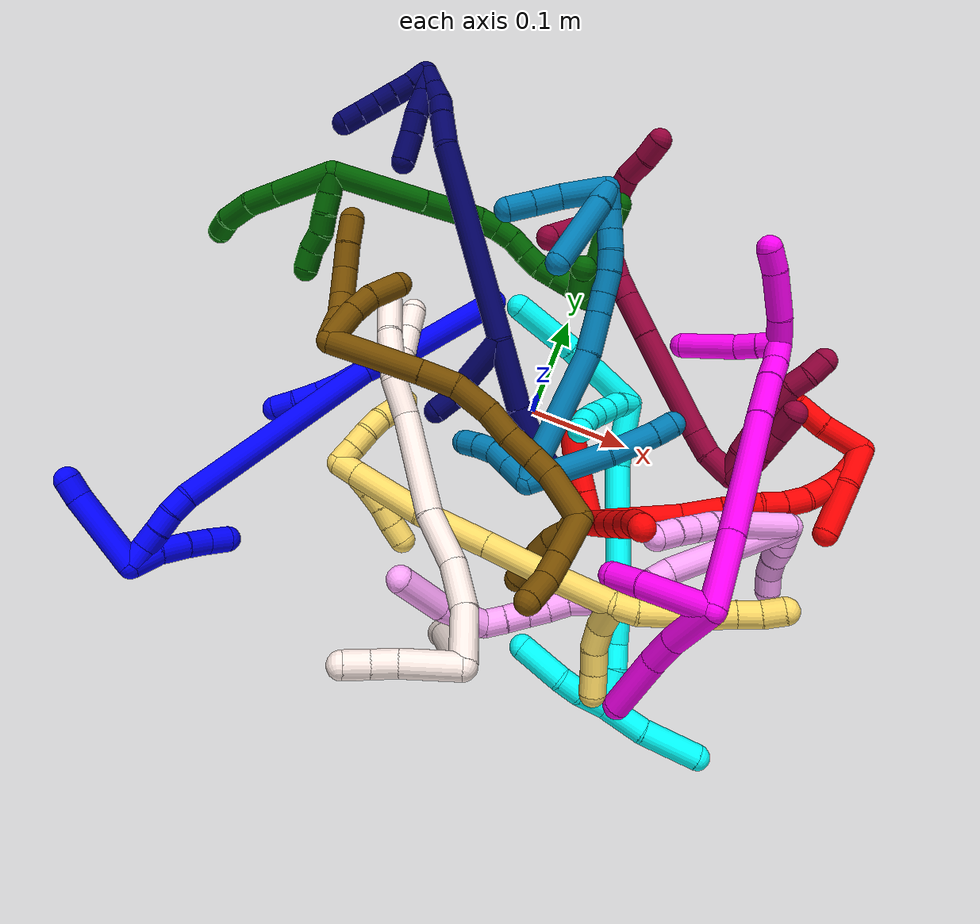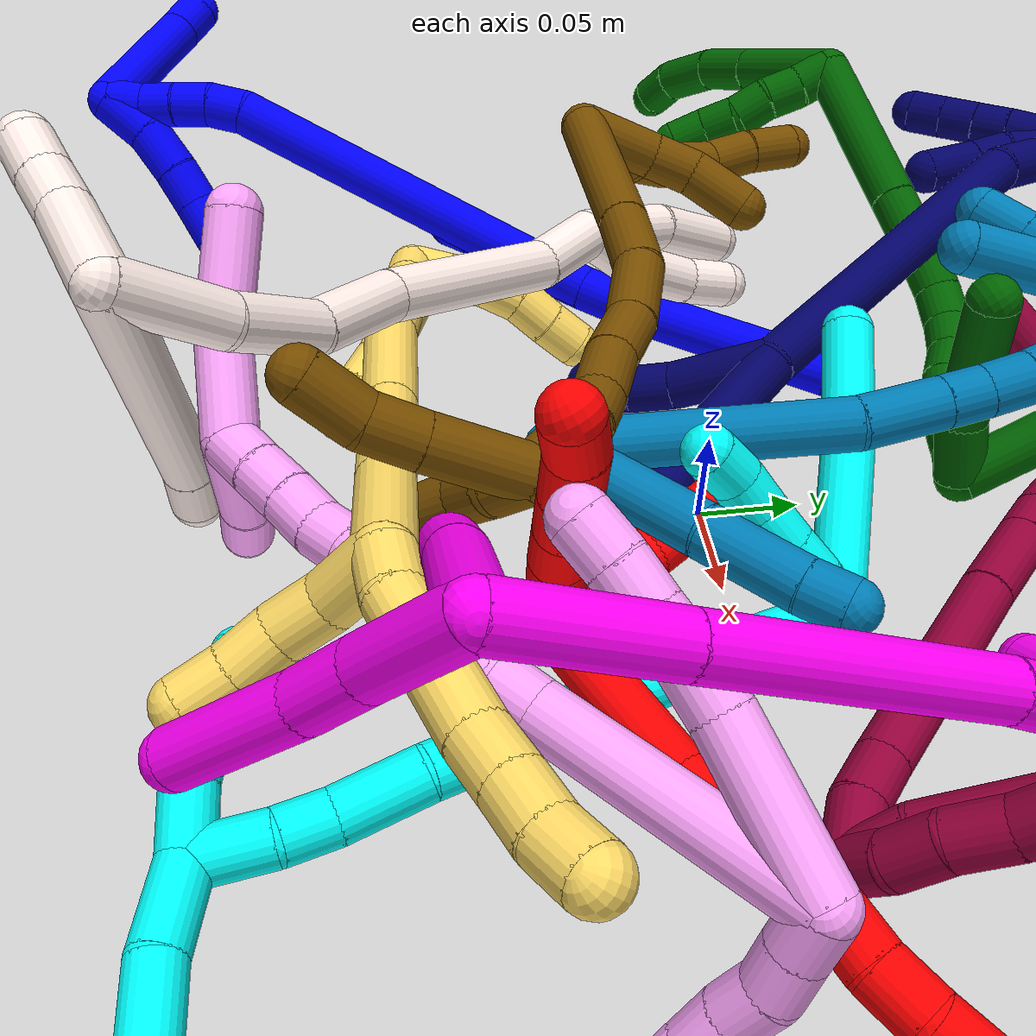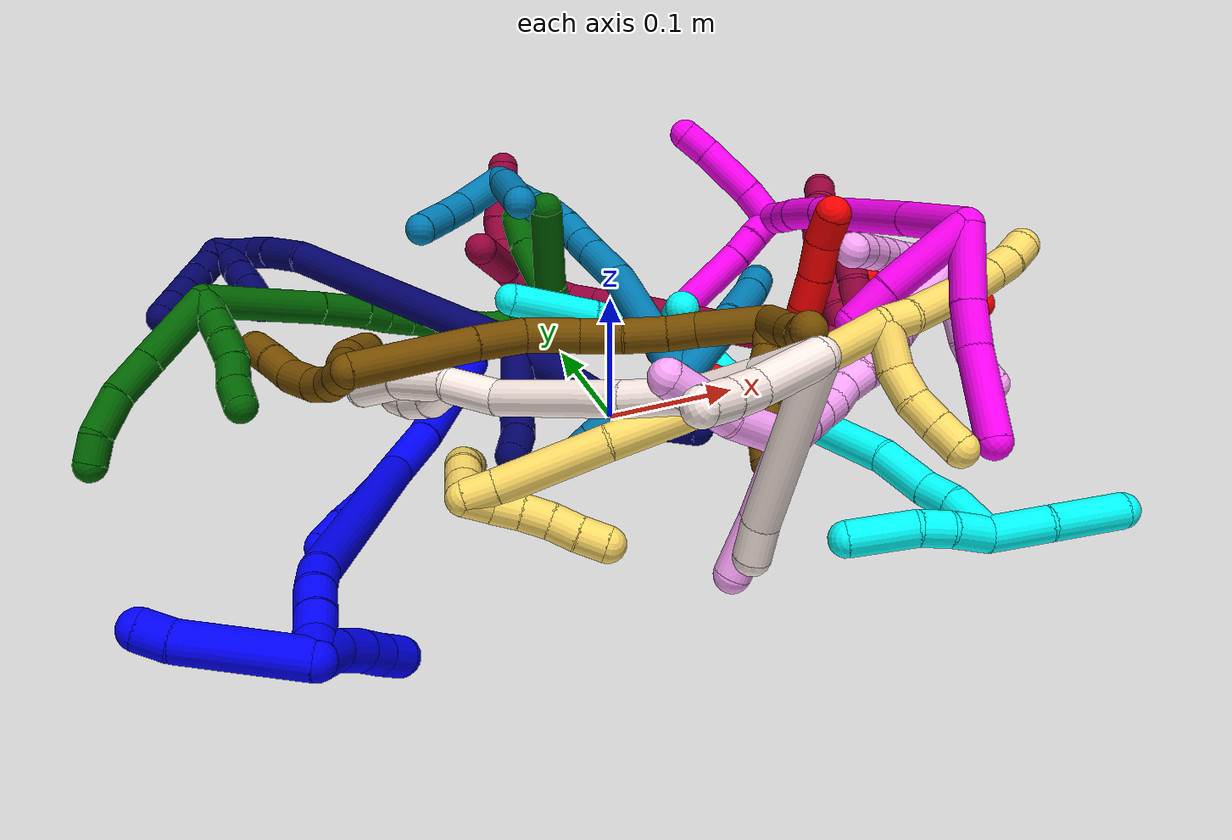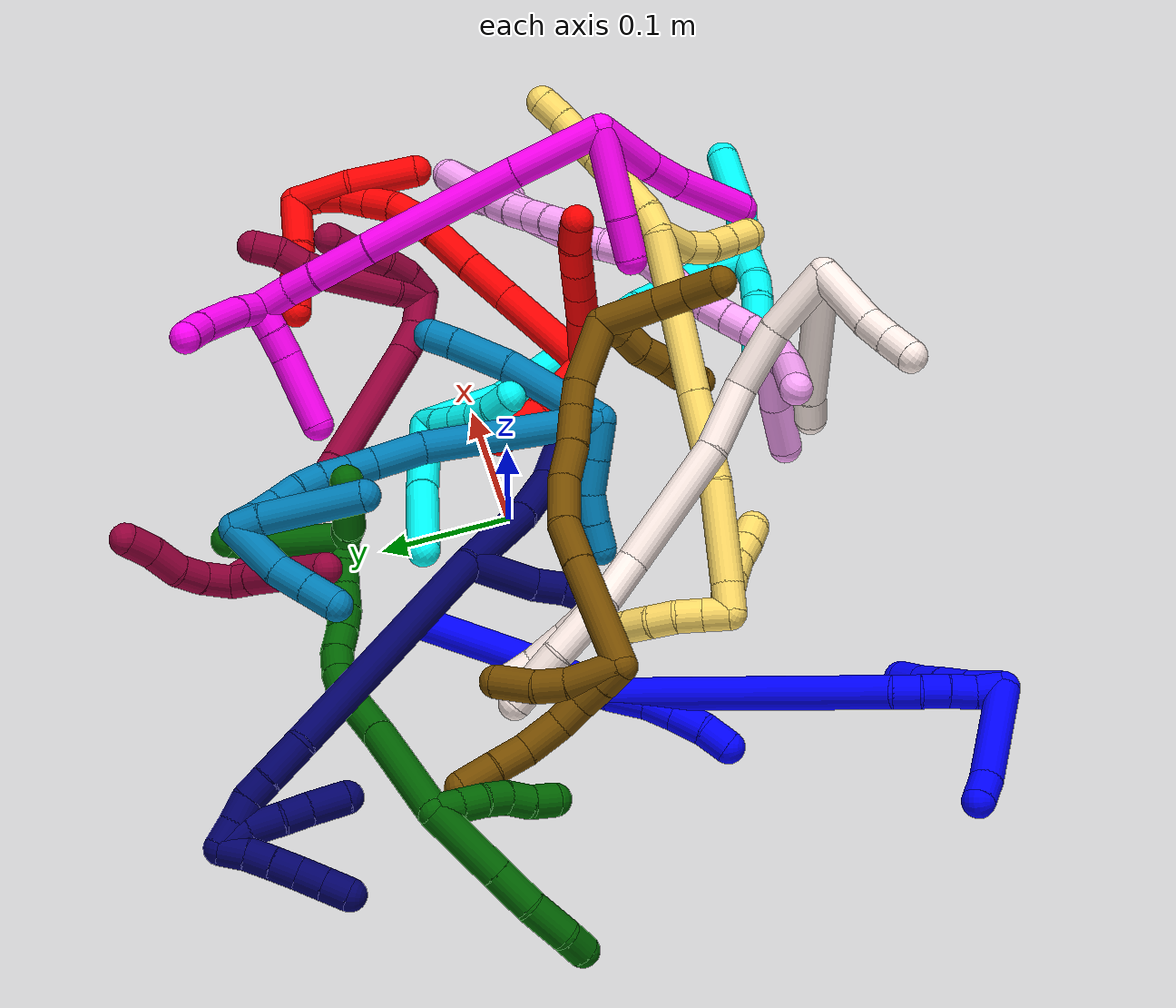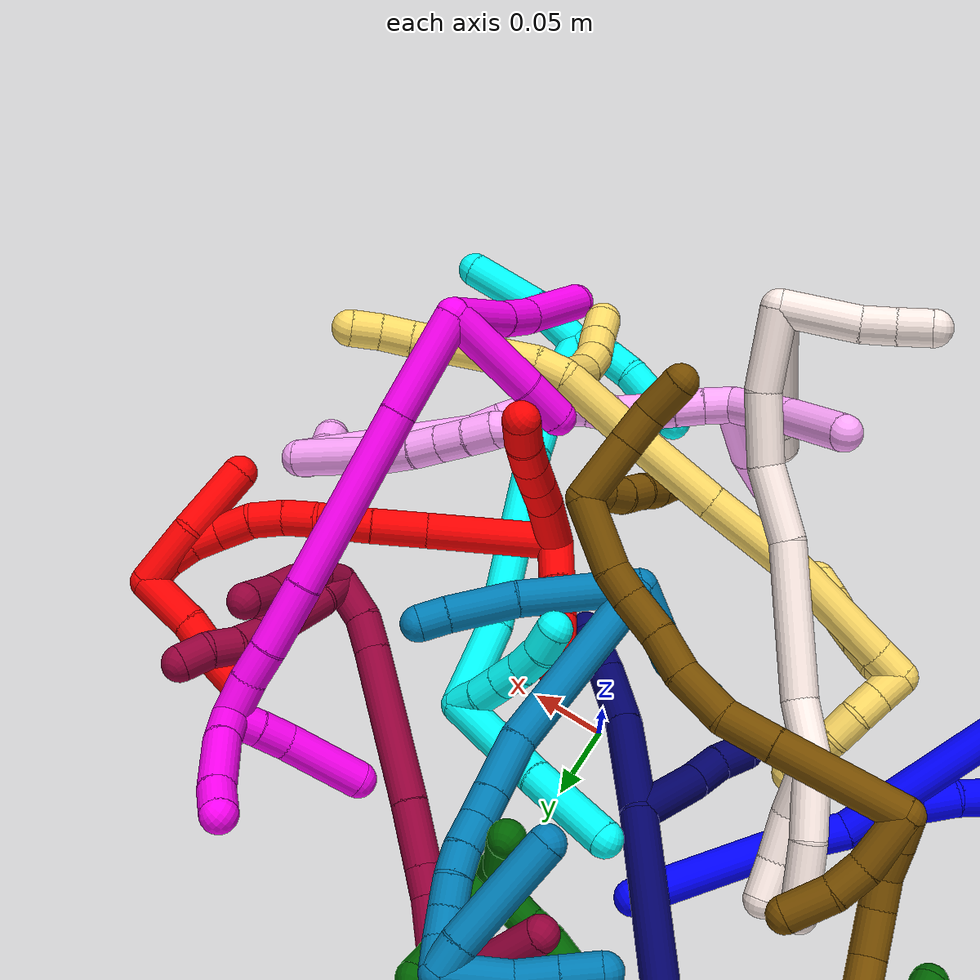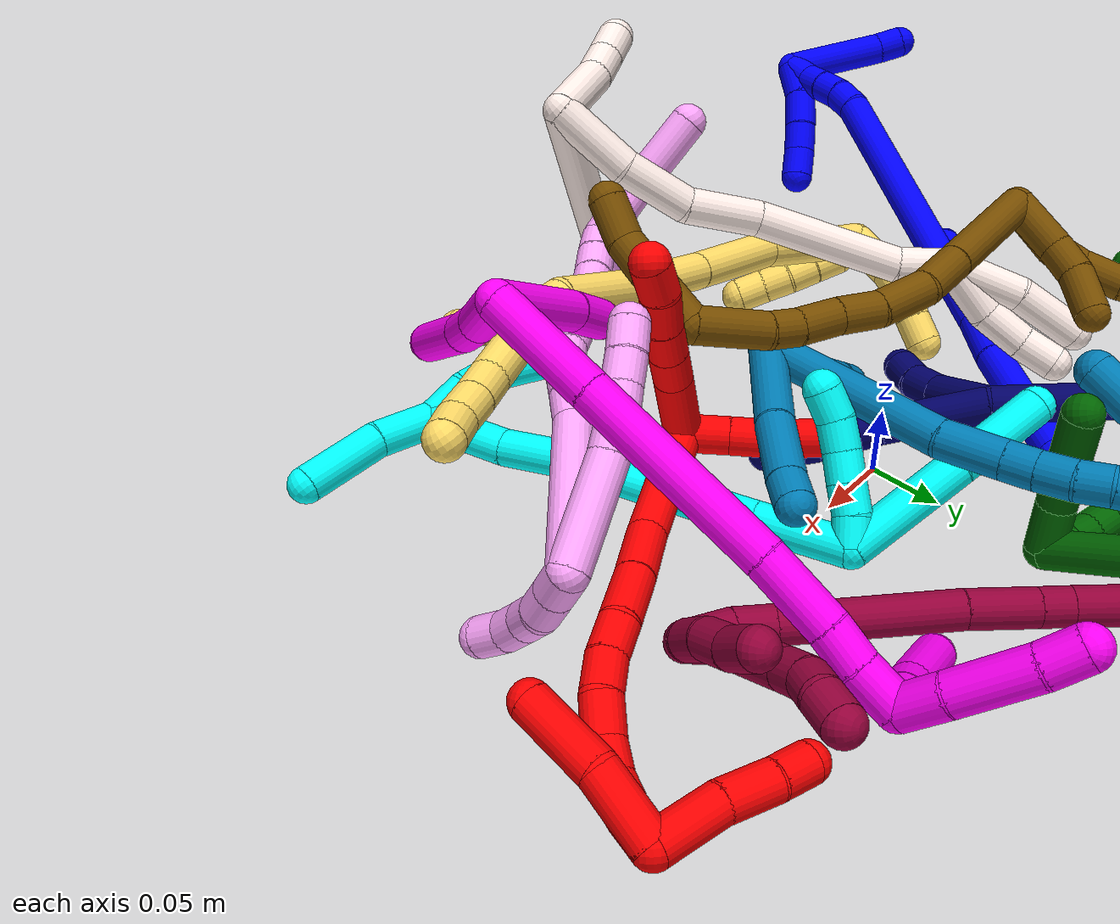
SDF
<sdf version="1.7">
 <world name="default">
  <plugin name="TubeGeneratorPlugin" filename="libtube_generator_plugin.so"/>
  <model name="photoneo_s_sensor">
   <static>1</static>
   <pose>0 0 2 1.57079 1.57079 3.14159</pose>
   <link name="link">
    <inertial><mass>0.1</mass></inertial>
    <sensor name="sensor" type="depth">
     <update_rate>30</update_rate>
     <camera>
      <horizontal_fov>1.22</horizontal_fov>
      <image><width>1920</width><height>1200</height><format>B8G8R8</format></image>
      <clip><near>0.1</near><far>4</far></clip>
      <depth_camera><output>points</output></depth_camera>
     </camera>
     <plugin name="camera_plugin" filename="libgazebo_ros_depth_camera.so">
      <baseline>0.2</baseline>
      <alwaysOn>1</alwaysOn>
      <updateRate>0.0</updateRate>
      <cameraName>camera_ir</cameraName>
      <imageTopicName>/camera/color/image_raw</imageTopicName>
      <cameraInfoTopicName>/camera/color/camera_info</cameraInfoTopicName>
      <depthImageTopicName>/camera/depth/image_raw</depthImageTopicName>
      <depthImageCameraInfoTopicName>/camera/depth/camera_info</depthImageCameraInfoTopicName>
      <pointCloudTopicName>/camera/depth/points</pointCloudTopicName>
      <frameName>fr_optical</frameName>
      <pointCloudCutoff>0.1</pointCloudCutoff>
      <pointCloudCutoffMax>2.0</pointCloudCutoffMax>
      <distortionK1>0</distortionK1>
      <distortionK2>0</distortionK2>
      <distortionK3>0</distortionK3>
      <distortionT1>0</distortionT1>
      <distortionT2>0</distortionT2>
      <CxPrime>0</CxPrime>
      <Cx>0</Cx>
      <Cy>0</Cy>
      <focalLength>0</focalLength>
      <hackBaseline>0</hackBaseline>
     </plugin>
    </sensor>
   </link>
  </model>
  <gravity>0 0 -9.8</gravity>
  <magnetic_field>6e-06 2.3e-05 -4.2e-05</magnetic_field>
  <atmosphere type="adiabatic"/>
  <physics name="default_physics" default="0" type="ode">
   <max_step_size>0.003</max_step_size>
   <real_time_factor>1</real_time_factor>
   <real_time_update_rate>1000</real_time_update_rate>
   <max_contacts>10000</max_contacts>
   <ode>
    <solver>
     <type>quick</type>
     <iters>100</iters>
     <sor>1.3</sor>
     <use_dynamic_moi_rescaling>0</use_dynamic_moi_rescaling>
    </solver>
    <constraints>
     <contact_max_correcting_vel>0</contact_max_correcting_vel>
     <contact_surface_layer>0.001</contact_surface_layer>
     <cfm>0</cfm>
     <erp>0.2</erp>
    </constraints>
   </ode>
  </physics>
  <scene><ambient>0.4 0.4 0.4 1</ambient><background>0.7 0.7 0.7 1</background><shadows>0</shadows></scene>
  <audio><device>default</device></audio>
  <spherical_coordinates>
   <surface_model>EARTH_WGS84</surface_model>
   <latitude_deg>0</latitude_deg>
   <longitude_deg>0</longitude_deg>
   <elevation>0</elevation>
   <heading_deg>0</heading_deg>
  </spherical_coordinates>
  <model name="bin">
   <static>1</static>
   <link name="bottom">
    <collision name="collision-bottom">
     <pose>0 0 -0.01 0 -0 0</pose>
     <geometry><box><size>0.8 0.6 0.02</size></box></geometry>
     <surface>
      <friction><ode><mu>100</mu><mu2>100</mu2></ode></friction>
      <contact><collide_bitmask>65535</collide_bitmask></contact>
     </surface>
    </collision>
   </link>
   <link name="west_wall">
    <collision name="collision-west_wall">
     <pose>-0.41 0 0.1 0 -0 0</pose>
     <geometry><box><size>0.02 0.6 0.2</size></box></geometry>
     <surface>
      <friction><ode><mu>100</mu><mu2>100</mu2></ode></friction>
      <contact><collide_bitmask>65535</collide_bitmask></contact>
     </surface>
    </collision>
   </link>
   <link name="east_wall">
    <collision name="collision-east_wall">
     <pose>0.41 0 0.1 0 -0 0</pose>
     <geometry><box><size>0.02 0.6 0.2</size></box></geometry>
     <surface>
      <friction><ode><mu>100</mu><mu2>100</mu2></ode></friction>
      <contact><collide_bitmask>65535</collide_bitmask></contact>
     </surface>
    </collision>
   </link>
   <link name="south_wall">
    <collision name="collision-south_wall">
     <pose>0 -0.31 0.1 0 -0 0</pose>
     <geometry><box><size>0.8 0.02 0.2</size></box></geometry>
     <surface>
      <friction><ode><mu>100</mu><mu2>100</mu2></ode></friction>
      <contact><collide_bitmask>65535</collide_bitmask></contact>
     </surface>
    </collision>
   </link>
   <link name="north_wall">
    <collision name="collision-north_wall">
     <pose>0 0.31 0.1 0 -0 0</pose>
     <geometry><box><size>0.8 0.02 0.2</size></box></geometry>
     <surface>
      <friction><ode><mu>100</mu><mu2>100</mu2></ode></friction>
      <contact><collide_bitmask>65535</collide_bitmask></contact>
     </surface>
    </collision>
   </link>
  </model>
  <model name="1">
   <static>0</static>
   <link name="1">
    <collision name="collision-cylinder-e_1_2_8">
     <pose>0.006537 0.007929 -0.020532 -2.77304 0.288712 -1.32473</pose>
     <geometry><cylinder><radius>0.0125</radius><length>0.04592</length></cylinder></geometry>
     <surface>
      <friction><ode><mu>1.16</mu><mu2>1.16</mu2><slip1>0</slip1><slip2>0</slip2></ode></friction>
      <contact><ode><kp>1e+06</kp><kd>1</kd><max_vel>0</max_vel><min_depth>0.001</min_depth></ode></contact>
     </surface>
    </collision>
    <visual name="visual-cylinder-e_1_2_8">
     <pose>0.006537 0.007929 -0.020532 -2.77304 0.288712 -1.32473</pose>
     <geometry><cylinder><radius>0.0125</radius><length>0.04592</length></cylinder></geometry>
     <material><ambient>0 0 1 1</ambient></material>
    </visual>
    <collision name="collision-cylinder-e_2_8_6">
     <pose>0.022446 0.033616 -0.089074 -2.78734 0.181078 -0.93876</pose>
     <geometry><cylinder><radius>0.0125</radius><length>0.10408</length></cylinder></geometry>
     <surface>
      <friction><ode><mu>1.16</mu><mu2>1.16</mu2><slip1>0</slip1><slip2>0</slip2></ode></friction>
      <contact><ode><kp>1e+06</kp><kd>1</kd><max_vel>0</max_vel><min_depth>0.001</min_depth></ode></contact>
     </surface>
    </collision>
    <visual name="visual-cylinder-e_2_8_6">
     <pose>0.022446 0.033616 -0.089074 -2.78734 0.181078 -0.93876</pose>
     <geometry><cylinder><radius>0.0125</radius><length>0.10408</length></cylinder></geometry>
     <material><ambient>0 0 1 1</ambient></material>
    </visual>
    <collision name="collision-cylinder-e_1_2_9">
     <pose>-0.002226 -0.002771 0.014634 0.187143 -0.14833 -0.013946</pose>
     <geometry><cylinder><radius>0.0125</radius><length>0.030118</length></cylinder></geometry>
     <surface>
      <friction><ode><mu>1.16</mu><mu2>1.16</mu2><slip1>0</slip1><slip2>0</slip2></ode></friction>
      <contact><ode><kp>1e+06</kp><kd>1</kd><max_vel>0</max_vel><min_depth>0.001</min_depth></ode></contact>
     </surface>
    </collision>
    <visual name="visual-cylinder-e_1_2_9">
     <pose>-0.002226 -0.002771 0.014634 0.187143 -0.14833 -0.013946</pose>
     <geometry><cylinder><radius>0.0125</radius><length>0.030118</length></cylinder></geometry>
     <material><ambient>0 0 1 1</ambient></material>
    </visual>
    <collision name="collision-cylinder-e_2_9_10">
     <pose>-0.007711 -0.008674 0.039627 0.293623 -0.292542 -0.043564</pose>
     <geometry><cylinder><radius>0.0125</radius><length>0.022606</length></cylinder></geometry>
     <surface>
      <friction><ode><mu>1.16</mu><mu2>1.16</mu2><slip1>0</slip1><slip2>0</slip2></ode></friction>
      <contact><ode><kp>1e+06</kp><kd>1</kd><max_vel>0</max_vel><min_depth>0.001</min_depth></ode></contact>
     </surface>
    </collision>
    <visual name="visual-cylinder-e_2_9_10">
     <pose>-0.007711 -0.008674 0.039627 0.293623 -0.292542 -0.043564</pose>
     <geometry><cylinder><radius>0.0125</radius><length>0.022606</length></cylinder></geometry>
     <material><ambient>0 0 1 1</ambient></material>
    </visual>
    <collision name="collision-cylinder-e_3_10_11">
     <pose>-0.015406 -0.015051 0.061317 0.278909 -0.359947 -0.051066</pose>
     <geometry><cylinder><radius>0.0125</radius><length>0.025186</length></cylinder></geometry>
     <surface>
      <friction><ode><mu>1.16</mu><mu2>1.16</mu2><slip1>0</slip1><slip2>0</slip2></ode></friction>
      <contact><ode><kp>1e+06</kp><kd>1</kd><max_vel>0</max_vel><min_depth>0.001</min_depth></ode></contact>
     </surface>
    </collision>
    <visual name="visual-cylinder-e_3_10_11">
     <pose>-0.015406 -0.015051 0.061317 0.278909 -0.359947 -0.051066</pose>
     <geometry><cylinder><radius>0.0125</radius><length>0.025186</length></cylinder></geometry>
     <material><ambient>0 0 1 1</ambient></material>
    </visual>
    <collision name="collision-cylinder-e_4_11_5">
     <pose>-0.024518 -0.023374 0.081269 0.532301 -0.437229 -0.120985</pose>
     <geometry><cylinder><radius>0.0125</radius><length>0.02209</length></cylinder></geometry>
     <surface>
      <friction><ode><mu>1.16</mu><mu2>1.16</mu2><slip1>0</slip1><slip2>0</slip2></ode></friction>
      <contact><ode><kp>1e+06</kp><kd>1</kd><max_vel>0</max_vel><min_depth>0.001</min_depth></ode></contact>
     </surface>
    </collision>
    <visual name="visual-cylinder-e_4_11_5">
     <pose>-0.024518 -0.023374 0.081269 0.532301 -0.437229 -0.120985</pose>
     <geometry><cylinder><radius>0.0125</radius><length>0.02209</length></cylinder></geometry>
     <material><ambient>0 0 1 1</ambient></material>
    </visual>
    <collision name="collision-cylinder-e_1_2_12">
     <pose>-0.000914 0.00056 0.109874 -0.0051 -0.008322 2.1e-05</pose>
     <geometry><cylinder><radius>0.0125</radius><length>0.219758</length></cylinder></geometry>
     <surface>
      <friction><ode><mu>1.16</mu><mu2>1.16</mu2><slip1>0</slip1><slip2>0</slip2></ode></friction>
      <contact><ode><kp>1e+06</kp><kd>1</kd><max_vel>0</max_vel><min_depth>0.001</min_depth></ode></contact>
     </surface>
    </collision>
    <visual name="visual-cylinder-e_1_2_12">
     <pose>-0.000914 0.00056 0.109874 -0.0051 -0.008322 2.1e-05</pose>
     <geometry><cylinder><radius>0.0125</radius><length>0.219758</length></cylinder></geometry>
     <material><ambient>0 0 1 1</ambient></material>
    </visual>
    <collision name="collision-cylinder-e_2_12_13">
     <pose>-0.000506 -0.000904 0.22956 0.203502 0.131289 0.013424</pose>
     <geometry><cylinder><radius>0.0125</radius><length>0.020214</length></cylinder></geometry>
     <surface>
      <friction><ode><mu>1.16</mu><mu2>1.16</mu2><slip1>0</slip1><slip2>0</slip2></ode></friction>
      <contact><ode><kp>1e+06</kp><kd>1</kd><max_vel>0</max_vel><min_depth>0.001</min_depth></ode></contact>
     </surface>
    </collision>
    <visual name="visual-cylinder-e_2_12_13">
     <pose>-0.000506 -0.000904 0.22956 0.203502 0.131289 0.013424</pose>
     <geometry><cylinder><radius>0.0125</radius><length>0.020214</length></cylinder></geometry>
     <material><ambient>0 0 1 1</ambient></material>
    </visual>
    <collision name="collision-cylinder-e_3_13_14">
     <pose>0.003231 -0.00643 0.248428 0.368864 0.24368 0.045677</pose>
     <geometry><cylinder><radius>0.0125</radius><length>0.020006</length></cylinder></geometry>
     <surface>
      <friction><ode><mu>1.16</mu><mu2>1.16</mu2><slip1>0</slip1><slip2>0</slip2></ode></friction>
      <contact><ode><kp>1e+06</kp><kd>1</kd><max_vel>0</max_vel><min_depth>0.001</min_depth></ode></contact>
     </surface>
    </collision>
    <visual name="visual-cylinder-e_3_13_14">
     <pose>0.003231 -0.00643 0.248428 0.368864 0.24368 0.045677</pose>
     <geometry><cylinder><radius>0.0125</radius><length>0.020006</length></cylinder></geometry>
     <material><ambient>0 0 1 1</ambient></material>
    </visual>
    <collision name="collision-cylinder-e_4_14_15">
     <pose>0.00756 -0.014248 0.266308 0.455078 0.192605 0.044728</pose>
     <geometry><cylinder><radius>0.0125</radius><length>0.020019</length></cylinder></geometry>
     <surface>
      <friction><ode><mu>1.16</mu><mu2>1.16</mu2><slip1>0</slip1><slip2>0</slip2></ode></friction>
      <contact><ode><kp>1e+06</kp><kd>1</kd><max_vel>0</max_vel><min_depth>0.001</min_depth></ode></contact>
     </surface>
    </collision>
    <visual name="visual-cylinder-e_4_14_15">
     <pose>0.00756 -0.014248 0.266308 0.455078 0.192605 0.044728</pose>
     <geometry><cylinder><radius>0.0125</radius><length>0.020019</length></cylinder></geometry>
     <material><ambient>0 0 1 1</ambient></material>
    </visual>
    <collision name="collision-cylinder-e_5_15_1">
     <pose>0.012298 -0.020308 0.284568 0.182546 0.285951 0.026351</pose>
     <geometry><cylinder><radius>0.0125</radius><length>0.020003</length></cylinder></geometry>
     <surface>
      <friction><ode><mu>1.16</mu><mu2>1.16</mu2><slip1>0</slip1><slip2>0</slip2></ode></friction>
      <contact><ode><kp>1e+06</kp><kd>1</kd><max_vel>0</max_vel><min_depth>0.001</min_depth></ode></contact>
     </surface>
    </collision>
    <visual name="visual-cylinder-e_5_15_1">
     <pose>0.012298 -0.020308 0.284568 0.182546 0.285951 0.026351</pose>
     <geometry><cylinder><radius>0.0125</radius><length>0.020003</length></cylinder></geometry>
     <material><ambient>0 0 1 1</ambient></material>
    </visual>
    <collision name="collision-cylinder-e_1_1_16">
     <pose>-0.02467 -0.020375 0.293448 -1.89132 -1.52647 1.84895</pose>
     <geometry><cylinder><radius>0.0125</radius><length>0.079656</length></cylinder></geometry>
     <surface>
      <friction><ode><mu>1.16</mu><mu2>1.16</mu2><slip1>0</slip1><slip2>0</slip2></ode></friction>
      <contact><ode><kp>1e+06</kp><kd>1</kd><max_vel>0</max_vel><min_depth>0.001</min_depth></ode></contact>
     </surface>
    </collision>
    <visual name="visual-cylinder-e_1_1_16">
     <pose>-0.02467 -0.020375 0.293448 -1.89132 -1.52647 1.84895</pose>
     <geometry><cylinder><radius>0.0125</radius><length>0.079656</length></cylinder></geometry>
     <material><ambient>0 0 1 1</ambient></material>
    </visual>
    <collision name="collision-cylinder-e_2_16_4">
     <pose>-0.074344 -0.016449 0.292058 -1.92543 -1.33256 1.69229</pose>
     <geometry><cylinder><radius>0.0125</radius><length>0.020344</length></cylinder></geometry>
     <surface>
      <friction><ode><mu>1.16</mu><mu2>1.16</mu2><slip1>0</slip1><slip2>0</slip2></ode></friction>
      <contact><ode><kp>1e+06</kp><kd>1</kd><max_vel>0</max_vel><min_depth>0.001</min_depth></ode></contact>
     </surface>
    </collision>
    <visual name="visual-cylinder-e_2_16_4">
     <pose>-0.074344 -0.016449 0.292058 -1.92543 -1.33256 1.69229</pose>
     <geometry><cylinder><radius>0.0125</radius><length>0.020344</length></cylinder></geometry>
     <material><ambient>0 0 1 1</ambient></material>
    </visual>
    <collision name="collision-cylinder-e_1_1_17">
     <pose>0.017137 -0.024438 0.280233 2.96989 0.14342 1.39103</pose>
     <geometry><cylinder><radius>0.0125</radius><length>0.028244</length></cylinder></geometry>
     <surface>
      <friction><ode><mu>1.16</mu><mu2>1.16</mu2><slip1>0</slip1><slip2>0</slip2></ode></friction>
      <contact><ode><kp>1e+06</kp><kd>1</kd><max_vel>0</max_vel><min_depth>0.001</min_depth></ode></contact>
     </surface>
    </collision>
    <visual name="visual-cylinder-e_1_1_17">
     <pose>0.017137 -0.024438 0.280233 2.96989 0.14342 1.39103</pose>
     <geometry><cylinder><radius>0.0125</radius><length>0.028244</length></cylinder></geometry>
     <material><ambient>0 0 1 1</ambient></material>
    </visual>
    <collision name="collision-cylinder-e_2_17_18">
     <pose>0.0236 -0.031268 0.25436 2.7898 0.332011 1.51182</pose>
     <geometry><cylinder><radius>0.0125</radius><length>0.02727</length></cylinder></geometry>
     <surface>
      <friction><ode><mu>1.16</mu><mu2>1.16</mu2><slip1>0</slip1><slip2>0</slip2></ode></friction>
      <contact><ode><kp>1e+06</kp><kd>1</kd><max_vel>0</max_vel><min_depth>0.001</min_depth></ode></contact>
     </surface>
    </collision>
    <visual name="visual-cylinder-e_2_17_18">
     <pose>0.0236 -0.031268 0.25436 2.7898 0.332011 1.51182</pose>
     <geometry><cylinder><radius>0.0125</radius><length>0.02727</length></cylinder></geometry>
     <material><ambient>0 0 1 1</ambient></material>
    </visual>
    <collision name="collision-cylinder-e_3_18_19">
     <pose>0.031828 -0.040237 0.232859 2.69272 0.347923 1.31214</pose>
     <geometry><cylinder><radius>0.0125</radius><length>0.022197</length></cylinder></geometry>
     <surface>
      <friction><ode><mu>1.16</mu><mu2>1.16</mu2><slip1>0</slip1><slip2>0</slip2></ode></friction>
      <contact><ode><kp>1e+06</kp><kd>1</kd><max_vel>0</max_vel><min_depth>0.001</min_depth></ode></contact>
     </surface>
    </collision>
    <visual name="visual-cylinder-e_3_18_19">
     <pose>0.031828 -0.040237 0.232859 2.69272 0.347923 1.31214</pose>
     <geometry><cylinder><radius>0.0125</radius><length>0.022197</length></cylinder></geometry>
     <material><ambient>0 0 1 1</ambient></material>
    </visual>
    <collision name="collision-cylinder-e_4_19_3">
     <pose>0.040112 -0.048791 0.214093 2.7356 0.415706 1.59512</pose>
     <geometry><cylinder><radius>0.0125</radius><length>0.022289</length></cylinder></geometry>
     <surface>
      <friction><ode><mu>1.16</mu><mu2>1.16</mu2><slip1>0</slip1><slip2>0</slip2></ode></friction>
      <contact><ode><kp>1e+06</kp><kd>1</kd><max_vel>0</max_vel><min_depth>0.001</min_depth></ode></contact>
     </surface>
    </collision>
    <visual name="visual-cylinder-e_4_19_3">
     <pose>0.040112 -0.048791 0.214093 2.7356 0.415706 1.59512</pose>
     <geometry><cylinder><radius>0.0125</radius><length>0.022289</length></cylinder></geometry>
     <material><ambient>0 0 1 1</ambient></material>
    </visual>
    <collision name="collision-sphere-3">
     <pose>0.044613 -0.052818 0.204726 0 -0 0</pose>
     <geometry><sphere><radius>0.0125</radius></sphere></geometry>
     <surface>
      <friction><ode><mu>1.16</mu><mu2>1.16</mu2><slip1>0</slip1><slip2>0</slip2></ode></friction>
      <contact><ode><kp>1e+06</kp><kd>1</kd><max_vel>0</max_vel><min_depth>0.001</min_depth></ode></contact>
     </surface>
    </collision>
    <visual name="visual-sphere-3">
     <pose>0.044613 -0.052818 0.204726 0 -0 0</pose>
     <geometry><sphere><radius>0.0125</radius></sphere></geometry>
     <material><ambient>0 0 1 1</ambient></material>
    </visual>
    <collision name="collision-sphere-19">
     <pose>0.035612 -0.044765 0.223459 0 -0 0</pose>
     <geometry><sphere><radius>0.0125</radius></sphere></geometry>
     <surface>
      <friction><ode><mu>1.16</mu><mu2>1.16</mu2><slip1>0</slip1><slip2>0</slip2></ode></friction>
      <contact><ode><kp>1e+06</kp><kd>1</kd><max_vel>0</max_vel><min_depth>0.001</min_depth></ode></contact>
     </surface>
    </collision>
    <visual name="visual-sphere-19">
     <pose>0.035612 -0.044765 0.223459 0 -0 0</pose>
     <geometry><sphere><radius>0.0125</radius></sphere></geometry>
     <material><ambient>0 0 1 1</ambient></material>
    </visual>
    <collision name="collision-sphere-11">
     <pose>-0.019842 -0.018296 0.072648 0 -0 0</pose>
     <geometry><sphere><radius>0.0125</radius></sphere></geometry>
     <surface>
      <friction><ode><mu>1.16</mu><mu2>1.16</mu2><slip1>0</slip1><slip2>0</slip2></ode></friction>
      <contact><ode><kp>1e+06</kp><kd>1</kd><max_vel>0</max_vel><min_depth>0.001</min_depth></ode></contact>
     </surface>
    </collision>
    <visual name="visual-sphere-11">
     <pose>-0.019842 -0.018296 0.072648 0 -0 0</pose>
     <geometry><sphere><radius>0.0125</radius></sphere></geometry>
     <material><ambient>0 0 1 1</ambient></material>
    </visual>
    <collision name="collision-sphere-10">
     <pose>-0.01097 -0.011807 0.049986 0 -0 0</pose>
     <geometry><sphere><radius>0.0125</radius></sphere></geometry>
     <surface>
      <friction><ode><mu>1.16</mu><mu2>1.16</mu2><slip1>0</slip1><slip2>0</slip2></ode></friction>
      <contact><ode><kp>1e+06</kp><kd>1</kd><max_vel>0</max_vel><min_depth>0.001</min_depth></ode></contact>
     </surface>
    </collision>
    <visual name="visual-sphere-10">
     <pose>-0.01097 -0.011807 0.049986 0 -0 0</pose>
     <geometry><sphere><radius>0.0125</radius></sphere></geometry>
     <material><ambient>0 0 1 1</ambient></material>
    </visual>
    <collision name="collision-sphere-6">
     <pose>0.031818 0.051373 -0.137085 0 -0 0</pose>
     <geometry><sphere><radius>0.0125</radius></sphere></geometry>
     <surface>
      <friction><ode><mu>1.16</mu><mu2>1.16</mu2><slip1>0</slip1><slip2>0</slip2></ode></friction>
      <contact><ode><kp>1e+06</kp><kd>1</kd><max_vel>0</max_vel><min_depth>0.001</min_depth></ode></contact>
     </surface>
    </collision>
    <visual name="visual-sphere-6">
     <pose>0.031818 0.051373 -0.137085 0 -0 0</pose>
     <geometry><sphere><radius>0.0125</radius></sphere></geometry>
     <material><ambient>0 0 1 1</ambient></material>
    </visual>
    <collision name="collision-sphere-9">
     <pose>-0.004451 -0.005542 0.029267 0 -0 0</pose>
     <geometry><sphere><radius>0.0125</radius></sphere></geometry>
     <surface>
      <friction><ode><mu>1.16</mu><mu2>1.16</mu2><slip1>0</slip1><slip2>0</slip2></ode></friction>
      <contact><ode><kp>1e+06</kp><kd>1</kd><max_vel>0</max_vel><min_depth>0.001</min_depth></ode></contact>
     </surface>
    </collision>
    <visual name="visual-sphere-9">
     <pose>-0.004451 -0.005542 0.029267 0 -0 0</pose>
     <geometry><sphere><radius>0.0125</radius></sphere></geometry>
     <material><ambient>0 0 1 1</ambient></material>
    </visual>
    <collision name="collision-sphere-2">
     <geometry><sphere><radius>0.0125</radius></sphere></geometry>
     <surface>
      <friction><ode><mu>1.16</mu><mu2>1.16</mu2><slip1>0</slip1><slip2>0</slip2></ode></friction>
      <contact><ode><kp>1e+06</kp><kd>1</kd><max_vel>0</max_vel><min_depth>0.001</min_depth></ode></contact>
     </surface>
    </collision>
    <visual name="visual-sphere-2">
     <geometry><sphere><radius>0.0125</radius></sphere></geometry>
     <material><ambient>0 0 1 1</ambient></material>
    </visual>
    <collision name="collision-sphere-8">
     <pose>0.013074 0.015859 -0.041063 0 -0 0</pose>
     <geometry><sphere><radius>0.0125</radius></sphere></geometry>
     <surface>
      <friction><ode><mu>1.16</mu><mu2>1.16</mu2><slip1>0</slip1><slip2>0</slip2></ode></friction>
      <contact><ode><kp>1e+06</kp><kd>1</kd><max_vel>0</max_vel><min_depth>0.001</min_depth></ode></contact>
     </surface>
    </collision>
    <visual name="visual-sphere-8">
     <pose>0.013074 0.015859 -0.041063 0 -0 0</pose>
     <geometry><sphere><radius>0.0125</radius></sphere></geometry>
     <material><ambient>0 0 1 1</ambient></material>
    </visual>
    <collision name="collision-sphere-5">
     <pose>-0.029195 -0.028453 0.089891 0 -0 0</pose>
     <geometry><sphere><radius>0.0125</radius></sphere></geometry>
     <surface>
      <friction><ode><mu>1.16</mu><mu2>1.16</mu2><slip1>0</slip1><slip2>0</slip2></ode></friction>
      <contact><ode><kp>1e+06</kp><kd>1</kd><max_vel>0</max_vel><min_depth>0.001</min_depth></ode></contact>
     </surface>
    </collision>
    <visual name="visual-sphere-5">
     <pose>-0.029195 -0.028453 0.089891 0 -0 0</pose>
     <geometry><sphere><radius>0.0125</radius></sphere></geometry>
     <material><ambient>0 0 1 1</ambient></material>
    </visual>
    <collision name="collision-sphere-12">
     <pose>-0.001829 0.001121 0.219747 0 -0 0</pose>
     <geometry><sphere><radius>0.0125</radius></sphere></geometry>
     <surface>
      <friction><ode><mu>1.16</mu><mu2>1.16</mu2><slip1>0</slip1><slip2>0</slip2></ode></friction>
      <contact><ode><kp>1e+06</kp><kd>1</kd><max_vel>0</max_vel><min_depth>0.001</min_depth></ode></contact>
     </surface>
    </collision>
    <visual name="visual-sphere-12">
     <pose>-0.001829 0.001121 0.219747 0 -0 0</pose>
     <geometry><sphere><radius>0.0125</radius></sphere></geometry>
     <material><ambient>0 0 1 1</ambient></material>
    </visual>
    <collision name="collision-sphere-13">
     <pose>0.000817 -0.002929 0.239374 0 -0 0</pose>
     <geometry><sphere><radius>0.0125</radius></sphere></geometry>
     <surface>
      <friction><ode><mu>1.16</mu><mu2>1.16</mu2><slip1>0</slip1><slip2>0</slip2></ode></friction>
      <contact><ode><kp>1e+06</kp><kd>1</kd><max_vel>0</max_vel><min_depth>0.001</min_depth></ode></contact>
     </surface>
    </collision>
    <visual name="visual-sphere-13">
     <pose>0.000817 -0.002929 0.239374 0 -0 0</pose>
     <geometry><sphere><radius>0.0125</radius></sphere></geometry>
     <material><ambient>0 0 1 1</ambient></material>
    </visual>
    <collision name="collision-sphere-14">
     <pose>0.005644 -0.00993 0.257483 0 -0 0</pose>
     <geometry><sphere><radius>0.0125</radius></sphere></geometry>
     <surface>
      <friction><ode><mu>1.16</mu><mu2>1.16</mu2><slip1>0</slip1><slip2>0</slip2></ode></friction>
      <contact><ode><kp>1e+06</kp><kd>1</kd><max_vel>0</max_vel><min_depth>0.001</min_depth></ode></contact>
     </surface>
    </collision>
    <visual name="visual-sphere-14">
     <pose>0.005644 -0.00993 0.257483 0 -0 0</pose>
     <geometry><sphere><radius>0.0125</radius></sphere></geometry>
     <material><ambient>0 0 1 1</ambient></material>
    </visual>
    <collision name="collision-sphere-15">
     <pose>0.009476 -0.018566 0.275132 0 -0 0</pose>
     <geometry><sphere><radius>0.0125</radius></sphere></geometry>
     <surface>
      <friction><ode><mu>1.16</mu><mu2>1.16</mu2><slip1>0</slip1><slip2>0</slip2></ode></friction>
      <contact><ode><kp>1e+06</kp><kd>1</kd><max_vel>0</max_vel><min_depth>0.001</min_depth></ode></contact>
     </surface>
    </collision>
    <visual name="visual-sphere-15">
     <pose>0.009476 -0.018566 0.275132 0 -0 0</pose>
     <geometry><sphere><radius>0.0125</radius></sphere></geometry>
     <material><ambient>0 0 1 1</ambient></material>
    </visual>
    <collision name="collision-sphere-1">
     <pose>0.015119 -0.02205 0.294004 0 -0 0</pose>
     <geometry><sphere><radius>0.0125</radius></sphere></geometry>
     <surface>
      <friction><ode><mu>1.16</mu><mu2>1.16</mu2><slip1>0</slip1><slip2>0</slip2></ode></friction>
      <contact><ode><kp>1e+06</kp><kd>1</kd><max_vel>0</max_vel><min_depth>0.001</min_depth></ode></contact>
     </surface>
    </collision>
    <visual name="visual-sphere-1">
     <pose>0.015119 -0.02205 0.294004 0 -0 0</pose>
     <geometry><sphere><radius>0.0125</radius></sphere></geometry>
     <material><ambient>0 0 1 1</ambient></material>
    </visual>
    <collision name="collision-sphere-18">
     <pose>0.028044 -0.03571 0.242259 0 -0 0</pose>
     <geometry><sphere><radius>0.0125</radius></sphere></geometry>
     <surface>
      <friction><ode><mu>1.16</mu><mu2>1.16</mu2><slip1>0</slip1><slip2>0</slip2></ode></friction>
      <contact><ode><kp>1e+06</kp><kd>1</kd><max_vel>0</max_vel><min_depth>0.001</min_depth></ode></contact>
     </surface>
    </collision>
    <visual name="visual-sphere-18">
     <pose>0.028044 -0.03571 0.242259 0 -0 0</pose>
     <geometry><sphere><radius>0.0125</radius></sphere></geometry>
     <material><ambient>0 0 1 1</ambient></material>
    </visual>
    <collision name="collision-sphere-16">
     <pose>-0.064459 -0.0187 0.292892 0 -0 0</pose>
     <geometry><sphere><radius>0.0125</radius></sphere></geometry>
     <surface>
      <friction><ode><mu>1.16</mu><mu2>1.16</mu2><slip1>0</slip1><slip2>0</slip2></ode></friction>
      <contact><ode><kp>1e+06</kp><kd>1</kd><max_vel>0</max_vel><min_depth>0.001</min_depth></ode></contact>
     </surface>
    </collision>
    <visual name="visual-sphere-16">
     <pose>-0.064459 -0.0187 0.292892 0 -0 0</pose>
     <geometry><sphere><radius>0.0125</radius></sphere></geometry>
     <material><ambient>0 0 1 1</ambient></material>
    </visual>
    <collision name="collision-sphere-4">
     <pose>-0.084229 -0.014197 0.291225 0 -0 0</pose>
     <geometry><sphere><radius>0.0125</radius></sphere></geometry>
     <surface>
      <friction><ode><mu>1.16</mu><mu2>1.16</mu2><slip1>0</slip1><slip2>0</slip2></ode></friction>
      <contact><ode><kp>1e+06</kp><kd>1</kd><max_vel>0</max_vel><min_depth>0.001</min_depth></ode></contact>
     </surface>
    </collision>
    <visual name="visual-sphere-4">
     <pose>-0.084229 -0.014197 0.291225 0 -0 0</pose>
     <geometry><sphere><radius>0.0125</radius></sphere></geometry>
     <material><ambient>0 0 1 1</ambient></material>
    </visual>
    <collision name="collision-sphere-17">
     <pose>0.019156 -0.026826 0.266461 0 -0 0</pose>
     <geometry><sphere><radius>0.0125</radius></sphere></geometry>
     <surface>
      <friction><ode><mu>1.16</mu><mu2>1.16</mu2><slip1>0</slip1><slip2>0</slip2></ode></friction>
      <contact><ode><kp>1e+06</kp><kd>1</kd><max_vel>0</max_vel><min_depth>0.001</min_depth></ode></contact>
     </surface>
    </collision>
    <visual name="visual-sphere-17">
     <pose>0.019156 -0.026826 0.266461 0 -0 0</pose>
     <geometry><sphere><radius>0.0125</radius></sphere></geometry>
     <material><ambient>0 0 1 1</ambient></material>
    </visual>
    <inertial>
     <pose>0.001289 -0.004678 0.124467 0 -0 0</pose>
     <mass>0.75</mass>
     <inertia><ixx>0.000887</ixx><ixy>0</ixy><ixz>0</ixz><iyy>0.000825</iyy><iyz>0</iyz><izz>8e-06</izz></inertia>
    </inertial>
   </link>
   <pose>-0.174217 -0.027029 0.011496 1.24239 0.026816 -0.476329</pose>
  </model>
  <model name="2">
   <static>0</static>
   <link name="2">
    <collision name="collision-cylinder-e_1_2_8">
     <pose>0.002657 0.018465 -0.019226 -2.37639 0.099359 -0.245852</pose>
     <geometry><cylinder><radius>0.0125</radius><length>0.053579</length></cylinder></geometry>
     <surface>
      <friction><ode><mu>1.16</mu><mu2>1.16</mu2><slip1>0</slip1><slip2>0</slip2></ode></friction>
      <contact><ode><kp>1e+06</kp><kd>1</kd><max_vel>0</max_vel><min_depth>0.001</min_depth></ode></contact>
     </surface>
    </collision>
    <visual name="visual-cylinder-e_1_2_8">
     <pose>0.002657 0.018465 -0.019226 -2.37639 0.099359 -0.245852</pose>
     <geometry><cylinder><radius>0.0125</radius><length>0.053579</length></cylinder></geometry>
     <material><ambient>1 0 0 1</ambient></material>
    </visual>
    <collision name="collision-cylinder-e_2_8_9">
     <pose>0.006583 0.045849 -0.0467 -2.31711 0.104062 -0.237065</pose>
     <geometry><cylinder><radius>0.0125</radius><length>0.024428</length></cylinder></geometry>
     <surface>
      <friction><ode><mu>1.16</mu><mu2>1.16</mu2><slip1>0</slip1><slip2>0</slip2></ode></friction>
      <contact><ode><kp>1e+06</kp><kd>1</kd><max_vel>0</max_vel><min_depth>0.001</min_depth></ode></contact>
     </surface>
    </collision>
    <visual name="visual-cylinder-e_2_8_9">
     <pose>0.006583 0.045849 -0.0467 -2.31711 0.104062 -0.237065</pose>
     <geometry><cylinder><radius>0.0125</radius><length>0.024428</length></cylinder></geometry>
     <material><ambient>1 0 0 1</ambient></material>
    </visual>
    <collision name="collision-cylinder-e_3_9_10">
     <pose>0.009083 0.06353 -0.063156 -2.32358 0.102176 -0.234847</pose>
     <geometry><cylinder><radius>0.0125</radius><length>0.024138</length></cylinder></geometry>
     <surface>
      <friction><ode><mu>1.16</mu><mu2>1.16</mu2><slip1>0</slip1><slip2>0</slip2></ode></friction>
      <contact><ode><kp>1e+06</kp><kd>1</kd><max_vel>0</max_vel><min_depth>0.001</min_depth></ode></contact>
     </surface>
    </collision>
    <visual name="visual-cylinder-e_3_9_10">
     <pose>0.009083 0.06353 -0.063156 -2.32358 0.102176 -0.234847</pose>
     <geometry><cylinder><radius>0.0125</radius><length>0.024138</length></cylinder></geometry>
     <material><ambient>1 0 0 1</ambient></material>
    </visual>
    <collision name="collision-cylinder-e_4_10_11">
     <pose>0.012386 0.080827 -0.080564 -2.39365 0.163646 -0.412001</pose>
     <geometry><cylinder><radius>0.0125</radius><length>0.025438</length></cylinder></geometry>
     <surface>
      <friction><ode><mu>1.16</mu><mu2>1.16</mu2><slip1>0</slip1><slip2>0</slip2></ode></friction>
      <contact><ode><kp>1e+06</kp><kd>1</kd><max_vel>0</max_vel><min_depth>0.001</min_depth></ode></contact>
     </surface>
    </collision>
    <visual name="visual-cylinder-e_4_10_11">
     <pose>0.012386 0.080827 -0.080564 -2.39365 0.163646 -0.412001</pose>
     <geometry><cylinder><radius>0.0125</radius><length>0.025438</length></cylinder></geometry>
     <material><ambient>1 0 0 1</ambient></material>
    </visual>
    <collision name="collision-cylinder-e_5_11_6">
     <pose>0.014131 0.096503 -0.098396 -2.45046 -0.029236 0.081169</pose>
     <geometry><cylinder><radius>0.0125</radius><length>0.022417</length></cylinder></geometry>
     <surface>
      <friction><ode><mu>1.16</mu><mu2>1.16</mu2><slip1>0</slip1><slip2>0</slip2></ode></friction>
      <contact><ode><kp>1e+06</kp><kd>1</kd><max_vel>0</max_vel><min_depth>0.001</min_depth></ode></contact>
     </surface>
    </collision>
    <visual name="visual-cylinder-e_5_11_6">
     <pose>0.014131 0.096503 -0.098396 -2.45046 -0.029236 0.081169</pose>
     <geometry><cylinder><radius>0.0125</radius><length>0.022417</length></cylinder></geometry>
     <material><ambient>1 0 0 1</ambient></material>
    </visual>
    <collision name="collision-cylinder-e_1_2_12">
     <pose>0.014844 -0.002707 0.001484 1.06938 1.36578 0.897887</pose>
     <geometry><cylinder><radius>0.0125</radius><length>0.030322</length></cylinder></geometry>
     <surface>
      <friction><ode><mu>1.16</mu><mu2>1.16</mu2><slip1>0</slip1><slip2>0</slip2></ode></friction>
      <contact><ode><kp>1e+06</kp><kd>1</kd><max_vel>0</max_vel><min_depth>0.001</min_depth></ode></contact>
     </surface>
    </collision>
    <visual name="visual-cylinder-e_1_2_12">
     <pose>0.014844 -0.002707 0.001484 1.06938 1.36578 0.897887</pose>
     <geometry><cylinder><radius>0.0125</radius><length>0.030322</length></cylinder></geometry>
     <material><ambient>1 0 0 1</ambient></material>
    </visual>
    <collision name="collision-cylinder-e_2_12_13">
     <pose>0.043447 -0.007928 0.004574 1.00229 1.35726 0.831921</pose>
     <geometry><cylinder><radius>0.0125</radius><length>0.028158</length></cylinder></geometry>
     <surface>
      <friction><ode><mu>1.16</mu><mu2>1.16</mu2><slip1>0</slip1><slip2>0</slip2></ode></friction>
      <contact><ode><kp>1e+06</kp><kd>1</kd><max_vel>0</max_vel><min_depth>0.001</min_depth></ode></contact>
     </surface>
    </collision>
    <visual name="visual-cylinder-e_2_12_13">
     <pose>0.043447 -0.007928 0.004574 1.00229 1.35726 0.831921</pose>
     <geometry><cylinder><radius>0.0125</radius><length>0.028158</length></cylinder></geometry>
     <material><ambient>1 0 0 1</ambient></material>
    </visual>
    <collision name="collision-cylinder-e_3_13_5">
     <pose>0.077964 -0.010669 0.006002 2.23461 1.55692 2.22363</pose>
     <geometry><cylinder><radius>0.0125</radius><length>0.041519</length></cylinder></geometry>
     <surface>
      <friction><ode><mu>1.16</mu><mu2>1.16</mu2><slip1>0</slip1><slip2>0</slip2></ode></friction>
      <contact><ode><kp>1e+06</kp><kd>1</kd><max_vel>0</max_vel><min_depth>0.001</min_depth></ode></contact>
     </surface>
    </collision>
    <visual name="visual-cylinder-e_3_13_5">
     <pose>0.077964 -0.010669 0.006002 2.23461 1.55692 2.22363</pose>
     <geometry><cylinder><radius>0.0125</radius><length>0.041519</length></cylinder></geometry>
     <material><ambient>1 0 0 1</ambient></material>
    </visual>
    <collision name="collision-cylinder-e_1_2_14">
     <pose>-0.002916 0.035974 0.026469 -0.936461 -0.065196 0.032981</pose>
     <geometry><cylinder><radius>0.0125</radius><length>0.089515</length></cylinder></geometry>
     <surface>
      <friction><ode><mu>1.16</mu><mu2>1.16</mu2><slip1>0</slip1><slip2>0</slip2></ode></friction>
      <contact><ode><kp>1e+06</kp><kd>1</kd><max_vel>0</max_vel><min_depth>0.001</min_depth></ode></contact>
     </surface>
    </collision>
    <visual name="visual-cylinder-e_1_2_14">
     <pose>-0.002916 0.035974 0.026469 -0.936461 -0.065196 0.032981</pose>
     <geometry><cylinder><radius>0.0125</radius><length>0.089515</length></cylinder></geometry>
     <material><ambient>1 0 0 1</ambient></material>
    </visual>
    <collision name="collision-cylinder-e_2_14_15">
     <pose>-0.004652 0.089655 0.061947 -1.10011 0.059309 -0.036374</pose>
     <geometry><cylinder><radius>0.0125</radius><length>0.039804</length></cylinder></geometry>
     <surface>
      <friction><ode><mu>1.16</mu><mu2>1.16</mu2><slip1>0</slip1><slip2>0</slip2></ode></friction>
      <contact><ode><kp>1e+06</kp><kd>1</kd><max_vel>0</max_vel><min_depth>0.001</min_depth></ode></contact>
     </surface>
    </collision>
    <visual name="visual-cylinder-e_2_14_15">
     <pose>-0.004652 0.089655 0.061947 -1.10011 0.059309 -0.036374</pose>
     <geometry><cylinder><radius>0.0125</radius><length>0.039804</length></cylinder></geometry>
     <material><ambient>1 0 0 1</ambient></material>
    </visual>
    <collision name="collision-cylinder-e_3_15_16">
     <pose>-0.003353 0.123865 0.079868 -1.07568 0.006392 -0.003813</pose>
     <geometry><cylinder><radius>0.0125</radius><length>0.037512</length></cylinder></geometry>
     <surface>
      <friction><ode><mu>1.16</mu><mu2>1.16</mu2><slip1>0</slip1><slip2>0</slip2></ode></friction>
      <contact><ode><kp>1e+06</kp><kd>1</kd><max_vel>0</max_vel><min_depth>0.001</min_depth></ode></contact>
     </surface>
    </collision>
    <visual name="visual-cylinder-e_3_15_16">
     <pose>-0.003353 0.123865 0.079868 -1.07568 0.006392 -0.003813</pose>
     <geometry><cylinder><radius>0.0125</radius><length>0.037512</length></cylinder></geometry>
     <material><ambient>1 0 0 1</ambient></material>
    </visual>
    <collision name="collision-cylinder-e_4_16_17">
     <pose>-0.004436 0.149045 0.09621 -0.862666 -0.10492 0.048323</pose>
     <geometry><cylinder><radius>0.0125</radius><length>0.022975</length></cylinder></geometry>
     <surface>
      <friction><ode><mu>1.16</mu><mu2>1.16</mu2><slip1>0</slip1><slip2>0</slip2></ode></friction>
      <contact><ode><kp>1e+06</kp><kd>1</kd><max_vel>0</max_vel><min_depth>0.001</min_depth></ode></contact>
     </surface>
    </collision>
    <visual name="visual-cylinder-e_4_16_17">
     <pose>-0.004436 0.149045 0.09621 -0.862666 -0.10492 0.048323</pose>
     <geometry><cylinder><radius>0.0125</radius><length>0.022975</length></cylinder></geometry>
     <material><ambient>1 0 0 1</ambient></material>
    </visual>
    <collision name="collision-cylinder-e_5_17_18">
     <pose>-0.004797 0.166358 0.111606 -0.825699 0.07151 -0.031334</pose>
     <geometry><cylinder><radius>0.0125</radius><length>0.023556</length></cylinder></geometry>
     <surface>
      <friction><ode><mu>1.16</mu><mu2>1.16</mu2><slip1>0</slip1><slip2>0</slip2></ode></friction>
      <contact><ode><kp>1e+06</kp><kd>1</kd><max_vel>0</max_vel><min_depth>0.001</min_depth></ode></contact>
     </surface>
    </collision>
    <visual name="visual-cylinder-e_5_17_18">
     <pose>-0.004797 0.166358 0.111606 -0.825699 0.07151 -0.031334</pose>
     <geometry><cylinder><radius>0.0125</radius><length>0.023556</length></cylinder></geometry>
     <material><ambient>1 0 0 1</ambient></material>
    </visual>
    <collision name="collision-cylinder-e_6_18_19">
     <pose>-0.001379 0.181784 0.13007 -0.57417 0.203233 -0.060192</pose>
     <geometry><cylinder><radius>0.0125</radius><length>0.025533</length></cylinder></geometry>
     <surface>
      <friction><ode><mu>1.16</mu><mu2>1.16</mu2><slip1>0</slip1><slip2>0</slip2></ode></friction>
      <contact><ode><kp>1e+06</kp><kd>1</kd><max_vel>0</max_vel><min_depth>0.001</min_depth></ode></contact>
     </surface>
    </collision>
    <visual name="visual-cylinder-e_6_18_19">
     <pose>-0.001379 0.181784 0.13007 -0.57417 0.203233 -0.060192</pose>
     <geometry><cylinder><radius>0.0125</radius><length>0.025533</length></cylinder></geometry>
     <material><ambient>1 0 0 1</ambient></material>
    </visual>
    <collision name="collision-cylinder-e_7_19_20">
     <pose>0.004979 0.195075 0.147666 -0.741485 0.374379 -0.146986</pose>
     <geometry><cylinder><radius>0.0125</radius><length>0.020678</length></cylinder></geometry>
     <surface>
      <friction><ode><mu>1.16</mu><mu2>1.16</mu2><slip1>0</slip1><slip2>0</slip2></ode></friction>
      <contact><ode><kp>1e+06</kp><kd>1</kd><max_vel>0</max_vel><min_depth>0.001</min_depth></ode></contact>
     </surface>
    </collision>
    <visual name="visual-cylinder-e_7_19_20">
     <pose>0.004979 0.195075 0.147666 -0.741485 0.374379 -0.146986</pose>
     <geometry><cylinder><radius>0.0125</radius><length>0.020678</length></cylinder></geometry>
     <material><ambient>1 0 0 1</ambient></material>
    </visual>
    <collision name="collision-cylinder-e_8_20_21">
     <pose>0.014228 0.206459 0.16167 -0.615547 0.573796 -0.187023</pose>
     <geometry><cylinder><radius>0.0125</radius><length>0.020147</length></cylinder></geometry>
     <surface>
      <friction><ode><mu>1.16</mu><mu2>1.16</mu2><slip1>0</slip1><slip2>0</slip2></ode></friction>
      <contact><ode><kp>1e+06</kp><kd>1</kd><max_vel>0</max_vel><min_depth>0.001</min_depth></ode></contact>
     </surface>
    </collision>
    <visual name="visual-cylinder-e_8_20_21">
     <pose>0.014228 0.206459 0.16167 -0.615547 0.573796 -0.187023</pose>
     <geometry><cylinder><radius>0.0125</radius><length>0.020147</length></cylinder></geometry>
     <material><ambient>1 0 0 1</ambient></material>
    </visual>
    <collision name="collision-cylinder-e_9_21_1">
     <pose>0.0267 0.214438 0.175225 -0.435635 0.762462 -0.176972</pose>
     <geometry><cylinder><radius>0.0125</radius><length>0.020281</length></cylinder></geometry>
     <surface>
      <friction><ode><mu>1.16</mu><mu2>1.16</mu2><slip1>0</slip1><slip2>0</slip2></ode></friction>
      <contact><ode><kp>1e+06</kp><kd>1</kd><max_vel>0</max_vel><min_depth>0.001</min_depth></ode></contact>
     </surface>
    </collision>
    <visual name="visual-cylinder-e_9_21_1">
     <pose>0.0267 0.214438 0.175225 -0.435635 0.762462 -0.176972</pose>
     <geometry><cylinder><radius>0.0125</radius><length>0.020281</length></cylinder></geometry>
     <material><ambient>1 0 0 1</ambient></material>
    </visual>
    <collision name="collision-cylinder-e_1_1_22">
     <pose>0.047367 0.201729 0.175745 1.94068 0.678455 0.951597</pose>
     <geometry><cylinder><radius>0.0125</radius><length>0.043543</length></cylinder></geometry>
     <surface>
      <friction><ode><mu>1.16</mu><mu2>1.16</mu2><slip1>0</slip1><slip2>0</slip2></ode></friction>
      <contact><ode><kp>1e+06</kp><kd>1</kd><max_vel>0</max_vel><min_depth>0.001</min_depth></ode></contact>
     </surface>
    </collision>
    <visual name="visual-cylinder-e_1_1_22">
     <pose>0.047367 0.201729 0.175745 1.94068 0.678455 0.951597</pose>
     <geometry><cylinder><radius>0.0125</radius><length>0.043543</length></cylinder></geometry>
     <material><ambient>1 0 0 1</ambient></material>
    </visual>
    <collision name="collision-cylinder-e_2_22_23">
     <pose>0.073105 0.174931 0.166905 1.81271 0.817485 1.01029</pose>
     <geometry><cylinder><radius>0.0125</radius><length>0.033108</length></cylinder></geometry>
     <surface>
      <friction><ode><mu>1.16</mu><mu2>1.16</mu2><slip1>0</slip1><slip2>0</slip2></ode></friction>
      <contact><ode><kp>1e+06</kp><kd>1</kd><max_vel>0</max_vel><min_depth>0.001</min_depth></ode></contact>
     </surface>
    </collision>
    <visual name="visual-cylinder-e_2_22_23">
     <pose>0.073105 0.174931 0.166905 1.81271 0.817485 1.01029</pose>
     <geometry><cylinder><radius>0.0125</radius><length>0.033108</length></cylinder></geometry>
     <material><ambient>1 0 0 1</ambient></material>
    </visual>
    <collision name="collision-cylinder-e_3_23_4">
     <pose>0.092463 0.155006 0.162321 1.77733 0.673622 0.814088</pose>
     <geometry><cylinder><radius>0.0125</radius><length>0.02335</length></cylinder></geometry>
     <surface>
      <friction><ode><mu>1.16</mu><mu2>1.16</mu2><slip1>0</slip1><slip2>0</slip2></ode></friction>
      <contact><ode><kp>1e+06</kp><kd>1</kd><max_vel>0</max_vel><min_depth>0.001</min_depth></ode></contact>
     </surface>
    </collision>
    <visual name="visual-cylinder-e_3_23_4">
     <pose>0.092463 0.155006 0.162321 1.77733 0.673622 0.814088</pose>
     <geometry><cylinder><radius>0.0125</radius><length>0.02335</length></cylinder></geometry>
     <material><ambient>1 0 0 1</ambient></material>
    </visual>
    <collision name="collision-cylinder-e_1_1_24">
     <pose>0.01864 0.212669 0.164915 2.86229 -0.706749 -2.41341</pose>
     <geometry><cylinder><radius>0.0125</radius><length>0.046396</length></cylinder></geometry>
     <surface>
      <friction><ode><mu>1.16</mu><mu2>1.16</mu2><slip1>0</slip1><slip2>0</slip2></ode></friction>
      <contact><ode><kp>1e+06</kp><kd>1</kd><max_vel>0</max_vel><min_depth>0.001</min_depth></ode></contact>
     </surface>
    </collision>
    <visual name="visual-cylinder-e_1_1_24">
     <pose>0.01864 0.212669 0.164915 2.86229 -0.706749 -2.41341</pose>
     <geometry><cylinder><radius>0.0125</radius><length>0.046396</length></cylinder></geometry>
     <material><ambient>1 0 0 1</ambient></material>
    </visual>
    <collision name="collision-cylinder-e_2_24_3">
     <pose>-0.017421 0.199109 0.13375 2.59231 -0.900135 -2.08566</pose>
     <geometry><cylinder><radius>0.0125</radius><length>0.053604</length></cylinder></geometry>
     <surface>
      <friction><ode><mu>1.16</mu><mu2>1.16</mu2><slip1>0</slip1><slip2>0</slip2></ode></friction>
      <contact><ode><kp>1e+06</kp><kd>1</kd><max_vel>0</max_vel><min_depth>0.001</min_depth></ode></contact>
     </surface>
    </collision>
    <visual name="visual-cylinder-e_2_24_3">
     <pose>-0.017421 0.199109 0.13375 2.59231 -0.900135 -2.08566</pose>
     <geometry><cylinder><radius>0.0125</radius><length>0.053604</length></cylinder></geometry>
     <material><ambient>1 0 0 1</ambient></material>
    </visual>
    <collision name="collision-sphere-3">
     <pose>-0.038418 0.190412 0.119543 0 -0 0</pose>
     <geometry><sphere><radius>0.0125</radius></sphere></geometry>
     <surface>
      <friction><ode><mu>1.16</mu><mu2>1.16</mu2><slip1>0</slip1><slip2>0</slip2></ode></friction>
      <contact><ode><kp>1e+06</kp><kd>1</kd><max_vel>0</max_vel><min_depth>0.001</min_depth></ode></contact>
     </surface>
    </collision>
    <visual name="visual-sphere-3">
     <pose>-0.038418 0.190412 0.119543 0 -0 0</pose>
     <geometry><sphere><radius>0.0125</radius></sphere></geometry>
     <material><ambient>1 0 0 1</ambient></material>
    </visual>
    <collision name="collision-sphere-24">
     <pose>0.003576 0.207805 0.147957 0 -0 0</pose>
     <geometry><sphere><radius>0.0125</radius></sphere></geometry>
     <surface>
      <friction><ode><mu>1.16</mu><mu2>1.16</mu2><slip1>0</slip1><slip2>0</slip2></ode></friction>
      <contact><ode><kp>1e+06</kp><kd>1</kd><max_vel>0</max_vel><min_depth>0.001</min_depth></ode></contact>
     </surface>
    </collision>
    <visual name="visual-sphere-24">
     <pose>0.003576 0.207805 0.147957 0 -0 0</pose>
     <geometry><sphere><radius>0.0125</radius></sphere></geometry>
     <material><ambient>1 0 0 1</ambient></material>
    </visual>
    <collision name="collision-sphere-4">
     <pose>0.099746 0.146075 0.16045 0 -0 0</pose>
     <geometry><sphere><radius>0.0125</radius></sphere></geometry>
     <surface>
      <friction><ode><mu>1.16</mu><mu2>1.16</mu2><slip1>0</slip1><slip2>0</slip2></ode></friction>
      <contact><ode><kp>1e+06</kp><kd>1</kd><max_vel>0</max_vel><min_depth>0.001</min_depth></ode></contact>
     </surface>
    </collision>
    <visual name="visual-sphere-4">
     <pose>0.099746 0.146075 0.16045 0 -0 0</pose>
     <geometry><sphere><radius>0.0125</radius></sphere></geometry>
     <material><ambient>1 0 0 1</ambient></material>
    </visual>
    <collision name="collision-sphere-23">
     <pose>0.08518 0.163937 0.164192 0 -0 0</pose>
     <geometry><sphere><radius>0.0125</radius></sphere></geometry>
     <surface>
      <friction><ode><mu>1.16</mu><mu2>1.16</mu2><slip1>0</slip1><slip2>0</slip2></ode></friction>
      <contact><ode><kp>1e+06</kp><kd>1</kd><max_vel>0</max_vel><min_depth>0.001</min_depth></ode></contact>
     </surface>
    </collision>
    <visual name="visual-sphere-23">
     <pose>0.08518 0.163937 0.164192 0 -0 0</pose>
     <geometry><sphere><radius>0.0125</radius></sphere></geometry>
     <material><ambient>1 0 0 1</ambient></material>
    </visual>
    <collision name="collision-sphere-22">
     <pose>0.06103 0.185925 0.169618 0 -0 0</pose>
     <geometry><sphere><radius>0.0125</radius></sphere></geometry>
     <surface>
      <friction><ode><mu>1.16</mu><mu2>1.16</mu2><slip1>0</slip1><slip2>0</slip2></ode></friction>
      <contact><ode><kp>1e+06</kp><kd>1</kd><max_vel>0</max_vel><min_depth>0.001</min_depth></ode></contact>
     </surface>
    </collision>
    <visual name="visual-sphere-22">
     <pose>0.06103 0.185925 0.169618 0 -0 0</pose>
     <geometry><sphere><radius>0.0125</radius></sphere></geometry>
     <material><ambient>1 0 0 1</ambient></material>
    </visual>
    <collision name="collision-sphere-1">
     <pose>0.033704 0.217532 0.181873 0 -0 0</pose>
     <geometry><sphere><radius>0.0125</radius></sphere></geometry>
     <surface>
      <friction><ode><mu>1.16</mu><mu2>1.16</mu2><slip1>0</slip1><slip2>0</slip2></ode></friction>
      <contact><ode><kp>1e+06</kp><kd>1</kd><max_vel>0</max_vel><min_depth>0.001</min_depth></ode></contact>
     </surface>
    </collision>
    <visual name="visual-sphere-1">
     <pose>0.033704 0.217532 0.181873 0 -0 0</pose>
     <geometry><sphere><radius>0.0125</radius></sphere></geometry>
     <material><ambient>1 0 0 1</ambient></material>
    </visual>
    <collision name="collision-sphere-21">
     <pose>0.019696 0.211343 0.168577 0 -0 0</pose>
     <geometry><sphere><radius>0.0125</radius></sphere></geometry>
     <surface>
      <friction><ode><mu>1.16</mu><mu2>1.16</mu2><slip1>0</slip1><slip2>0</slip2></ode></friction>
      <contact><ode><kp>1e+06</kp><kd>1</kd><max_vel>0</max_vel><min_depth>0.001</min_depth></ode></contact>
     </surface>
    </collision>
    <visual name="visual-sphere-21">
     <pose>0.019696 0.211343 0.168577 0 -0 0</pose>
     <geometry><sphere><radius>0.0125</radius></sphere></geometry>
     <material><ambient>1 0 0 1</ambient></material>
    </visual>
    <collision name="collision-sphere-6">
     <pose>0.013803 0.103645 -0.107029 0 -0 0</pose>
     <geometry><sphere><radius>0.0125</radius></sphere></geometry>
     <surface>
      <friction><ode><mu>1.16</mu><mu2>1.16</mu2><slip1>0</slip1><slip2>0</slip2></ode></friction>
      <contact><ode><kp>1e+06</kp><kd>1</kd><max_vel>0</max_vel><min_depth>0.001</min_depth></ode></contact>
     </surface>
    </collision>
    <visual name="visual-sphere-6">
     <pose>0.013803 0.103645 -0.107029 0 -0 0</pose>
     <geometry><sphere><radius>0.0125</radius></sphere></geometry>
     <material><ambient>1 0 0 1</ambient></material>
    </visual>
    <collision name="collision-sphere-11">
     <pose>0.014459 0.089362 -0.089764 0 -0 0</pose>
     <geometry><sphere><radius>0.0125</radius></sphere></geometry>
     <surface>
      <friction><ode><mu>1.16</mu><mu2>1.16</mu2><slip1>0</slip1><slip2>0</slip2></ode></friction>
      <contact><ode><kp>1e+06</kp><kd>1</kd><max_vel>0</max_vel><min_depth>0.001</min_depth></ode></contact>
     </surface>
    </collision>
    <visual name="visual-sphere-11">
     <pose>0.014459 0.089362 -0.089764 0 -0 0</pose>
     <geometry><sphere><radius>0.0125</radius></sphere></geometry>
     <material><ambient>1 0 0 1</ambient></material>
    </visual>
    <collision name="collision-sphere-10">
     <pose>0.010314 0.072292 -0.071364 0 -0 0</pose>
     <geometry><sphere><radius>0.0125</radius></sphere></geometry>
     <surface>
      <friction><ode><mu>1.16</mu><mu2>1.16</mu2><slip1>0</slip1><slip2>0</slip2></ode></friction>
      <contact><ode><kp>1e+06</kp><kd>1</kd><max_vel>0</max_vel><min_depth>0.001</min_depth></ode></contact>
     </surface>
    </collision>
    <visual name="visual-sphere-10">
     <pose>0.010314 0.072292 -0.071364 0 -0 0</pose>
     <geometry><sphere><radius>0.0125</radius></sphere></geometry>
     <material><ambient>1 0 0 1</ambient></material>
    </visual>
    <collision name="collision-sphere-9">
     <pose>0.007852 0.054768 -0.054948 0 -0 0</pose>
     <geometry><sphere><radius>0.0125</radius></sphere></geometry>
     <surface>
      <friction><ode><mu>1.16</mu><mu2>1.16</mu2><slip1>0</slip1><slip2>0</slip2></ode></friction>
      <contact><ode><kp>1e+06</kp><kd>1</kd><max_vel>0</max_vel><min_depth>0.001</min_depth></ode></contact>
     </surface>
    </collision>
    <visual name="visual-sphere-9">
     <pose>0.007852 0.054768 -0.054948 0 -0 0</pose>
     <geometry><sphere><radius>0.0125</radius></sphere></geometry>
     <material><ambient>1 0 0 1</ambient></material>
    </visual>
    <collision name="collision-sphere-2">
     <geometry><sphere><radius>0.0125</radius></sphere></geometry>
     <surface>
      <friction><ode><mu>1.16</mu><mu2>1.16</mu2><slip1>0</slip1><slip2>0</slip2></ode></friction>
      <contact><ode><kp>1e+06</kp><kd>1</kd><max_vel>0</max_vel><min_depth>0.001</min_depth></ode></contact>
     </surface>
    </collision>
    <visual name="visual-sphere-2">
     <geometry><sphere><radius>0.0125</radius></sphere></geometry>
     <material><ambient>1 0 0 1</ambient></material>
    </visual>
    <collision name="collision-sphere-19">
     <pose>0.001198 0.188575 0.140569 0 -0 0</pose>
     <geometry><sphere><radius>0.0125</radius></sphere></geometry>
     <surface>
      <friction><ode><mu>1.16</mu><mu2>1.16</mu2><slip1>0</slip1><slip2>0</slip2></ode></friction>
      <contact><ode><kp>1e+06</kp><kd>1</kd><max_vel>0</max_vel><min_depth>0.001</min_depth></ode></contact>
     </surface>
    </collision>
    <visual name="visual-sphere-19">
     <pose>0.001198 0.188575 0.140569 0 -0 0</pose>
     <geometry><sphere><radius>0.0125</radius></sphere></geometry>
     <material><ambient>1 0 0 1</ambient></material>
    </visual>
    <collision name="collision-sphere-8">
     <pose>0.005315 0.03693 -0.038453 0 -0 0</pose>
     <geometry><sphere><radius>0.0125</radius></sphere></geometry>
     <surface>
      <friction><ode><mu>1.16</mu><mu2>1.16</mu2><slip1>0</slip1><slip2>0</slip2></ode></friction>
      <contact><ode><kp>1e+06</kp><kd>1</kd><max_vel>0</max_vel><min_depth>0.001</min_depth></ode></contact>
     </surface>
    </collision>
    <visual name="visual-sphere-8">
     <pose>0.005315 0.03693 -0.038453 0 -0 0</pose>
     <geometry><sphere><radius>0.0125</radius></sphere></geometry>
     <material><ambient>1 0 0 1</ambient></material>
    </visual>
    <collision name="collision-sphere-12">
     <pose>0.029687 -0.005413 0.002967 0 -0 0</pose>
     <geometry><sphere><radius>0.0125</radius></sphere></geometry>
     <surface>
      <friction><ode><mu>1.16</mu><mu2>1.16</mu2><slip1>0</slip1><slip2>0</slip2></ode></friction>
      <contact><ode><kp>1e+06</kp><kd>1</kd><max_vel>0</max_vel><min_depth>0.001</min_depth></ode></contact>
     </surface>
    </collision>
    <visual name="visual-sphere-12">
     <pose>0.029687 -0.005413 0.002967 0 -0 0</pose>
     <geometry><sphere><radius>0.0125</radius></sphere></geometry>
     <material><ambient>1 0 0 1</ambient></material>
    </visual>
    <collision name="collision-sphere-13">
     <pose>0.057206 -0.010442 0.00618 0 -0 0</pose>
     <geometry><sphere><radius>0.0125</radius></sphere></geometry>
     <surface>
      <friction><ode><mu>1.16</mu><mu2>1.16</mu2><slip1>0</slip1><slip2>0</slip2></ode></friction>
      <contact><ode><kp>1e+06</kp><kd>1</kd><max_vel>0</max_vel><min_depth>0.001</min_depth></ode></contact>
     </surface>
    </collision>
    <visual name="visual-sphere-13">
     <pose>0.057206 -0.010442 0.00618 0 -0 0</pose>
     <geometry><sphere><radius>0.0125</radius></sphere></geometry>
     <material><ambient>1 0 0 1</ambient></material>
    </visual>
    <collision name="collision-sphere-5">
     <pose>0.098721 -0.010896 0.005825 0 -0 0</pose>
     <geometry><sphere><radius>0.0125</radius></sphere></geometry>
     <surface>
      <friction><ode><mu>1.16</mu><mu2>1.16</mu2><slip1>0</slip1><slip2>0</slip2></ode></friction>
      <contact><ode><kp>1e+06</kp><kd>1</kd><max_vel>0</max_vel><min_depth>0.001</min_depth></ode></contact>
     </surface>
    </collision>
    <visual name="visual-sphere-5">
     <pose>0.098721 -0.010896 0.005825 0 -0 0</pose>
     <geometry><sphere><radius>0.0125</radius></sphere></geometry>
     <material><ambient>1 0 0 1</ambient></material>
    </visual>
    <collision name="collision-sphere-14">
     <pose>-0.005832 0.071948 0.052938 0 -0 0</pose>
     <geometry><sphere><radius>0.0125</radius></sphere></geometry>
     <surface>
      <friction><ode><mu>1.16</mu><mu2>1.16</mu2><slip1>0</slip1><slip2>0</slip2></ode></friction>
      <contact><ode><kp>1e+06</kp><kd>1</kd><max_vel>0</max_vel><min_depth>0.001</min_depth></ode></contact>
     </surface>
    </collision>
    <visual name="visual-sphere-14">
     <pose>-0.005832 0.071948 0.052938 0 -0 0</pose>
     <geometry><sphere><radius>0.0125</radius></sphere></geometry>
     <material><ambient>1 0 0 1</ambient></material>
    </visual>
    <collision name="collision-sphere-15">
     <pose>-0.003473 0.107361 0.070957 0 -0 0</pose>
     <geometry><sphere><radius>0.0125</radius></sphere></geometry>
     <surface>
      <friction><ode><mu>1.16</mu><mu2>1.16</mu2><slip1>0</slip1><slip2>0</slip2></ode></friction>
      <contact><ode><kp>1e+06</kp><kd>1</kd><max_vel>0</max_vel><min_depth>0.001</min_depth></ode></contact>
     </surface>
    </collision>
    <visual name="visual-sphere-15">
     <pose>-0.003473 0.107361 0.070957 0 -0 0</pose>
     <geometry><sphere><radius>0.0125</radius></sphere></geometry>
     <material><ambient>1 0 0 1</ambient></material>
    </visual>
    <collision name="collision-sphere-16">
     <pose>-0.003233 0.140368 0.08878 0 -0 0</pose>
     <geometry><sphere><radius>0.0125</radius></sphere></geometry>
     <surface>
      <friction><ode><mu>1.16</mu><mu2>1.16</mu2><slip1>0</slip1><slip2>0</slip2></ode></friction>
      <contact><ode><kp>1e+06</kp><kd>1</kd><max_vel>0</max_vel><min_depth>0.001</min_depth></ode></contact>
     </surface>
    </collision>
    <visual name="visual-sphere-16">
     <pose>-0.003233 0.140368 0.08878 0 -0 0</pose>
     <geometry><sphere><radius>0.0125</radius></sphere></geometry>
     <material><ambient>1 0 0 1</ambient></material>
    </visual>
    <collision name="collision-sphere-17">
     <pose>-0.005639 0.157723 0.103641 0 -0 0</pose>
     <geometry><sphere><radius>0.0125</radius></sphere></geometry>
     <surface>
      <friction><ode><mu>1.16</mu><mu2>1.16</mu2><slip1>0</slip1><slip2>0</slip2></ode></friction>
      <contact><ode><kp>1e+06</kp><kd>1</kd><max_vel>0</max_vel><min_depth>0.001</min_depth></ode></contact>
     </surface>
    </collision>
    <visual name="visual-sphere-17">
     <pose>-0.005639 0.157723 0.103641 0 -0 0</pose>
     <geometry><sphere><radius>0.0125</radius></sphere></geometry>
     <material><ambient>1 0 0 1</ambient></material>
    </visual>
    <collision name="collision-sphere-18">
     <pose>-0.003956 0.174993 0.119572 0 -0 0</pose>
     <geometry><sphere><radius>0.0125</radius></sphere></geometry>
     <surface>
      <friction><ode><mu>1.16</mu><mu2>1.16</mu2><slip1>0</slip1><slip2>0</slip2></ode></friction>
      <contact><ode><kp>1e+06</kp><kd>1</kd><max_vel>0</max_vel><min_depth>0.001</min_depth></ode></contact>
     </surface>
    </collision>
    <visual name="visual-sphere-18">
     <pose>-0.003956 0.174993 0.119572 0 -0 0</pose>
     <geometry><sphere><radius>0.0125</radius></sphere></geometry>
     <material><ambient>1 0 0 1</ambient></material>
    </visual>
    <collision name="collision-sphere-20">
     <pose>0.008759 0.201574 0.154762 0 -0 0</pose>
     <geometry><sphere><radius>0.0125</radius></sphere></geometry>
     <surface>
      <friction><ode><mu>1.16</mu><mu2>1.16</mu2><slip1>0</slip1><slip2>0</slip2></ode></friction>
      <contact><ode><kp>1e+06</kp><kd>1</kd><max_vel>0</max_vel><min_depth>0.001</min_depth></ode></contact>
     </surface>
    </collision>
    <visual name="visual-sphere-20">
     <pose>0.008759 0.201574 0.154762 0 -0 0</pose>
     <geometry><sphere><radius>0.0125</radius></sphere></geometry>
     <material><ambient>1 0 0 1</ambient></material>
    </visual>
    <inertial>
     <pose>0.016995 0.109081 0.066823 0 -0 0</pose>
     <mass>0.75</mass>
     <inertia>
      <ixx>0.000109</ixx>
      <ixy>0</ixy>
      <ixz>0</ixz>
      <iyy>8.4e-05</iyy>
      <iyz>0</iyz>
      <izz>-7.3e-05</izz>
     </inertia>
    </inertial>
   </link>
   <pose>0.092622 -0.089104 0.040664 2.54842 -0.215238 2.07906</pose>
  </model>
  <model name="3">
   <static>0</static>
   <link name="3">
    <collision name="collision-cylinder-e_1_2_8">
     <pose>-0.030871 0.028783 0.000949 -1.53784 -0.820105 0.796277</pose>
     <geometry><cylinder><radius>0.0125</radius><length>0.084436</length></cylinder></geometry>
     <surface>
      <friction><ode><mu>1.16</mu><mu2>1.16</mu2><slip1>0</slip1><slip2>0</slip2></ode></friction>
      <contact><ode><kp>1e+06</kp><kd>1</kd><max_vel>0</max_vel><min_depth>0.001</min_depth></ode></contact>
     </surface>
    </collision>
    <visual name="visual-cylinder-e_1_2_8">
     <pose>-0.030871 0.028783 0.000949 -1.53784 -0.820105 0.796277</pose>
     <geometry><cylinder><radius>0.0125</radius><length>0.084436</length></cylinder></geometry>
     <material><ambient>0.003922 1 0.996078 1</ambient></material>
    </visual>
    <collision name="collision-cylinder-e_2_8_6">
     <pose>-0.087527 0.077795 0.002652 -1.5335 -0.905247 0.876239</pose>
     <geometry><cylinder><radius>0.0125</radius><length>0.065564</length></cylinder></geometry>
     <surface>
      <friction><ode><mu>1.16</mu><mu2>1.16</mu2><slip1>0</slip1><slip2>0</slip2></ode></friction>
      <contact><ode><kp>1e+06</kp><kd>1</kd><max_vel>0</max_vel><min_depth>0.001</min_depth></ode></contact>
     </surface>
    </collision>
    <visual name="visual-cylinder-e_2_8_6">
     <pose>-0.087527 0.077795 0.002652 -1.5335 -0.905247 0.876239</pose>
     <geometry><cylinder><radius>0.0125</radius><length>0.065564</length></cylinder></geometry>
     <material><ambient>0.003922 1 0.996078 1</ambient></material>
    </visual>
    <collision name="collision-cylinder-e_1_2_9">
     <pose>-0.003939 0.004846 0.007811 -0.555281 -0.404821 0.116843</pose>
     <geometry><cylinder><radius>0.0125</radius><length>0.02</length></cylinder></geometry>
     <surface>
      <friction><ode><mu>1.16</mu><mu2>1.16</mu2><slip1>0</slip1><slip2>0</slip2></ode></friction>
      <contact><ode><kp>1e+06</kp><kd>1</kd><max_vel>0</max_vel><min_depth>0.001</min_depth></ode></contact>
     </surface>
    </collision>
    <visual name="visual-cylinder-e_1_2_9">
     <pose>-0.003939 0.004846 0.007811 -0.555281 -0.404821 0.116843</pose>
     <geometry><cylinder><radius>0.0125</radius><length>0.02</length></cylinder></geometry>
     <material><ambient>0.003922 1 0.996078 1</ambient></material>
    </visual>
    <collision name="collision-cylinder-e_2_9_10">
     <pose>-0.011026 0.012903 0.024553 -0.345195 -0.320346 0.056314</pose>
     <geometry><cylinder><radius>0.0125</radius><length>0.02</length></cylinder></geometry>
     <surface>
      <friction><ode><mu>1.16</mu><mu2>1.16</mu2><slip1>0</slip1><slip2>0</slip2></ode></friction>
      <contact><ode><kp>1e+06</kp><kd>1</kd><max_vel>0</max_vel><min_depth>0.001</min_depth></ode></contact>
     </surface>
    </collision>
    <visual name="visual-cylinder-e_2_9_10">
     <pose>-0.011026 0.012903 0.024553 -0.345195 -0.320346 0.056314</pose>
     <geometry><cylinder><radius>0.0125</radius><length>0.02</length></cylinder></geometry>
     <material><ambient>0.003922 1 0.996078 1</ambient></material>
    </visual>
    <collision name="collision-cylinder-e_3_10_11">
     <pose>-0.017323 0.019639 0.042297 -0.380428 -0.320264 0.062177</pose>
     <geometry><cylinder><radius>0.0125</radius><length>0.02</length></cylinder></geometry>
     <surface>
      <friction><ode><mu>1.16</mu><mu2>1.16</mu2><slip1>0</slip1><slip2>0</slip2></ode></friction>
      <contact><ode><kp>1e+06</kp><kd>1</kd><max_vel>0</max_vel><min_depth>0.001</min_depth></ode></contact>
     </surface>
    </collision>
    <visual name="visual-cylinder-e_3_10_11">
     <pose>-0.017323 0.019639 0.042297 -0.380428 -0.320264 0.062177</pose>
     <geometry><cylinder><radius>0.0125</radius><length>0.02</length></cylinder></geometry>
     <material><ambient>0.003922 1 0.996078 1</ambient></material>
    </visual>
    <collision name="collision-cylinder-e_4_11_12">
     <pose>-0.022132 0.027125 0.06014 -0.413411 -0.16687 0.035071</pose>
     <geometry><cylinder><radius>0.0125</radius><length>0.02</length></cylinder></geometry>
     <surface>
      <friction><ode><mu>1.16</mu><mu2>1.16</mu2><slip1>0</slip1><slip2>0</slip2></ode></friction>
      <contact><ode><kp>1e+06</kp><kd>1</kd><max_vel>0</max_vel><min_depth>0.001</min_depth></ode></contact>
     </surface>
    </collision>
    <visual name="visual-cylinder-e_4_11_12">
     <pose>-0.022132 0.027125 0.06014 -0.413411 -0.16687 0.035071</pose>
     <geometry><cylinder><radius>0.0125</radius><length>0.02</length></cylinder></geometry>
     <material><ambient>0.003922 1 0.996078 1</ambient></material>
    </visual>
    <collision name="collision-cylinder-e_5_12_5">
     <pose>-0.023488 0.03387 0.078771 -0.282159 0.030495 -0.004331</pose>
     <geometry><cylinder><radius>0.0125</radius><length>0.02</length></cylinder></geometry>
     <surface>
      <friction><ode><mu>1.16</mu><mu2>1.16</mu2><slip1>0</slip1><slip2>0</slip2></ode></friction>
      <contact><ode><kp>1e+06</kp><kd>1</kd><max_vel>0</max_vel><min_depth>0.001</min_depth></ode></contact>
     </surface>
    </collision>
    <visual name="visual-cylinder-e_5_12_5">
     <pose>-0.023488 0.03387 0.078771 -0.282159 0.030495 -0.004331</pose>
     <geometry><cylinder><radius>0.0125</radius><length>0.02</length></cylinder></geometry>
     <material><ambient>0.003922 1 0.996078 1</ambient></material>
    </visual>
    <collision name="collision-cylinder-e_1_2_13">
     <pose>0.001515 -0.021921 0.023741 0.745558 0.046851 0.018325</pose>
     <geometry><cylinder><radius>0.0125</radius><length>0.064699</length></cylinder></geometry>
     <surface>
      <friction><ode><mu>1.16</mu><mu2>1.16</mu2><slip1>0</slip1><slip2>0</slip2></ode></friction>
      <contact><ode><kp>1e+06</kp><kd>1</kd><max_vel>0</max_vel><min_depth>0.001</min_depth></ode></contact>
     </surface>
    </collision>
    <visual name="visual-cylinder-e_1_2_13">
     <pose>0.001515 -0.021921 0.023741 0.745558 0.046851 0.018325</pose>
     <geometry><cylinder><radius>0.0125</radius><length>0.064699</length></cylinder></geometry>
     <material><ambient>0.003922 1 0.996078 1</ambient></material>
    </visual>
    <collision name="collision-cylinder-e_2_13_14">
     <pose>0.02054 -0.080842 0.100724 0.607324 0.263767 0.083087</pose>
     <geometry><cylinder><radius>0.0125</radius><length>0.134317</length></cylinder></geometry>
     <surface>
      <friction><ode><mu>1.16</mu><mu2>1.16</mu2><slip1>0</slip1><slip2>0</slip2></ode></friction>
      <contact><ode><kp>1e+06</kp><kd>1</kd><max_vel>0</max_vel><min_depth>0.001</min_depth></ode></contact>
     </surface>
    </collision>
    <visual name="visual-cylinder-e_2_13_14">
     <pose>0.02054 -0.080842 0.100724 0.607324 0.263767 0.083087</pose>
     <geometry><cylinder><radius>0.0125</radius><length>0.134317</length></cylinder></geometry>
     <material><ambient>0.003922 1 0.996078 1</ambient></material>
    </visual>
    <collision name="collision-cylinder-e_3_14_15">
     <pose>0.041009 -0.13222 0.168046 0.795854 0.146033 0.061475</pose>
     <geometry><cylinder><radius>0.0125</radius><length>0.04068</length></cylinder></geometry>
     <surface>
      <friction><ode><mu>1.16</mu><mu2>1.16</mu2><slip1>0</slip1><slip2>0</slip2></ode></friction>
      <contact><ode><kp>1e+06</kp><kd>1</kd><max_vel>0</max_vel><min_depth>0.001</min_depth></ode></contact>
     </surface>
    </collision>
    <visual name="visual-cylinder-e_3_14_15">
     <pose>0.041009 -0.13222 0.168046 0.795854 0.146033 0.061475</pose>
     <geometry><cylinder><radius>0.0125</radius><length>0.04068</length></cylinder></geometry>
     <material><ambient>0.003922 1 0.996078 1</ambient></material>
    </visual>
    <collision name="collision-cylinder-e_4_15_16">
     <pose>0.046573 -0.153251 0.191938 0.595881 0.216251 0.066642</pose>
     <geometry><cylinder><radius>0.0125</radius><length>0.024277</length></cylinder></geometry>
     <surface>
      <friction><ode><mu>1.16</mu><mu2>1.16</mu2><slip1>0</slip1><slip2>0</slip2></ode></friction>
      <contact><ode><kp>1e+06</kp><kd>1</kd><max_vel>0</max_vel><min_depth>0.001</min_depth></ode></contact>
     </surface>
    </collision>
    <visual name="visual-cylinder-e_4_15_16">
     <pose>0.046573 -0.153251 0.191938 0.595881 0.216251 0.066642</pose>
     <geometry><cylinder><radius>0.0125</radius><length>0.024277</length></cylinder></geometry>
     <material><ambient>0.003922 1 0.996078 1</ambient></material>
    </visual>
    <collision name="collision-cylinder-e_5_16_1">
     <pose>0.048865 -0.1712 0.215779 0.677889 -0.017341 -0.006114</pose>
     <geometry><cylinder><radius>0.0125</radius><length>0.036028</length></cylinder></geometry>
     <surface>
      <friction><ode><mu>1.16</mu><mu2>1.16</mu2><slip1>0</slip1><slip2>0</slip2></ode></friction>
      <contact><ode><kp>1e+06</kp><kd>1</kd><max_vel>0</max_vel><min_depth>0.001</min_depth></ode></contact>
     </surface>
    </collision>
    <visual name="visual-cylinder-e_5_16_1">
     <pose>0.048865 -0.1712 0.215779 0.677889 -0.017341 -0.006114</pose>
     <geometry><cylinder><radius>0.0125</radius><length>0.036028</length></cylinder></geometry>
     <material><ambient>0.003922 1 0.996078 1</ambient></material>
    </visual>
    <collision name="collision-cylinder-e_1_1_17">
     <pose>0.068762 -0.189341 0.23318 1.11312 1.20979 0.812422</pose>
     <geometry><cylinder><radius>0.0125</radius><length>0.043202</length></cylinder></geometry>
     <surface>
      <friction><ode><mu>1.16</mu><mu2>1.16</mu2><slip1>0</slip1><slip2>0</slip2></ode></friction>
      <contact><ode><kp>1e+06</kp><kd>1</kd><max_vel>0</max_vel><min_depth>0.001</min_depth></ode></contact>
     </surface>
    </collision>
    <visual name="visual-cylinder-e_1_1_17">
     <pose>0.068762 -0.189341 0.23318 1.11312 1.20979 0.812422</pose>
     <geometry><cylinder><radius>0.0125</radius><length>0.043202</length></cylinder></geometry>
     <material><ambient>0.003922 1 0.996078 1</ambient></material>
    </visual>
    <collision name="collision-cylinder-e_2_17_4">
     <pose>0.115608 -0.205942 0.235225 1.7059 1.21672 1.3465</pose>
     <geometry><cylinder><radius>0.0125</radius><length>0.056798</length></cylinder></geometry>
     <surface>
      <friction><ode><mu>1.16</mu><mu2>1.16</mu2><slip1>0</slip1><slip2>0</slip2></ode></friction>
      <contact><ode><kp>1e+06</kp><kd>1</kd><max_vel>0</max_vel><min_depth>0.001</min_depth></ode></contact>
     </surface>
    </collision>
    <visual name="visual-cylinder-e_2_17_4">
     <pose>0.115608 -0.205942 0.235225 1.7059 1.21672 1.3465</pose>
     <geometry><cylinder><radius>0.0125</radius><length>0.056798</length></cylinder></geometry>
     <material><ambient>0.003922 1 0.996078 1</ambient></material>
    </visual>
    <collision name="collision-cylinder-e_1_1_18">
     <pose>0.036482 -0.173724 0.232587 -1.264 -0.919447 0.695544</pose>
     <geometry><cylinder><radius>0.0125</radius><length>0.030356</length></cylinder></geometry>
     <surface>
      <friction><ode><mu>1.16</mu><mu2>1.16</mu2><slip1>0</slip1><slip2>0</slip2></ode></friction>
      <contact><ode><kp>1e+06</kp><kd>1</kd><max_vel>0</max_vel><min_depth>0.001</min_depth></ode></contact>
     </surface>
    </collision>
    <visual name="visual-cylinder-e_1_1_18">
     <pose>0.036482 -0.173724 0.232587 -1.264 -0.919447 0.695544</pose>
     <geometry><cylinder><radius>0.0125</radius><length>0.030356</length></cylinder></geometry>
     <material><ambient>0.003922 1 0.996078 1</ambient></material>
    </visual>
    <collision name="collision-cylinder-e_2_18_19">
     <pose>0.014878 -0.159298 0.234826 -1.66613 -1.03354 1.1175</pose>
     <geometry><cylinder><radius>0.0125</radius><length>0.022194</length></cylinder></geometry>
     <surface>
      <friction><ode><mu>1.16</mu><mu2>1.16</mu2><slip1>0</slip1><slip2>0</slip2></ode></friction>
      <contact><ode><kp>1e+06</kp><kd>1</kd><max_vel>0</max_vel><min_depth>0.001</min_depth></ode></contact>
     </surface>
    </collision>
    <visual name="visual-cylinder-e_2_18_19">
     <pose>0.014878 -0.159298 0.234826 -1.66613 -1.03354 1.1175</pose>
     <geometry><cylinder><radius>0.0125</radius><length>0.022194</length></cylinder></geometry>
     <material><ambient>0.003922 1 0.996078 1</ambient></material>
    </visual>
    <collision name="collision-cylinder-e_3_19_3">
     <pose>-0.016245 -0.146072 0.228009 -2.26278 -1.14332 1.87955</pose>
     <geometry><cylinder><radius>0.0125</radius><length>0.04745</length></cylinder></geometry>
     <surface>
      <friction><ode><mu>1.16</mu><mu2>1.16</mu2><slip1>0</slip1><slip2>0</slip2></ode></friction>
      <contact><ode><kp>1e+06</kp><kd>1</kd><max_vel>0</max_vel><min_depth>0.001</min_depth></ode></contact>
     </surface>
    </collision>
    <visual name="visual-cylinder-e_3_19_3">
     <pose>-0.016245 -0.146072 0.228009 -2.26278 -1.14332 1.87955</pose>
     <geometry><cylinder><radius>0.0125</radius><length>0.04745</length></cylinder></geometry>
     <material><ambient>0.003922 1 0.996078 1</ambient></material>
    </visual>
    <collision name="collision-sphere-3">
     <pose>-0.037836 -0.138498 0.221733 0 -0 0</pose>
     <geometry><sphere><radius>0.0125</radius></sphere></geometry>
     <surface>
      <friction><ode><mu>1.16</mu><mu2>1.16</mu2><slip1>0</slip1><slip2>0</slip2></ode></friction>
      <contact><ode><kp>1e+06</kp><kd>1</kd><max_vel>0</max_vel><min_depth>0.001</min_depth></ode></contact>
     </surface>
    </collision>
    <visual name="visual-sphere-3">
     <pose>-0.037836 -0.138498 0.221733 0 -0 0</pose>
     <geometry><sphere><radius>0.0125</radius></sphere></geometry>
     <material><ambient>0.003922 1 0.996078 1</ambient></material>
    </visual>
    <collision name="collision-sphere-19">
     <pose>0.005345 -0.153645 0.234285 0 -0 0</pose>
     <geometry><sphere><radius>0.0125</radius></sphere></geometry>
     <surface>
      <friction><ode><mu>1.16</mu><mu2>1.16</mu2><slip1>0</slip1><slip2>0</slip2></ode></friction>
      <contact><ode><kp>1e+06</kp><kd>1</kd><max_vel>0</max_vel><min_depth>0.001</min_depth></ode></contact>
     </surface>
    </collision>
    <visual name="visual-sphere-19">
     <pose>0.005345 -0.153645 0.234285 0 -0 0</pose>
     <geometry><sphere><radius>0.0125</radius></sphere></geometry>
     <material><ambient>0.003922 1 0.996078 1</ambient></material>
    </visual>
    <collision name="collision-sphere-11">
     <pose>-0.020471 0.023163 0.05111 0 -0 0</pose>
     <geometry><sphere><radius>0.0125</radius></sphere></geometry>
     <surface>
      <friction><ode><mu>1.16</mu><mu2>1.16</mu2><slip1>0</slip1><slip2>0</slip2></ode></friction>
      <contact><ode><kp>1e+06</kp><kd>1</kd><max_vel>0</max_vel><min_depth>0.001</min_depth></ode></contact>
     </surface>
    </collision>
    <visual name="visual-sphere-11">
     <pose>-0.020471 0.023163 0.05111 0 -0 0</pose>
     <geometry><sphere><radius>0.0125</radius></sphere></geometry>
     <material><ambient>0.003922 1 0.996078 1</ambient></material>
    </visual>
    <collision name="collision-sphere-10">
     <pose>-0.014175 0.016115 0.033484 0 -0 0</pose>
     <geometry><sphere><radius>0.0125</radius></sphere></geometry>
     <surface>
      <friction><ode><mu>1.16</mu><mu2>1.16</mu2><slip1>0</slip1><slip2>0</slip2></ode></friction>
      <contact><ode><kp>1e+06</kp><kd>1</kd><max_vel>0</max_vel><min_depth>0.001</min_depth></ode></contact>
     </surface>
    </collision>
    <visual name="visual-sphere-10">
     <pose>-0.014175 0.016115 0.033484 0 -0 0</pose>
     <geometry><sphere><radius>0.0125</radius></sphere></geometry>
     <material><ambient>0.003922 1 0.996078 1</ambient></material>
    </visual>
    <collision name="collision-sphere-6">
     <pose>-0.113312 0.098023 0.003407 0 -0 0</pose>
     <geometry><sphere><radius>0.0125</radius></sphere></geometry>
     <surface>
      <friction><ode><mu>1.16</mu><mu2>1.16</mu2><slip1>0</slip1><slip2>0</slip2></ode></friction>
      <contact><ode><kp>1e+06</kp><kd>1</kd><max_vel>0</max_vel><min_depth>0.001</min_depth></ode></contact>
     </surface>
    </collision>
    <visual name="visual-sphere-6">
     <pose>-0.113312 0.098023 0.003407 0 -0 0</pose>
     <geometry><sphere><radius>0.0125</radius></sphere></geometry>
     <material><ambient>0.003922 1 0.996078 1</ambient></material>
    </visual>
    <collision name="collision-sphere-9">
     <pose>-0.007877 0.009691 0.015621 0 -0 0</pose>
     <geometry><sphere><radius>0.0125</radius></sphere></geometry>
     <surface>
      <friction><ode><mu>1.16</mu><mu2>1.16</mu2><slip1>0</slip1><slip2>0</slip2></ode></friction>
      <contact><ode><kp>1e+06</kp><kd>1</kd><max_vel>0</max_vel><min_depth>0.001</min_depth></ode></contact>
     </surface>
    </collision>
    <visual name="visual-sphere-9">
     <pose>-0.007877 0.009691 0.015621 0 -0 0</pose>
     <geometry><sphere><radius>0.0125</radius></sphere></geometry>
     <material><ambient>0.003922 1 0.996078 1</ambient></material>
    </visual>
    <collision name="collision-sphere-2">
     <geometry><sphere><radius>0.0125</radius></sphere></geometry>
     <surface>
      <friction><ode><mu>1.16</mu><mu2>1.16</mu2><slip1>0</slip1><slip2>0</slip2></ode></friction>
      <contact><ode><kp>1e+06</kp><kd>1</kd><max_vel>0</max_vel><min_depth>0.001</min_depth></ode></contact>
     </surface>
    </collision>
    <visual name="visual-sphere-2">
     <geometry><sphere><radius>0.0125</radius></sphere></geometry>
     <material><ambient>0.003922 1 0.996078 1</ambient></material>
    </visual>
    <collision name="collision-sphere-8">
     <pose>-0.061741 0.057566 0.001898 0 -0 0</pose>
     <geometry><sphere><radius>0.0125</radius></sphere></geometry>
     <surface>
      <friction><ode><mu>1.16</mu><mu2>1.16</mu2><slip1>0</slip1><slip2>0</slip2></ode></friction>
      <contact><ode><kp>1e+06</kp><kd>1</kd><max_vel>0</max_vel><min_depth>0.001</min_depth></ode></contact>
     </surface>
    </collision>
    <visual name="visual-sphere-8">
     <pose>-0.061741 0.057566 0.001898 0 -0 0</pose>
     <geometry><sphere><radius>0.0125</radius></sphere></geometry>
     <material><ambient>0.003922 1 0.996078 1</ambient></material>
    </visual>
    <collision name="collision-sphere-12">
     <pose>-0.023793 0.031087 0.069171 0 -0 0</pose>
     <geometry><sphere><radius>0.0125</radius></sphere></geometry>
     <surface>
      <friction><ode><mu>1.16</mu><mu2>1.16</mu2><slip1>0</slip1><slip2>0</slip2></ode></friction>
      <contact><ode><kp>1e+06</kp><kd>1</kd><max_vel>0</max_vel><min_depth>0.001</min_depth></ode></contact>
     </surface>
    </collision>
    <visual name="visual-sphere-12">
     <pose>-0.023793 0.031087 0.069171 0 -0 0</pose>
     <geometry><sphere><radius>0.0125</radius></sphere></geometry>
     <material><ambient>0.003922 1 0.996078 1</ambient></material>
    </visual>
    <collision name="collision-sphere-5">
     <pose>-0.023183 0.036653 0.088371 0 -0 0</pose>
     <geometry><sphere><radius>0.0125</radius></sphere></geometry>
     <surface>
      <friction><ode><mu>1.16</mu><mu2>1.16</mu2><slip1>0</slip1><slip2>0</slip2></ode></friction>
      <contact><ode><kp>1e+06</kp><kd>1</kd><max_vel>0</max_vel><min_depth>0.001</min_depth></ode></contact>
     </surface>
    </collision>
    <visual name="visual-sphere-5">
     <pose>-0.023183 0.036653 0.088371 0 -0 0</pose>
     <geometry><sphere><radius>0.0125</radius></sphere></geometry>
     <material><ambient>0.003922 1 0.996078 1</ambient></material>
    </visual>
    <collision name="collision-sphere-13">
     <pose>0.00303 -0.043842 0.047482 0 -0 0</pose>
     <geometry><sphere><radius>0.0125</radius></sphere></geometry>
     <surface>
      <friction><ode><mu>1.16</mu><mu2>1.16</mu2><slip1>0</slip1><slip2>0</slip2></ode></friction>
      <contact><ode><kp>1e+06</kp><kd>1</kd><max_vel>0</max_vel><min_depth>0.001</min_depth></ode></contact>
     </surface>
    </collision>
    <visual name="visual-sphere-13">
     <pose>0.00303 -0.043842 0.047482 0 -0 0</pose>
     <geometry><sphere><radius>0.0125</radius></sphere></geometry>
     <material><ambient>0.003922 1 0.996078 1</ambient></material>
    </visual>
    <collision name="collision-sphere-14">
     <pose>0.038049 -0.117842 0.153966 0 -0 0</pose>
     <geometry><sphere><radius>0.0125</radius></sphere></geometry>
     <surface>
      <friction><ode><mu>1.16</mu><mu2>1.16</mu2><slip1>0</slip1><slip2>0</slip2></ode></friction>
      <contact><ode><kp>1e+06</kp><kd>1</kd><max_vel>0</max_vel><min_depth>0.001</min_depth></ode></contact>
     </surface>
    </collision>
    <visual name="visual-sphere-14">
     <pose>0.038049 -0.117842 0.153966 0 -0 0</pose>
     <geometry><sphere><radius>0.0125</radius></sphere></geometry>
     <material><ambient>0.003922 1 0.996078 1</ambient></material>
    </visual>
    <collision name="collision-sphere-15">
     <pose>0.043969 -0.146597 0.182126 0 -0 0</pose>
     <geometry><sphere><radius>0.0125</radius></sphere></geometry>
     <surface>
      <friction><ode><mu>1.16</mu><mu2>1.16</mu2><slip1>0</slip1><slip2>0</slip2></ode></friction>
      <contact><ode><kp>1e+06</kp><kd>1</kd><max_vel>0</max_vel><min_depth>0.001</min_depth></ode></contact>
     </surface>
    </collision>
    <visual name="visual-sphere-15">
     <pose>0.043969 -0.146597 0.182126 0 -0 0</pose>
     <geometry><sphere><radius>0.0125</radius></sphere></geometry>
     <material><ambient>0.003922 1 0.996078 1</ambient></material>
    </visual>
    <collision name="collision-sphere-16">
     <pose>0.049178 -0.159905 0.201751 0 -0 0</pose>
     <geometry><sphere><radius>0.0125</radius></sphere></geometry>
     <surface>
      <friction><ode><mu>1.16</mu><mu2>1.16</mu2><slip1>0</slip1><slip2>0</slip2></ode></friction>
      <contact><ode><kp>1e+06</kp><kd>1</kd><max_vel>0</max_vel><min_depth>0.001</min_depth></ode></contact>
     </surface>
    </collision>
    <visual name="visual-sphere-16">
     <pose>0.049178 -0.159905 0.201751 0 -0 0</pose>
     <geometry><sphere><radius>0.0125</radius></sphere></geometry>
     <material><ambient>0.003922 1 0.996078 1</ambient></material>
    </visual>
    <collision name="collision-sphere-1">
     <pose>0.048553 -0.182496 0.229808 0 -0 0</pose>
     <geometry><sphere><radius>0.0125</radius></sphere></geometry>
     <surface>
      <friction><ode><mu>1.16</mu><mu2>1.16</mu2><slip1>0</slip1><slip2>0</slip2></ode></friction>
      <contact><ode><kp>1e+06</kp><kd>1</kd><max_vel>0</max_vel><min_depth>0.001</min_depth></ode></contact>
     </surface>
    </collision>
    <visual name="visual-sphere-1">
     <pose>0.048553 -0.182496 0.229808 0 -0 0</pose>
     <geometry><sphere><radius>0.0125</radius></sphere></geometry>
     <material><ambient>0.003922 1 0.996078 1</ambient></material>
    </visual>
    <collision name="collision-sphere-18">
     <pose>0.024412 -0.164952 0.235366 0 -0 0</pose>
     <geometry><sphere><radius>0.0125</radius></sphere></geometry>
     <surface>
      <friction><ode><mu>1.16</mu><mu2>1.16</mu2><slip1>0</slip1><slip2>0</slip2></ode></friction>
      <contact><ode><kp>1e+06</kp><kd>1</kd><max_vel>0</max_vel><min_depth>0.001</min_depth></ode></contact>
     </surface>
    </collision>
    <visual name="visual-sphere-18">
     <pose>0.024412 -0.164952 0.235366 0 -0 0</pose>
     <geometry><sphere><radius>0.0125</radius></sphere></geometry>
     <material><ambient>0.003922 1 0.996078 1</ambient></material>
    </visual>
    <collision name="collision-sphere-17">
     <pose>0.08897 -0.196185 0.236551 0 -0 0</pose>
     <geometry><sphere><radius>0.0125</radius></sphere></geometry>
     <surface>
      <friction><ode><mu>1.16</mu><mu2>1.16</mu2><slip1>0</slip1><slip2>0</slip2></ode></friction>
      <contact><ode><kp>1e+06</kp><kd>1</kd><max_vel>0</max_vel><min_depth>0.001</min_depth></ode></contact>
     </surface>
    </collision>
    <visual name="visual-sphere-17">
     <pose>0.08897 -0.196185 0.236551 0 -0 0</pose>
     <geometry><sphere><radius>0.0125</radius></sphere></geometry>
     <material><ambient>0.003922 1 0.996078 1</ambient></material>
    </visual>
    <collision name="collision-sphere-4">
     <pose>0.142245 -0.215699 0.233898 0 -0 0</pose>
     <geometry><sphere><radius>0.0125</radius></sphere></geometry>
     <surface>
      <friction><ode><mu>1.16</mu><mu2>1.16</mu2><slip1>0</slip1><slip2>0</slip2></ode></friction>
      <contact><ode><kp>1e+06</kp><kd>1</kd><max_vel>0</max_vel><min_depth>0.001</min_depth></ode></contact>
     </surface>
    </collision>
    <visual name="visual-sphere-4">
     <pose>0.142245 -0.215699 0.233898 0 -0 0</pose>
     <geometry><sphere><radius>0.0125</radius></sphere></geometry>
     <material><ambient>0.003922 1 0.996078 1</ambient></material>
    </visual>
    <inertial>
     <pose>0.010289 -0.07155 0.113847 0 -0 0</pose>
     <mass>0.75</mass>
     <inertia>
      <ixx>0.00035</ixx>
      <ixy>0</ixy>
      <ixz>0</ixz>
      <iyy>0.000358</iyy>
      <iyz>0</iyz>
      <izz>0.000107</izz>
     </inertia>
    </inertial>
   </link>
   <pose>0.087635 0.040232 0.019839 0.972938 -0.27239 0.102222</pose>
  </model>
  <model name="4">
   <static>0</static>
   <link name="4">
    <collision name="collision-cylinder-e_1_2_8">
     <pose>-0.028597 -0.012975 0.013911 0.750611 -0.983809 -0.416108</pose>
     <geometry><cylinder><radius>0.0125</radius><length>0.068693</length></cylinder></geometry>
     <surface>
      <friction><ode><mu>1.16</mu><mu2>1.16</mu2><slip1>0</slip1><slip2>0</slip2></ode></friction>
      <contact><ode><kp>1e+06</kp><kd>1</kd><max_vel>0</max_vel><min_depth>0.001</min_depth></ode></contact>
     </surface>
    </collision>
    <visual name="visual-cylinder-e_1_2_8">
     <pose>-0.028597 -0.012975 0.013911 0.750611 -0.983809 -0.416108</pose>
     <geometry><cylinder><radius>0.0125</radius><length>0.068693</length></cylinder></geometry>
     <material><ambient>1 0.65098 0.996078 1</ambient></material>
    </visual>
    <collision name="collision-cylinder-e_2_8_9">
     <pose>-0.065273 -0.030426 0.032711 0.74125 -0.883654 -0.363552</pose>
     <geometry><cylinder><radius>0.0125</radius><length>0.020901</length></cylinder></geometry>
     <surface>
      <friction><ode><mu>1.16</mu><mu2>1.16</mu2><slip1>0</slip1><slip2>0</slip2></ode></friction>
      <contact><ode><kp>1e+06</kp><kd>1</kd><max_vel>0</max_vel><min_depth>0.001</min_depth></ode></contact>
     </surface>
    </collision>
    <visual name="visual-cylinder-e_2_8_9">
     <pose>-0.065273 -0.030426 0.032711 0.74125 -0.883654 -0.363552</pose>
     <geometry><cylinder><radius>0.0125</radius><length>0.020901</length></cylinder></geometry>
     <material><ambient>1 0.65098 0.996078 1</ambient></material>
    </visual>
    <collision name="collision-cylinder-e_3_9_10">
     <pose>-0.080615 -0.040122 0.042507 0.816338 -0.792375 -0.357927</pose>
     <geometry><cylinder><radius>0.0125</radius><length>0.020403</length></cylinder></geometry>
     <surface>
      <friction><ode><mu>1.16</mu><mu2>1.16</mu2><slip1>0</slip1><slip2>0</slip2></ode></friction>
      <contact><ode><kp>1e+06</kp><kd>1</kd><max_vel>0</max_vel><min_depth>0.001</min_depth></ode></contact>
     </surface>
    </collision>
    <visual name="visual-cylinder-e_3_9_10">
     <pose>-0.080615 -0.040122 0.042507 0.816338 -0.792375 -0.357927</pose>
     <geometry><cylinder><radius>0.0125</radius><length>0.020403</length></cylinder></geometry>
     <material><ambient>1 0.65098 0.996078 1</ambient></material>
    </visual>
    <collision name="collision-cylinder-e_4_10_11">
     <pose>-0.095113 -0.050112 0.052403 0.762992 -0.808745 -0.340034</pose>
     <geometry><cylinder><radius>0.0125</radius><length>0.02</length></cylinder></geometry>
     <surface>
      <friction><ode><mu>1.16</mu><mu2>1.16</mu2><slip1>0</slip1><slip2>0</slip2></ode></friction>
      <contact><ode><kp>1e+06</kp><kd>1</kd><max_vel>0</max_vel><min_depth>0.001</min_depth></ode></contact>
     </surface>
    </collision>
    <visual name="visual-cylinder-e_4_10_11">
     <pose>-0.095113 -0.050112 0.052403 0.762992 -0.808745 -0.340034</pose>
     <geometry><cylinder><radius>0.0125</radius><length>0.02</length></cylinder></geometry>
     <material><ambient>1 0.65098 0.996078 1</ambient></material>
    </visual>
    <collision name="collision-cylinder-e_5_11_6">
     <pose>-0.109274 -0.060434 0.062003 0.877689 -0.764944 -0.373244</pose>
     <geometry><cylinder><radius>0.0125</radius><length>0.020004</length></cylinder></geometry>
     <surface>
      <friction><ode><mu>1.16</mu><mu2>1.16</mu2><slip1>0</slip1><slip2>0</slip2></ode></friction>
      <contact><ode><kp>1e+06</kp><kd>1</kd><max_vel>0</max_vel><min_depth>0.001</min_depth></ode></contact>
     </surface>
    </collision>
    <visual name="visual-cylinder-e_5_11_6">
     <pose>-0.109274 -0.060434 0.062003 0.877689 -0.764944 -0.373244</pose>
     <geometry><cylinder><radius>0.0125</radius><length>0.020004</length></cylinder></geometry>
     <material><ambient>1 0.65098 0.996078 1</ambient></material>
    </visual>
    <collision name="collision-cylinder-e_1_2_12">
     <pose>0.004015 -0.005563 -0.007276 2.48884 0.413156 1.10875</pose>
     <geometry><cylinder><radius>0.0125</radius><length>0.02</length></cylinder></geometry>
     <surface>
      <friction><ode><mu>1.16</mu><mu2>1.16</mu2><slip1>0</slip1><slip2>0</slip2></ode></friction>
      <contact><ode><kp>1e+06</kp><kd>1</kd><max_vel>0</max_vel><min_depth>0.001</min_depth></ode></contact>
     </surface>
    </collision>
    <visual name="visual-cylinder-e_1_2_12">
     <pose>0.004015 -0.005563 -0.007276 2.48884 0.413156 1.10875</pose>
     <geometry><cylinder><radius>0.0125</radius><length>0.02</length></cylinder></geometry>
     <material><ambient>1 0.65098 0.996078 1</ambient></material>
    </visual>
    <collision name="collision-cylinder-e_2_12_13">
     <pose>0.012387 -0.016563 -0.021724 2.49298 0.450808 1.1972</pose>
     <geometry><cylinder><radius>0.0125</radius><length>0.02</length></cylinder></geometry>
     <surface>
      <friction><ode><mu>1.16</mu><mu2>1.16</mu2><slip1>0</slip1><slip2>0</slip2></ode></friction>
      <contact><ode><kp>1e+06</kp><kd>1</kd><max_vel>0</max_vel><min_depth>0.001</min_depth></ode></contact>
     </surface>
    </collision>
    <visual name="visual-cylinder-e_2_12_13">
     <pose>0.012387 -0.016563 -0.021724 2.49298 0.450808 1.1972</pose>
     <geometry><cylinder><radius>0.0125</radius><length>0.02</length></cylinder></geometry>
     <material><ambient>1 0.65098 0.996078 1</ambient></material>
    </visual>
    <collision name="collision-cylinder-e_3_13_14">
     <pose>0.019301 -0.029787 -0.034627 2.20507 0.258553 0.503175</pose>
     <geometry><cylinder><radius>0.0125</radius><length>0.02</length></cylinder></geometry>
     <surface>
      <friction><ode><mu>1.16</mu><mu2>1.16</mu2><slip1>0</slip1><slip2>0</slip2></ode></friction>
      <contact><ode><kp>1e+06</kp><kd>1</kd><max_vel>0</max_vel><min_depth>0.001</min_depth></ode></contact>
     </surface>
    </collision>
    <visual name="visual-cylinder-e_3_13_14">
     <pose>0.019301 -0.029787 -0.034627 2.20507 0.258553 0.503175</pose>
     <geometry><cylinder><radius>0.0125</radius><length>0.02</length></cylinder></geometry>
     <material><ambient>1 0.65098 0.996078 1</ambient></material>
    </visual>
    <collision name="collision-cylinder-e_4_14_15">
     <pose>0.026178 -0.045081 -0.045353 2.15816 0.446785 0.802341</pose>
     <geometry><cylinder><radius>0.0125</radius><length>0.02</length></cylinder></geometry>
     <surface>
      <friction><ode><mu>1.16</mu><mu2>1.16</mu2><slip1>0</slip1><slip2>0</slip2></ode></friction>
      <contact><ode><kp>1e+06</kp><kd>1</kd><max_vel>0</max_vel><min_depth>0.001</min_depth></ode></contact>
     </surface>
    </collision>
    <visual name="visual-cylinder-e_4_14_15">
     <pose>0.026178 -0.045081 -0.045353 2.15816 0.446785 0.802341</pose>
     <geometry><cylinder><radius>0.0125</radius><length>0.02</length></cylinder></geometry>
     <material><ambient>1 0.65098 0.996078 1</ambient></material>
    </visual>
    <collision name="collision-cylinder-e_5_15_5">
     <pose>0.036154 -0.060444 -0.052865 1.88057 0.600997 0.802991</pose>
     <geometry><cylinder><radius>0.0125</radius><length>0.02</length></cylinder></geometry>
     <surface>
      <friction><ode><mu>1.16</mu><mu2>1.16</mu2><slip1>0</slip1><slip2>0</slip2></ode></friction>
      <contact><ode><kp>1e+06</kp><kd>1</kd><max_vel>0</max_vel><min_depth>0.001</min_depth></ode></contact>
     </surface>
    </collision>
    <visual name="visual-cylinder-e_5_15_5">
     <pose>0.036154 -0.060444 -0.052865 1.88057 0.600997 0.802991</pose>
     <geometry><cylinder><radius>0.0125</radius><length>0.02</length></cylinder></geometry>
     <material><ambient>1 0.65098 0.996078 1</ambient></material>
    </visual>
    <collision name="collision-cylinder-e_1_2_16">
     <pose>-0.036287 -0.047121 0.006848 1.42647 -0.651187 -0.568365</pose>
     <geometry><cylinder><radius>0.0125</radius><length>0.119733</length></cylinder></geometry>
     <surface>
      <friction><ode><mu>1.16</mu><mu2>1.16</mu2><slip1>0</slip1><slip2>0</slip2></ode></friction>
      <contact><ode><kp>1e+06</kp><kd>1</kd><max_vel>0</max_vel><min_depth>0.001</min_depth></ode></contact>
     </surface>
    </collision>
    <visual name="visual-cylinder-e_1_2_16">
     <pose>-0.036287 -0.047121 0.006848 1.42647 -0.651187 -0.568365</pose>
     <geometry><cylinder><radius>0.0125</radius><length>0.119733</length></cylinder></geometry>
     <material><ambient>1 0.65098 0.996078 1</ambient></material>
    </visual>
    <collision name="collision-cylinder-e_2_16_17">
     <pose>-0.077817 -0.101854 0.017788 1.07765 -0.545314 -0.33127</pose>
     <geometry><cylinder><radius>0.0125</radius><length>0.020218</length></cylinder></geometry>
     <surface>
      <friction><ode><mu>1.16</mu><mu2>1.16</mu2><slip1>0</slip1><slip2>0</slip2></ode></friction>
      <contact><ode><kp>1e+06</kp><kd>1</kd><max_vel>0</max_vel><min_depth>0.001</min_depth></ode></contact>
     </surface>
    </collision>
    <visual name="visual-cylinder-e_2_16_17">
     <pose>-0.077817 -0.101854 0.017788 1.07765 -0.545314 -0.33127</pose>
     <geometry><cylinder><radius>0.0125</radius><length>0.020218</length></cylinder></geometry>
     <material><ambient>1 0.65098 0.996078 1</ambient></material>
    </visual>
    <collision name="collision-cylinder-e_3_17_18">
     <pose>-0.088005 -0.117798 0.024383 1.27896 -0.516867 -0.388256</pose>
     <geometry><cylinder><radius>0.0125</radius><length>0.02001</length></cylinder></geometry>
     <surface>
      <friction><ode><mu>1.16</mu><mu2>1.16</mu2><slip1>0</slip1><slip2>0</slip2></ode></friction>
      <contact><ode><kp>1e+06</kp><kd>1</kd><max_vel>0</max_vel><min_depth>0.001</min_depth></ode></contact>
     </surface>
    </collision>
    <visual name="visual-cylinder-e_3_17_18">
     <pose>-0.088005 -0.117798 0.024383 1.27896 -0.516867 -0.388256</pose>
     <geometry><cylinder><radius>0.0125</radius><length>0.02001</length></cylinder></geometry>
     <material><ambient>1 0.65098 0.996078 1</ambient></material>
    </visual>
    <collision name="collision-cylinder-e_4_18_19">
     <pose>-0.099549 -0.133258 0.029321 1.24153 -0.719387 -0.525375</pose>
     <geometry><cylinder><radius>0.0125</radius><length>0.020034</length></cylinder></geometry>
     <surface>
      <friction><ode><mu>1.16</mu><mu2>1.16</mu2><slip1>0</slip1><slip2>0</slip2></ode></friction>
      <contact><ode><kp>1e+06</kp><kd>1</kd><max_vel>0</max_vel><min_depth>0.001</min_depth></ode></contact>
     </surface>
    </collision>
    <visual name="visual-cylinder-e_4_18_19">
     <pose>-0.099549 -0.133258 0.029321 1.24153 -0.719387 -0.525375</pose>
     <geometry><cylinder><radius>0.0125</radius><length>0.020034</length></cylinder></geometry>
     <material><ambient>1 0.65098 0.996078 1</ambient></material>
    </visual>
    <collision name="collision-cylinder-e_5_19_20">
     <pose>-0.114097 -0.146405 0.032579 1.43514 -0.918395 -0.814799</pose>
     <geometry><cylinder><radius>0.0125</radius><length>0.020004</length></cylinder></geometry>
     <surface>
      <friction><ode><mu>1.16</mu><mu2>1.16</mu2><slip1>0</slip1><slip2>0</slip2></ode></friction>
      <contact><ode><kp>1e+06</kp><kd>1</kd><max_vel>0</max_vel><min_depth>0.001</min_depth></ode></contact>
     </surface>
    </collision>
    <visual name="visual-cylinder-e_5_19_20">
     <pose>-0.114097 -0.146405 0.032579 1.43514 -0.918395 -0.814799</pose>
     <geometry><cylinder><radius>0.0125</radius><length>0.020004</length></cylinder></geometry>
     <material><ambient>1 0.65098 0.996078 1</ambient></material>
    </visual>
    <collision name="collision-cylinder-e_6_20_21">
     <pose>-0.13002 -0.158412 0.032692 1.68852 -0.92313 -1.02051</pose>
     <geometry><cylinder><radius>0.0125</radius><length>0.02</length></cylinder></geometry>
     <surface>
      <friction><ode><mu>1.16</mu><mu2>1.16</mu2><slip1>0</slip1><slip2>0</slip2></ode></friction>
      <contact><ode><kp>1e+06</kp><kd>1</kd><max_vel>0</max_vel><min_depth>0.001</min_depth></ode></contact>
     </surface>
    </collision>
    <visual name="visual-cylinder-e_6_20_21">
     <pose>-0.13002 -0.158412 0.032692 1.68852 -0.92313 -1.02051</pose>
     <geometry><cylinder><radius>0.0125</radius><length>0.02</length></cylinder></geometry>
     <material><ambient>1 0.65098 0.996078 1</ambient></material>
    </visual>
    <collision name="collision-cylinder-e_7_21_22">
     <pose>-0.144232 -0.172218 0.032209 1.54187 -0.673406 -0.655568</pose>
     <geometry><cylinder><radius>0.0125</radius><length>0.02</length></cylinder></geometry>
     <surface>
      <friction><ode><mu>1.16</mu><mu2>1.16</mu2><slip1>0</slip1><slip2>0</slip2></ode></friction>
      <contact><ode><kp>1e+06</kp><kd>1</kd><max_vel>0</max_vel><min_depth>0.001</min_depth></ode></contact>
     </surface>
    </collision>
    <visual name="visual-cylinder-e_7_21_22">
     <pose>-0.144232 -0.172218 0.032209 1.54187 -0.673406 -0.655568</pose>
     <geometry><cylinder><radius>0.0125</radius><length>0.02</length></cylinder></geometry>
     <material><ambient>1 0.65098 0.996078 1</ambient></material>
    </visual>
    <collision name="collision-cylinder-e_8_22_23">
     <pose>-0.157618 -0.186747 0.034384 1.2884 -0.796514 -0.612168</pose>
     <geometry><cylinder><radius>0.0125</radius><length>0.02</length></cylinder></geometry>
     <surface>
      <friction><ode><mu>1.16</mu><mu2>1.16</mu2><slip1>0</slip1><slip2>0</slip2></ode></friction>
      <contact><ode><kp>1e+06</kp><kd>1</kd><max_vel>0</max_vel><min_depth>0.001</min_depth></ode></contact>
     </surface>
    </collision>
    <visual name="visual-cylinder-e_8_22_23">
     <pose>-0.157618 -0.186747 0.034384 1.2884 -0.796514 -0.612168</pose>
     <geometry><cylinder><radius>0.0125</radius><length>0.02</length></cylinder></geometry>
     <material><ambient>1 0.65098 0.996078 1</ambient></material>
    </visual>
    <collision name="collision-cylinder-e_9_23_24">
     <pose>-0.171674 -0.200471 0.038111 1.32225 -0.762455 -0.604519</pose>
     <geometry><cylinder><radius>0.0125</radius><length>0.02</length></cylinder></geometry>
     <surface>
      <friction><ode><mu>1.16</mu><mu2>1.16</mu2><slip1>0</slip1><slip2>0</slip2></ode></friction>
      <contact><ode><kp>1e+06</kp><kd>1</kd><max_vel>0</max_vel><min_depth>0.001</min_depth></ode></contact>
     </surface>
    </collision>
    <visual name="visual-cylinder-e_9_23_24">
     <pose>-0.171674 -0.200471 0.038111 1.32225 -0.762455 -0.604519</pose>
     <geometry><cylinder><radius>0.0125</radius><length>0.02</length></cylinder></geometry>
     <material><ambient>1 0.65098 0.996078 1</ambient></material>
    </visual>
    <collision name="collision-cylinder-e_10_24_1">
     <pose>-0.185773 -0.214321 0.041114 1.39377 -0.802579 -0.682495</pose>
     <geometry><cylinder><radius>0.0125</radius><length>0.02</length></cylinder></geometry>
     <surface>
      <friction><ode><mu>1.16</mu><mu2>1.16</mu2><slip1>0</slip1><slip2>0</slip2></ode></friction>
      <contact><ode><kp>1e+06</kp><kd>1</kd><max_vel>0</max_vel><min_depth>0.001</min_depth></ode></contact>
     </surface>
    </collision>
    <visual name="visual-cylinder-e_10_24_1">
     <pose>-0.185773 -0.214321 0.041114 1.39377 -0.802579 -0.682495</pose>
     <geometry><cylinder><radius>0.0125</radius><length>0.02</length></cylinder></geometry>
     <material><ambient>1 0.65098 0.996078 1</ambient></material>
    </visual>
    <collision name="collision-cylinder-e_1_1_25">
     <pose>-0.215059 -0.222109 0.05168 0.101118 -1.16888 -0.066925</pose>
     <geometry><cylinder><radius>0.0125</radius><length>0.048015</length></cylinder></geometry>
     <surface>
      <friction><ode><mu>1.16</mu><mu2>1.16</mu2><slip1>0</slip1><slip2>0</slip2></ode></friction>
      <contact><ode><kp>1e+06</kp><kd>1</kd><max_vel>0</max_vel><min_depth>0.001</min_depth></ode></contact>
     </surface>
    </collision>
    <visual name="visual-cylinder-e_1_1_25">
     <pose>-0.215059 -0.222109 0.05168 0.101118 -1.16888 -0.066925</pose>
     <geometry><cylinder><radius>0.0125</radius><length>0.048015</length></cylinder></geometry>
     <material><ambient>1 0.65098 0.996078 1</ambient></material>
    </visual>
    <collision name="collision-cylinder-e_2_25_4">
     <pose>-0.259799 -0.218573 0.072968 -0.359143 -1.05776 0.211383</pose>
     <geometry><cylinder><radius>0.0125</radius><length>0.051985</length></cylinder></geometry>
     <surface>
      <friction><ode><mu>1.16</mu><mu2>1.16</mu2><slip1>0</slip1><slip2>0</slip2></ode></friction>
      <contact><ode><kp>1e+06</kp><kd>1</kd><max_vel>0</max_vel><min_depth>0.001</min_depth></ode></contact>
     </surface>
    </collision>
    <visual name="visual-cylinder-e_2_25_4">
     <pose>-0.259799 -0.218573 0.072968 -0.359143 -1.05776 0.211383</pose>
     <geometry><cylinder><radius>0.0125</radius><length>0.051985</length></cylinder></geometry>
     <material><ambient>1 0.65098 0.996078 1</ambient></material>
    </visual>
    <collision name="collision-cylinder-e_1_1_26">
     <pose>-0.197058 -0.230993 0.014835 2.79824 -0.139255 -0.764863</pose>
     <geometry><cylinder><radius>0.0125</radius><length>0.058986</length></cylinder></geometry>
     <surface>
      <friction><ode><mu>1.16</mu><mu2>1.16</mu2><slip1>0</slip1><slip2>0</slip2></ode></friction>
      <contact><ode><kp>1e+06</kp><kd>1</kd><max_vel>0</max_vel><min_depth>0.001</min_depth></ode></contact>
     </surface>
    </collision>
    <visual name="visual-cylinder-e_1_1_26">
     <pose>-0.197058 -0.230993 0.014835 2.79824 -0.139255 -0.764863</pose>
     <geometry><cylinder><radius>0.0125</radius><length>0.058986</length></cylinder></geometry>
     <material><ambient>1 0.65098 0.996078 1</ambient></material>
    </visual>
    <collision name="collision-cylinder-e_2_26_3">
     <pose>-0.206383 -0.249517 -0.03049 2.68787 -0.257957 -1.02382</pose>
     <geometry><cylinder><radius>0.0125</radius><length>0.041014</length></cylinder></geometry>
     <surface>
      <friction><ode><mu>1.16</mu><mu2>1.16</mu2><slip1>0</slip1><slip2>0</slip2></ode></friction>
      <contact><ode><kp>1e+06</kp><kd>1</kd><max_vel>0</max_vel><min_depth>0.001</min_depth></ode></contact>
     </surface>
    </collision>
    <visual name="visual-cylinder-e_2_26_3">
     <pose>-0.206383 -0.249517 -0.03049 2.68787 -0.257957 -1.02382</pose>
     <geometry><cylinder><radius>0.0125</radius><length>0.041014</length></cylinder></geometry>
     <material><ambient>1 0.65098 0.996078 1</ambient></material>
    </visual>
    <collision name="collision-sphere-3">
     <pose>-0.211615 -0.258208 -0.048313 0 -0 0</pose>
     <geometry><sphere><radius>0.0125</radius></sphere></geometry>
     <surface>
      <friction><ode><mu>1.16</mu><mu2>1.16</mu2><slip1>0</slip1><slip2>0</slip2></ode></friction>
      <contact><ode><kp>1e+06</kp><kd>1</kd><max_vel>0</max_vel><min_depth>0.001</min_depth></ode></contact>
     </surface>
    </collision>
    <visual name="visual-sphere-3">
     <pose>-0.211615 -0.258208 -0.048313 0 -0 0</pose>
     <geometry><sphere><radius>0.0125</radius></sphere></geometry>
     <material><ambient>1 0.65098 0.996078 1</ambient></material>
    </visual>
    <collision name="collision-sphere-26">
     <pose>-0.201152 -0.240826 -0.012668 0 -0 0</pose>
     <geometry><sphere><radius>0.0125</radius></sphere></geometry>
     <surface>
      <friction><ode><mu>1.16</mu><mu2>1.16</mu2><slip1>0</slip1><slip2>0</slip2></ode></friction>
      <contact><ode><kp>1e+06</kp><kd>1</kd><max_vel>0</max_vel><min_depth>0.001</min_depth></ode></contact>
     </surface>
    </collision>
    <visual name="visual-sphere-26">
     <pose>-0.201152 -0.240826 -0.012668 0 -0 0</pose>
     <geometry><sphere><radius>0.0125</radius></sphere></geometry>
     <material><ambient>1 0.65098 0.996078 1</ambient></material>
    </visual>
    <collision name="collision-sphere-4">
     <pose>-0.282446 -0.214089 0.084911 0 -0 0</pose>
     <geometry><sphere><radius>0.0125</radius></sphere></geometry>
     <surface>
      <friction><ode><mu>1.16</mu><mu2>1.16</mu2><slip1>0</slip1><slip2>0</slip2></ode></friction>
      <contact><ode><kp>1e+06</kp><kd>1</kd><max_vel>0</max_vel><min_depth>0.001</min_depth></ode></contact>
     </surface>
    </collision>
    <visual name="visual-sphere-4">
     <pose>-0.282446 -0.214089 0.084911 0 -0 0</pose>
     <geometry><sphere><radius>0.0125</radius></sphere></geometry>
     <material><ambient>1 0.65098 0.996078 1</ambient></material>
    </visual>
    <collision name="collision-sphere-25">
     <pose>-0.237153 -0.223057 0.061024 0 -0 0</pose>
     <geometry><sphere><radius>0.0125</radius></sphere></geometry>
     <surface>
      <friction><ode><mu>1.16</mu><mu2>1.16</mu2><slip1>0</slip1><slip2>0</slip2></ode></friction>
      <contact><ode><kp>1e+06</kp><kd>1</kd><max_vel>0</max_vel><min_depth>0.001</min_depth></ode></contact>
     </surface>
    </collision>
    <visual name="visual-sphere-25">
     <pose>-0.237153 -0.223057 0.061024 0 -0 0</pose>
     <geometry><sphere><radius>0.0125</radius></sphere></geometry>
     <material><ambient>1 0.65098 0.996078 1</ambient></material>
    </visual>
    <collision name="collision-sphere-1">
     <pose>-0.192964 -0.221161 0.042337 0 -0 0</pose>
     <geometry><sphere><radius>0.0125</radius></sphere></geometry>
     <surface>
      <friction><ode><mu>1.16</mu><mu2>1.16</mu2><slip1>0</slip1><slip2>0</slip2></ode></friction>
      <contact><ode><kp>1e+06</kp><kd>1</kd><max_vel>0</max_vel><min_depth>0.001</min_depth></ode></contact>
     </surface>
    </collision>
    <visual name="visual-sphere-1">
     <pose>-0.192964 -0.221161 0.042337 0 -0 0</pose>
     <geometry><sphere><radius>0.0125</radius></sphere></geometry>
     <material><ambient>1 0.65098 0.996078 1</ambient></material>
    </visual>
    <collision name="collision-sphere-24">
     <pose>-0.178581 -0.207481 0.03989 0 -0 0</pose>
     <geometry><sphere><radius>0.0125</radius></sphere></geometry>
     <surface>
      <friction><ode><mu>1.16</mu><mu2>1.16</mu2><slip1>0</slip1><slip2>0</slip2></ode></friction>
      <contact><ode><kp>1e+06</kp><kd>1</kd><max_vel>0</max_vel><min_depth>0.001</min_depth></ode></contact>
     </surface>
    </collision>
    <visual name="visual-sphere-24">
     <pose>-0.178581 -0.207481 0.03989 0 -0 0</pose>
     <geometry><sphere><radius>0.0125</radius></sphere></geometry>
     <material><ambient>1 0.65098 0.996078 1</ambient></material>
    </visual>
    <collision name="collision-sphere-23">
     <pose>-0.164767 -0.193462 0.036332 0 -0 0</pose>
     <geometry><sphere><radius>0.0125</radius></sphere></geometry>
     <surface>
      <friction><ode><mu>1.16</mu><mu2>1.16</mu2><slip1>0</slip1><slip2>0</slip2></ode></friction>
      <contact><ode><kp>1e+06</kp><kd>1</kd><max_vel>0</max_vel><min_depth>0.001</min_depth></ode></contact>
     </surface>
    </collision>
    <visual name="visual-sphere-23">
     <pose>-0.164767 -0.193462 0.036332 0 -0 0</pose>
     <geometry><sphere><radius>0.0125</radius></sphere></geometry>
     <material><ambient>1 0.65098 0.996078 1</ambient></material>
    </visual>
    <collision name="collision-sphere-22">
     <pose>-0.150469 -0.180032 0.032435 0 -0 0</pose>
     <geometry><sphere><radius>0.0125</radius></sphere></geometry>
     <surface>
      <friction><ode><mu>1.16</mu><mu2>1.16</mu2><slip1>0</slip1><slip2>0</slip2></ode></friction>
      <contact><ode><kp>1e+06</kp><kd>1</kd><max_vel>0</max_vel><min_depth>0.001</min_depth></ode></contact>
     </surface>
    </collision>
    <visual name="visual-sphere-22">
     <pose>-0.150469 -0.180032 0.032435 0 -0 0</pose>
     <geometry><sphere><radius>0.0125</radius></sphere></geometry>
     <material><ambient>1 0.65098 0.996078 1</ambient></material>
    </visual>
    <collision name="collision-sphere-21">
     <pose>-0.137995 -0.164404 0.031983 0 -0 0</pose>
     <geometry><sphere><radius>0.0125</radius></sphere></geometry>
     <surface>
      <friction><ode><mu>1.16</mu><mu2>1.16</mu2><slip1>0</slip1><slip2>0</slip2></ode></friction>
      <contact><ode><kp>1e+06</kp><kd>1</kd><max_vel>0</max_vel><min_depth>0.001</min_depth></ode></contact>
     </surface>
    </collision>
    <visual name="visual-sphere-21">
     <pose>-0.137995 -0.164404 0.031983 0 -0 0</pose>
     <geometry><sphere><radius>0.0125</radius></sphere></geometry>
     <material><ambient>1 0.65098 0.996078 1</ambient></material>
    </visual>
    <collision name="collision-sphere-6">
     <pose>-0.1162 -0.065985 0.066614 0 -0 0</pose>
     <geometry><sphere><radius>0.0125</radius></sphere></geometry>
     <surface>
      <friction><ode><mu>1.16</mu><mu2>1.16</mu2><slip1>0</slip1><slip2>0</slip2></ode></friction>
      <contact><ode><kp>1e+06</kp><kd>1</kd><max_vel>0</max_vel><min_depth>0.001</min_depth></ode></contact>
     </surface>
    </collision>
    <visual name="visual-sphere-6">
     <pose>-0.1162 -0.065985 0.066614 0 -0 0</pose>
     <geometry><sphere><radius>0.0125</radius></sphere></geometry>
     <material><ambient>1 0.65098 0.996078 1</ambient></material>
    </visual>
    <collision name="collision-sphere-11">
     <pose>-0.102348 -0.054884 0.057393 0 -0 0</pose>
     <geometry><sphere><radius>0.0125</radius></sphere></geometry>
     <surface>
      <friction><ode><mu>1.16</mu><mu2>1.16</mu2><slip1>0</slip1><slip2>0</slip2></ode></friction>
      <contact><ode><kp>1e+06</kp><kd>1</kd><max_vel>0</max_vel><min_depth>0.001</min_depth></ode></contact>
     </surface>
    </collision>
    <visual name="visual-sphere-11">
     <pose>-0.102348 -0.054884 0.057393 0 -0 0</pose>
     <geometry><sphere><radius>0.0125</radius></sphere></geometry>
     <material><ambient>1 0.65098 0.996078 1</ambient></material>
    </visual>
    <collision name="collision-sphere-10">
     <pose>-0.087879 -0.045341 0.047413 0 -0 0</pose>
     <geometry><sphere><radius>0.0125</radius></sphere></geometry>
     <surface>
      <friction><ode><mu>1.16</mu><mu2>1.16</mu2><slip1>0</slip1><slip2>0</slip2></ode></friction>
      <contact><ode><kp>1e+06</kp><kd>1</kd><max_vel>0</max_vel><min_depth>0.001</min_depth></ode></contact>
     </surface>
    </collision>
    <visual name="visual-sphere-10">
     <pose>-0.087879 -0.045341 0.047413 0 -0 0</pose>
     <geometry><sphere><radius>0.0125</radius></sphere></geometry>
     <material><ambient>1 0.65098 0.996078 1</ambient></material>
    </visual>
    <collision name="collision-sphere-9">
     <pose>-0.073352 -0.034902 0.037601 0 -0 0</pose>
     <geometry><sphere><radius>0.0125</radius></sphere></geometry>
     <surface>
      <friction><ode><mu>1.16</mu><mu2>1.16</mu2><slip1>0</slip1><slip2>0</slip2></ode></friction>
      <contact><ode><kp>1e+06</kp><kd>1</kd><max_vel>0</max_vel><min_depth>0.001</min_depth></ode></contact>
     </surface>
    </collision>
    <visual name="visual-sphere-9">
     <pose>-0.073352 -0.034902 0.037601 0 -0 0</pose>
     <geometry><sphere><radius>0.0125</radius></sphere></geometry>
     <material><ambient>1 0.65098 0.996078 1</ambient></material>
    </visual>
    <collision name="collision-sphere-2">
     <geometry><sphere><radius>0.0125</radius></sphere></geometry>
     <surface>
      <friction><ode><mu>1.16</mu><mu2>1.16</mu2><slip1>0</slip1><slip2>0</slip2></ode></friction>
      <contact><ode><kp>1e+06</kp><kd>1</kd><max_vel>0</max_vel><min_depth>0.001</min_depth></ode></contact>
     </surface>
    </collision>
    <visual name="visual-sphere-2">
     <geometry><sphere><radius>0.0125</radius></sphere></geometry>
     <material><ambient>1 0.65098 0.996078 1</ambient></material>
    </visual>
    <collision name="collision-sphere-19">
     <pose>-0.10615 -0.140388 0.031758 0 -0 0</pose>
     <geometry><sphere><radius>0.0125</radius></sphere></geometry>
     <surface>
      <friction><ode><mu>1.16</mu><mu2>1.16</mu2><slip1>0</slip1><slip2>0</slip2></ode></friction>
      <contact><ode><kp>1e+06</kp><kd>1</kd><max_vel>0</max_vel><min_depth>0.001</min_depth></ode></contact>
     </surface>
    </collision>
    <visual name="visual-sphere-19">
     <pose>-0.10615 -0.140388 0.031758 0 -0 0</pose>
     <geometry><sphere><radius>0.0125</radius></sphere></geometry>
     <material><ambient>1 0.65098 0.996078 1</ambient></material>
    </visual>
    <collision name="collision-sphere-8">
     <pose>-0.057194 -0.02595 0.027822 0 -0 0</pose>
     <geometry><sphere><radius>0.0125</radius></sphere></geometry>
     <surface>
      <friction><ode><mu>1.16</mu><mu2>1.16</mu2><slip1>0</slip1><slip2>0</slip2></ode></friction>
      <contact><ode><kp>1e+06</kp><kd>1</kd><max_vel>0</max_vel><min_depth>0.001</min_depth></ode></contact>
     </surface>
    </collision>
    <visual name="visual-sphere-8">
     <pose>-0.057194 -0.02595 0.027822 0 -0 0</pose>
     <geometry><sphere><radius>0.0125</radius></sphere></geometry>
     <material><ambient>1 0.65098 0.996078 1</ambient></material>
    </visual>
    <collision name="collision-sphere-12">
     <pose>0.00803 -0.011125 -0.014551 0 -0 0</pose>
     <geometry><sphere><radius>0.0125</radius></sphere></geometry>
     <surface>
      <friction><ode><mu>1.16</mu><mu2>1.16</mu2><slip1>0</slip1><slip2>0</slip2></ode></friction>
      <contact><ode><kp>1e+06</kp><kd>1</kd><max_vel>0</max_vel><min_depth>0.001</min_depth></ode></contact>
     </surface>
    </collision>
    <visual name="visual-sphere-12">
     <pose>0.00803 -0.011125 -0.014551 0 -0 0</pose>
     <geometry><sphere><radius>0.0125</radius></sphere></geometry>
     <material><ambient>1 0.65098 0.996078 1</ambient></material>
    </visual>
    <collision name="collision-sphere-13">
     <pose>0.016744 -0.022 -0.028898 0 -0 0</pose>
     <geometry><sphere><radius>0.0125</radius></sphere></geometry>
     <surface>
      <friction><ode><mu>1.16</mu><mu2>1.16</mu2><slip1>0</slip1><slip2>0</slip2></ode></friction>
      <contact><ode><kp>1e+06</kp><kd>1</kd><max_vel>0</max_vel><min_depth>0.001</min_depth></ode></contact>
     </surface>
    </collision>
    <visual name="visual-sphere-13">
     <pose>0.016744 -0.022 -0.028898 0 -0 0</pose>
     <geometry><sphere><radius>0.0125</radius></sphere></geometry>
     <material><ambient>1 0.65098 0.996078 1</ambient></material>
    </visual>
    <collision name="collision-sphere-14">
     <pose>0.021858 -0.037575 -0.040356 0 -0 0</pose>
     <geometry><sphere><radius>0.0125</radius></sphere></geometry>
     <surface>
      <friction><ode><mu>1.16</mu><mu2>1.16</mu2><slip1>0</slip1><slip2>0</slip2></ode></friction>
      <contact><ode><kp>1e+06</kp><kd>1</kd><max_vel>0</max_vel><min_depth>0.001</min_depth></ode></contact>
     </surface>
    </collision>
    <visual name="visual-sphere-14">
     <pose>0.021858 -0.037575 -0.040356 0 -0 0</pose>
     <geometry><sphere><radius>0.0125</radius></sphere></geometry>
     <material><ambient>1 0.65098 0.996078 1</ambient></material>
    </visual>
    <collision name="collision-sphere-15">
     <pose>0.030499 -0.052588 -0.050351 0 -0 0</pose>
     <geometry><sphere><radius>0.0125</radius></sphere></geometry>
     <surface>
      <friction><ode><mu>1.16</mu><mu2>1.16</mu2><slip1>0</slip1><slip2>0</slip2></ode></friction>
      <contact><ode><kp>1e+06</kp><kd>1</kd><max_vel>0</max_vel><min_depth>0.001</min_depth></ode></contact>
     </surface>
    </collision>
    <visual name="visual-sphere-15">
     <pose>0.030499 -0.052588 -0.050351 0 -0 0</pose>
     <geometry><sphere><radius>0.0125</radius></sphere></geometry>
     <material><ambient>1 0.65098 0.996078 1</ambient></material>
    </visual>
    <collision name="collision-sphere-5">
     <pose>0.041808 -0.068299 -0.05538 0 -0 0</pose>
     <geometry><sphere><radius>0.0125</radius></sphere></geometry>
     <surface>
      <friction><ode><mu>1.16</mu><mu2>1.16</mu2><slip1>0</slip1><slip2>0</slip2></ode></friction>
      <contact><ode><kp>1e+06</kp><kd>1</kd><max_vel>0</max_vel><min_depth>0.001</min_depth></ode></contact>
     </surface>
    </collision>
    <visual name="visual-sphere-5">
     <pose>0.041808 -0.068299 -0.05538 0 -0 0</pose>
     <geometry><sphere><radius>0.0125</radius></sphere></geometry>
     <material><ambient>1 0.65098 0.996078 1</ambient></material>
    </visual>
    <collision name="collision-sphere-16">
     <pose>-0.072574 -0.094241 0.013697 0 -0 0</pose>
     <geometry><sphere><radius>0.0125</radius></sphere></geometry>
     <surface>
      <friction><ode><mu>1.16</mu><mu2>1.16</mu2><slip1>0</slip1><slip2>0</slip2></ode></friction>
      <contact><ode><kp>1e+06</kp><kd>1</kd><max_vel>0</max_vel><min_depth>0.001</min_depth></ode></contact>
     </surface>
    </collision>
    <visual name="visual-sphere-16">
     <pose>-0.072574 -0.094241 0.013697 0 -0 0</pose>
     <geometry><sphere><radius>0.0125</radius></sphere></geometry>
     <material><ambient>1 0.65098 0.996078 1</ambient></material>
    </visual>
    <collision name="collision-sphere-17">
     <pose>-0.083061 -0.109467 0.02188 0 -0 0</pose>
     <geometry><sphere><radius>0.0125</radius></sphere></geometry>
     <surface>
      <friction><ode><mu>1.16</mu><mu2>1.16</mu2><slip1>0</slip1><slip2>0</slip2></ode></friction>
      <contact><ode><kp>1e+06</kp><kd>1</kd><max_vel>0</max_vel><min_depth>0.001</min_depth></ode></contact>
     </surface>
    </collision>
    <visual name="visual-sphere-17">
     <pose>-0.083061 -0.109467 0.02188 0 -0 0</pose>
     <geometry><sphere><radius>0.0125</radius></sphere></geometry>
     <material><ambient>1 0.65098 0.996078 1</ambient></material>
    </visual>
    <collision name="collision-sphere-18">
     <pose>-0.092949 -0.126128 0.026885 0 -0 0</pose>
     <geometry><sphere><radius>0.0125</radius></sphere></geometry>
     <surface>
      <friction><ode><mu>1.16</mu><mu2>1.16</mu2><slip1>0</slip1><slip2>0</slip2></ode></friction>
      <contact><ode><kp>1e+06</kp><kd>1</kd><max_vel>0</max_vel><min_depth>0.001</min_depth></ode></contact>
     </surface>
    </collision>
    <visual name="visual-sphere-18">
     <pose>-0.092949 -0.126128 0.026885 0 -0 0</pose>
     <geometry><sphere><radius>0.0125</radius></sphere></geometry>
     <material><ambient>1 0.65098 0.996078 1</ambient></material>
    </visual>
    <collision name="collision-sphere-20">
     <pose>-0.122045 -0.152421 0.0334 0 -0 0</pose>
     <geometry><sphere><radius>0.0125</radius></sphere></geometry>
     <surface>
      <friction><ode><mu>1.16</mu><mu2>1.16</mu2><slip1>0</slip1><slip2>0</slip2></ode></friction>
      <contact><ode><kp>1e+06</kp><kd>1</kd><max_vel>0</max_vel><min_depth>0.001</min_depth></ode></contact>
     </surface>
    </collision>
    <visual name="visual-sphere-20">
     <pose>-0.122045 -0.152421 0.0334 0 -0 0</pose>
     <geometry><sphere><radius>0.0125</radius></sphere></geometry>
     <material><ambient>1 0.65098 0.996078 1</ambient></material>
    </visual>
    <inertial>
     <pose>-0.105018 -0.117189 0.018579 0 -0 0</pose>
     <mass>0.75</mass>
     <inertia><ixx>3.9e-05</ixx><ixy>0</ixy><ixz>0</ixz><iyy>-7e-06</iyy><iyz>0</iyz><izz>0.000304</izz></inertia>
    </inertial>
   </link>
   <pose>0.260973 -0.028966 0.089963 0.281413 0.179346 -0.174335</pose>
  </model>
  <model name="5">
   <static>0</static>
   <link name="5">
    <collision name="collision-cylinder-e_1_2_8">
     <pose>0.007673 0.007261 0.000513 -1.50023 0.811762 -0.761772</pose>
     <geometry><cylinder><radius>0.0125</radius><length>0.021153</length></cylinder></geometry>
     <surface>
      <friction><ode><mu>1.16</mu><mu2>1.16</mu2><slip1>0</slip1><slip2>0</slip2></ode></friction>
      <contact><ode><kp>1e+06</kp><kd>1</kd><max_vel>0</max_vel><min_depth>0.001</min_depth></ode></contact>
     </surface>
    </collision>
    <visual name="visual-cylinder-e_1_2_8">
     <pose>0.007673 0.007261 0.000513 -1.50023 0.811762 -0.761772</pose>
     <geometry><cylinder><radius>0.0125</radius><length>0.021153</length></cylinder></geometry>
     <material><ambient>1 0.858824 0.4 1</ambient></material>
    </visual>
    <collision name="collision-cylinder-e_2_8_9">
     <pose>0.034406 0.040207 -0.00324 -1.73541 0.631884 -0.73619</pose>
     <geometry><cylinder><radius>0.0125</radius><length>0.064536</length></cylinder></geometry>
     <surface>
      <friction><ode><mu>1.16</mu><mu2>1.16</mu2><slip1>0</slip1><slip2>0</slip2></ode></friction>
      <contact><ode><kp>1e+06</kp><kd>1</kd><max_vel>0</max_vel><min_depth>0.001</min_depth></ode></contact>
     </surface>
    </collision>
    <visual name="visual-cylinder-e_2_8_9">
     <pose>0.034406 0.040207 -0.00324 -1.73541 0.631884 -0.73619</pose>
     <geometry><cylinder><radius>0.0125</radius><length>0.064536</length></cylinder></geometry>
     <material><ambient>1 0.858824 0.4 1</ambient></material>
    </visual>
    <collision name="collision-cylinder-e_3_9_10">
     <pose>0.058918 0.07522 -0.008618 -1.68937 0.52595 -0.588754</pose>
     <geometry><cylinder><radius>0.0125</radius><length>0.021722</length></cylinder></geometry>
     <surface>
      <friction><ode><mu>1.16</mu><mu2>1.16</mu2><slip1>0</slip1><slip2>0</slip2></ode></friction>
      <contact><ode><kp>1e+06</kp><kd>1</kd><max_vel>0</max_vel><min_depth>0.001</min_depth></ode></contact>
     </surface>
    </collision>
    <visual name="visual-cylinder-e_3_9_10">
     <pose>0.058918 0.07522 -0.008618 -1.68937 0.52595 -0.588754</pose>
     <geometry><cylinder><radius>0.0125</radius><length>0.021722</length></cylinder></geometry>
     <material><ambient>1 0.858824 0.4 1</ambient></material>
    </visual>
    <collision name="collision-cylinder-e_4_10_11">
     <pose>0.069918 0.093867 -0.010402 -1.64282 0.535683 -0.573632</pose>
     <geometry><cylinder><radius>0.0125</radius><length>0.021733</length></cylinder></geometry>
     <surface>
      <friction><ode><mu>1.16</mu><mu2>1.16</mu2><slip1>0</slip1><slip2>0</slip2></ode></friction>
      <contact><ode><kp>1e+06</kp><kd>1</kd><max_vel>0</max_vel><min_depth>0.001</min_depth></ode></contact>
     </surface>
    </collision>
    <visual name="visual-cylinder-e_4_10_11">
     <pose>0.069918 0.093867 -0.010402 -1.64282 0.535683 -0.573632</pose>
     <geometry><cylinder><radius>0.0125</radius><length>0.021733</length></cylinder></geometry>
     <material><ambient>1 0.858824 0.4 1</ambient></material>
    </visual>
    <collision name="collision-cylinder-e_5_11_6">
     <pose>0.079043 0.11295 -0.011868 -1.65189 0.350315 -0.379262</pose>
     <geometry><cylinder><radius>0.0125</radius><length>0.020856</length></cylinder></geometry>
     <surface>
      <friction><ode><mu>1.16</mu><mu2>1.16</mu2><slip1>0</slip1><slip2>0</slip2></ode></friction>
      <contact><ode><kp>1e+06</kp><kd>1</kd><max_vel>0</max_vel><min_depth>0.001</min_depth></ode></contact>
     </surface>
    </collision>
    <visual name="visual-cylinder-e_5_11_6">
     <pose>0.079043 0.11295 -0.011868 -1.65189 0.350315 -0.379262</pose>
     <geometry><cylinder><radius>0.0125</radius><length>0.020856</length></cylinder></geometry>
     <material><ambient>1 0.858824 0.4 1</ambient></material>
    </visual>
    <collision name="collision-cylinder-e_1_2_12">
     <pose>0.009358 -0.01247 -0.003024 1.80873 0.630111 0.785717</pose>
     <geometry><cylinder><radius>0.0125</radius><length>0.031763</length></cylinder></geometry>
     <surface>
      <friction><ode><mu>1.16</mu><mu2>1.16</mu2><slip1>0</slip1><slip2>0</slip2></ode></friction>
      <contact><ode><kp>1e+06</kp><kd>1</kd><max_vel>0</max_vel><min_depth>0.001</min_depth></ode></contact>
     </surface>
    </collision>
    <visual name="visual-cylinder-e_1_2_12">
     <pose>0.009358 -0.01247 -0.003024 1.80873 0.630111 0.785717</pose>
     <geometry><cylinder><radius>0.0125</radius><length>0.031763</length></cylinder></geometry>
     <material><ambient>1 0.858824 0.4 1</ambient></material>
    </visual>
    <collision name="collision-cylinder-e_2_12_13">
     <pose>0.027107 -0.033375 -0.004725 1.41519 0.776715 0.673275</pose>
     <geometry><cylinder><radius>0.0125</radius><length>0.023943</length></cylinder></geometry>
     <surface>
      <friction><ode><mu>1.16</mu><mu2>1.16</mu2><slip1>0</slip1><slip2>0</slip2></ode></friction>
      <contact><ode><kp>1e+06</kp><kd>1</kd><max_vel>0</max_vel><min_depth>0.001</min_depth></ode></contact>
     </surface>
    </collision>
    <visual name="visual-cylinder-e_2_12_13">
     <pose>0.027107 -0.033375 -0.004725 1.41519 0.776715 0.673275</pose>
     <geometry><cylinder><radius>0.0125</radius><length>0.023943</length></cylinder></geometry>
     <material><ambient>1 0.858824 0.4 1</ambient></material>
    </visual>
    <collision name="collision-cylinder-e_3_13_14">
     <pose>0.04486 -0.047458 -0.001408 1.23144 1.00162 0.738906</pose>
     <geometry><cylinder><radius>0.0125</radius><length>0.022228</length></cylinder></geometry>
     <surface>
      <friction><ode><mu>1.16</mu><mu2>1.16</mu2><slip1>0</slip1><slip2>0</slip2></ode></friction>
      <contact><ode><kp>1e+06</kp><kd>1</kd><max_vel>0</max_vel><min_depth>0.001</min_depth></ode></contact>
     </surface>
    </collision>
    <visual name="visual-cylinder-e_3_13_14">
     <pose>0.04486 -0.047458 -0.001408 1.23144 1.00162 0.738906</pose>
     <geometry><cylinder><radius>0.0125</radius><length>0.022228</length></cylinder></geometry>
     <material><ambient>1 0.858824 0.4 1</ambient></material>
    </visual>
    <collision name="collision-cylinder-e_4_14_5">
     <pose>0.063006 -0.058959 0.003798 1.06878 0.920944 0.571093</pose>
     <geometry><cylinder><radius>0.0125</radius><length>0.022067</length></cylinder></geometry>
     <surface>
      <friction><ode><mu>1.16</mu><mu2>1.16</mu2><slip1>0</slip1><slip2>0</slip2></ode></friction>
      <contact><ode><kp>1e+06</kp><kd>1</kd><max_vel>0</max_vel><min_depth>0.001</min_depth></ode></contact>
     </surface>
    </collision>
    <visual name="visual-cylinder-e_4_14_5">
     <pose>0.063006 -0.058959 0.003798 1.06878 0.920944 0.571093</pose>
     <geometry><cylinder><radius>0.0125</radius><length>0.022067</length></cylinder></geometry>
     <material><ambient>1 0.858824 0.4 1</ambient></material>
    </visual>
    <collision name="collision-cylinder-e_1_2_15">
     <pose>-0.01917 -0.022744 -0.013039 2.09135 -0.63138 -1.02664</pose>
     <geometry><cylinder><radius>0.0125</radius><length>0.064955</length></cylinder></geometry>
     <surface>
      <friction><ode><mu>1.16</mu><mu2>1.16</mu2><slip1>0</slip1><slip2>0</slip2></ode></friction>
      <contact><ode><kp>1e+06</kp><kd>1</kd><max_vel>0</max_vel><min_depth>0.001</min_depth></ode></contact>
     </surface>
    </collision>
    <visual name="visual-cylinder-e_1_2_15">
     <pose>-0.01917 -0.022744 -0.013039 2.09135 -0.63138 -1.02664</pose>
     <geometry><cylinder><radius>0.0125</radius><length>0.064955</length></cylinder></geometry>
     <material><ambient>1 0.858824 0.4 1</ambient></material>
    </visual>
    <collision name="collision-cylinder-e_2_15_16">
     <pose>-0.060057 -0.066197 -0.036534 2.03836 -0.752396 -1.14139</pose>
     <geometry><cylinder><radius>0.0125</radius><length>0.063557</length></cylinder></geometry>
     <surface>
      <friction><ode><mu>1.16</mu><mu2>1.16</mu2><slip1>0</slip1><slip2>0</slip2></ode></friction>
      <contact><ode><kp>1e+06</kp><kd>1</kd><max_vel>0</max_vel><min_depth>0.001</min_depth></ode></contact>
     </surface>
    </collision>
    <visual name="visual-cylinder-e_2_15_16">
     <pose>-0.060057 -0.066197 -0.036534 2.03836 -0.752396 -1.14139</pose>
     <geometry><cylinder><radius>0.0125</radius><length>0.063557</length></cylinder></geometry>
     <material><ambient>1 0.858824 0.4 1</ambient></material>
    </visual>
    <collision name="collision-cylinder-e_3_16_17">
     <pose>-0.106548 -0.110217 -0.057527 1.99532 -0.769367 -1.12049</pose>
     <geometry><cylinder><radius>0.0125</radius><length>0.07122</length></cylinder></geometry>
     <surface>
      <friction><ode><mu>1.16</mu><mu2>1.16</mu2><slip1>0</slip1><slip2>0</slip2></ode></friction>
      <contact><ode><kp>1e+06</kp><kd>1</kd><max_vel>0</max_vel><min_depth>0.001</min_depth></ode></contact>
     </surface>
    </collision>
    <visual name="visual-cylinder-e_3_16_17">
     <pose>-0.106548 -0.110217 -0.057527 1.99532 -0.769367 -1.12049</pose>
     <geometry><cylinder><radius>0.0125</radius><length>0.07122</length></cylinder></geometry>
     <material><ambient>1 0.858824 0.4 1</ambient></material>
    </visual>
    <collision name="collision-cylinder-e_4_17_18">
     <pose>-0.157442 -0.157283 -0.084921 2.18795 -0.731004 -1.27521</pose>
     <geometry><cylinder><radius>0.0125</radius><length>0.078252</length></cylinder></geometry>
     <surface>
      <friction><ode><mu>1.16</mu><mu2>1.16</mu2><slip1>0</slip1><slip2>0</slip2></ode></friction>
      <contact><ode><kp>1e+06</kp><kd>1</kd><max_vel>0</max_vel><min_depth>0.001</min_depth></ode></contact>
     </surface>
    </collision>
    <visual name="visual-cylinder-e_4_17_18">
     <pose>-0.157442 -0.157283 -0.084921 2.18795 -0.731004 -1.27521</pose>
     <geometry><cylinder><radius>0.0125</radius><length>0.078252</length></cylinder></geometry>
     <material><ambient>1 0.858824 0.4 1</ambient></material>
    </visual>
    <collision name="collision-cylinder-e_5_18_1">
     <pose>-0.191381 -0.187399 -0.106207 2.17895 -0.789766 -1.34701</pose>
     <geometry><cylinder><radius>0.0125</radius><length>0.022016</length></cylinder></geometry>
     <surface>
      <friction><ode><mu>1.16</mu><mu2>1.16</mu2><slip1>0</slip1><slip2>0</slip2></ode></friction>
      <contact><ode><kp>1e+06</kp><kd>1</kd><max_vel>0</max_vel><min_depth>0.001</min_depth></ode></contact>
     </surface>
    </collision>
    <visual name="visual-cylinder-e_5_18_1">
     <pose>-0.191381 -0.187399 -0.106207 2.17895 -0.789766 -1.34701</pose>
     <geometry><cylinder><radius>0.0125</radius><length>0.022016</length></cylinder></geometry>
     <material><ambient>1 0.858824 0.4 1</ambient></material>
    </visual>
    <collision name="collision-cylinder-e_1_1_19">
     <pose>-0.189657 -0.191102 -0.112006 -2.04725 1.26704 -1.75675</pose>
     <geometry><cylinder><radius>0.0125</radius><length>0.02</length></cylinder></geometry>
     <surface>
      <friction><ode><mu>1.16</mu><mu2>1.16</mu2><slip1>0</slip1><slip2>0</slip2></ode></friction>
      <contact><ode><kp>1e+06</kp><kd>1</kd><max_vel>0</max_vel><min_depth>0.001</min_depth></ode></contact>
     </surface>
    </collision>
    <visual name="visual-cylinder-e_1_1_19">
     <pose>-0.189657 -0.191102 -0.112006 -2.04725 1.26704 -1.75675</pose>
     <geometry><cylinder><radius>0.0125</radius><length>0.02</length></cylinder></geometry>
     <material><ambient>1 0.858824 0.4 1</ambient></material>
    </visual>
    <collision name="collision-cylinder-e_2_19_20">
     <pose>-0.170418 -0.186906 -0.111479 -0.680662 1.32396 -0.538501</pose>
     <geometry><cylinder><radius>0.0125</radius><length>0.02</length></cylinder></geometry>
     <surface>
      <friction><ode><mu>1.16</mu><mu2>1.16</mu2><slip1>0</slip1><slip2>0</slip2></ode></friction>
      <contact><ode><kp>1e+06</kp><kd>1</kd><max_vel>0</max_vel><min_depth>0.001</min_depth></ode></contact>
     </surface>
    </collision>
    <visual name="visual-cylinder-e_2_19_20">
     <pose>-0.170418 -0.186906 -0.111479 -0.680662 1.32396 -0.538501</pose>
     <geometry><cylinder><radius>0.0125</radius><length>0.02</length></cylinder></geometry>
     <material><ambient>1 0.858824 0.4 1</ambient></material>
    </visual>
    <collision name="collision-cylinder-e_3_20_21">
     <pose>-0.150895 -0.184589 -0.107892 -0.432403 1.38378 -0.360004</pose>
     <geometry><cylinder><radius>0.0125</radius><length>0.02</length></cylinder></geometry>
     <surface>
      <friction><ode><mu>1.16</mu><mu2>1.16</mu2><slip1>0</slip1><slip2>0</slip2></ode></friction>
      <contact><ode><kp>1e+06</kp><kd>1</kd><max_vel>0</max_vel><min_depth>0.001</min_depth></ode></contact>
     </surface>
    </collision>
    <visual name="visual-cylinder-e_3_20_21">
     <pose>-0.150895 -0.184589 -0.107892 -0.432403 1.38378 -0.360004</pose>
     <geometry><cylinder><radius>0.0125</radius><length>0.02</length></cylinder></geometry>
     <material><ambient>1 0.858824 0.4 1</ambient></material>
    </visual>
    <collision name="collision-cylinder-e_4_21_22">
     <pose>-0.131263 -0.184493 -0.104368 0.356087 1.37366 0.293008</pose>
     <geometry><cylinder><radius>0.0125</radius><length>0.02</length></cylinder></geometry>
     <surface>
      <friction><ode><mu>1.16</mu><mu2>1.16</mu2><slip1>0</slip1><slip2>0</slip2></ode></friction>
      <contact><ode><kp>1e+06</kp><kd>1</kd><max_vel>0</max_vel><min_depth>0.001</min_depth></ode></contact>
     </surface>
    </collision>
    <visual name="visual-cylinder-e_4_21_22">
     <pose>-0.131263 -0.184493 -0.104368 0.356087 1.37366 0.293008</pose>
     <geometry><cylinder><radius>0.0125</radius><length>0.02</length></cylinder></geometry>
     <material><ambient>1 0.858824 0.4 1</ambient></material>
    </visual>
    <collision name="collision-cylinder-e_5_22_4">
     <pose>-0.111635 -0.184918 -0.10067 -0.137648 1.38163 -0.113851</pose>
     <geometry><cylinder><radius>0.0125</radius><length>0.02</length></cylinder></geometry>
     <surface>
      <friction><ode><mu>1.16</mu><mu2>1.16</mu2><slip1>0</slip1><slip2>0</slip2></ode></friction>
      <contact><ode><kp>1e+06</kp><kd>1</kd><max_vel>0</max_vel><min_depth>0.001</min_depth></ode></contact>
     </surface>
    </collision>
    <visual name="visual-cylinder-e_5_22_4">
     <pose>-0.111635 -0.184918 -0.10067 -0.137648 1.38163 -0.113851</pose>
     <geometry><cylinder><radius>0.0125</radius><length>0.02</length></cylinder></geometry>
     <material><ambient>1 0.858824 0.4 1</ambient></material>
    </visual>
    <collision name="collision-cylinder-e_1_1_23">
     <pose>-0.200411 -0.186407 -0.117303 -2.30745 -0.12153 0.272926</pose>
     <geometry><cylinder><radius>0.0125</radius><length>0.02</length></cylinder></geometry>
     <surface>
      <friction><ode><mu>1.16</mu><mu2>1.16</mu2><slip1>0</slip1><slip2>0</slip2></ode></friction>
      <contact><ode><kp>1e+06</kp><kd>1</kd><max_vel>0</max_vel><min_depth>0.001</min_depth></ode></contact>
     </surface>
    </collision>
    <visual name="visual-cylinder-e_1_1_23">
     <pose>-0.200411 -0.186407 -0.117303 -2.30745 -0.12153 0.272926</pose>
     <geometry><cylinder><radius>0.0125</radius><length>0.02</length></cylinder></geometry>
     <material><ambient>1 0.858824 0.4 1</ambient></material>
    </visual>
    <collision name="collision-cylinder-e_2_23_24">
     <pose>-0.20312 -0.171688 -0.130567 -2.30103 -0.15026 0.333722</pose>
     <geometry><cylinder><radius>0.0125</radius><length>0.02</length></cylinder></geometry>
     <surface>
      <friction><ode><mu>1.16</mu><mu2>1.16</mu2><slip1>0</slip1><slip2>0</slip2></ode></friction>
      <contact><ode><kp>1e+06</kp><kd>1</kd><max_vel>0</max_vel><min_depth>0.001</min_depth></ode></contact>
     </surface>
    </collision>
    <visual name="visual-cylinder-e_2_23_24">
     <pose>-0.20312 -0.171688 -0.130567 -2.30103 -0.15026 0.333722</pose>
     <geometry><cylinder><radius>0.0125</radius><length>0.02</length></cylinder></geometry>
     <material><ambient>1 0.858824 0.4 1</ambient></material>
    </visual>
    <collision name="collision-cylinder-e_3_24_25">
     <pose>-0.204772 -0.158603 -0.145364 -2.53275 -0.015457 0.049189</pose>
     <geometry><cylinder><radius>0.0125</radius><length>0.02</length></cylinder></geometry>
     <surface>
      <friction><ode><mu>1.16</mu><mu2>1.16</mu2><slip1>0</slip1><slip2>0</slip2></ode></friction>
      <contact><ode><kp>1e+06</kp><kd>1</kd><max_vel>0</max_vel><min_depth>0.001</min_depth></ode></contact>
     </surface>
    </collision>
    <visual name="visual-cylinder-e_3_24_25">
     <pose>-0.204772 -0.158603 -0.145364 -2.53275 -0.015457 0.049189</pose>
     <geometry><cylinder><radius>0.0125</radius><length>0.02</length></cylinder></geometry>
     <material><ambient>1 0.858824 0.4 1</ambient></material>
    </visual>
    <collision name="collision-cylinder-e_4_25_26">
     <pose>-0.202878 -0.148409 -0.162271 -2.66663 0.206359 -0.808473</pose>
     <geometry><cylinder><radius>0.0125</radius><length>0.02</length></cylinder></geometry>
     <surface>
      <friction><ode><mu>1.16</mu><mu2>1.16</mu2><slip1>0</slip1><slip2>0</slip2></ode></friction>
      <contact><ode><kp>1e+06</kp><kd>1</kd><max_vel>0</max_vel><min_depth>0.001</min_depth></ode></contact>
     </surface>
    </collision>
    <visual name="visual-cylinder-e_4_25_26">
     <pose>-0.202878 -0.148409 -0.162271 -2.66663 0.206359 -0.808473</pose>
     <geometry><cylinder><radius>0.0125</radius><length>0.02</length></cylinder></geometry>
     <material><ambient>1 0.858824 0.4 1</ambient></material>
    </visual>
    <collision name="collision-cylinder-e_5_26_3">
     <pose>-0.199432 -0.139762 -0.179956 -2.70686 0.140091 -0.615182</pose>
     <geometry><cylinder><radius>0.0125</radius><length>0.02</length></cylinder></geometry>
     <surface>
      <friction><ode><mu>1.16</mu><mu2>1.16</mu2><slip1>0</slip1><slip2>0</slip2></ode></friction>
      <contact><ode><kp>1e+06</kp><kd>1</kd><max_vel>0</max_vel><min_depth>0.001</min_depth></ode></contact>
     </surface>
    </collision>
    <visual name="visual-cylinder-e_5_26_3">
     <pose>-0.199432 -0.139762 -0.179956 -2.70686 0.140091 -0.615182</pose>
     <geometry><cylinder><radius>0.0125</radius><length>0.02</length></cylinder></geometry>
     <material><ambient>1 0.858824 0.4 1</ambient></material>
    </visual>
    <collision name="collision-sphere-3">
     <pose>-0.198036 -0.135592 -0.188937 0 -0 0</pose>
     <geometry><sphere><radius>0.0125</radius></sphere></geometry>
     <surface>
      <friction><ode><mu>1.16</mu><mu2>1.16</mu2><slip1>0</slip1><slip2>0</slip2></ode></friction>
      <contact><ode><kp>1e+06</kp><kd>1</kd><max_vel>0</max_vel><min_depth>0.001</min_depth></ode></contact>
     </surface>
    </collision>
    <visual name="visual-sphere-3">
     <pose>-0.198036 -0.135592 -0.188937 0 -0 0</pose>
     <geometry><sphere><radius>0.0125</radius></sphere></geometry>
     <material><ambient>1 0.858824 0.4 1</ambient></material>
    </visual>
    <collision name="collision-sphere-26">
     <pose>-0.200829 -0.143933 -0.170975 0 -0 0</pose>
     <geometry><sphere><radius>0.0125</radius></sphere></geometry>
     <surface>
      <friction><ode><mu>1.16</mu><mu2>1.16</mu2><slip1>0</slip1><slip2>0</slip2></ode></friction>
      <contact><ode><kp>1e+06</kp><kd>1</kd><max_vel>0</max_vel><min_depth>0.001</min_depth></ode></contact>
     </surface>
    </collision>
    <visual name="visual-sphere-26">
     <pose>-0.200829 -0.143933 -0.170975 0 -0 0</pose>
     <geometry><sphere><radius>0.0125</radius></sphere></geometry>
     <material><ambient>1 0.858824 0.4 1</ambient></material>
    </visual>
    <collision name="collision-sphere-25">
     <pose>-0.204926 -0.152885 -0.153567 0 -0 0</pose>
     <geometry><sphere><radius>0.0125</radius></sphere></geometry>
     <surface>
      <friction><ode><mu>1.16</mu><mu2>1.16</mu2><slip1>0</slip1><slip2>0</slip2></ode></friction>
      <contact><ode><kp>1e+06</kp><kd>1</kd><max_vel>0</max_vel><min_depth>0.001</min_depth></ode></contact>
     </surface>
    </collision>
    <visual name="visual-sphere-25">
     <pose>-0.204926 -0.152885 -0.153567 0 -0 0</pose>
     <geometry><sphere><radius>0.0125</radius></sphere></geometry>
     <material><ambient>1 0.858824 0.4 1</ambient></material>
    </visual>
    <collision name="collision-sphere-24">
     <pose>-0.204617 -0.164322 -0.137162 0 -0 0</pose>
     <geometry><sphere><radius>0.0125</radius></sphere></geometry>
     <surface>
      <friction><ode><mu>1.16</mu><mu2>1.16</mu2><slip1>0</slip1><slip2>0</slip2></ode></friction>
      <contact><ode><kp>1e+06</kp><kd>1</kd><max_vel>0</max_vel><min_depth>0.001</min_depth></ode></contact>
     </surface>
    </collision>
    <visual name="visual-sphere-24">
     <pose>-0.204617 -0.164322 -0.137162 0 -0 0</pose>
     <geometry><sphere><radius>0.0125</radius></sphere></geometry>
     <material><ambient>1 0.858824 0.4 1</ambient></material>
    </visual>
    <collision name="collision-sphere-23">
     <pose>-0.201623 -0.179054 -0.123972 0 -0 0</pose>
     <geometry><sphere><radius>0.0125</radius></sphere></geometry>
     <surface>
      <friction><ode><mu>1.16</mu><mu2>1.16</mu2><slip1>0</slip1><slip2>0</slip2></ode></friction>
      <contact><ode><kp>1e+06</kp><kd>1</kd><max_vel>0</max_vel><min_depth>0.001</min_depth></ode></contact>
     </surface>
    </collision>
    <visual name="visual-sphere-23">
     <pose>-0.201623 -0.179054 -0.123972 0 -0 0</pose>
     <geometry><sphere><radius>0.0125</radius></sphere></geometry>
     <material><ambient>1 0.858824 0.4 1</ambient></material>
    </visual>
    <collision name="collision-sphere-4">
     <pose>-0.101814 -0.18466 -0.098807 0 -0 0</pose>
     <geometry><sphere><radius>0.0125</radius></sphere></geometry>
     <surface>
      <friction><ode><mu>1.16</mu><mu2>1.16</mu2><slip1>0</slip1><slip2>0</slip2></ode></friction>
      <contact><ode><kp>1e+06</kp><kd>1</kd><max_vel>0</max_vel><min_depth>0.001</min_depth></ode></contact>
     </surface>
    </collision>
    <visual name="visual-sphere-4">
     <pose>-0.101814 -0.18466 -0.098807 0 -0 0</pose>
     <geometry><sphere><radius>0.0125</radius></sphere></geometry>
     <material><ambient>1 0.858824 0.4 1</ambient></material>
    </visual>
    <collision name="collision-sphere-22">
     <pose>-0.121457 -0.185176 -0.102533 0 -0 0</pose>
     <geometry><sphere><radius>0.0125</radius></sphere></geometry>
     <surface>
      <friction><ode><mu>1.16</mu><mu2>1.16</mu2><slip1>0</slip1><slip2>0</slip2></ode></friction>
      <contact><ode><kp>1e+06</kp><kd>1</kd><max_vel>0</max_vel><min_depth>0.001</min_depth></ode></contact>
     </surface>
    </collision>
    <visual name="visual-sphere-22">
     <pose>-0.121457 -0.185176 -0.102533 0 -0 0</pose>
     <geometry><sphere><radius>0.0125</radius></sphere></geometry>
     <material><ambient>1 0.858824 0.4 1</ambient></material>
    </visual>
    <collision name="collision-sphere-21">
     <pose>-0.141069 -0.18381 -0.106204 0 -0 0</pose>
     <geometry><sphere><radius>0.0125</radius></sphere></geometry>
     <surface>
      <friction><ode><mu>1.16</mu><mu2>1.16</mu2><slip1>0</slip1><slip2>0</slip2></ode></friction>
      <contact><ode><kp>1e+06</kp><kd>1</kd><max_vel>0</max_vel><min_depth>0.001</min_depth></ode></contact>
     </surface>
    </collision>
    <visual name="visual-sphere-21">
     <pose>-0.141069 -0.18381 -0.106204 0 -0 0</pose>
     <geometry><sphere><radius>0.0125</radius></sphere></geometry>
     <material><ambient>1 0.858824 0.4 1</ambient></material>
    </visual>
    <collision name="collision-sphere-20">
     <pose>-0.160721 -0.185368 -0.10958 0 -0 0</pose>
     <geometry><sphere><radius>0.0125</radius></sphere></geometry>
     <surface>
      <friction><ode><mu>1.16</mu><mu2>1.16</mu2><slip1>0</slip1><slip2>0</slip2></ode></friction>
      <contact><ode><kp>1e+06</kp><kd>1</kd><max_vel>0</max_vel><min_depth>0.001</min_depth></ode></contact>
     </surface>
    </collision>
    <visual name="visual-sphere-20">
     <pose>-0.160721 -0.185368 -0.10958 0 -0 0</pose>
     <geometry><sphere><radius>0.0125</radius></sphere></geometry>
     <material><ambient>1 0.858824 0.4 1</ambient></material>
    </visual>
    <collision name="collision-sphere-6">
     <pose>0.082622 0.122712 -0.012661 0 -0 0</pose>
     <geometry><sphere><radius>0.0125</radius></sphere></geometry>
     <surface>
      <friction><ode><mu>1.16</mu><mu2>1.16</mu2><slip1>0</slip1><slip2>0</slip2></ode></friction>
      <contact><ode><kp>1e+06</kp><kd>1</kd><max_vel>0</max_vel><min_depth>0.001</min_depth></ode></contact>
     </surface>
    </collision>
    <visual name="visual-sphere-6">
     <pose>0.082622 0.122712 -0.012661 0 -0 0</pose>
     <geometry><sphere><radius>0.0125</radius></sphere></geometry>
     <material><ambient>1 0.858824 0.4 1</ambient></material>
    </visual>
    <collision name="collision-sphere-11">
     <pose>0.075464 0.103188 -0.011074 0 -0 0</pose>
     <geometry><sphere><radius>0.0125</radius></sphere></geometry>
     <surface>
      <friction><ode><mu>1.16</mu><mu2>1.16</mu2><slip1>0</slip1><slip2>0</slip2></ode></friction>
      <contact><ode><kp>1e+06</kp><kd>1</kd><max_vel>0</max_vel><min_depth>0.001</min_depth></ode></contact>
     </surface>
    </collision>
    <visual name="visual-sphere-11">
     <pose>0.075464 0.103188 -0.011074 0 -0 0</pose>
     <geometry><sphere><radius>0.0125</radius></sphere></geometry>
     <material><ambient>1 0.858824 0.4 1</ambient></material>
    </visual>
    <collision name="collision-sphere-10">
     <pose>0.064371 0.084547 -0.00973 0 -0 0</pose>
     <geometry><sphere><radius>0.0125</radius></sphere></geometry>
     <surface>
      <friction><ode><mu>1.16</mu><mu2>1.16</mu2><slip1>0</slip1><slip2>0</slip2></ode></friction>
      <contact><ode><kp>1e+06</kp><kd>1</kd><max_vel>0</max_vel><min_depth>0.001</min_depth></ode></contact>
     </surface>
    </collision>
    <visual name="visual-sphere-10">
     <pose>0.064371 0.084547 -0.00973 0 -0 0</pose>
     <geometry><sphere><radius>0.0125</radius></sphere></geometry>
     <material><ambient>1 0.858824 0.4 1</ambient></material>
    </visual>
    <collision name="collision-sphere-9">
     <pose>0.053466 0.065893 -0.007507 0 -0 0</pose>
     <geometry><sphere><radius>0.0125</radius></sphere></geometry>
     <surface>
      <friction><ode><mu>1.16</mu><mu2>1.16</mu2><slip1>0</slip1><slip2>0</slip2></ode></friction>
      <contact><ode><kp>1e+06</kp><kd>1</kd><max_vel>0</max_vel><min_depth>0.001</min_depth></ode></contact>
     </surface>
    </collision>
    <visual name="visual-sphere-9">
     <pose>0.053466 0.065893 -0.007507 0 -0 0</pose>
     <geometry><sphere><radius>0.0125</radius></sphere></geometry>
     <material><ambient>1 0.858824 0.4 1</ambient></material>
    </visual>
    <collision name="collision-sphere-2">
     <geometry><sphere><radius>0.0125</radius></sphere></geometry>
     <surface>
      <friction><ode><mu>1.16</mu><mu2>1.16</mu2><slip1>0</slip1><slip2>0</slip2></ode></friction>
      <contact><ode><kp>1e+06</kp><kd>1</kd><max_vel>0</max_vel><min_depth>0.001</min_depth></ode></contact>
     </surface>
    </collision>
    <visual name="visual-sphere-2">
     <geometry><sphere><radius>0.0125</radius></sphere></geometry>
     <material><ambient>1 0.858824 0.4 1</ambient></material>
    </visual>
    <collision name="collision-sphere-19">
     <pose>-0.180114 -0.188444 -0.113378 0 -0 0</pose>
     <geometry><sphere><radius>0.0125</radius></sphere></geometry>
     <surface>
      <friction><ode><mu>1.16</mu><mu2>1.16</mu2><slip1>0</slip1><slip2>0</slip2></ode></friction>
      <contact><ode><kp>1e+06</kp><kd>1</kd><max_vel>0</max_vel><min_depth>0.001</min_depth></ode></contact>
     </surface>
    </collision>
    <visual name="visual-sphere-19">
     <pose>-0.180114 -0.188444 -0.113378 0 -0 0</pose>
     <geometry><sphere><radius>0.0125</radius></sphere></geometry>
     <material><ambient>1 0.858824 0.4 1</ambient></material>
    </visual>
    <collision name="collision-sphere-8">
     <pose>0.015347 0.014522 0.001026 0 -0 0</pose>
     <geometry><sphere><radius>0.0125</radius></sphere></geometry>
     <surface>
      <friction><ode><mu>1.16</mu><mu2>1.16</mu2><slip1>0</slip1><slip2>0</slip2></ode></friction>
      <contact><ode><kp>1e+06</kp><kd>1</kd><max_vel>0</max_vel><min_depth>0.001</min_depth></ode></contact>
     </surface>
    </collision>
    <visual name="visual-sphere-8">
     <pose>0.015347 0.014522 0.001026 0 -0 0</pose>
     <geometry><sphere><radius>0.0125</radius></sphere></geometry>
     <material><ambient>1 0.858824 0.4 1</ambient></material>
    </visual>
    <collision name="collision-sphere-12">
     <pose>0.018716 -0.02494 -0.006049 0 -0 0</pose>
     <geometry><sphere><radius>0.0125</radius></sphere></geometry>
     <surface>
      <friction><ode><mu>1.16</mu><mu2>1.16</mu2><slip1>0</slip1><slip2>0</slip2></ode></friction>
      <contact><ode><kp>1e+06</kp><kd>1</kd><max_vel>0</max_vel><min_depth>0.001</min_depth></ode></contact>
     </surface>
    </collision>
    <visual name="visual-sphere-12">
     <pose>0.018716 -0.02494 -0.006049 0 -0 0</pose>
     <geometry><sphere><radius>0.0125</radius></sphere></geometry>
     <material><ambient>1 0.858824 0.4 1</ambient></material>
    </visual>
    <collision name="collision-sphere-13">
     <pose>0.035498 -0.04181 -0.003402 0 -0 0</pose>
     <geometry><sphere><radius>0.0125</radius></sphere></geometry>
     <surface>
      <friction><ode><mu>1.16</mu><mu2>1.16</mu2><slip1>0</slip1><slip2>0</slip2></ode></friction>
      <contact><ode><kp>1e+06</kp><kd>1</kd><max_vel>0</max_vel><min_depth>0.001</min_depth></ode></contact>
     </surface>
    </collision>
    <visual name="visual-sphere-13">
     <pose>0.035498 -0.04181 -0.003402 0 -0 0</pose>
     <geometry><sphere><radius>0.0125</radius></sphere></geometry>
     <material><ambient>1 0.858824 0.4 1</ambient></material>
    </visual>
    <collision name="collision-sphere-14">
     <pose>0.054222 -0.053107 0.000586 0 -0 0</pose>
     <geometry><sphere><radius>0.0125</radius></sphere></geometry>
     <surface>
      <friction><ode><mu>1.16</mu><mu2>1.16</mu2><slip1>0</slip1><slip2>0</slip2></ode></friction>
      <contact><ode><kp>1e+06</kp><kd>1</kd><max_vel>0</max_vel><min_depth>0.001</min_depth></ode></contact>
     </surface>
    </collision>
    <visual name="visual-sphere-14">
     <pose>0.054222 -0.053107 0.000586 0 -0 0</pose>
     <geometry><sphere><radius>0.0125</radius></sphere></geometry>
     <material><ambient>1 0.858824 0.4 1</ambient></material>
    </visual>
    <collision name="collision-sphere-5">
     <pose>0.07179 -0.064811 0.00701 0 -0 0</pose>
     <geometry><sphere><radius>0.0125</radius></sphere></geometry>
     <surface>
      <friction><ode><mu>1.16</mu><mu2>1.16</mu2><slip1>0</slip1><slip2>0</slip2></ode></friction>
      <contact><ode><kp>1e+06</kp><kd>1</kd><max_vel>0</max_vel><min_depth>0.001</min_depth></ode></contact>
     </surface>
    </collision>
    <visual name="visual-sphere-5">
     <pose>0.07179 -0.064811 0.00701 0 -0 0</pose>
     <geometry><sphere><radius>0.0125</radius></sphere></geometry>
     <material><ambient>1 0.858824 0.4 1</ambient></material>
    </visual>
    <collision name="collision-sphere-15">
     <pose>-0.03834 -0.045488 -0.026078 0 -0 0</pose>
     <geometry><sphere><radius>0.0125</radius></sphere></geometry>
     <surface>
      <friction><ode><mu>1.16</mu><mu2>1.16</mu2><slip1>0</slip1><slip2>0</slip2></ode></friction>
      <contact><ode><kp>1e+06</kp><kd>1</kd><max_vel>0</max_vel><min_depth>0.001</min_depth></ode></contact>
     </surface>
    </collision>
    <visual name="visual-sphere-15">
     <pose>-0.03834 -0.045488 -0.026078 0 -0 0</pose>
     <geometry><sphere><radius>0.0125</radius></sphere></geometry>
     <material><ambient>1 0.858824 0.4 1</ambient></material>
    </visual>
    <collision name="collision-sphere-16">
     <pose>-0.081775 -0.086907 -0.046991 0 -0 0</pose>
     <geometry><sphere><radius>0.0125</radius></sphere></geometry>
     <surface>
      <friction><ode><mu>1.16</mu><mu2>1.16</mu2><slip1>0</slip1><slip2>0</slip2></ode></friction>
      <contact><ode><kp>1e+06</kp><kd>1</kd><max_vel>0</max_vel><min_depth>0.001</min_depth></ode></contact>
     </surface>
    </collision>
    <visual name="visual-sphere-16">
     <pose>-0.081775 -0.086907 -0.046991 0 -0 0</pose>
     <geometry><sphere><radius>0.0125</radius></sphere></geometry>
     <material><ambient>1 0.858824 0.4 1</ambient></material>
    </visual>
    <collision name="collision-sphere-17">
     <pose>-0.131321 -0.133527 -0.068064 0 -0 0</pose>
     <geometry><sphere><radius>0.0125</radius></sphere></geometry>
     <surface>
      <friction><ode><mu>1.16</mu><mu2>1.16</mu2><slip1>0</slip1><slip2>0</slip2></ode></friction>
      <contact><ode><kp>1e+06</kp><kd>1</kd><max_vel>0</max_vel><min_depth>0.001</min_depth></ode></contact>
     </surface>
    </collision>
    <visual name="visual-sphere-17">
     <pose>-0.131321 -0.133527 -0.068064 0 -0 0</pose>
     <geometry><sphere><radius>0.0125</radius></sphere></geometry>
     <material><ambient>1 0.858824 0.4 1</ambient></material>
    </visual>
    <collision name="collision-sphere-18">
     <pose>-0.183563 -0.181039 -0.101779 0 -0 0</pose>
     <geometry><sphere><radius>0.0125</radius></sphere></geometry>
     <surface>
      <friction><ode><mu>1.16</mu><mu2>1.16</mu2><slip1>0</slip1><slip2>0</slip2></ode></friction>
      <contact><ode><kp>1e+06</kp><kd>1</kd><max_vel>0</max_vel><min_depth>0.001</min_depth></ode></contact>
     </surface>
    </collision>
    <visual name="visual-sphere-18">
     <pose>-0.183563 -0.181039 -0.101779 0 -0 0</pose>
     <geometry><sphere><radius>0.0125</radius></sphere></geometry>
     <material><ambient>1 0.858824 0.4 1</ambient></material>
    </visual>
    <collision name="collision-sphere-1">
     <pose>-0.199199 -0.193759 -0.110635 0 -0 0</pose>
     <geometry><sphere><radius>0.0125</radius></sphere></geometry>
     <surface>
      <friction><ode><mu>1.16</mu><mu2>1.16</mu2><slip1>0</slip1><slip2>0</slip2></ode></friction>
      <contact><ode><kp>1e+06</kp><kd>1</kd><max_vel>0</max_vel><min_depth>0.001</min_depth></ode></contact>
     </surface>
    </collision>
    <visual name="visual-sphere-1">
     <pose>-0.199199 -0.193759 -0.110635 0 -0 0</pose>
     <geometry><sphere><radius>0.0125</radius></sphere></geometry>
     <material><ambient>1 0.858824 0.4 1</ambient></material>
    </visual>
    <inertial>
     <pose>-0.072413 -0.079305 -0.056937 0 -0 0</pose>
     <mass>0.75</mass>
     <inertia>
      <ixx>-2.6e-05</ixx>
      <ixy>0</ixy>
      <ixz>0</ixz>
      <iyy>-4.8e-05</iyy>
      <iyz>0</iyz>
      <izz>9.6e-05</izz>
     </inertia>
    </inertial>
   </link>
   <pose>0.130232 -0.158096 0.134824 0.507377 0.449194 -0.525989</pose>
  </model>
  <model name="6">
   <static>0</static>
   <link name="6">
    <collision name="collision-cylinder-e_1_2_8">
     <pose>-0.025925 -0.000725 -0.017254 3.09957 -0.983168 -3.06313</pose>
     <geometry><cylinder><radius>0.0125</radius><length>0.062299</length></cylinder></geometry>
     <surface>
      <friction><ode><mu>1.16</mu><mu2>1.16</mu2><slip1>0</slip1><slip2>0</slip2></ode></friction>
      <contact><ode><kp>1e+06</kp><kd>1</kd><max_vel>0</max_vel><min_depth>0.001</min_depth></ode></contact>
     </surface>
    </collision>
    <visual name="visual-cylinder-e_1_2_8">
     <pose>-0.025925 -0.000725 -0.017254 3.09957 -0.983168 -3.06313</pose>
     <geometry><cylinder><radius>0.0125</radius><length>0.062299</length></cylinder></geometry>
     <material><ambient>0 0.392157 0.003922 1</ambient></material>
    </visual>
    <collision name="collision-cylinder-e_2_8_9">
     <pose>-0.065769 -0.001766 -0.043876 3.10798 -0.978122 -3.07844</pose>
     <geometry><cylinder><radius>0.0125</radius><length>0.033564</length></cylinder></geometry>
     <surface>
      <friction><ode><mu>1.16</mu><mu2>1.16</mu2><slip1>0</slip1><slip2>0</slip2></ode></friction>
      <contact><ode><kp>1e+06</kp><kd>1</kd><max_vel>0</max_vel><min_depth>0.001</min_depth></ode></contact>
     </surface>
    </collision>
    <visual name="visual-cylinder-e_2_8_9">
     <pose>-0.065769 -0.001766 -0.043876 3.10798 -0.978122 -3.07844</pose>
     <geometry><cylinder><radius>0.0125</radius><length>0.033564</length></cylinder></geometry>
     <material><ambient>0 0.392157 0.003922 1</ambient></material>
    </visual>
    <collision name="collision-cylinder-e_3_9_10">
     <pose>-0.091277 -0.000517 -0.065122 -3.01067 -0.76879 2.82026</pose>
     <geometry><cylinder><radius>0.0125</radius><length>0.033333</length></cylinder></geometry>
     <surface>
      <friction><ode><mu>1.16</mu><mu2>1.16</mu2><slip1>0</slip1><slip2>0</slip2></ode></friction>
      <contact><ode><kp>1e+06</kp><kd>1</kd><max_vel>0</max_vel><min_depth>0.001</min_depth></ode></contact>
     </surface>
    </collision>
    <visual name="visual-cylinder-e_3_9_10">
     <pose>-0.091277 -0.000517 -0.065122 -3.01067 -0.76879 2.82026</pose>
     <geometry><cylinder><radius>0.0125</radius><length>0.033333</length></cylinder></geometry>
     <material><ambient>0 0.392157 0.003922 1</ambient></material>
    </visual>
    <collision name="collision-cylinder-e_4_10_6">
     <pose>-0.108009 0.004677 -0.085278 -2.72831 -0.517425 1.80174</pose>
     <geometry><cylinder><radius>0.0125</radius><length>0.020803</length></cylinder></geometry>
     <surface>
      <friction><ode><mu>1.16</mu><mu2>1.16</mu2><slip1>0</slip1><slip2>0</slip2></ode></friction>
      <contact><ode><kp>1e+06</kp><kd>1</kd><max_vel>0</max_vel><min_depth>0.001</min_depth></ode></contact>
     </surface>
    </collision>
    <visual name="visual-cylinder-e_4_10_6">
     <pose>-0.108009 0.004677 -0.085278 -2.72831 -0.517425 1.80174</pose>
     <geometry><cylinder><radius>0.0125</radius><length>0.020803</length></cylinder></geometry>
     <material><ambient>0 0.392157 0.003922 1</ambient></material>
    </visual>
    <collision name="collision-cylinder-e_1_2_11">
     <pose>0.000939 -0.001327 -0.009867 3.0079 0.094032 1.22524</pose>
     <geometry><cylinder><radius>0.0125</radius><length>0.02</length></cylinder></geometry>
     <surface>
      <friction><ode><mu>1.16</mu><mu2>1.16</mu2><slip1>0</slip1><slip2>0</slip2></ode></friction>
      <contact><ode><kp>1e+06</kp><kd>1</kd><max_vel>0</max_vel><min_depth>0.001</min_depth></ode></contact>
     </surface>
    </collision>
    <visual name="visual-cylinder-e_1_2_11">
     <pose>0.000939 -0.001327 -0.009867 3.0079 0.094032 1.22524</pose>
     <geometry><cylinder><radius>0.0125</radius><length>0.02</length></cylinder></geometry>
     <material><ambient>0 0.392157 0.003922 1</ambient></material>
    </visual>
    <collision name="collision-cylinder-e_2_11_12">
     <pose>0.00223 -0.005217 -0.029394 2.88226 0.035207 0.268407</pose>
     <geometry><cylinder><radius>0.0125</radius><length>0.02</length></cylinder></geometry>
     <surface>
      <friction><ode><mu>1.16</mu><mu2>1.16</mu2><slip1>0</slip1><slip2>0</slip2></ode></friction>
      <contact><ode><kp>1e+06</kp><kd>1</kd><max_vel>0</max_vel><min_depth>0.001</min_depth></ode></contact>
     </surface>
    </collision>
    <visual name="visual-cylinder-e_2_11_12">
     <pose>0.00223 -0.005217 -0.029394 2.88226 0.035207 0.268407</pose>
     <geometry><cylinder><radius>0.0125</radius><length>0.02</length></cylinder></geometry>
     <material><ambient>0 0.392157 0.003922 1</ambient></material>
    </visual>
    <collision name="collision-cylinder-e_3_12_13">
     <pose>0.002826 -0.008254 -0.049039 3.09417 0.024434 0.951402</pose>
     <geometry><cylinder><radius>0.0125</radius><length>0.02</length></cylinder></geometry>
     <surface>
      <friction><ode><mu>1.16</mu><mu2>1.16</mu2><slip1>0</slip1><slip2>0</slip2></ode></friction>
      <contact><ode><kp>1e+06</kp><kd>1</kd><max_vel>0</max_vel><min_depth>0.001</min_depth></ode></contact>
     </surface>
    </collision>
    <visual name="visual-cylinder-e_3_12_13">
     <pose>0.002826 -0.008254 -0.049039 3.09417 0.024434 0.951402</pose>
     <geometry><cylinder><radius>0.0125</radius><length>0.02</length></cylinder></geometry>
     <material><ambient>0 0.392157 0.003922 1</ambient></material>
    </visual>
    <collision name="collision-cylinder-e_4_13_14">
     <pose>9.4e-05 -0.009483 -0.068542 3.06241 -0.302221 -2.63257</pose>
     <geometry><cylinder><radius>0.0125</radius><length>0.02</length></cylinder></geometry>
     <surface>
      <friction><ode><mu>1.16</mu><mu2>1.16</mu2><slip1>0</slip1><slip2>0</slip2></ode></friction>
      <contact><ode><kp>1e+06</kp><kd>1</kd><max_vel>0</max_vel><min_depth>0.001</min_depth></ode></contact>
     </surface>
    </collision>
    <visual name="visual-cylinder-e_4_13_14">
     <pose>9.4e-05 -0.009483 -0.068542 3.06241 -0.302221 -2.63257</pose>
     <geometry><cylinder><radius>0.0125</radius><length>0.02</length></cylinder></geometry>
     <material><ambient>0 0.392157 0.003922 1</ambient></material>
    </visual>
    <collision name="collision-cylinder-e_5_14_5">
     <pose>-0.003365 -0.011854 -0.087915 2.97912 -0.04833 -0.577157</pose>
     <geometry><cylinder><radius>0.0125</radius><length>0.02</length></cylinder></geometry>
     <surface>
      <friction><ode><mu>1.16</mu><mu2>1.16</mu2><slip1>0</slip1><slip2>0</slip2></ode></friction>
      <contact><ode><kp>1e+06</kp><kd>1</kd><max_vel>0</max_vel><min_depth>0.001</min_depth></ode></contact>
     </surface>
    </collision>
    <visual name="visual-cylinder-e_5_14_5">
     <pose>-0.003365 -0.011854 -0.087915 2.97912 -0.04833 -0.577157</pose>
     <geometry><cylinder><radius>0.0125</radius><length>0.02</length></cylinder></geometry>
     <material><ambient>0 0.392157 0.003922 1</ambient></material>
    </visual>
    <collision name="collision-cylinder-e_1_2_15">
     <pose>0.042133 0.022546 -0.005379 -1.80498 1.06785 -1.2855</pose>
     <geometry><cylinder><radius>0.0125</radius><length>0.096176</length></cylinder></geometry>
     <surface>
      <friction><ode><mu>1.16</mu><mu2>1.16</mu2><slip1>0</slip1><slip2>0</slip2></ode></friction>
      <contact><ode><kp>1e+06</kp><kd>1</kd><max_vel>0</max_vel><min_depth>0.001</min_depth></ode></contact>
     </surface>
    </collision>
    <visual name="visual-cylinder-e_1_2_15">
     <pose>0.042133 0.022546 -0.005379 -1.80498 1.06785 -1.2855</pose>
     <geometry><cylinder><radius>0.0125</radius><length>0.096176</length></cylinder></geometry>
     <material><ambient>0 0.392157 0.003922 1</ambient></material>
    </visual>
    <collision name="collision-cylinder-e_2_15_16">
     <pose>0.10116 0.055377 -0.013063 -1.79138 1.013 -1.21196</pose>
     <geometry><cylinder><radius>0.0125</radius><length>0.039824</length></cylinder></geometry>
     <surface>
      <friction><ode><mu>1.16</mu><mu2>1.16</mu2><slip1>0</slip1><slip2>0</slip2></ode></friction>
      <contact><ode><kp>1e+06</kp><kd>1</kd><max_vel>0</max_vel><min_depth>0.001</min_depth></ode></contact>
     </surface>
    </collision>
    <visual name="visual-cylinder-e_2_15_16">
     <pose>0.10116 0.055377 -0.013063 -1.79138 1.013 -1.21196</pose>
     <geometry><cylinder><radius>0.0125</radius><length>0.039824</length></cylinder></geometry>
     <material><ambient>0 0.392157 0.003922 1</ambient></material>
    </visual>
    <collision name="collision-cylinder-e_3_16_17">
     <pose>0.126756 0.07214 -0.016991 -1.81598 0.916224 -1.12678</pose>
     <geometry><cylinder><radius>0.0125</radius><length>0.021939</length></cylinder></geometry>
     <surface>
      <friction><ode><mu>1.16</mu><mu2>1.16</mu2><slip1>0</slip1><slip2>0</slip2></ode></friction>
      <contact><ode><kp>1e+06</kp><kd>1</kd><max_vel>0</max_vel><min_depth>0.001</min_depth></ode></contact>
     </surface>
    </collision>
    <visual name="visual-cylinder-e_3_16_17">
     <pose>0.126756 0.07214 -0.016991 -1.81598 0.916224 -1.12678</pose>
     <geometry><cylinder><radius>0.0125</radius><length>0.021939</length></cylinder></geometry>
     <material><ambient>0 0.392157 0.003922 1</ambient></material>
    </visual>
    <collision name="collision-cylinder-e_4_17_18">
     <pose>0.145385 0.082261 -0.021504 -2.24196 1.13268 -1.84263</pose>
     <geometry><cylinder><radius>0.0125</radius><length>0.021924</length></cylinder></geometry>
     <surface>
      <friction><ode><mu>1.16</mu><mu2>1.16</mu2><slip1>0</slip1><slip2>0</slip2></ode></friction>
      <contact><ode><kp>1e+06</kp><kd>1</kd><max_vel>0</max_vel><min_depth>0.001</min_depth></ode></contact>
     </surface>
    </collision>
    <visual name="visual-cylinder-e_4_17_18">
     <pose>0.145385 0.082261 -0.021504 -2.24196 1.13268 -1.84263</pose>
     <geometry><cylinder><radius>0.0125</radius><length>0.021924</length></cylinder></geometry>
     <material><ambient>0 0.392157 0.003922 1</ambient></material>
    </visual>
    <collision name="collision-cylinder-e_5_18_19">
     <pose>0.164636 0.08714 -0.027815 -2.79422 1.19898 -2.63897</pose>
     <geometry><cylinder><radius>0.0125</radius><length>0.020017</length></cylinder></geometry>
     <surface>
      <friction><ode><mu>1.16</mu><mu2>1.16</mu2><slip1>0</slip1><slip2>0</slip2></ode></friction>
      <contact><ode><kp>1e+06</kp><kd>1</kd><max_vel>0</max_vel><min_depth>0.001</min_depth></ode></contact>
     </surface>
    </collision>
    <visual name="visual-cylinder-e_5_18_19">
     <pose>0.164636 0.08714 -0.027815 -2.79422 1.19898 -2.63897</pose>
     <geometry><cylinder><radius>0.0125</radius><length>0.020017</length></cylinder></geometry>
     <material><ambient>0 0.392157 0.003922 1</ambient></material>
    </visual>
    <collision name="collision-cylinder-e_6_19_20">
     <pose>0.182487 0.088118 -0.03655 3.09268 1.01275 3.05345</pose>
     <geometry><cylinder><radius>0.0125</radius><length>0.020102</length></cylinder></geometry>
     <surface>
      <friction><ode><mu>1.16</mu><mu2>1.16</mu2><slip1>0</slip1><slip2>0</slip2></ode></friction>
      <contact><ode><kp>1e+06</kp><kd>1</kd><max_vel>0</max_vel><min_depth>0.001</min_depth></ode></contact>
     </surface>
    </collision>
    <visual name="visual-cylinder-e_6_19_20">
     <pose>0.182487 0.088118 -0.03655 3.09268 1.01275 3.05345</pose>
     <geometry><cylinder><radius>0.0125</radius><length>0.020102</length></cylinder></geometry>
     <material><ambient>0 0.392157 0.003922 1</ambient></material>
    </visual>
    <collision name="collision-cylinder-e_7_20_21">
     <pose>0.199869 0.087822 -0.046524 3.13401 1.08655 3.12904</pose>
     <geometry><cylinder><radius>0.0125</radius><length>0.020013</length></cylinder></geometry>
     <surface>
      <friction><ode><mu>1.16</mu><mu2>1.16</mu2><slip1>0</slip1><slip2>0</slip2></ode></friction>
      <contact><ode><kp>1e+06</kp><kd>1</kd><max_vel>0</max_vel><min_depth>0.001</min_depth></ode></contact>
     </surface>
    </collision>
    <visual name="visual-cylinder-e_7_20_21">
     <pose>0.199869 0.087822 -0.046524 3.13401 1.08655 3.12904</pose>
     <geometry><cylinder><radius>0.0125</radius><length>0.020013</length></cylinder></geometry>
     <material><ambient>0 0.392157 0.003922 1</ambient></material>
    </visual>
    <collision name="collision-cylinder-e_8_21_22">
     <pose>0.21841 0.0876 -0.053669 3.06655 1.31877 3.04481</pose>
     <geometry><cylinder><radius>0.0125</radius><length>0.020001</length></cylinder></geometry>
     <surface>
      <friction><ode><mu>1.16</mu><mu2>1.16</mu2><slip1>0</slip1><slip2>0</slip2></ode></friction>
      <contact><ode><kp>1e+06</kp><kd>1</kd><max_vel>0</max_vel><min_depth>0.001</min_depth></ode></contact>
     </surface>
    </collision>
    <visual name="visual-cylinder-e_8_21_22">
     <pose>0.21841 0.0876 -0.053669 3.06655 1.31877 3.04481</pose>
     <geometry><cylinder><radius>0.0125</radius><length>0.020001</length></cylinder></geometry>
     <material><ambient>0 0.392157 0.003922 1</ambient></material>
    </visual>
    <collision name="collision-cylinder-e_9_22_23">
     <pose>0.237788 0.08584 -0.058046 2.4475 1.32229 2.2712</pose>
     <geometry><cylinder><radius>0.0125</radius><length>0.020001</length></cylinder></geometry>
     <surface>
      <friction><ode><mu>1.16</mu><mu2>1.16</mu2><slip1>0</slip1><slip2>0</slip2></ode></friction>
      <contact><ode><kp>1e+06</kp><kd>1</kd><max_vel>0</max_vel><min_depth>0.001</min_depth></ode></contact>
     </surface>
    </collision>
    <visual name="visual-cylinder-e_9_22_23">
     <pose>0.237788 0.08584 -0.058046 2.4475 1.32229 2.2712</pose>
     <geometry><cylinder><radius>0.0125</radius><length>0.020001</length></cylinder></geometry>
     <material><ambient>0 0.392157 0.003922 1</ambient></material>
    </visual>
    <collision name="collision-cylinder-e_10_23_1">
     <pose>0.25676 0.081883 -0.06281 2.44914 1.18835 2.16068</pose>
     <geometry><cylinder><radius>0.0125</radius><length>0.020003</length></cylinder></geometry>
     <surface>
      <friction><ode><mu>1.16</mu><mu2>1.16</mu2><slip1>0</slip1><slip2>0</slip2></ode></friction>
      <contact><ode><kp>1e+06</kp><kd>1</kd><max_vel>0</max_vel><min_depth>0.001</min_depth></ode></contact>
     </surface>
    </collision>
    <visual name="visual-cylinder-e_10_23_1">
     <pose>0.25676 0.081883 -0.06281 2.44914 1.18835 2.16068</pose>
     <geometry><cylinder><radius>0.0125</radius><length>0.020003</length></cylinder></geometry>
     <material><ambient>0 0.392157 0.003922 1</ambient></material>
    </visual>
    <collision name="collision-cylinder-e_1_1_24">
     <pose>0.263551 0.065349 -0.058823 1.11947 -0.156872 -0.098416</pose>
     <geometry><cylinder><radius>0.0125</radius><length>0.031844</length></cylinder></geometry>
     <surface>
      <friction><ode><mu>1.16</mu><mu2>1.16</mu2><slip1>0</slip1><slip2>0</slip2></ode></friction>
      <contact><ode><kp>1e+06</kp><kd>1</kd><max_vel>0</max_vel><min_depth>0.001</min_depth></ode></contact>
     </surface>
    </collision>
    <visual name="visual-cylinder-e_1_1_24">
     <pose>0.263551 0.065349 -0.058823 1.11947 -0.156872 -0.098416</pose>
     <geometry><cylinder><radius>0.0125</radius><length>0.031844</length></cylinder></geometry>
     <material><ambient>0 0.392157 0.003922 1</ambient></material>
    </visual>
    <collision name="collision-cylinder-e_2_24_4">
     <pose>0.263892 0.021989 -0.034638 1.03541 0.083096 0.047343</pose>
     <geometry><cylinder><radius>0.0125</radius><length>0.068156</length></cylinder></geometry>
     <surface>
      <friction><ode><mu>1.16</mu><mu2>1.16</mu2><slip1>0</slip1><slip2>0</slip2></ode></friction>
      <contact><ode><kp>1e+06</kp><kd>1</kd><max_vel>0</max_vel><min_depth>0.001</min_depth></ode></contact>
     </surface>
    </collision>
    <visual name="visual-cylinder-e_2_24_4">
     <pose>0.263892 0.021989 -0.034638 1.03541 0.083096 0.047343</pose>
     <geometry><cylinder><radius>0.0125</radius><length>0.068156</length></cylinder></geometry>
     <material><ambient>0 0.392157 0.003922 1</ambient></material>
    </visual>
    <collision name="collision-cylinder-e_1_1_25">
     <pose>0.266458 0.08236 -0.029607 -0.079095 0.011577 -0.000458</pose>
     <geometry><cylinder><radius>0.0125</radius><length>0.072382</length></cylinder></geometry>
     <surface>
      <friction><ode><mu>1.16</mu><mu2>1.16</mu2><slip1>0</slip1><slip2>0</slip2></ode></friction>
      <contact><ode><kp>1e+06</kp><kd>1</kd><max_vel>0</max_vel><min_depth>0.001</min_depth></ode></contact>
     </surface>
    </collision>
    <visual name="visual-cylinder-e_1_1_25">
     <pose>0.266458 0.08236 -0.029607 -0.079095 0.011577 -0.000458</pose>
     <geometry><cylinder><radius>0.0125</radius><length>0.072382</length></cylinder></geometry>
     <material><ambient>0 0.392157 0.003922 1</ambient></material>
    </visual>
    <collision name="collision-cylinder-e_2_25_3">
     <pose>0.269122 0.085657 0.020087 -0.032149 0.163328 -0.002631</pose>
     <geometry><cylinder><radius>0.0125</radius><length>0.027618</length></cylinder></geometry>
     <surface>
      <friction><ode><mu>1.16</mu><mu2>1.16</mu2><slip1>0</slip1><slip2>0</slip2></ode></friction>
      <contact><ode><kp>1e+06</kp><kd>1</kd><max_vel>0</max_vel><min_depth>0.001</min_depth></ode></contact>
     </surface>
    </collision>
    <visual name="visual-cylinder-e_2_25_3">
     <pose>0.269122 0.085657 0.020087 -0.032149 0.163328 -0.002631</pose>
     <geometry><cylinder><radius>0.0125</radius><length>0.027618</length></cylinder></geometry>
     <material><ambient>0 0.392157 0.003922 1</ambient></material>
    </visual>
    <collision name="collision-sphere-3">
     <pose>0.271367 0.086095 0.033705 0 -0 0</pose>
     <geometry><sphere><radius>0.0125</radius></sphere></geometry>
     <surface>
      <friction><ode><mu>1.16</mu><mu2>1.16</mu2><slip1>0</slip1><slip2>0</slip2></ode></friction>
      <contact><ode><kp>1e+06</kp><kd>1</kd><max_vel>0</max_vel><min_depth>0.001</min_depth></ode></contact>
     </surface>
    </collision>
    <visual name="visual-sphere-3">
     <pose>0.271367 0.086095 0.033705 0 -0 0</pose>
     <geometry><sphere><radius>0.0125</radius></sphere></geometry>
     <material><ambient>0 0.392157 0.003922 1</ambient></material>
    </visual>
    <collision name="collision-sphere-25">
     <pose>0.266877 0.085219 0.006468 0 -0 0</pose>
     <geometry><sphere><radius>0.0125</radius></sphere></geometry>
     <surface>
      <friction><ode><mu>1.16</mu><mu2>1.16</mu2><slip1>0</slip1><slip2>0</slip2></ode></friction>
      <contact><ode><kp>1e+06</kp><kd>1</kd><max_vel>0</max_vel><min_depth>0.001</min_depth></ode></contact>
     </surface>
    </collision>
    <visual name="visual-sphere-25">
     <pose>0.266877 0.085219 0.006468 0 -0 0</pose>
     <geometry><sphere><radius>0.0125</radius></sphere></geometry>
     <material><ambient>0 0.392157 0.003922 1</ambient></material>
    </visual>
    <collision name="collision-sphere-4">
     <pose>0.266721 -0.00722 -0.017313 0 -0 0</pose>
     <geometry><sphere><radius>0.0125</radius></sphere></geometry>
     <surface>
      <friction><ode><mu>1.16</mu><mu2>1.16</mu2><slip1>0</slip1><slip2>0</slip2></ode></friction>
      <contact><ode><kp>1e+06</kp><kd>1</kd><max_vel>0</max_vel><min_depth>0.001</min_depth></ode></contact>
     </surface>
    </collision>
    <visual name="visual-sphere-4">
     <pose>0.266721 -0.00722 -0.017313 0 -0 0</pose>
     <geometry><sphere><radius>0.0125</radius></sphere></geometry>
     <material><ambient>0 0.392157 0.003922 1</ambient></material>
    </visual>
    <collision name="collision-sphere-24">
     <pose>0.261064 0.051197 -0.051964 0 -0 0</pose>
     <geometry><sphere><radius>0.0125</radius></sphere></geometry>
     <surface>
      <friction><ode><mu>1.16</mu><mu2>1.16</mu2><slip1>0</slip1><slip2>0</slip2></ode></friction>
      <contact><ode><kp>1e+06</kp><kd>1</kd><max_vel>0</max_vel><min_depth>0.001</min_depth></ode></contact>
     </surface>
    </collision>
    <visual name="visual-sphere-24">
     <pose>0.261064 0.051197 -0.051964 0 -0 0</pose>
     <geometry><sphere><radius>0.0125</radius></sphere></geometry>
     <material><ambient>0 0.392157 0.003922 1</ambient></material>
    </visual>
    <collision name="collision-sphere-1">
     <pose>0.266039 0.0795 -0.065683 0 -0 0</pose>
     <geometry><sphere><radius>0.0125</radius></sphere></geometry>
     <surface>
      <friction><ode><mu>1.16</mu><mu2>1.16</mu2><slip1>0</slip1><slip2>0</slip2></ode></friction>
      <contact><ode><kp>1e+06</kp><kd>1</kd><max_vel>0</max_vel><min_depth>0.001</min_depth></ode></contact>
     </surface>
    </collision>
    <visual name="visual-sphere-1">
     <pose>0.266039 0.0795 -0.065683 0 -0 0</pose>
     <geometry><sphere><radius>0.0125</radius></sphere></geometry>
     <material><ambient>0 0.392157 0.003922 1</ambient></material>
    </visual>
    <collision name="collision-sphere-23">
     <pose>0.247481 0.084266 -0.059937 0 -0 0</pose>
     <geometry><sphere><radius>0.0125</radius></sphere></geometry>
     <surface>
      <friction><ode><mu>1.16</mu><mu2>1.16</mu2><slip1>0</slip1><slip2>0</slip2></ode></friction>
      <contact><ode><kp>1e+06</kp><kd>1</kd><max_vel>0</max_vel><min_depth>0.001</min_depth></ode></contact>
     </surface>
    </collision>
    <visual name="visual-sphere-23">
     <pose>0.247481 0.084266 -0.059937 0 -0 0</pose>
     <geometry><sphere><radius>0.0125</radius></sphere></geometry>
     <material><ambient>0 0.392157 0.003922 1</ambient></material>
    </visual>
    <collision name="collision-sphere-22">
     <pose>0.228095 0.087413 -0.056156 0 -0 0</pose>
     <geometry><sphere><radius>0.0125</radius></sphere></geometry>
     <surface>
      <friction><ode><mu>1.16</mu><mu2>1.16</mu2><slip1>0</slip1><slip2>0</slip2></ode></friction>
      <contact><ode><kp>1e+06</kp><kd>1</kd><max_vel>0</max_vel><min_depth>0.001</min_depth></ode></contact>
     </surface>
    </collision>
    <visual name="visual-sphere-22">
     <pose>0.228095 0.087413 -0.056156 0 -0 0</pose>
     <geometry><sphere><radius>0.0125</radius></sphere></geometry>
     <material><ambient>0 0.392157 0.003922 1</ambient></material>
    </visual>
    <collision name="collision-sphere-21">
     <pose>0.208725 0.087787 -0.051182 0 -0 0</pose>
     <geometry><sphere><radius>0.0125</radius></sphere></geometry>
     <surface>
      <friction><ode><mu>1.16</mu><mu2>1.16</mu2><slip1>0</slip1><slip2>0</slip2></ode></friction>
      <contact><ode><kp>1e+06</kp><kd>1</kd><max_vel>0</max_vel><min_depth>0.001</min_depth></ode></contact>
     </surface>
    </collision>
    <visual name="visual-sphere-21">
     <pose>0.208725 0.087787 -0.051182 0 -0 0</pose>
     <geometry><sphere><radius>0.0125</radius></sphere></geometry>
     <material><ambient>0 0.392157 0.003922 1</ambient></material>
    </visual>
    <collision name="collision-sphere-11">
     <pose>0.001878 -0.002654 -0.019734 0 -0 0</pose>
     <geometry><sphere><radius>0.0125</radius></sphere></geometry>
     <surface>
      <friction><ode><mu>1.16</mu><mu2>1.16</mu2><slip1>0</slip1><slip2>0</slip2></ode></friction>
      <contact><ode><kp>1e+06</kp><kd>1</kd><max_vel>0</max_vel><min_depth>0.001</min_depth></ode></contact>
     </surface>
    </collision>
    <visual name="visual-sphere-11">
     <pose>0.001878 -0.002654 -0.019734 0 -0 0</pose>
     <geometry><sphere><radius>0.0125</radius></sphere></geometry>
     <material><ambient>0 0.392157 0.003922 1</ambient></material>
    </visual>
    <collision name="collision-sphere-6">
     <pose>-0.113155 0.008308 -0.093556 0 -0 0</pose>
     <geometry><sphere><radius>0.0125</radius></sphere></geometry>
     <surface>
      <friction><ode><mu>1.16</mu><mu2>1.16</mu2><slip1>0</slip1><slip2>0</slip2></ode></friction>
      <contact><ode><kp>1e+06</kp><kd>1</kd><max_vel>0</max_vel><min_depth>0.001</min_depth></ode></contact>
     </surface>
    </collision>
    <visual name="visual-sphere-6">
     <pose>-0.113155 0.008308 -0.093556 0 -0 0</pose>
     <geometry><sphere><radius>0.0125</radius></sphere></geometry>
     <material><ambient>0 0.392157 0.003922 1</ambient></material>
    </visual>
    <collision name="collision-sphere-10">
     <pose>-0.102864 0.001047 -0.076999 0 -0 0</pose>
     <geometry><sphere><radius>0.0125</radius></sphere></geometry>
     <surface>
      <friction><ode><mu>1.16</mu><mu2>1.16</mu2><slip1>0</slip1><slip2>0</slip2></ode></friction>
      <contact><ode><kp>1e+06</kp><kd>1</kd><max_vel>0</max_vel><min_depth>0.001</min_depth></ode></contact>
     </surface>
    </collision>
    <visual name="visual-sphere-10">
     <pose>-0.102864 0.001047 -0.076999 0 -0 0</pose>
     <geometry><sphere><radius>0.0125</radius></sphere></geometry>
     <material><ambient>0 0.392157 0.003922 1</ambient></material>
    </visual>
    <collision name="collision-sphere-9">
     <pose>-0.079689 -0.002081 -0.053245 0 -0 0</pose>
     <geometry><sphere><radius>0.0125</radius></sphere></geometry>
     <surface>
      <friction><ode><mu>1.16</mu><mu2>1.16</mu2><slip1>0</slip1><slip2>0</slip2></ode></friction>
      <contact><ode><kp>1e+06</kp><kd>1</kd><max_vel>0</max_vel><min_depth>0.001</min_depth></ode></contact>
     </surface>
    </collision>
    <visual name="visual-sphere-9">
     <pose>-0.079689 -0.002081 -0.053245 0 -0 0</pose>
     <geometry><sphere><radius>0.0125</radius></sphere></geometry>
     <material><ambient>0 0.392157 0.003922 1</ambient></material>
    </visual>
    <collision name="collision-sphere-2">
     <geometry><sphere><radius>0.0125</radius></sphere></geometry>
     <surface>
      <friction><ode><mu>1.16</mu><mu2>1.16</mu2><slip1>0</slip1><slip2>0</slip2></ode></friction>
      <contact><ode><kp>1e+06</kp><kd>1</kd><max_vel>0</max_vel><min_depth>0.001</min_depth></ode></contact>
     </surface>
    </collision>
    <visual name="visual-sphere-2">
     <geometry><sphere><radius>0.0125</radius></sphere></geometry>
     <material><ambient>0 0.392157 0.003922 1</ambient></material>
    </visual>
    <collision name="collision-sphere-19">
     <pose>0.173961 0.088378 -0.031234 0 -0 0</pose>
     <geometry><sphere><radius>0.0125</radius></sphere></geometry>
     <surface>
      <friction><ode><mu>1.16</mu><mu2>1.16</mu2><slip1>0</slip1><slip2>0</slip2></ode></friction>
      <contact><ode><kp>1e+06</kp><kd>1</kd><max_vel>0</max_vel><min_depth>0.001</min_depth></ode></contact>
     </surface>
    </collision>
    <visual name="visual-sphere-19">
     <pose>0.173961 0.088378 -0.031234 0 -0 0</pose>
     <geometry><sphere><radius>0.0125</radius></sphere></geometry>
     <material><ambient>0 0.392157 0.003922 1</ambient></material>
    </visual>
    <collision name="collision-sphere-8">
     <pose>-0.051849 -0.001451 -0.034508 0 -0 0</pose>
     <geometry><sphere><radius>0.0125</radius></sphere></geometry>
     <surface>
      <friction><ode><mu>1.16</mu><mu2>1.16</mu2><slip1>0</slip1><slip2>0</slip2></ode></friction>
      <contact><ode><kp>1e+06</kp><kd>1</kd><max_vel>0</max_vel><min_depth>0.001</min_depth></ode></contact>
     </surface>
    </collision>
    <visual name="visual-sphere-8">
     <pose>-0.051849 -0.001451 -0.034508 0 -0 0</pose>
     <geometry><sphere><radius>0.0125</radius></sphere></geometry>
     <material><ambient>0 0.392157 0.003922 1</ambient></material>
    </visual>
    <collision name="collision-sphere-12">
     <pose>0.002582 -0.00778 -0.039053 0 -0 0</pose>
     <geometry><sphere><radius>0.0125</radius></sphere></geometry>
     <surface>
      <friction><ode><mu>1.16</mu><mu2>1.16</mu2><slip1>0</slip1><slip2>0</slip2></ode></friction>
      <contact><ode><kp>1e+06</kp><kd>1</kd><max_vel>0</max_vel><min_depth>0.001</min_depth></ode></contact>
     </surface>
    </collision>
    <visual name="visual-sphere-12">
     <pose>0.002582 -0.00778 -0.039053 0 -0 0</pose>
     <geometry><sphere><radius>0.0125</radius></sphere></geometry>
     <material><ambient>0 0.392157 0.003922 1</ambient></material>
    </visual>
    <collision name="collision-sphere-13">
     <pose>0.003071 -0.008727 -0.059025 0 -0 0</pose>
     <geometry><sphere><radius>0.0125</radius></sphere></geometry>
     <surface>
      <friction><ode><mu>1.16</mu><mu2>1.16</mu2><slip1>0</slip1><slip2>0</slip2></ode></friction>
      <contact><ode><kp>1e+06</kp><kd>1</kd><max_vel>0</max_vel><min_depth>0.001</min_depth></ode></contact>
     </surface>
    </collision>
    <visual name="visual-sphere-13">
     <pose>0.003071 -0.008727 -0.059025 0 -0 0</pose>
     <geometry><sphere><radius>0.0125</radius></sphere></geometry>
     <material><ambient>0 0.392157 0.003922 1</ambient></material>
    </visual>
    <collision name="collision-sphere-14">
     <pose>-0.002882 -0.010238 -0.078058 0 -0 0</pose>
     <geometry><sphere><radius>0.0125</radius></sphere></geometry>
     <surface>
      <friction><ode><mu>1.16</mu><mu2>1.16</mu2><slip1>0</slip1><slip2>0</slip2></ode></friction>
      <contact><ode><kp>1e+06</kp><kd>1</kd><max_vel>0</max_vel><min_depth>0.001</min_depth></ode></contact>
     </surface>
    </collision>
    <visual name="visual-sphere-14">
     <pose>-0.002882 -0.010238 -0.078058 0 -0 0</pose>
     <geometry><sphere><radius>0.0125</radius></sphere></geometry>
     <material><ambient>0 0.392157 0.003922 1</ambient></material>
    </visual>
    <collision name="collision-sphere-5">
     <pose>-0.003849 -0.013469 -0.097772 0 -0 0</pose>
     <geometry><sphere><radius>0.0125</radius></sphere></geometry>
     <surface>
      <friction><ode><mu>1.16</mu><mu2>1.16</mu2><slip1>0</slip1><slip2>0</slip2></ode></friction>
      <contact><ode><kp>1e+06</kp><kd>1</kd><max_vel>0</max_vel><min_depth>0.001</min_depth></ode></contact>
     </surface>
    </collision>
    <visual name="visual-sphere-5">
     <pose>-0.003849 -0.013469 -0.097772 0 -0 0</pose>
     <geometry><sphere><radius>0.0125</radius></sphere></geometry>
     <material><ambient>0 0.392157 0.003922 1</ambient></material>
    </visual>
    <collision name="collision-sphere-15">
     <pose>0.084266 0.045093 -0.010757 0 -0 0</pose>
     <geometry><sphere><radius>0.0125</radius></sphere></geometry>
     <surface>
      <friction><ode><mu>1.16</mu><mu2>1.16</mu2><slip1>0</slip1><slip2>0</slip2></ode></friction>
      <contact><ode><kp>1e+06</kp><kd>1</kd><max_vel>0</max_vel><min_depth>0.001</min_depth></ode></contact>
     </surface>
    </collision>
    <visual name="visual-sphere-15">
     <pose>0.084266 0.045093 -0.010757 0 -0 0</pose>
     <geometry><sphere><radius>0.0125</radius></sphere></geometry>
     <material><ambient>0 0.392157 0.003922 1</ambient></material>
    </visual>
    <collision name="collision-sphere-16">
     <pose>0.118054 0.065661 -0.015369 0 -0 0</pose>
     <geometry><sphere><radius>0.0125</radius></sphere></geometry>
     <surface>
      <friction><ode><mu>1.16</mu><mu2>1.16</mu2><slip1>0</slip1><slip2>0</slip2></ode></friction>
      <contact><ode><kp>1e+06</kp><kd>1</kd><max_vel>0</max_vel><min_depth>0.001</min_depth></ode></contact>
     </surface>
    </collision>
    <visual name="visual-sphere-16">
     <pose>0.118054 0.065661 -0.015369 0 -0 0</pose>
     <geometry><sphere><radius>0.0125</radius></sphere></geometry>
     <material><ambient>0 0.392157 0.003922 1</ambient></material>
    </visual>
    <collision name="collision-sphere-17">
     <pose>0.135458 0.078619 -0.018612 0 -0 0</pose>
     <geometry><sphere><radius>0.0125</radius></sphere></geometry>
     <surface>
      <friction><ode><mu>1.16</mu><mu2>1.16</mu2><slip1>0</slip1><slip2>0</slip2></ode></friction>
      <contact><ode><kp>1e+06</kp><kd>1</kd><max_vel>0</max_vel><min_depth>0.001</min_depth></ode></contact>
     </surface>
    </collision>
    <visual name="visual-sphere-17">
     <pose>0.135458 0.078619 -0.018612 0 -0 0</pose>
     <geometry><sphere><radius>0.0125</radius></sphere></geometry>
     <material><ambient>0 0.392157 0.003922 1</ambient></material>
    </visual>
    <collision name="collision-sphere-18">
     <pose>0.155312 0.085902 -0.024396 0 -0 0</pose>
     <geometry><sphere><radius>0.0125</radius></sphere></geometry>
     <surface>
      <friction><ode><mu>1.16</mu><mu2>1.16</mu2><slip1>0</slip1><slip2>0</slip2></ode></friction>
      <contact><ode><kp>1e+06</kp><kd>1</kd><max_vel>0</max_vel><min_depth>0.001</min_depth></ode></contact>
     </surface>
    </collision>
    <visual name="visual-sphere-18">
     <pose>0.155312 0.085902 -0.024396 0 -0 0</pose>
     <geometry><sphere><radius>0.0125</radius></sphere></geometry>
     <material><ambient>0 0.392157 0.003922 1</ambient></material>
    </visual>
    <collision name="collision-sphere-20">
     <pose>0.191013 0.087858 -0.041866 0 -0 0</pose>
     <geometry><sphere><radius>0.0125</radius></sphere></geometry>
     <surface>
      <friction><ode><mu>1.16</mu><mu2>1.16</mu2><slip1>0</slip1><slip2>0</slip2></ode></friction>
      <contact><ode><kp>1e+06</kp><kd>1</kd><max_vel>0</max_vel><min_depth>0.001</min_depth></ode></contact>
     </surface>
    </collision>
    <visual name="visual-sphere-20">
     <pose>0.191013 0.087858 -0.041866 0 -0 0</pose>
     <geometry><sphere><radius>0.0125</radius></sphere></geometry>
     <material><ambient>0 0.392157 0.003922 1</ambient></material>
    </visual>
    <inertial>
     <pose>0.111085 0.039066 -0.033073 0 -0 0</pose>
     <mass>0.75</mass>
     <inertia><ixx>3.9e-05</ixx><ixy>0</ixy><ixz>0</ixz><iyy>0.00012</iyy><iyz>0</iyz><izz>-8.5e-05</izz></inertia>
    </inertial>
   </link>
   <pose>-0.268715 0.132488 0.086182 -1.02702 -0.125449 0.035527</pose>
  </model>
  <model name="7">
   <static>0</static>
   <link name="7">
    <collision name="collision-cylinder-e_1_2_8">
     <pose>0.033033 -0.010038 -0.008915 2.29699 1.18476 1.96422</pose>
     <geometry><cylinder><radius>0.0125</radius><length>0.071314</length></cylinder></geometry>
     <surface>
      <friction><ode><mu>1.16</mu><mu2>1.16</mu2><slip1>0</slip1><slip2>0</slip2></ode></friction>
      <contact><ode><kp>1e+06</kp><kd>1</kd><max_vel>0</max_vel><min_depth>0.001</min_depth></ode></contact>
     </surface>
    </collision>
    <visual name="visual-cylinder-e_1_2_8">
     <pose>0.033033 -0.010038 -0.008915 2.29699 1.18476 1.96422</pose>
     <geometry><cylinder><radius>0.0125</radius><length>0.071314</length></cylinder></geometry>
     <material><ambient>0.003922 0 0.403922 1</ambient></material>
    </visual>
    <collision name="collision-cylinder-e_2_8_9">
     <pose>0.086578 -0.028043 -0.020468 1.89062 1.18248 1.49782</pose>
     <geometry><cylinder><radius>0.0125</radius><length>0.044325</length></cylinder></geometry>
     <surface>
      <friction><ode><mu>1.16</mu><mu2>1.16</mu2><slip1>0</slip1><slip2>0</slip2></ode></friction>
      <contact><ode><kp>1e+06</kp><kd>1</kd><max_vel>0</max_vel><min_depth>0.001</min_depth></ode></contact>
     </surface>
    </collision>
    <visual name="visual-cylinder-e_2_8_9">
     <pose>0.086578 -0.028043 -0.020468 1.89062 1.18248 1.49782</pose>
     <geometry><cylinder><radius>0.0125</radius><length>0.044325</length></cylinder></geometry>
     <material><ambient>0.003922 0 0.403922 1</ambient></material>
    </visual>
    <collision name="collision-cylinder-e_3_9_6">
     <pose>0.120638 -0.046568 -0.023469 1.60515 0.908435 0.935818</pose>
     <geometry><cylinder><radius>0.0125</radius><length>0.034361</length></cylinder></geometry>
     <surface>
      <friction><ode><mu>1.16</mu><mu2>1.16</mu2><slip1>0</slip1><slip2>0</slip2></ode></friction>
      <contact><ode><kp>1e+06</kp><kd>1</kd><max_vel>0</max_vel><min_depth>0.001</min_depth></ode></contact>
     </surface>
    </collision>
    <visual name="visual-cylinder-e_3_9_6">
     <pose>0.120638 -0.046568 -0.023469 1.60515 0.908435 0.935818</pose>
     <geometry><cylinder><radius>0.0125</radius><length>0.034361</length></cylinder></geometry>
     <material><ambient>0.003922 0 0.403922 1</ambient></material>
    </visual>
    <collision name="collision-cylinder-e_1_2_10">
     <pose>0.014129 0.009447 -0.02131 -2.72431 0.544906 -1.84468</pose>
     <geometry><cylinder><radius>0.0125</radius><length>0.054515</length></cylinder></geometry>
     <surface>
      <friction><ode><mu>1.16</mu><mu2>1.16</mu2><slip1>0</slip1><slip2>0</slip2></ode></friction>
      <contact><ode><kp>1e+06</kp><kd>1</kd><max_vel>0</max_vel><min_depth>0.001</min_depth></ode></contact>
     </surface>
    </collision>
    <visual name="visual-cylinder-e_1_2_10">
     <pose>0.014129 0.009447 -0.02131 -2.72431 0.544906 -1.84468</pose>
     <geometry><cylinder><radius>0.0125</radius><length>0.054515</length></cylinder></geometry>
     <material><ambient>0.003922 0 0.403922 1</ambient></material>
    </visual>
    <collision name="collision-cylinder-e_2_10_11">
     <pose>0.033701 0.020533 -0.053007 -2.98514 0.477694 -2.5187</pose>
     <geometry><cylinder><radius>0.0125</radius><length>0.023681</length></cylinder></geometry>
     <surface>
      <friction><ode><mu>1.16</mu><mu2>1.16</mu2><slip1>0</slip1><slip2>0</slip2></ode></friction>
      <contact><ode><kp>1e+06</kp><kd>1</kd><max_vel>0</max_vel><min_depth>0.001</min_depth></ode></contact>
     </surface>
    </collision>
    <visual name="visual-cylinder-e_2_10_11">
     <pose>0.033701 0.020533 -0.053007 -2.98514 0.477694 -2.5187</pose>
     <geometry><cylinder><radius>0.0125</radius><length>0.023681</length></cylinder></geometry>
     <material><ambient>0.003922 0 0.403922 1</ambient></material>
    </visual>
    <collision name="collision-cylinder-e_3_11_5">
     <pose>0.041462 0.024517 -0.073784 -2.91958 0.214202 -1.53472</pose>
     <geometry><cylinder><radius>0.0125</radius><length>0.021803</length></cylinder></geometry>
     <surface>
      <friction><ode><mu>1.16</mu><mu2>1.16</mu2><slip1>0</slip1><slip2>0</slip2></ode></friction>
      <contact><ode><kp>1e+06</kp><kd>1</kd><max_vel>0</max_vel><min_depth>0.001</min_depth></ode></contact>
     </surface>
    </collision>
    <visual name="visual-cylinder-e_3_11_5">
     <pose>0.041462 0.024517 -0.073784 -2.91958 0.214202 -1.53472</pose>
     <geometry><cylinder><radius>0.0125</radius><length>0.021803</length></cylinder></geometry>
     <material><ambient>0.003922 0 0.403922 1</ambient></material>
    </visual>
    <collision name="collision-cylinder-e_1_2_12">
     <pose>-0.084453 0.047552 0.031215 -0.989914 -0.978052 0.559407</pose>
     <geometry><cylinder><radius>0.0125</radius><length>0.203646</length></cylinder></geometry>
     <surface>
      <friction><ode><mu>1.16</mu><mu2>1.16</mu2><slip1>0</slip1><slip2>0</slip2></ode></friction>
      <contact><ode><kp>1e+06</kp><kd>1</kd><max_vel>0</max_vel><min_depth>0.001</min_depth></ode></contact>
     </surface>
    </collision>
    <visual name="visual-cylinder-e_1_2_12">
     <pose>-0.084453 0.047552 0.031215 -0.989914 -0.978052 0.559407</pose>
     <geometry><cylinder><radius>0.0125</radius><length>0.203646</length></cylinder></geometry>
     <material><ambient>0.003922 0 0.403922 1</ambient></material>
    </visual>
    <collision name="collision-cylinder-e_2_12_13">
     <pose>-0.179461 0.106625 0.070678 -0.949453 -0.640264 0.337529</pose>
     <geometry><cylinder><radius>0.0125</radius><length>0.035337</length></cylinder></geometry>
     <surface>
      <friction><ode><mu>1.16</mu><mu2>1.16</mu2><slip1>0</slip1><slip2>0</slip2></ode></friction>
      <contact><ode><kp>1e+06</kp><kd>1</kd><max_vel>0</max_vel><min_depth>0.001</min_depth></ode></contact>
     </surface>
    </collision>
    <visual name="visual-cylinder-e_2_12_13">
     <pose>-0.179461 0.106625 0.070678 -0.949453 -0.640264 0.337529</pose>
     <geometry><cylinder><radius>0.0125</radius><length>0.035337</length></cylinder></geometry>
     <material><ambient>0.003922 0 0.403922 1</ambient></material>
    </visual>
    <collision name="collision-cylinder-e_3_13_14">
     <pose>-0.195112 0.125161 0.083944 -0.949807 -0.533588 0.279216</pose>
     <geometry><cylinder><radius>0.0125</radius><length>0.020036</length></cylinder></geometry>
     <surface>
      <friction><ode><mu>1.16</mu><mu2>1.16</mu2><slip1>0</slip1><slip2>0</slip2></ode></friction>
      <contact><ode><kp>1e+06</kp><kd>1</kd><max_vel>0</max_vel><min_depth>0.001</min_depth></ode></contact>
     </surface>
    </collision>
    <visual name="visual-cylinder-e_3_13_14">
     <pose>-0.195112 0.125161 0.083944 -0.949807 -0.533588 0.279216</pose>
     <geometry><cylinder><radius>0.0125</radius><length>0.020036</length></cylinder></geometry>
     <material><ambient>0.003922 0 0.403922 1</ambient></material>
    </visual>
    <collision name="collision-cylinder-e_4_14_15">
     <pose>-0.206351 0.140277 0.091256 -1.29489 -0.630388 0.483483</pose>
     <geometry><cylinder><radius>0.0125</radius><length>0.020845</length></cylinder></geometry>
     <surface>
      <friction><ode><mu>1.16</mu><mu2>1.16</mu2><slip1>0</slip1><slip2>0</slip2></ode></friction>
      <contact><ode><kp>1e+06</kp><kd>1</kd><max_vel>0</max_vel><min_depth>0.001</min_depth></ode></contact>
     </surface>
    </collision>
    <visual name="visual-cylinder-e_4_14_15">
     <pose>-0.206351 0.140277 0.091256 -1.29489 -0.630388 0.483483</pose>
     <geometry><cylinder><radius>0.0125</radius><length>0.020845</length></cylinder></geometry>
     <material><ambient>0.003922 0 0.403922 1</ambient></material>
    </visual>
    <collision name="collision-cylinder-e_5_15_1">
     <pose>-0.219268 0.155428 0.095956 -1.24197 -0.737951 0.539767</pose>
     <geometry><cylinder><radius>0.0125</radius><length>0.020137</length></cylinder></geometry>
     <surface>
      <friction><ode><mu>1.16</mu><mu2>1.16</mu2><slip1>0</slip1><slip2>0</slip2></ode></friction>
      <contact><ode><kp>1e+06</kp><kd>1</kd><max_vel>0</max_vel><min_depth>0.001</min_depth></ode></contact>
     </surface>
    </collision>
    <visual name="visual-cylinder-e_5_15_1">
     <pose>-0.219268 0.155428 0.095956 -1.24197 -0.737951 0.539767</pose>
     <geometry><cylinder><radius>0.0125</radius><length>0.020137</length></cylinder></geometry>
     <material><ambient>0.003922 0 0.403922 1</ambient></material>
    </visual>
    <collision name="collision-cylinder-e_1_1_16">
     <pose>-0.224568 0.163172 0.088495 -3.07132 0.147958 -2.25592</pose>
     <geometry><cylinder><radius>0.0125</radius><length>0.02</length></cylinder></geometry>
     <surface>
      <friction><ode><mu>1.16</mu><mu2>1.16</mu2><slip1>0</slip1><slip2>0</slip2></ode></friction>
      <contact><ode><kp>1e+06</kp><kd>1</kd><max_vel>0</max_vel><min_depth>0.001</min_depth></ode></contact>
     </surface>
    </collision>
    <visual name="visual-cylinder-e_1_1_16">
     <pose>-0.224568 0.163172 0.088495 -3.07132 0.147958 -2.25592</pose>
     <geometry><cylinder><radius>0.0125</radius><length>0.02</length></cylinder></geometry>
     <material><ambient>0.003922 0 0.403922 1</ambient></material>
    </visual>
    <collision name="collision-cylinder-e_2_16_17">
     <pose>-0.222515 0.165797 0.068834 -2.94698 0.057891 -0.576682</pose>
     <geometry><cylinder><radius>0.0125</radius><length>0.02</length></cylinder></geometry>
     <surface>
      <friction><ode><mu>1.16</mu><mu2>1.16</mu2><slip1>0</slip1><slip2>0</slip2></ode></friction>
      <contact><ode><kp>1e+06</kp><kd>1</kd><max_vel>0</max_vel><min_depth>0.001</min_depth></ode></contact>
     </surface>
    </collision>
    <visual name="visual-cylinder-e_2_16_17">
     <pose>-0.222515 0.165797 0.068834 -2.94698 0.057891 -0.576682</pose>
     <geometry><cylinder><radius>0.0125</radius><length>0.02</length></cylinder></geometry>
     <material><ambient>0.003922 0 0.403922 1</ambient></material>
    </visual>
    <collision name="collision-cylinder-e_3_17_18">
     <pose>-0.221045 0.170031 0.049349 -2.90827 0.08928 -0.72832</pose>
     <geometry><cylinder><radius>0.0125</radius><length>0.02</length></cylinder></geometry>
     <surface>
      <friction><ode><mu>1.16</mu><mu2>1.16</mu2><slip1>0</slip1><slip2>0</slip2></ode></friction>
      <contact><ode><kp>1e+06</kp><kd>1</kd><max_vel>0</max_vel><min_depth>0.001</min_depth></ode></contact>
     </surface>
    </collision>
    <visual name="visual-cylinder-e_3_17_18">
     <pose>-0.221045 0.170031 0.049349 -2.90827 0.08928 -0.72832</pose>
     <geometry><cylinder><radius>0.0125</radius><length>0.02</length></cylinder></geometry>
     <material><ambient>0.003922 0 0.403922 1</ambient></material>
    </visual>
    <collision name="collision-cylinder-e_4_18_19">
     <pose>-0.219377 0.174833 0.030007 -2.8882 0.077669 -0.592131</pose>
     <geometry><cylinder><radius>0.0125</radius><length>0.02</length></cylinder></geometry>
     <surface>
      <friction><ode><mu>1.16</mu><mu2>1.16</mu2><slip1>0</slip1><slip2>0</slip2></ode></friction>
      <contact><ode><kp>1e+06</kp><kd>1</kd><max_vel>0</max_vel><min_depth>0.001</min_depth></ode></contact>
     </surface>
    </collision>
    <visual name="visual-cylinder-e_4_18_19">
     <pose>-0.219377 0.174833 0.030007 -2.8882 0.077669 -0.592131</pose>
     <geometry><cylinder><radius>0.0125</radius><length>0.02</length></cylinder></geometry>
     <material><ambient>0.003922 0 0.403922 1</ambient></material>
    </visual>
    <collision name="collision-cylinder-e_5_19_4">
     <pose>-0.217816 0.179851 0.01071 -2.88614 0.07857 -0.594011</pose>
     <geometry><cylinder><radius>0.0125</radius><length>0.02</length></cylinder></geometry>
     <surface>
      <friction><ode><mu>1.16</mu><mu2>1.16</mu2><slip1>0</slip1><slip2>0</slip2></ode></friction>
      <contact><ode><kp>1e+06</kp><kd>1</kd><max_vel>0</max_vel><min_depth>0.001</min_depth></ode></contact>
     </surface>
    </collision>
    <visual name="visual-cylinder-e_5_19_4">
     <pose>-0.217816 0.179851 0.01071 -2.88614 0.07857 -0.594011</pose>
     <geometry><cylinder><radius>0.0125</radius><length>0.02</length></cylinder></geometry>
     <material><ambient>0.003922 0 0.403922 1</ambient></material>
    </visual>
    <collision name="collision-cylinder-e_1_1_20">
     <pose>-0.218303 0.156702 0.091056 2.47261 0.693376 1.60953</pose>
     <geometry><cylinder><radius>0.0125</radius><length>0.024216</length></cylinder></geometry>
     <surface>
      <friction><ode><mu>1.16</mu><mu2>1.16</mu2><slip1>0</slip1><slip2>0</slip2></ode></friction>
      <contact><ode><kp>1e+06</kp><kd>1</kd><max_vel>0</max_vel><min_depth>0.001</min_depth></ode></contact>
     </surface>
    </collision>
    <visual name="visual-cylinder-e_1_1_20">
     <pose>-0.218303 0.156702 0.091056 2.47261 0.693376 1.60953</pose>
     <geometry><cylinder><radius>0.0125</radius><length>0.024216</length></cylinder></geometry>
     <material><ambient>0.003922 0 0.403922 1</ambient></material>
    </visual>
    <collision name="collision-cylinder-e_2_20_21">
     <pose>-0.204184 0.14706 0.073392 2.7843 0.523352 1.95513</pose>
     <geometry><cylinder><radius>0.0125</radius><length>0.025531</length></cylinder></geometry>
     <surface>
      <friction><ode><mu>1.16</mu><mu2>1.16</mu2><slip1>0</slip1><slip2>0</slip2></ode></friction>
      <contact><ode><kp>1e+06</kp><kd>1</kd><max_vel>0</max_vel><min_depth>0.001</min_depth></ode></contact>
     </surface>
    </collision>
    <visual name="visual-cylinder-e_2_20_21">
     <pose>-0.204184 0.14706 0.073392 2.7843 0.523352 1.95513</pose>
     <geometry><cylinder><radius>0.0125</radius><length>0.025531</length></cylinder></geometry>
     <material><ambient>0.003922 0 0.403922 1</ambient></material>
    </visual>
    <collision name="collision-cylinder-e_3_21_22">
     <pose>-0.19088 0.140703 0.055655 2.81611 0.726768 2.32639</pose>
     <geometry><cylinder><radius>0.0125</radius><length>0.020842</length></cylinder></geometry>
     <surface>
      <friction><ode><mu>1.16</mu><mu2>1.16</mu2><slip1>0</slip1><slip2>0</slip2></ode></friction>
      <contact><ode><kp>1e+06</kp><kd>1</kd><max_vel>0</max_vel><min_depth>0.001</min_depth></ode></contact>
     </surface>
    </collision>
    <visual name="visual-cylinder-e_3_21_22">
     <pose>-0.19088 0.140703 0.055655 2.81611 0.726768 2.32639</pose>
     <geometry><cylinder><radius>0.0125</radius><length>0.020842</length></cylinder></geometry>
     <material><ambient>0.003922 0 0.403922 1</ambient></material>
    </visual>
    <collision name="collision-cylinder-e_4_22_3">
     <pose>-0.174899 0.13483 0.037194 2.84538 0.663436 2.32407</pose>
     <geometry><cylinder><radius>0.0125</radius><length>0.02941</length></cylinder></geometry>
     <surface>
      <friction><ode><mu>1.16</mu><mu2>1.16</mu2><slip1>0</slip1><slip2>0</slip2></ode></friction>
      <contact><ode><kp>1e+06</kp><kd>1</kd><max_vel>0</max_vel><min_depth>0.001</min_depth></ode></contact>
     </surface>
    </collision>
    <visual name="visual-cylinder-e_4_22_3">
     <pose>-0.174899 0.13483 0.037194 2.84538 0.663436 2.32407</pose>
     <geometry><cylinder><radius>0.0125</radius><length>0.02941</length></cylinder></geometry>
     <material><ambient>0.003922 0 0.403922 1</ambient></material>
    </visual>
    <collision name="collision-sphere-3">
     <pose>-0.165844 0.131448 0.026113 0 -0 0</pose>
     <geometry><sphere><radius>0.0125</radius></sphere></geometry>
     <surface>
      <friction><ode><mu>1.16</mu><mu2>1.16</mu2><slip1>0</slip1><slip2>0</slip2></ode></friction>
      <contact><ode><kp>1e+06</kp><kd>1</kd><max_vel>0</max_vel><min_depth>0.001</min_depth></ode></contact>
     </surface>
    </collision>
    <visual name="visual-sphere-3">
     <pose>-0.165844 0.131448 0.026113 0 -0 0</pose>
     <geometry><sphere><radius>0.0125</radius></sphere></geometry>
     <material><ambient>0.003922 0 0.403922 1</ambient></material>
    </visual>
    <collision name="collision-sphere-22">
     <pose>-0.183955 0.138212 0.048276 0 -0 0</pose>
     <geometry><sphere><radius>0.0125</radius></sphere></geometry>
     <surface>
      <friction><ode><mu>1.16</mu><mu2>1.16</mu2><slip1>0</slip1><slip2>0</slip2></ode></friction>
      <contact><ode><kp>1e+06</kp><kd>1</kd><max_vel>0</max_vel><min_depth>0.001</min_depth></ode></contact>
     </surface>
    </collision>
    <visual name="visual-sphere-22">
     <pose>-0.183955 0.138212 0.048276 0 -0 0</pose>
     <geometry><sphere><radius>0.0125</radius></sphere></geometry>
     <material><ambient>0.003922 0 0.403922 1</ambient></material>
    </visual>
    <collision name="collision-sphere-21">
     <pose>-0.197804 0.143193 0.063034 0 -0 0</pose>
     <geometry><sphere><radius>0.0125</radius></sphere></geometry>
     <surface>
      <friction><ode><mu>1.16</mu><mu2>1.16</mu2><slip1>0</slip1><slip2>0</slip2></ode></friction>
      <contact><ode><kp>1e+06</kp><kd>1</kd><max_vel>0</max_vel><min_depth>0.001</min_depth></ode></contact>
     </surface>
    </collision>
    <visual name="visual-sphere-21">
     <pose>-0.197804 0.143193 0.063034 0 -0 0</pose>
     <geometry><sphere><radius>0.0125</radius></sphere></geometry>
     <material><ambient>0.003922 0 0.403922 1</ambient></material>
    </visual>
    <collision name="collision-sphere-20">
     <pose>-0.210564 0.150927 0.083751 0 -0 0</pose>
     <geometry><sphere><radius>0.0125</radius></sphere></geometry>
     <surface>
      <friction><ode><mu>1.16</mu><mu2>1.16</mu2><slip1>0</slip1><slip2>0</slip2></ode></friction>
      <contact><ode><kp>1e+06</kp><kd>1</kd><max_vel>0</max_vel><min_depth>0.001</min_depth></ode></contact>
     </surface>
    </collision>
    <visual name="visual-sphere-20">
     <pose>-0.210564 0.150927 0.083751 0 -0 0</pose>
     <geometry><sphere><radius>0.0125</radius></sphere></geometry>
     <material><ambient>0.003922 0 0.403922 1</ambient></material>
    </visual>
    <collision name="collision-sphere-4">
     <pose>-0.217031 0.18237 0.001064 0 -0 0</pose>
     <geometry><sphere><radius>0.0125</radius></sphere></geometry>
     <surface>
      <friction><ode><mu>1.16</mu><mu2>1.16</mu2><slip1>0</slip1><slip2>0</slip2></ode></friction>
      <contact><ode><kp>1e+06</kp><kd>1</kd><max_vel>0</max_vel><min_depth>0.001</min_depth></ode></contact>
     </surface>
    </collision>
    <visual name="visual-sphere-4">
     <pose>-0.217031 0.18237 0.001064 0 -0 0</pose>
     <geometry><sphere><radius>0.0125</radius></sphere></geometry>
     <material><ambient>0.003922 0 0.403922 1</ambient></material>
    </visual>
    <collision name="collision-sphere-11">
     <pose>0.039144 0.022171 -0.063393 0 -0 0</pose>
     <geometry><sphere><radius>0.0125</radius></sphere></geometry>
     <surface>
      <friction><ode><mu>1.16</mu><mu2>1.16</mu2><slip1>0</slip1><slip2>0</slip2></ode></friction>
      <contact><ode><kp>1e+06</kp><kd>1</kd><max_vel>0</max_vel><min_depth>0.001</min_depth></ode></contact>
     </surface>
    </collision>
    <visual name="visual-sphere-11">
     <pose>0.039144 0.022171 -0.063393 0 -0 0</pose>
     <geometry><sphere><radius>0.0125</radius></sphere></geometry>
     <material><ambient>0.003922 0 0.403922 1</ambient></material>
    </visual>
    <collision name="collision-sphere-10">
     <pose>0.028257 0.018894 -0.04262 0 -0 0</pose>
     <geometry><sphere><radius>0.0125</radius></sphere></geometry>
     <surface>
      <friction><ode><mu>1.16</mu><mu2>1.16</mu2><slip1>0</slip1><slip2>0</slip2></ode></friction>
      <contact><ode><kp>1e+06</kp><kd>1</kd><max_vel>0</max_vel><min_depth>0.001</min_depth></ode></contact>
     </surface>
    </collision>
    <visual name="visual-sphere-10">
     <pose>0.028257 0.018894 -0.04262 0 -0 0</pose>
     <geometry><sphere><radius>0.0125</radius></sphere></geometry>
     <material><ambient>0.003922 0 0.403922 1</ambient></material>
    </visual>
    <collision name="collision-sphere-6">
     <pose>0.134186 -0.057128 -0.023832 0 -0 0</pose>
     <geometry><sphere><radius>0.0125</radius></sphere></geometry>
     <surface>
      <friction><ode><mu>1.16</mu><mu2>1.16</mu2><slip1>0</slip1><slip2>0</slip2></ode></friction>
      <contact><ode><kp>1e+06</kp><kd>1</kd><max_vel>0</max_vel><min_depth>0.001</min_depth></ode></contact>
     </surface>
    </collision>
    <visual name="visual-sphere-6">
     <pose>0.134186 -0.057128 -0.023832 0 -0 0</pose>
     <geometry><sphere><radius>0.0125</radius></sphere></geometry>
     <material><ambient>0.003922 0 0.403922 1</ambient></material>
    </visual>
    <collision name="collision-sphere-9">
     <pose>0.107091 -0.036009 -0.023106 0 -0 0</pose>
     <geometry><sphere><radius>0.0125</radius></sphere></geometry>
     <surface>
      <friction><ode><mu>1.16</mu><mu2>1.16</mu2><slip1>0</slip1><slip2>0</slip2></ode></friction>
      <contact><ode><kp>1e+06</kp><kd>1</kd><max_vel>0</max_vel><min_depth>0.001</min_depth></ode></contact>
     </surface>
    </collision>
    <visual name="visual-sphere-9">
     <pose>0.107091 -0.036009 -0.023106 0 -0 0</pose>
     <geometry><sphere><radius>0.0125</radius></sphere></geometry>
     <material><ambient>0.003922 0 0.403922 1</ambient></material>
    </visual>
    <collision name="collision-sphere-2">
     <geometry><sphere><radius>0.0125</radius></sphere></geometry>
     <surface>
      <friction><ode><mu>1.16</mu><mu2>1.16</mu2><slip1>0</slip1><slip2>0</slip2></ode></friction>
      <contact><ode><kp>1e+06</kp><kd>1</kd><max_vel>0</max_vel><min_depth>0.001</min_depth></ode></contact>
     </surface>
    </collision>
    <visual name="visual-sphere-2">
     <geometry><sphere><radius>0.0125</radius></sphere></geometry>
     <material><ambient>0.003922 0 0.403922 1</ambient></material>
    </visual>
    <collision name="collision-sphere-19">
     <pose>-0.218601 0.177332 0.020355 0 -0 0</pose>
     <geometry><sphere><radius>0.0125</radius></sphere></geometry>
     <surface>
      <friction><ode><mu>1.16</mu><mu2>1.16</mu2><slip1>0</slip1><slip2>0</slip2></ode></friction>
      <contact><ode><kp>1e+06</kp><kd>1</kd><max_vel>0</max_vel><min_depth>0.001</min_depth></ode></contact>
     </surface>
    </collision>
    <visual name="visual-sphere-19">
     <pose>-0.218601 0.177332 0.020355 0 -0 0</pose>
     <geometry><sphere><radius>0.0125</radius></sphere></geometry>
     <material><ambient>0.003922 0 0.403922 1</ambient></material>
    </visual>
    <collision name="collision-sphere-8">
     <pose>0.066065 -0.020077 -0.01783 0 -0 0</pose>
     <geometry><sphere><radius>0.0125</radius></sphere></geometry>
     <surface>
      <friction><ode><mu>1.16</mu><mu2>1.16</mu2><slip1>0</slip1><slip2>0</slip2></ode></friction>
      <contact><ode><kp>1e+06</kp><kd>1</kd><max_vel>0</max_vel><min_depth>0.001</min_depth></ode></contact>
     </surface>
    </collision>
    <visual name="visual-sphere-8">
     <pose>0.066065 -0.020077 -0.01783 0 -0 0</pose>
     <geometry><sphere><radius>0.0125</radius></sphere></geometry>
     <material><ambient>0.003922 0 0.403922 1</ambient></material>
    </visual>
    <collision name="collision-sphere-5">
     <pose>0.043779 0.026862 -0.084176 0 -0 0</pose>
     <geometry><sphere><radius>0.0125</radius></sphere></geometry>
     <surface>
      <friction><ode><mu>1.16</mu><mu2>1.16</mu2><slip1>0</slip1><slip2>0</slip2></ode></friction>
      <contact><ode><kp>1e+06</kp><kd>1</kd><max_vel>0</max_vel><min_depth>0.001</min_depth></ode></contact>
     </surface>
    </collision>
    <visual name="visual-sphere-5">
     <pose>0.043779 0.026862 -0.084176 0 -0 0</pose>
     <geometry><sphere><radius>0.0125</radius></sphere></geometry>
     <material><ambient>0.003922 0 0.403922 1</ambient></material>
    </visual>
    <collision name="collision-sphere-12">
     <pose>-0.168906 0.095105 0.06243 0 -0 0</pose>
     <geometry><sphere><radius>0.0125</radius></sphere></geometry>
     <surface>
      <friction><ode><mu>1.16</mu><mu2>1.16</mu2><slip1>0</slip1><slip2>0</slip2></ode></friction>
      <contact><ode><kp>1e+06</kp><kd>1</kd><max_vel>0</max_vel><min_depth>0.001</min_depth></ode></contact>
     </surface>
    </collision>
    <visual name="visual-sphere-12">
     <pose>-0.168906 0.095105 0.06243 0 -0 0</pose>
     <geometry><sphere><radius>0.0125</radius></sphere></geometry>
     <material><ambient>0.003922 0 0.403922 1</ambient></material>
    </visual>
    <collision name="collision-sphere-13">
     <pose>-0.190016 0.118146 0.078926 0 -0 0</pose>
     <geometry><sphere><radius>0.0125</radius></sphere></geometry>
     <surface>
      <friction><ode><mu>1.16</mu><mu2>1.16</mu2><slip1>0</slip1><slip2>0</slip2></ode></friction>
      <contact><ode><kp>1e+06</kp><kd>1</kd><max_vel>0</max_vel><min_depth>0.001</min_depth></ode></contact>
     </surface>
    </collision>
    <visual name="visual-sphere-13">
     <pose>-0.190016 0.118146 0.078926 0 -0 0</pose>
     <geometry><sphere><radius>0.0125</radius></sphere></geometry>
     <material><ambient>0.003922 0 0.403922 1</ambient></material>
    </visual>
    <collision name="collision-sphere-14">
     <pose>-0.200207 0.132176 0.088963 0 -0 0</pose>
     <geometry><sphere><radius>0.0125</radius></sphere></geometry>
     <surface>
      <friction><ode><mu>1.16</mu><mu2>1.16</mu2><slip1>0</slip1><slip2>0</slip2></ode></friction>
      <contact><ode><kp>1e+06</kp><kd>1</kd><max_vel>0</max_vel><min_depth>0.001</min_depth></ode></contact>
     </surface>
    </collision>
    <visual name="visual-sphere-14">
     <pose>-0.200207 0.132176 0.088963 0 -0 0</pose>
     <geometry><sphere><radius>0.0125</radius></sphere></geometry>
     <material><ambient>0.003922 0 0.403922 1</ambient></material>
    </visual>
    <collision name="collision-sphere-15">
     <pose>-0.212494 0.148378 0.09355 0 -0 0</pose>
     <geometry><sphere><radius>0.0125</radius></sphere></geometry>
     <surface>
      <friction><ode><mu>1.16</mu><mu2>1.16</mu2><slip1>0</slip1><slip2>0</slip2></ode></friction>
      <contact><ode><kp>1e+06</kp><kd>1</kd><max_vel>0</max_vel><min_depth>0.001</min_depth></ode></contact>
     </surface>
    </collision>
    <visual name="visual-sphere-15">
     <pose>-0.212494 0.148378 0.09355 0 -0 0</pose>
     <geometry><sphere><radius>0.0125</radius></sphere></geometry>
     <material><ambient>0.003922 0 0.403922 1</ambient></material>
    </visual>
    <collision name="collision-sphere-1">
     <pose>-0.226042 0.162478 0.098361 0 -0 0</pose>
     <geometry><sphere><radius>0.0125</radius></sphere></geometry>
     <surface>
      <friction><ode><mu>1.16</mu><mu2>1.16</mu2><slip1>0</slip1><slip2>0</slip2></ode></friction>
      <contact><ode><kp>1e+06</kp><kd>1</kd><max_vel>0</max_vel><min_depth>0.001</min_depth></ode></contact>
     </surface>
    </collision>
    <visual name="visual-sphere-1">
     <pose>-0.226042 0.162478 0.098361 0 -0 0</pose>
     <geometry><sphere><radius>0.0125</radius></sphere></geometry>
     <material><ambient>0.003922 0 0.403922 1</ambient></material>
    </visual>
    <collision name="collision-sphere-18">
     <pose>-0.220153 0.172334 0.039658 0 -0 0</pose>
     <geometry><sphere><radius>0.0125</radius></sphere></geometry>
     <surface>
      <friction><ode><mu>1.16</mu><mu2>1.16</mu2><slip1>0</slip1><slip2>0</slip2></ode></friction>
      <contact><ode><kp>1e+06</kp><kd>1</kd><max_vel>0</max_vel><min_depth>0.001</min_depth></ode></contact>
     </surface>
    </collision>
    <visual name="visual-sphere-18">
     <pose>-0.220153 0.172334 0.039658 0 -0 0</pose>
     <geometry><sphere><radius>0.0125</radius></sphere></geometry>
     <material><ambient>0.003922 0 0.403922 1</ambient></material>
    </visual>
    <collision name="collision-sphere-16">
     <pose>-0.223093 0.163867 0.078629 0 -0 0</pose>
     <geometry><sphere><radius>0.0125</radius></sphere></geometry>
     <surface>
      <friction><ode><mu>1.16</mu><mu2>1.16</mu2><slip1>0</slip1><slip2>0</slip2></ode></friction>
      <contact><ode><kp>1e+06</kp><kd>1</kd><max_vel>0</max_vel><min_depth>0.001</min_depth></ode></contact>
     </surface>
    </collision>
    <visual name="visual-sphere-16">
     <pose>-0.223093 0.163867 0.078629 0 -0 0</pose>
     <geometry><sphere><radius>0.0125</radius></sphere></geometry>
     <material><ambient>0.003922 0 0.403922 1</ambient></material>
    </visual>
    <collision name="collision-sphere-17">
     <pose>-0.221936 0.167728 0.059039 0 -0 0</pose>
     <geometry><sphere><radius>0.0125</radius></sphere></geometry>
     <surface>
      <friction><ode><mu>1.16</mu><mu2>1.16</mu2><slip1>0</slip1><slip2>0</slip2></ode></friction>
      <contact><ode><kp>1e+06</kp><kd>1</kd><max_vel>0</max_vel><min_depth>0.001</min_depth></ode></contact>
     </surface>
    </collision>
    <visual name="visual-sphere-17">
     <pose>-0.221936 0.167728 0.059039 0 -0 0</pose>
     <geometry><sphere><radius>0.0125</radius></sphere></geometry>
     <material><ambient>0.003922 0 0.403922 1</ambient></material>
    </visual>
    <inertial>
     <pose>-0.086778 0.068681 0.025701 0 -0 0</pose>
     <mass>0.75</mass>
     <inertia>
      <ixx>0.000556</ixx>
      <ixy>0</ixy>
      <ixz>0</ixz>
      <iyy>0.000877</iyy>
      <iyz>0</iyz>
      <izz>0.000196</izz>
     </inertia>
    </inertial>
   </link>
   <pose>-0.055684 0.046424 0.047011 -1.76366 0.666732 -0.703809</pose>
  </model>
  <model name="8">
   <static>0</static>
   <link name="8">
    <collision name="collision-cylinder-e_1_2_8">
     <pose>-0.001921 -0.00216 0.013846 0.154784 -0.136217 -0.01058</pose>
     <geometry><cylinder><radius>0.0125</radius><length>0.028288</length></cylinder></geometry>
     <surface>
      <friction><ode><mu>1.16</mu><mu2>1.16</mu2><slip1>0</slip1><slip2>0</slip2></ode></friction>
      <contact><ode><kp>1e+06</kp><kd>1</kd><max_vel>0</max_vel><min_depth>0.001</min_depth></ode></contact>
     </surface>
    </collision>
    <visual name="visual-cylinder-e_1_2_8">
     <pose>-0.001921 -0.00216 0.013846 0.154784 -0.136217 -0.01058</pose>
     <geometry><cylinder><radius>0.0125</radius><length>0.028288</length></cylinder></geometry>
     <material><ambient>0.584314 0 0.227451 1</ambient></material>
    </visual>
    <collision name="collision-cylinder-e_2_8_9">
     <pose>-0.00104 -0.010513 0.056921 0.208763 0.093497 0.009802</pose>
     <geometry><cylinder><radius>0.0125</radius><length>0.060018</length></cylinder></geometry>
     <surface>
      <friction><ode><mu>1.16</mu><mu2>1.16</mu2><slip1>0</slip1><slip2>0</slip2></ode></friction>
      <contact><ode><kp>1e+06</kp><kd>1</kd><max_vel>0</max_vel><min_depth>0.001</min_depth></ode></contact>
     </surface>
    </collision>
    <visual name="visual-cylinder-e_2_8_9">
     <pose>-0.00104 -0.010513 0.056921 0.208763 0.093497 0.009802</pose>
     <geometry><cylinder><radius>0.0125</radius><length>0.060018</length></cylinder></geometry>
     <material><ambient>0.584314 0 0.227451 1</ambient></material>
    </visual>
    <collision name="collision-cylinder-e_3_9_10">
     <pose>0.00282 -0.02027 0.096038 0.346049 0.100375 0.017557</pose>
     <geometry><cylinder><radius>0.0125</radius><length>0.021128</length></cylinder></geometry>
     <surface>
      <friction><ode><mu>1.16</mu><mu2>1.16</mu2><slip1>0</slip1><slip2>0</slip2></ode></friction>
      <contact><ode><kp>1e+06</kp><kd>1</kd><max_vel>0</max_vel><min_depth>0.001</min_depth></ode></contact>
     </surface>
    </collision>
    <visual name="visual-cylinder-e_3_9_10">
     <pose>0.00282 -0.02027 0.096038 0.346049 0.100375 0.017557</pose>
     <geometry><cylinder><radius>0.0125</radius><length>0.021128</length></cylinder></geometry>
     <material><ambient>0.584314 0 0.227451 1</ambient></material>
    </visual>
    <collision name="collision-cylinder-e_4_10_11">
     <pose>0.007351 -0.028428 0.11428 0.502607 0.349292 0.090535</pose>
     <geometry><cylinder><radius>0.0125</radius><length>0.020292</length></cylinder></geometry>
     <surface>
      <friction><ode><mu>1.16</mu><mu2>1.16</mu2><slip1>0</slip1><slip2>0</slip2></ode></friction>
      <contact><ode><kp>1e+06</kp><kd>1</kd><max_vel>0</max_vel><min_depth>0.001</min_depth></ode></contact>
     </surface>
    </collision>
    <visual name="visual-cylinder-e_4_10_11">
     <pose>0.007351 -0.028428 0.11428 0.502607 0.349292 0.090535</pose>
     <geometry><cylinder><radius>0.0125</radius><length>0.020292</length></cylinder></geometry>
     <material><ambient>0.584314 0 0.227451 1</ambient></material>
    </visual>
    <collision name="collision-cylinder-e_5_11_6">
     <pose>0.015675 -0.034718 0.131371 0.191988 0.499051 0.049066</pose>
     <geometry><cylinder><radius>0.0125</radius><length>0.020273</length></cylinder></geometry>
     <surface>
      <friction><ode><mu>1.16</mu><mu2>1.16</mu2><slip1>0</slip1><slip2>0</slip2></ode></friction>
      <contact><ode><kp>1e+06</kp><kd>1</kd><max_vel>0</max_vel><min_depth>0.001</min_depth></ode></contact>
     </surface>
    </collision>
    <visual name="visual-cylinder-e_5_11_6">
     <pose>0.015675 -0.034718 0.131371 0.191988 0.499051 0.049066</pose>
     <geometry><cylinder><radius>0.0125</radius><length>0.020273</length></cylinder></geometry>
     <material><ambient>0.584314 0 0.227451 1</ambient></material>
    </visual>
    <collision name="collision-cylinder-e_1_2_12">
     <pose>-0.000327 -0.007881 0.007953 0.78085 -0.029163 -0.012003</pose>
     <geometry><cylinder><radius>0.0125</radius><length>0.022404</length></cylinder></geometry>
     <surface>
      <friction><ode><mu>1.16</mu><mu2>1.16</mu2><slip1>0</slip1><slip2>0</slip2></ode></friction>
      <contact><ode><kp>1e+06</kp><kd>1</kd><max_vel>0</max_vel><min_depth>0.001</min_depth></ode></contact>
     </surface>
    </collision>
    <visual name="visual-cylinder-e_1_2_12">
     <pose>-0.000327 -0.007881 0.007953 0.78085 -0.029163 -0.012003</pose>
     <geometry><cylinder><radius>0.0125</radius><length>0.022404</length></cylinder></geometry>
     <material><ambient>0.584314 0 0.227451 1</ambient></material>
    </visual>
    <collision name="collision-cylinder-e_2_12_13">
     <pose>-0.002012 -0.021256 0.026892 0.463703 -0.110179 -0.026038</pose>
     <geometry><cylinder><radius>0.0125</radius><length>0.024713</length></cylinder></geometry>
     <surface>
      <friction><ode><mu>1.16</mu><mu2>1.16</mu2><slip1>0</slip1><slip2>0</slip2></ode></friction>
      <contact><ode><kp>1e+06</kp><kd>1</kd><max_vel>0</max_vel><min_depth>0.001</min_depth></ode></contact>
     </surface>
    </collision>
    <visual name="visual-cylinder-e_2_12_13">
     <pose>-0.002012 -0.021256 0.026892 0.463703 -0.110179 -0.026038</pose>
     <geometry><cylinder><radius>0.0125</radius><length>0.024713</length></cylinder></geometry>
     <material><ambient>0.584314 0 0.227451 1</ambient></material>
    </visual>
    <collision name="collision-cylinder-e_3_13_14">
     <pose>-0.002332 -0.030551 0.05012 0.301121 0.080819 0.012268</pose>
     <geometry><cylinder><radius>0.0125</radius><length>0.025725</length></cylinder></geometry>
     <surface>
      <friction><ode><mu>1.16</mu><mu2>1.16</mu2><slip1>0</slip1><slip2>0</slip2></ode></friction>
      <contact><ode><kp>1e+06</kp><kd>1</kd><max_vel>0</max_vel><min_depth>0.001</min_depth></ode></contact>
     </surface>
    </collision>
    <visual name="visual-cylinder-e_3_13_14">
     <pose>-0.002332 -0.030551 0.05012 0.301121 0.080819 0.012268</pose>
     <geometry><cylinder><radius>0.0125</radius><length>0.025725</length></cylinder></geometry>
     <material><ambient>0.584314 0 0.227451 1</ambient></material>
    </visual>
    <collision name="collision-cylinder-e_4_14_5">
     <pose>-0.002662 -0.039947 0.074661 0.42682 -0.100933 -0.021891</pose>
     <geometry><cylinder><radius>0.0125</radius><length>0.027159</length></cylinder></geometry>
     <surface>
      <friction><ode><mu>1.16</mu><mu2>1.16</mu2><slip1>0</slip1><slip2>0</slip2></ode></friction>
      <contact><ode><kp>1e+06</kp><kd>1</kd><max_vel>0</max_vel><min_depth>0.001</min_depth></ode></contact>
     </surface>
    </collision>
    <visual name="visual-cylinder-e_4_14_5">
     <pose>-0.002662 -0.039947 0.074661 0.42682 -0.100933 -0.021891</pose>
     <geometry><cylinder><radius>0.0125</radius><length>0.027159</length></cylinder></geometry>
     <material><ambient>0.584314 0 0.227451 1</ambient></material>
    </visual>
    <collision name="collision-cylinder-e_1_2_15">
     <pose>-0.007463 0.012323 0.005769 -1.13293 -0.501648 0.323067</pose>
     <geometry><cylinder><radius>0.0125</radius><length>0.031038</length></cylinder></geometry>
     <surface>
      <friction><ode><mu>1.16</mu><mu2>1.16</mu2><slip1>0</slip1><slip2>0</slip2></ode></friction>
      <contact><ode><kp>1e+06</kp><kd>1</kd><max_vel>0</max_vel><min_depth>0.001</min_depth></ode></contact>
     </surface>
    </collision>
    <visual name="visual-cylinder-e_1_2_15">
     <pose>-0.007463 0.012323 0.005769 -1.13293 -0.501648 0.323067</pose>
     <geometry><cylinder><radius>0.0125</radius><length>0.031038</length></cylinder></geometry>
     <material><ambient>0.584314 0 0.227451 1</ambient></material>
    </visual>
    <collision name="collision-cylinder-e_2_15_16">
     <pose>-0.019131 0.033748 0.019253 -0.867719 -0.338937 0.158219</pose>
     <geometry><cylinder><radius>0.0125</radius><length>0.025303</length></cylinder></geometry>
     <surface>
      <friction><ode><mu>1.16</mu><mu2>1.16</mu2><slip1>0</slip1><slip2>0</slip2></ode></friction>
      <contact><ode><kp>1e+06</kp><kd>1</kd><max_vel>0</max_vel><min_depth>0.001</min_depth></ode></contact>
     </surface>
    </collision>
    <visual name="visual-cylinder-e_2_15_16">
     <pose>-0.019131 0.033748 0.019253 -0.867719 -0.338937 0.158219</pose>
     <geometry><cylinder><radius>0.0125</radius><length>0.025303</length></cylinder></geometry>
     <material><ambient>0.584314 0 0.227451 1</ambient></material>
    </visual>
    <collision name="collision-cylinder-e_3_16_17">
     <pose>-0.042279 0.080514 0.063514 -0.800447 -0.346368 0.147747</pose>
     <geometry><cylinder><radius>0.0125</radius><length>0.111587</length></cylinder></geometry>
     <surface>
      <friction><ode><mu>1.16</mu><mu2>1.16</mu2><slip1>0</slip1><slip2>0</slip2></ode></friction>
      <contact><ode><kp>1e+06</kp><kd>1</kd><max_vel>0</max_vel><min_depth>0.001</min_depth></ode></contact>
     </surface>
    </collision>
    <visual name="visual-cylinder-e_3_16_17">
     <pose>-0.042279 0.080514 0.063514 -0.800447 -0.346368 0.147747</pose>
     <geometry><cylinder><radius>0.0125</radius><length>0.111587</length></cylinder></geometry>
     <material><ambient>0.584314 0 0.227451 1</ambient></material>
    </visual>
    <collision name="collision-cylinder-e_4_17_18">
     <pose>-0.0676 0.133742 0.114365 -0.827591 -0.293124 0.129474</pose>
     <geometry><cylinder><radius>0.0125</radius><length>0.044163</length></cylinder></geometry>
     <surface>
      <friction><ode><mu>1.16</mu><mu2>1.16</mu2><slip1>0</slip1><slip2>0</slip2></ode></friction>
      <contact><ode><kp>1e+06</kp><kd>1</kd><max_vel>0</max_vel><min_depth>0.001</min_depth></ode></contact>
     </surface>
    </collision>
    <visual name="visual-cylinder-e_4_17_18">
     <pose>-0.0676 0.133742 0.114365 -0.827591 -0.293124 0.129474</pose>
     <geometry><cylinder><radius>0.0125</radius><length>0.044163</length></cylinder></geometry>
     <material><ambient>0.584314 0 0.227451 1</ambient></material>
    </visual>
    <collision name="collision-cylinder-e_5_18_19">
     <pose>-0.077022 0.156472 0.135474 -0.811148 -0.298549 0.128972</pose>
     <geometry><cylinder><radius>0.0125</radius><length>0.020679</length></cylinder></geometry>
     <surface>
      <friction><ode><mu>1.16</mu><mu2>1.16</mu2><slip1>0</slip1><slip2>0</slip2></ode></friction>
      <contact><ode><kp>1e+06</kp><kd>1</kd><max_vel>0</max_vel><min_depth>0.001</min_depth></ode></contact>
     </surface>
    </collision>
    <visual name="visual-cylinder-e_5_18_19">
     <pose>-0.077022 0.156472 0.135474 -0.811148 -0.298549 0.128972</pose>
     <geometry><cylinder><radius>0.0125</radius><length>0.020679</length></cylinder></geometry>
     <material><ambient>0.584314 0 0.227451 1</ambient></material>
    </visual>
    <collision name="collision-cylinder-e_6_19_20">
     <pose>-0.085104 0.174415 0.155816 -0.672426 -0.283535 0.099677</pose>
     <geometry><cylinder><radius>0.0125</radius><length>0.036044</length></cylinder></geometry>
     <surface>
      <friction><ode><mu>1.16</mu><mu2>1.16</mu2><slip1>0</slip1><slip2>0</slip2></ode></friction>
      <contact><ode><kp>1e+06</kp><kd>1</kd><max_vel>0</max_vel><min_depth>0.001</min_depth></ode></contact>
     </surface>
    </collision>
    <visual name="visual-cylinder-e_6_19_20">
     <pose>-0.085104 0.174415 0.155816 -0.672426 -0.283535 0.099677</pose>
     <geometry><cylinder><radius>0.0125</radius><length>0.036044</length></cylinder></geometry>
     <material><ambient>0.584314 0 0.227451 1</ambient></material>
    </visual>
    <collision name="collision-cylinder-e_7_20_1">
     <pose>-0.089774 0.192929 0.182885 -0.519354 0.023828 -0.006331</pose>
     <geometry><cylinder><radius>0.0125</radius><length>0.031187</length></cylinder></geometry>
     <surface>
      <friction><ode><mu>1.16</mu><mu2>1.16</mu2><slip1>0</slip1><slip2>0</slip2></ode></friction>
      <contact><ode><kp>1e+06</kp><kd>1</kd><max_vel>0</max_vel><min_depth>0.001</min_depth></ode></contact>
     </surface>
    </collision>
    <visual name="visual-cylinder-e_7_20_1">
     <pose>-0.089774 0.192929 0.182885 -0.519354 0.023828 -0.006331</pose>
     <geometry><cylinder><radius>0.0125</radius><length>0.031187</length></cylinder></geometry>
     <material><ambient>0.584314 0 0.227451 1</ambient></material>
    </visual>
    <collision name="collision-cylinder-e_1_1_21">
     <pose>-0.090385 0.198108 0.210383 0.181237 -0.069081 -0.00628</pose>
     <geometry><cylinder><radius>0.0125</radius><length>0.028461</length></cylinder></geometry>
     <surface>
      <friction><ode><mu>1.16</mu><mu2>1.16</mu2><slip1>0</slip1><slip2>0</slip2></ode></friction>
      <contact><ode><kp>1e+06</kp><kd>1</kd><max_vel>0</max_vel><min_depth>0.001</min_depth></ode></contact>
     </surface>
    </collision>
    <visual name="visual-cylinder-e_1_1_21">
     <pose>-0.090385 0.198108 0.210383 0.181237 -0.069081 -0.00628</pose>
     <geometry><cylinder><radius>0.0125</radius><length>0.028461</length></cylinder></geometry>
     <material><ambient>0.584314 0 0.227451 1</ambient></material>
    </visual>
    <collision name="collision-cylinder-e_2_21_22">
     <pose>-0.092328 0.191897 0.234667 0.340087 -0.087493 -0.015032</pose>
     <geometry><cylinder><radius>0.0125</radius><length>0.021978</length></cylinder></geometry>
     <surface>
      <friction><ode><mu>1.16</mu><mu2>1.16</mu2><slip1>0</slip1><slip2>0</slip2></ode></friction>
      <contact><ode><kp>1e+06</kp><kd>1</kd><max_vel>0</max_vel><min_depth>0.001</min_depth></ode></contact>
     </surface>
    </collision>
    <visual name="visual-cylinder-e_2_21_22">
     <pose>-0.092328 0.191897 0.234667 0.340087 -0.087493 -0.015032</pose>
     <geometry><cylinder><radius>0.0125</radius><length>0.021978</length></cylinder></geometry>
     <material><ambient>0.584314 0 0.227451 1</ambient></material>
    </visual>
    <collision name="collision-cylinder-e_3_22_23">
     <pose>-0.092733 0.180654 0.255717 0.615702 0.042212 0.013423</pose>
     <geometry><cylinder><radius>0.0125</radius><length>0.026312</length></cylinder></geometry>
     <surface>
      <friction><ode><mu>1.16</mu><mu2>1.16</mu2><slip1>0</slip1><slip2>0</slip2></ode></friction>
      <contact><ode><kp>1e+06</kp><kd>1</kd><max_vel>0</max_vel><min_depth>0.001</min_depth></ode></contact>
     </surface>
    </collision>
    <visual name="visual-cylinder-e_3_22_23">
     <pose>-0.092733 0.180654 0.255717 0.615702 0.042212 0.013423</pose>
     <geometry><cylinder><radius>0.0125</radius><length>0.026312</length></cylinder></geometry>
     <material><ambient>0.584314 0 0.227451 1</ambient></material>
    </visual>
    <collision name="collision-cylinder-e_4_23_4">
     <pose>-0.0918 0.168013 0.276911 0.4497 0.032516 0.007438</pose>
     <geometry><cylinder><radius>0.0125</radius><length>0.023249</length></cylinder></geometry>
     <surface>
      <friction><ode><mu>1.16</mu><mu2>1.16</mu2><slip1>0</slip1><slip2>0</slip2></ode></friction>
      <contact><ode><kp>1e+06</kp><kd>1</kd><max_vel>0</max_vel><min_depth>0.001</min_depth></ode></contact>
     </surface>
    </collision>
    <visual name="visual-cylinder-e_4_23_4">
     <pose>-0.0918 0.168013 0.276911 0.4497 0.032516 0.007438</pose>
     <geometry><cylinder><radius>0.0125</radius><length>0.023249</length></cylinder></geometry>
     <material><ambient>0.584314 0 0.227451 1</ambient></material>
    </visual>
    <collision name="collision-cylinder-e_1_1_24">
     <pose>-0.099768 0.197085 0.192936 2.34225 -1.12167 -1.95753</pose>
     <geometry><cylinder><radius>0.0125</radius><length>0.023013</length></cylinder></geometry>
     <surface>
      <friction><ode><mu>1.16</mu><mu2>1.16</mu2><slip1>0</slip1><slip2>0</slip2></ode></friction>
      <contact><ode><kp>1e+06</kp><kd>1</kd><max_vel>0</max_vel><min_depth>0.001</min_depth></ode></contact>
     </surface>
    </collision>
    <visual name="visual-cylinder-e_1_1_24">
     <pose>-0.099768 0.197085 0.192936 2.34225 -1.12167 -1.95753</pose>
     <geometry><cylinder><radius>0.0125</radius><length>0.023013</length></cylinder></geometry>
     <material><ambient>0.584314 0 0.227451 1</ambient></material>
    </visual>
    <collision name="collision-cylinder-e_2_24_3">
     <pose>-0.145091 0.18242 0.177752 2.3833 -1.13879 -2.02811</pose>
     <geometry><cylinder><radius>0.0125</radius><length>0.076987</length></cylinder></geometry>
     <surface>
      <friction><ode><mu>1.16</mu><mu2>1.16</mu2><slip1>0</slip1><slip2>0</slip2></ode></friction>
      <contact><ode><kp>1e+06</kp><kd>1</kd><max_vel>0</max_vel><min_depth>0.001</min_depth></ode></contact>
     </surface>
    </collision>
    <visual name="visual-cylinder-e_2_24_3">
     <pose>-0.145091 0.18242 0.177752 2.3833 -1.13879 -2.02811</pose>
     <geometry><cylinder><radius>0.0125</radius><length>0.076987</length></cylinder></geometry>
     <material><ambient>0.584314 0 0.227451 1</ambient></material>
    </visual>
    <collision name="collision-sphere-3">
     <pose>-0.180048 0.171337 0.16605 0 -0 0</pose>
     <geometry><sphere><radius>0.0125</radius></sphere></geometry>
     <surface>
      <friction><ode><mu>1.16</mu><mu2>1.16</mu2><slip1>0</slip1><slip2>0</slip2></ode></friction>
      <contact><ode><kp>1e+06</kp><kd>1</kd><max_vel>0</max_vel><min_depth>0.001</min_depth></ode></contact>
     </surface>
    </collision>
    <visual name="visual-sphere-3">
     <pose>-0.180048 0.171337 0.16605 0 -0 0</pose>
     <geometry><sphere><radius>0.0125</radius></sphere></geometry>
     <material><ambient>0.584314 0 0.227451 1</ambient></material>
    </visual>
    <collision name="collision-sphere-24">
     <pose>-0.110134 0.193503 0.189453 0 -0 0</pose>
     <geometry><sphere><radius>0.0125</radius></sphere></geometry>
     <surface>
      <friction><ode><mu>1.16</mu><mu2>1.16</mu2><slip1>0</slip1><slip2>0</slip2></ode></friction>
      <contact><ode><kp>1e+06</kp><kd>1</kd><max_vel>0</max_vel><min_depth>0.001</min_depth></ode></contact>
     </surface>
    </collision>
    <visual name="visual-sphere-24">
     <pose>-0.110134 0.193503 0.189453 0 -0 0</pose>
     <geometry><sphere><radius>0.0125</radius></sphere></geometry>
     <material><ambient>0.584314 0 0.227451 1</ambient></material>
    </visual>
    <collision name="collision-sphere-4">
     <pose>-0.091422 0.162962 0.287374 0 -0 0</pose>
     <geometry><sphere><radius>0.0125</radius></sphere></geometry>
     <surface>
      <friction><ode><mu>1.16</mu><mu2>1.16</mu2><slip1>0</slip1><slip2>0</slip2></ode></friction>
      <contact><ode><kp>1e+06</kp><kd>1</kd><max_vel>0</max_vel><min_depth>0.001</min_depth></ode></contact>
     </surface>
    </collision>
    <visual name="visual-sphere-4">
     <pose>-0.091422 0.162962 0.287374 0 -0 0</pose>
     <geometry><sphere><radius>0.0125</radius></sphere></geometry>
     <material><ambient>0.584314 0 0.227451 1</ambient></material>
    </visual>
    <collision name="collision-sphere-23">
     <pose>-0.092178 0.173063 0.266448 0 -0 0</pose>
     <geometry><sphere><radius>0.0125</radius></sphere></geometry>
     <surface>
      <friction><ode><mu>1.16</mu><mu2>1.16</mu2><slip1>0</slip1><slip2>0</slip2></ode></friction>
      <contact><ode><kp>1e+06</kp><kd>1</kd><max_vel>0</max_vel><min_depth>0.001</min_depth></ode></contact>
     </surface>
    </collision>
    <visual name="visual-sphere-23">
     <pose>-0.092178 0.173063 0.266448 0 -0 0</pose>
     <geometry><sphere><radius>0.0125</radius></sphere></geometry>
     <material><ambient>0.584314 0 0.227451 1</ambient></material>
    </visual>
    <collision name="collision-sphere-22">
     <pose>-0.093288 0.188246 0.244987 0 -0 0</pose>
     <geometry><sphere><radius>0.0125</radius></sphere></geometry>
     <surface>
      <friction><ode><mu>1.16</mu><mu2>1.16</mu2><slip1>0</slip1><slip2>0</slip2></ode></friction>
      <contact><ode><kp>1e+06</kp><kd>1</kd><max_vel>0</max_vel><min_depth>0.001</min_depth></ode></contact>
     </surface>
    </collision>
    <visual name="visual-sphere-22">
     <pose>-0.093288 0.188246 0.244987 0 -0 0</pose>
     <geometry><sphere><radius>0.0125</radius></sphere></geometry>
     <material><ambient>0.584314 0 0.227451 1</ambient></material>
    </visual>
    <collision name="collision-sphere-21">
     <pose>-0.091368 0.195549 0.224347 0 -0 0</pose>
     <geometry><sphere><radius>0.0125</radius></sphere></geometry>
     <surface>
      <friction><ode><mu>1.16</mu><mu2>1.16</mu2><slip1>0</slip1><slip2>0</slip2></ode></friction>
      <contact><ode><kp>1e+06</kp><kd>1</kd><max_vel>0</max_vel><min_depth>0.001</min_depth></ode></contact>
     </surface>
    </collision>
    <visual name="visual-sphere-21">
     <pose>-0.091368 0.195549 0.224347 0 -0 0</pose>
     <geometry><sphere><radius>0.0125</radius></sphere></geometry>
     <material><ambient>0.584314 0 0.227451 1</ambient></material>
    </visual>
    <collision name="collision-sphere-1">
     <pose>-0.089403 0.200667 0.196419 0 -0 0</pose>
     <geometry><sphere><radius>0.0125</radius></sphere></geometry>
     <surface>
      <friction><ode><mu>1.16</mu><mu2>1.16</mu2><slip1>0</slip1><slip2>0</slip2></ode></friction>
      <contact><ode><kp>1e+06</kp><kd>1</kd><max_vel>0</max_vel><min_depth>0.001</min_depth></ode></contact>
     </surface>
    </collision>
    <visual name="visual-sphere-1">
     <pose>-0.089403 0.200667 0.196419 0 -0 0</pose>
     <geometry><sphere><radius>0.0125</radius></sphere></geometry>
     <material><ambient>0.584314 0 0.227451 1</ambient></material>
    </visual>
    <collision name="collision-sphere-6">
     <pose>0.020526 -0.036417 0.140108 0 -0 0</pose>
     <geometry><sphere><radius>0.0125</radius></sphere></geometry>
     <surface>
      <friction><ode><mu>1.16</mu><mu2>1.16</mu2><slip1>0</slip1><slip2>0</slip2></ode></friction>
      <contact><ode><kp>1e+06</kp><kd>1</kd><max_vel>0</max_vel><min_depth>0.001</min_depth></ode></contact>
     </surface>
    </collision>
    <visual name="visual-sphere-6">
     <pose>0.020526 -0.036417 0.140108 0 -0 0</pose>
     <geometry><sphere><radius>0.0125</radius></sphere></geometry>
     <material><ambient>0.584314 0 0.227451 1</ambient></material>
    </visual>
    <collision name="collision-sphere-11">
     <pose>0.010824 -0.03302 0.122634 0 -0 0</pose>
     <geometry><sphere><radius>0.0125</radius></sphere></geometry>
     <surface>
      <friction><ode><mu>1.16</mu><mu2>1.16</mu2><slip1>0</slip1><slip2>0</slip2></ode></friction>
      <contact><ode><kp>1e+06</kp><kd>1</kd><max_vel>0</max_vel><min_depth>0.001</min_depth></ode></contact>
     </surface>
    </collision>
    <visual name="visual-sphere-11">
     <pose>0.010824 -0.03302 0.122634 0 -0 0</pose>
     <geometry><sphere><radius>0.0125</radius></sphere></geometry>
     <material><ambient>0.584314 0 0.227451 1</ambient></material>
    </visual>
    <collision name="collision-sphere-10">
     <pose>0.003879 -0.023835 0.105926 0 -0 0</pose>
     <geometry><sphere><radius>0.0125</radius></sphere></geometry>
     <surface>
      <friction><ode><mu>1.16</mu><mu2>1.16</mu2><slip1>0</slip1><slip2>0</slip2></ode></friction>
      <contact><ode><kp>1e+06</kp><kd>1</kd><max_vel>0</max_vel><min_depth>0.001</min_depth></ode></contact>
     </surface>
    </collision>
    <visual name="visual-sphere-10">
     <pose>0.003879 -0.023835 0.105926 0 -0 0</pose>
     <geometry><sphere><radius>0.0125</radius></sphere></geometry>
     <material><ambient>0.584314 0 0.227451 1</ambient></material>
    </visual>
    <collision name="collision-sphere-9">
     <pose>0.001762 -0.016705 0.08615 0 -0 0</pose>
     <geometry><sphere><radius>0.0125</radius></sphere></geometry>
     <surface>
      <friction><ode><mu>1.16</mu><mu2>1.16</mu2><slip1>0</slip1><slip2>0</slip2></ode></friction>
      <contact><ode><kp>1e+06</kp><kd>1</kd><max_vel>0</max_vel><min_depth>0.001</min_depth></ode></contact>
     </surface>
    </collision>
    <visual name="visual-sphere-9">
     <pose>0.001762 -0.016705 0.08615 0 -0 0</pose>
     <geometry><sphere><radius>0.0125</radius></sphere></geometry>
     <material><ambient>0.584314 0 0.227451 1</ambient></material>
    </visual>
    <collision name="collision-sphere-2">
     <geometry><sphere><radius>0.0125</radius></sphere></geometry>
     <surface>
      <friction><ode><mu>1.16</mu><mu2>1.16</mu2><slip1>0</slip1><slip2>0</slip2></ode></friction>
      <contact><ode><kp>1e+06</kp><kd>1</kd><max_vel>0</max_vel><min_depth>0.001</min_depth></ode></contact>
     </surface>
    </collision>
    <visual name="visual-sphere-2">
     <geometry><sphere><radius>0.0125</radius></sphere></geometry>
     <material><ambient>0.584314 0 0.227451 1</ambient></material>
    </visual>
    <collision name="collision-sphere-19">
     <pose>-0.080063 0.163638 0.14228 0 -0 0</pose>
     <geometry><sphere><radius>0.0125</radius></sphere></geometry>
     <surface>
      <friction><ode><mu>1.16</mu><mu2>1.16</mu2><slip1>0</slip1><slip2>0</slip2></ode></friction>
      <contact><ode><kp>1e+06</kp><kd>1</kd><max_vel>0</max_vel><min_depth>0.001</min_depth></ode></contact>
     </surface>
    </collision>
    <visual name="visual-sphere-19">
     <pose>-0.080063 0.163638 0.14228 0 -0 0</pose>
     <geometry><sphere><radius>0.0125</radius></sphere></geometry>
     <material><ambient>0.584314 0 0.227451 1</ambient></material>
    </visual>
    <collision name="collision-sphere-8">
     <pose>-0.003841 -0.004321 0.027691 0 -0 0</pose>
     <geometry><sphere><radius>0.0125</radius></sphere></geometry>
     <surface>
      <friction><ode><mu>1.16</mu><mu2>1.16</mu2><slip1>0</slip1><slip2>0</slip2></ode></friction>
      <contact><ode><kp>1e+06</kp><kd>1</kd><max_vel>0</max_vel><min_depth>0.001</min_depth></ode></contact>
     </surface>
    </collision>
    <visual name="visual-sphere-8">
     <pose>-0.003841 -0.004321 0.027691 0 -0 0</pose>
     <geometry><sphere><radius>0.0125</radius></sphere></geometry>
     <material><ambient>0.584314 0 0.227451 1</ambient></material>
    </visual>
    <collision name="collision-sphere-12">
     <pose>-0.000653 -0.015763 0.015907 0 -0 0</pose>
     <geometry><sphere><radius>0.0125</radius></sphere></geometry>
     <surface>
      <friction><ode><mu>1.16</mu><mu2>1.16</mu2><slip1>0</slip1><slip2>0</slip2></ode></friction>
      <contact><ode><kp>1e+06</kp><kd>1</kd><max_vel>0</max_vel><min_depth>0.001</min_depth></ode></contact>
     </surface>
    </collision>
    <visual name="visual-sphere-12">
     <pose>-0.000653 -0.015763 0.015907 0 -0 0</pose>
     <geometry><sphere><radius>0.0125</radius></sphere></geometry>
     <material><ambient>0.584314 0 0.227451 1</ambient></material>
    </visual>
    <collision name="collision-sphere-13">
     <pose>-0.003371 -0.026749 0.037876 0 -0 0</pose>
     <geometry><sphere><radius>0.0125</radius></sphere></geometry>
     <surface>
      <friction><ode><mu>1.16</mu><mu2>1.16</mu2><slip1>0</slip1><slip2>0</slip2></ode></friction>
      <contact><ode><kp>1e+06</kp><kd>1</kd><max_vel>0</max_vel><min_depth>0.001</min_depth></ode></contact>
     </surface>
    </collision>
    <visual name="visual-sphere-13">
     <pose>-0.003371 -0.026749 0.037876 0 -0 0</pose>
     <geometry><sphere><radius>0.0125</radius></sphere></geometry>
     <material><ambient>0.584314 0 0.227451 1</ambient></material>
    </visual>
    <collision name="collision-sphere-14">
     <pose>-0.001294 -0.034354 0.062363 0 -0 0</pose>
     <geometry><sphere><radius>0.0125</radius></sphere></geometry>
     <surface>
      <friction><ode><mu>1.16</mu><mu2>1.16</mu2><slip1>0</slip1><slip2>0</slip2></ode></friction>
      <contact><ode><kp>1e+06</kp><kd>1</kd><max_vel>0</max_vel><min_depth>0.001</min_depth></ode></contact>
     </surface>
    </collision>
    <visual name="visual-sphere-14">
     <pose>-0.001294 -0.034354 0.062363 0 -0 0</pose>
     <geometry><sphere><radius>0.0125</radius></sphere></geometry>
     <material><ambient>0.584314 0 0.227451 1</ambient></material>
    </visual>
    <collision name="collision-sphere-5">
     <pose>-0.00403 -0.04554 0.08696 0 -0 0</pose>
     <geometry><sphere><radius>0.0125</radius></sphere></geometry>
     <surface>
      <friction><ode><mu>1.16</mu><mu2>1.16</mu2><slip1>0</slip1><slip2>0</slip2></ode></friction>
      <contact><ode><kp>1e+06</kp><kd>1</kd><max_vel>0</max_vel><min_depth>0.001</min_depth></ode></contact>
     </surface>
    </collision>
    <visual name="visual-sphere-5">
     <pose>-0.00403 -0.04554 0.08696 0 -0 0</pose>
     <geometry><sphere><radius>0.0125</radius></sphere></geometry>
     <material><ambient>0.584314 0 0.227451 1</ambient></material>
    </visual>
    <collision name="collision-sphere-15">
     <pose>-0.014925 0.024646 0.011539 0 -0 0</pose>
     <geometry><sphere><radius>0.0125</radius></sphere></geometry>
     <surface>
      <friction><ode><mu>1.16</mu><mu2>1.16</mu2><slip1>0</slip1><slip2>0</slip2></ode></friction>
      <contact><ode><kp>1e+06</kp><kd>1</kd><max_vel>0</max_vel><min_depth>0.001</min_depth></ode></contact>
     </surface>
    </collision>
    <visual name="visual-sphere-15">
     <pose>-0.014925 0.024646 0.011539 0 -0 0</pose>
     <geometry><sphere><radius>0.0125</radius></sphere></geometry>
     <material><ambient>0.584314 0 0.227451 1</ambient></material>
    </visual>
    <collision name="collision-sphere-16">
     <pose>-0.023338 0.04285 0.026968 0 -0 0</pose>
     <geometry><sphere><radius>0.0125</radius></sphere></geometry>
     <surface>
      <friction><ode><mu>1.16</mu><mu2>1.16</mu2><slip1>0</slip1><slip2>0</slip2></ode></friction>
      <contact><ode><kp>1e+06</kp><kd>1</kd><max_vel>0</max_vel><min_depth>0.001</min_depth></ode></contact>
     </surface>
    </collision>
    <visual name="visual-sphere-16">
     <pose>-0.023338 0.04285 0.026968 0 -0 0</pose>
     <geometry><sphere><radius>0.0125</radius></sphere></geometry>
     <material><ambient>0.584314 0 0.227451 1</ambient></material>
    </visual>
    <collision name="collision-sphere-17">
     <pose>-0.06122 0.118177 0.100061 0 -0 0</pose>
     <geometry><sphere><radius>0.0125</radius></sphere></geometry>
     <surface>
      <friction><ode><mu>1.16</mu><mu2>1.16</mu2><slip1>0</slip1><slip2>0</slip2></ode></friction>
      <contact><ode><kp>1e+06</kp><kd>1</kd><max_vel>0</max_vel><min_depth>0.001</min_depth></ode></contact>
     </surface>
    </collision>
    <visual name="visual-sphere-17">
     <pose>-0.06122 0.118177 0.100061 0 -0 0</pose>
     <geometry><sphere><radius>0.0125</radius></sphere></geometry>
     <material><ambient>0.584314 0 0.227451 1</ambient></material>
    </visual>
    <collision name="collision-sphere-18">
     <pose>-0.07398 0.149307 0.128669 0 -0 0</pose>
     <geometry><sphere><radius>0.0125</radius></sphere></geometry>
     <surface>
      <friction><ode><mu>1.16</mu><mu2>1.16</mu2><slip1>0</slip1><slip2>0</slip2></ode></friction>
      <contact><ode><kp>1e+06</kp><kd>1</kd><max_vel>0</max_vel><min_depth>0.001</min_depth></ode></contact>
     </surface>
    </collision>
    <visual name="visual-sphere-18">
     <pose>-0.07398 0.149307 0.128669 0 -0 0</pose>
     <geometry><sphere><radius>0.0125</radius></sphere></geometry>
     <material><ambient>0.584314 0 0.227451 1</ambient></material>
    </visual>
    <collision name="collision-sphere-20">
     <pose>-0.090146 0.185192 0.169351 0 -0 0</pose>
     <geometry><sphere><radius>0.0125</radius></sphere></geometry>
     <surface>
      <friction><ode><mu>1.16</mu><mu2>1.16</mu2><slip1>0</slip1><slip2>0</slip2></ode></friction>
      <contact><ode><kp>1e+06</kp><kd>1</kd><max_vel>0</max_vel><min_depth>0.001</min_depth></ode></contact>
     </surface>
    </collision>
    <visual name="visual-sphere-20">
     <pose>-0.090146 0.185192 0.169351 0 -0 0</pose>
     <geometry><sphere><radius>0.0125</radius></sphere></geometry>
     <material><ambient>0.584314 0 0.227451 1</ambient></material>
    </visual>
    <inertial>
     <pose>-0.051067 0.08505 0.112454 0 -0 0</pose>
     <mass>0.75</mass>
     <inertia><ixx>0.000165</ixx><ixy>0</ixy><ixz>0</ixz><iyy>0.000195</iyy><iyz>0</iyz><izz>5e-05</izz></inertia>
    </inertial>
   </link>
   <pose>0.207845 0.009264 0.016613 -1.03135 0.649914 0.391881</pose>
  </model>
  <model name="9">
   <static>0</static>
   <link name="9">
    <collision name="collision-cylinder-e_1_2_8">
     <pose>0.031785 0.004801 0.026002 -0.182579 0.876914 -0.085797</pose>
     <geometry><cylinder><radius>0.0125</radius><length>0.082692</length></cylinder></geometry>
     <surface>
      <friction><ode><mu>1.16</mu><mu2>1.16</mu2><slip1>0</slip1><slip2>0</slip2></ode></friction>
      <contact><ode><kp>1e+06</kp><kd>1</kd><max_vel>0</max_vel><min_depth>0.001</min_depth></ode></contact>
     </surface>
    </collision>
    <visual name="visual-cylinder-e_1_2_8">
     <pose>0.031785 0.004801 0.026002 -0.182579 0.876914 -0.085797</pose>
     <geometry><cylinder><radius>0.0125</radius><length>0.082692</length></cylinder></geometry>
     <material><ambient>0 0.490196 0.709804 1</ambient></material>
    </visual>
    <collision name="collision-cylinder-e_2_8_9">
     <pose>0.082028 0.015281 0.065546 -0.397094 0.898762 -0.193466</pose>
     <geometry><cylinder><radius>0.0125</radius><length>0.047172</length></cylinder></geometry>
     <surface>
      <friction><ode><mu>1.16</mu><mu2>1.16</mu2><slip1>0</slip1><slip2>0</slip2></ode></friction>
      <contact><ode><kp>1e+06</kp><kd>1</kd><max_vel>0</max_vel><min_depth>0.001</min_depth></ode></contact>
     </surface>
    </collision>
    <visual name="visual-cylinder-e_2_8_9">
     <pose>0.082028 0.015281 0.065546 -0.397094 0.898762 -0.193466</pose>
     <geometry><cylinder><radius>0.0125</radius><length>0.047172</length></cylinder></geometry>
     <material><ambient>0 0.490196 0.709804 1</ambient></material>
    </visual>
    <collision name="collision-cylinder-e_3_9_6">
     <pose>0.107824 0.024051 0.085249 -0.464935 0.816619 -0.204133</pose>
     <geometry><cylinder><radius>0.0125</radius><length>0.020136</length></cylinder></geometry>
     <surface>
      <friction><ode><mu>1.16</mu><mu2>1.16</mu2><slip1>0</slip1><slip2>0</slip2></ode></friction>
      <contact><ode><kp>1e+06</kp><kd>1</kd><max_vel>0</max_vel><min_depth>0.001</min_depth></ode></contact>
     </surface>
    </collision>
    <visual name="visual-cylinder-e_3_9_6">
     <pose>0.107824 0.024051 0.085249 -0.464935 0.816619 -0.204133</pose>
     <geometry><cylinder><radius>0.0125</radius><length>0.020136</length></cylinder></geometry>
     <material><ambient>0 0.490196 0.709804 1</ambient></material>
    </visual>
    <collision name="collision-cylinder-e_1_2_10">
     <pose>-0.002984 0.012877 -0.006392 -2.03156 -0.204636 0.328219</pose>
     <geometry><cylinder><radius>0.0125</radius><length>0.029366</length></cylinder></geometry>
     <surface>
      <friction><ode><mu>1.16</mu><mu2>1.16</mu2><slip1>0</slip1><slip2>0</slip2></ode></friction>
      <contact><ode><kp>1e+06</kp><kd>1</kd><max_vel>0</max_vel><min_depth>0.001</min_depth></ode></contact>
     </surface>
    </collision>
    <visual name="visual-cylinder-e_1_2_10">
     <pose>-0.002984 0.012877 -0.006392 -2.03156 -0.204636 0.328219</pose>
     <geometry><cylinder><radius>0.0125</radius><length>0.029366</length></cylinder></geometry>
     <material><ambient>0 0.490196 0.709804 1</ambient></material>
    </visual>
    <collision name="collision-cylinder-e_2_10_11">
     <pose>-0.008758 0.037802 -0.018825 -2.03555 -0.204197 0.328961</pose>
     <geometry><cylinder><radius>0.0125</radius><length>0.027525</length></cylinder></geometry>
     <surface>
      <friction><ode><mu>1.16</mu><mu2>1.16</mu2><slip1>0</slip1><slip2>0</slip2></ode></friction>
      <contact><ode><kp>1e+06</kp><kd>1</kd><max_vel>0</max_vel><min_depth>0.001</min_depth></ode></contact>
     </surface>
    </collision>
    <visual name="visual-cylinder-e_2_10_11">
     <pose>-0.008758 0.037802 -0.018825 -2.03555 -0.204197 0.328961</pose>
     <geometry><cylinder><radius>0.0125</radius><length>0.027525</length></cylinder></geometry>
     <material><ambient>0 0.490196 0.709804 1</ambient></material>
    </visual>
    <collision name="collision-cylinder-e_3_11_12">
     <pose>-0.015845 0.057714 -0.031806 -2.29392 -0.388723 0.822789</pose>
     <geometry><cylinder><radius>0.0125</radius><length>0.02267</length></cylinder></geometry>
     <surface>
      <friction><ode><mu>1.16</mu><mu2>1.16</mu2><slip1>0</slip1><slip2>0</slip2></ode></friction>
      <contact><ode><kp>1e+06</kp><kd>1</kd><max_vel>0</max_vel><min_depth>0.001</min_depth></ode></contact>
     </surface>
    </collision>
    <visual name="visual-cylinder-e_3_11_12">
     <pose>-0.015845 0.057714 -0.031806 -2.29392 -0.388723 0.822789</pose>
     <geometry><cylinder><radius>0.0125</radius><length>0.02267</length></cylinder></geometry>
     <material><ambient>0 0.490196 0.709804 1</ambient></material>
    </visual>
    <collision name="collision-cylinder-e_4_12_5">
     <pose>-0.024001 0.071932 -0.045759 -2.40533 -0.387315 0.940767</pose>
     <geometry><cylinder><radius>0.0125</radius><length>0.020439</length></cylinder></geometry>
     <surface>
      <friction><ode><mu>1.16</mu><mu2>1.16</mu2><slip1>0</slip1><slip2>0</slip2></ode></friction>
      <contact><ode><kp>1e+06</kp><kd>1</kd><max_vel>0</max_vel><min_depth>0.001</min_depth></ode></contact>
     </surface>
    </collision>
    <visual name="visual-cylinder-e_4_12_5">
     <pose>-0.024001 0.071932 -0.045759 -2.40533 -0.387315 0.940767</pose>
     <geometry><cylinder><radius>0.0125</radius><length>0.020439</length></cylinder></geometry>
     <material><ambient>0 0.490196 0.709804 1</ambient></material>
    </visual>
    <collision name="collision-cylinder-e_1_2_13">
     <pose>0.018282 0.047949 0.045072 -0.81632 0.270981 -0.117771</pose>
     <geometry><cylinder><radius>0.0125</radius><length>0.136599</length></cylinder></geometry>
     <surface>
      <friction><ode><mu>1.16</mu><mu2>1.16</mu2><slip1>0</slip1><slip2>0</slip2></ode></friction>
      <contact><ode><kp>1e+06</kp><kd>1</kd><max_vel>0</max_vel><min_depth>0.001</min_depth></ode></contact>
     </surface>
    </collision>
    <visual name="visual-cylinder-e_1_2_13">
     <pose>0.018282 0.047949 0.045072 -0.81632 0.270981 -0.117771</pose>
     <geometry><cylinder><radius>0.0125</radius><length>0.136599</length></cylinder></geometry>
     <material><ambient>0 0.490196 0.709804 1</ambient></material>
    </visual>
    <collision name="collision-cylinder-e_2_13_14">
     <pose>0.038218 0.111379 0.102671 -0.890449 0.082865 -0.039559</pose>
     <geometry><cylinder><radius>0.0125</radius><length>0.039967</length></cylinder></geometry>
     <surface>
      <friction><ode><mu>1.16</mu><mu2>1.16</mu2><slip1>0</slip1><slip2>0</slip2></ode></friction>
      <contact><ode><kp>1e+06</kp><kd>1</kd><max_vel>0</max_vel><min_depth>0.001</min_depth></ode></contact>
     </surface>
    </collision>
    <visual name="visual-cylinder-e_2_13_14">
     <pose>0.038218 0.111379 0.102671 -0.890449 0.082865 -0.039559</pose>
     <geometry><cylinder><radius>0.0125</radius><length>0.039967</length></cylinder></geometry>
     <material><ambient>0 0.490196 0.709804 1</ambient></material>
    </visual>
    <collision name="collision-cylinder-e_3_14_15">
     <pose>0.040579 0.134588 0.121588 -0.879915 0.070348 -0.033126</pose>
     <geometry><cylinder><radius>0.0125</radius><length>0.020103</length></cylinder></geometry>
     <surface>
      <friction><ode><mu>1.16</mu><mu2>1.16</mu2><slip1>0</slip1><slip2>0</slip2></ode></friction>
      <contact><ode><kp>1e+06</kp><kd>1</kd><max_vel>0</max_vel><min_depth>0.001</min_depth></ode></contact>
     </surface>
    </collision>
    <visual name="visual-cylinder-e_3_14_15">
     <pose>0.040579 0.134588 0.121588 -0.879915 0.070348 -0.033126</pose>
     <geometry><cylinder><radius>0.0125</radius><length>0.020103</length></cylinder></geometry>
     <material><ambient>0 0.490196 0.709804 1</ambient></material>
    </visual>
    <collision name="collision-cylinder-e_4_15_16">
     <pose>0.041735 0.150254 0.13549 -0.812972 0.041101 -0.017694</pose>
     <geometry><cylinder><radius>0.0125</radius><length>0.021878</length></cylinder></geometry>
     <surface>
      <friction><ode><mu>1.16</mu><mu2>1.16</mu2><slip1>0</slip1><slip2>0</slip2></ode></friction>
      <contact><ode><kp>1e+06</kp><kd>1</kd><max_vel>0</max_vel><min_depth>0.001</min_depth></ode></contact>
     </surface>
    </collision>
    <visual name="visual-cylinder-e_4_15_16">
     <pose>0.041735 0.150254 0.13549 -0.812972 0.041101 -0.017694</pose>
     <geometry><cylinder><radius>0.0125</radius><length>0.021878</length></cylinder></geometry>
     <material><ambient>0 0.490196 0.709804 1</ambient></material>
    </visual>
    <collision name="collision-cylinder-e_5_16_17">
     <pose>0.04115 0.166037 0.149177 -0.903916 -0.103309 0.050188</pose>
     <geometry><cylinder><radius>0.0125</radius><length>0.020072</length></cylinder></geometry>
     <surface>
      <friction><ode><mu>1.16</mu><mu2>1.16</mu2><slip1>0</slip1><slip2>0</slip2></ode></friction>
      <contact><ode><kp>1e+06</kp><kd>1</kd><max_vel>0</max_vel><min_depth>0.001</min_depth></ode></contact>
     </surface>
    </collision>
    <visual name="visual-cylinder-e_5_16_17">
     <pose>0.04115 0.166037 0.149177 -0.903916 -0.103309 0.050188</pose>
     <geometry><cylinder><radius>0.0125</radius><length>0.020072</length></cylinder></geometry>
     <material><ambient>0 0.490196 0.709804 1</ambient></material>
    </visual>
    <collision name="collision-cylinder-e_6_17_18">
     <pose>0.038871 0.182817 0.159915 -1.09875 -0.123332 0.075569</pose>
     <geometry><cylinder><radius>0.0125</radius><length>0.020221</length></cylinder></geometry>
     <surface>
      <friction><ode><mu>1.16</mu><mu2>1.16</mu2><slip1>0</slip1><slip2>0</slip2></ode></friction>
      <contact><ode><kp>1e+06</kp><kd>1</kd><max_vel>0</max_vel><min_depth>0.001</min_depth></ode></contact>
     </surface>
    </collision>
    <visual name="visual-cylinder-e_6_17_18">
     <pose>0.038871 0.182817 0.159915 -1.09875 -0.123332 0.075569</pose>
     <geometry><cylinder><radius>0.0125</radius><length>0.020221</length></cylinder></geometry>
     <material><ambient>0 0.490196 0.709804 1</ambient></material>
    </visual>
    <collision name="collision-cylinder-e_7_18_19">
     <pose>0.035752 0.200271 0.169702 -1.0206 -0.185522 0.104051</pose>
     <geometry><cylinder><radius>0.0125</radius><length>0.020334</length></cylinder></geometry>
     <surface>
      <friction><ode><mu>1.16</mu><mu2>1.16</mu2><slip1>0</slip1><slip2>0</slip2></ode></friction>
      <contact><ode><kp>1e+06</kp><kd>1</kd><max_vel>0</max_vel><min_depth>0.001</min_depth></ode></contact>
     </surface>
    </collision>
    <visual name="visual-cylinder-e_7_18_19">
     <pose>0.035752 0.200271 0.169702 -1.0206 -0.185522 0.104051</pose>
     <geometry><cylinder><radius>0.0125</radius><length>0.020334</length></cylinder></geometry>
     <material><ambient>0 0.490196 0.709804 1</ambient></material>
    </visual>
    <collision name="collision-cylinder-e_8_19_1">
     <pose>0.030305 0.215736 0.181812 -0.78986 -0.350045 0.147151</pose>
     <geometry><cylinder><radius>0.0125</radius><length>0.020825</length></cylinder></geometry>
     <surface>
      <friction><ode><mu>1.16</mu><mu2>1.16</mu2><slip1>0</slip1><slip2>0</slip2></ode></friction>
      <contact><ode><kp>1e+06</kp><kd>1</kd><max_vel>0</max_vel><min_depth>0.001</min_depth></ode></contact>
     </surface>
    </collision>
    <visual name="visual-cylinder-e_8_19_1">
     <pose>0.030305 0.215736 0.181812 -0.78986 -0.350045 0.147151</pose>
     <geometry><cylinder><radius>0.0125</radius><length>0.020825</length></cylinder></geometry>
     <material><ambient>0 0.490196 0.709804 1</ambient></material>
    </visual>
    <collision name="collision-cylinder-e_1_1_20">
     <pose>0.008925 0.224938 0.174848 -2.98022 -0.903509 2.81133</pose>
     <geometry><cylinder><radius>0.0125</radius><length>0.045344</length></cylinder></geometry>
     <surface>
      <friction><ode><mu>1.16</mu><mu2>1.16</mu2><slip1>0</slip1><slip2>0</slip2></ode></friction>
      <contact><ode><kp>1e+06</kp><kd>1</kd><max_vel>0</max_vel><min_depth>0.001</min_depth></ode></contact>
     </surface>
    </collision>
    <visual name="visual-cylinder-e_1_1_20">
     <pose>0.008925 0.224938 0.174848 -2.98022 -0.903509 2.81133</pose>
     <geometry><cylinder><radius>0.0125</radius><length>0.045344</length></cylinder></geometry>
     <material><ambient>0 0.490196 0.709804 1</ambient></material>
    </visual>
    <collision name="collision-cylinder-e_2_20_21">
     <pose>-0.020804 0.225279 0.153752 2.8836 -1.00944 -2.68034</pose>
     <geometry><cylinder><radius>0.0125</radius><length>0.028163</length></cylinder></geometry>
     <surface>
      <friction><ode><mu>1.16</mu><mu2>1.16</mu2><slip1>0</slip1><slip2>0</slip2></ode></friction>
      <contact><ode><kp>1e+06</kp><kd>1</kd><max_vel>0</max_vel><min_depth>0.001</min_depth></ode></contact>
     </surface>
    </collision>
    <visual name="visual-cylinder-e_2_20_21">
     <pose>-0.020804 0.225279 0.153752 2.8836 -1.00944 -2.68034</pose>
     <geometry><cylinder><radius>0.0125</radius><length>0.028163</length></cylinder></geometry>
     <material><ambient>0 0.490196 0.709804 1</ambient></material>
    </visual>
    <collision name="collision-cylinder-e_3_21_4">
     <pose>-0.044071 0.221612 0.139898 2.88191 -1.02865 -2.68739</pose>
     <geometry><cylinder><radius>0.0125</radius><length>0.026493</length></cylinder></geometry>
     <surface>
      <friction><ode><mu>1.16</mu><mu2>1.16</mu2><slip1>0</slip1><slip2>0</slip2></ode></friction>
      <contact><ode><kp>1e+06</kp><kd>1</kd><max_vel>0</max_vel><min_depth>0.001</min_depth></ode></contact>
     </surface>
    </collision>
    <visual name="visual-cylinder-e_3_21_4">
     <pose>-0.044071 0.221612 0.139898 2.88191 -1.02865 -2.68739</pose>
     <geometry><cylinder><radius>0.0125</radius><length>0.026493</length></cylinder></geometry>
     <material><ambient>0 0.490196 0.709804 1</ambient></material>
    </visual>
    <collision name="collision-cylinder-e_1_1_22">
     <pose>0.022216 0.213741 0.184786 1.98307 -0.433575 -0.649578</pose>
     <geometry><cylinder><radius>0.0125</radius><length>0.02151</length></cylinder></geometry>
     <surface>
      <friction><ode><mu>1.16</mu><mu2>1.16</mu2><slip1>0</slip1><slip2>0</slip2></ode></friction>
      <contact><ode><kp>1e+06</kp><kd>1</kd><max_vel>0</max_vel><min_depth>0.001</min_depth></ode></contact>
     </surface>
    </collision>
    <visual name="visual-cylinder-e_1_1_22">
     <pose>0.022216 0.213741 0.184786 1.98307 -0.433575 -0.649578</pose>
     <geometry><cylinder><radius>0.0125</radius><length>0.02151</length></cylinder></geometry>
     <material><ambient>0 0.490196 0.709804 1</ambient></material>
    </visual>
    <collision name="collision-cylinder-e_2_22_3">
     <pose>-0.001875 0.175116 0.164263 2.08104 -0.52215 -0.855168</pose>
     <geometry><cylinder><radius>0.0125</radius><length>0.07849</length></cylinder></geometry>
     <surface>
      <friction><ode><mu>1.16</mu><mu2>1.16</mu2><slip1>0</slip1><slip2>0</slip2></ode></friction>
      <contact><ode><kp>1e+06</kp><kd>1</kd><max_vel>0</max_vel><min_depth>0.001</min_depth></ode></contact>
     </surface>
    </collision>
    <visual name="visual-cylinder-e_2_22_3">
     <pose>-0.001875 0.175116 0.164263 2.08104 -0.52215 -0.855168</pose>
     <geometry><cylinder><radius>0.0125</radius><length>0.07849</length></cylinder></geometry>
     <material><ambient>0 0.490196 0.709804 1</ambient></material>
    </visual>
    <collision name="collision-sphere-3">
     <pose>-0.021449 0.145433 0.14765 0 -0 0</pose>
     <geometry><sphere><radius>0.0125</radius></sphere></geometry>
     <surface>
      <friction><ode><mu>1.16</mu><mu2>1.16</mu2><slip1>0</slip1><slip2>0</slip2></ode></friction>
      <contact><ode><kp>1e+06</kp><kd>1</kd><max_vel>0</max_vel><min_depth>0.001</min_depth></ode></contact>
     </surface>
    </collision>
    <visual name="visual-sphere-3">
     <pose>-0.021449 0.145433 0.14765 0 -0 0</pose>
     <geometry><sphere><radius>0.0125</radius></sphere></geometry>
     <material><ambient>0 0.490196 0.709804 1</ambient></material>
    </visual>
    <collision name="collision-sphere-22">
     <pose>0.017698 0.204799 0.180876 0 -0 0</pose>
     <geometry><sphere><radius>0.0125</radius></sphere></geometry>
     <surface>
      <friction><ode><mu>1.16</mu><mu2>1.16</mu2><slip1>0</slip1><slip2>0</slip2></ode></friction>
      <contact><ode><kp>1e+06</kp><kd>1</kd><max_vel>0</max_vel><min_depth>0.001</min_depth></ode></contact>
     </surface>
    </collision>
    <visual name="visual-sphere-22">
     <pose>0.017698 0.204799 0.180876 0 -0 0</pose>
     <geometry><sphere><radius>0.0125</radius></sphere></geometry>
     <material><ambient>0 0.490196 0.709804 1</ambient></material>
    </visual>
    <collision name="collision-sphere-4">
     <pose>-0.055418 0.219857 0.133293 0 -0 0</pose>
     <geometry><sphere><radius>0.0125</radius></sphere></geometry>
     <surface>
      <friction><ode><mu>1.16</mu><mu2>1.16</mu2><slip1>0</slip1><slip2>0</slip2></ode></friction>
      <contact><ode><kp>1e+06</kp><kd>1</kd><max_vel>0</max_vel><min_depth>0.001</min_depth></ode></contact>
     </surface>
    </collision>
    <visual name="visual-sphere-4">
     <pose>-0.055418 0.219857 0.133293 0 -0 0</pose>
     <geometry><sphere><radius>0.0125</radius></sphere></geometry>
     <material><ambient>0 0.490196 0.709804 1</ambient></material>
    </visual>
    <collision name="collision-sphere-21">
     <pose>-0.032724 0.223367 0.146504 0 -0 0</pose>
     <geometry><sphere><radius>0.0125</radius></sphere></geometry>
     <surface>
      <friction><ode><mu>1.16</mu><mu2>1.16</mu2><slip1>0</slip1><slip2>0</slip2></ode></friction>
      <contact><ode><kp>1e+06</kp><kd>1</kd><max_vel>0</max_vel><min_depth>0.001</min_depth></ode></contact>
     </surface>
    </collision>
    <visual name="visual-sphere-21">
     <pose>-0.032724 0.223367 0.146504 0 -0 0</pose>
     <geometry><sphere><radius>0.0125</radius></sphere></geometry>
     <material><ambient>0 0.490196 0.709804 1</ambient></material>
    </visual>
    <collision name="collision-sphere-20">
     <pose>-0.008884 0.227192 0.161 0 -0 0</pose>
     <geometry><sphere><radius>0.0125</radius></sphere></geometry>
     <surface>
      <friction><ode><mu>1.16</mu><mu2>1.16</mu2><slip1>0</slip1><slip2>0</slip2></ode></friction>
      <contact><ode><kp>1e+06</kp><kd>1</kd><max_vel>0</max_vel><min_depth>0.001</min_depth></ode></contact>
     </surface>
    </collision>
    <visual name="visual-sphere-20">
     <pose>-0.008884 0.227192 0.161 0 -0 0</pose>
     <geometry><sphere><radius>0.0125</radius></sphere></geometry>
     <material><ambient>0 0.490196 0.709804 1</ambient></material>
    </visual>
    <collision name="collision-sphere-11">
     <pose>-0.011549 0.049849 -0.024865 0 -0 0</pose>
     <geometry><sphere><radius>0.0125</radius></sphere></geometry>
     <surface>
      <friction><ode><mu>1.16</mu><mu2>1.16</mu2><slip1>0</slip1><slip2>0</slip2></ode></friction>
      <contact><ode><kp>1e+06</kp><kd>1</kd><max_vel>0</max_vel><min_depth>0.001</min_depth></ode></contact>
     </surface>
    </collision>
    <visual name="visual-sphere-11">
     <pose>-0.011549 0.049849 -0.024865 0 -0 0</pose>
     <geometry><sphere><radius>0.0125</radius></sphere></geometry>
     <material><ambient>0 0.490196 0.709804 1</ambient></material>
    </visual>
    <collision name="collision-sphere-10">
     <pose>-0.005967 0.025755 -0.012784 0 -0 0</pose>
     <geometry><sphere><radius>0.0125</radius></sphere></geometry>
     <surface>
      <friction><ode><mu>1.16</mu><mu2>1.16</mu2><slip1>0</slip1><slip2>0</slip2></ode></friction>
      <contact><ode><kp>1e+06</kp><kd>1</kd><max_vel>0</max_vel><min_depth>0.001</min_depth></ode></contact>
     </surface>
    </collision>
    <visual name="visual-sphere-10">
     <pose>-0.005967 0.025755 -0.012784 0 -0 0</pose>
     <geometry><sphere><radius>0.0125</radius></sphere></geometry>
     <material><ambient>0 0.490196 0.709804 1</ambient></material>
    </visual>
    <collision name="collision-sphere-6">
     <pose>0.115162 0.027141 0.091411 0 -0 0</pose>
     <geometry><sphere><radius>0.0125</radius></sphere></geometry>
     <surface>
      <friction><ode><mu>1.16</mu><mu2>1.16</mu2><slip1>0</slip1><slip2>0</slip2></ode></friction>
      <contact><ode><kp>1e+06</kp><kd>1</kd><max_vel>0</max_vel><min_depth>0.001</min_depth></ode></contact>
     </surface>
    </collision>
    <visual name="visual-sphere-6">
     <pose>0.115162 0.027141 0.091411 0 -0 0</pose>
     <geometry><sphere><radius>0.0125</radius></sphere></geometry>
     <material><ambient>0 0.490196 0.709804 1</ambient></material>
    </visual>
    <collision name="collision-sphere-9">
     <pose>0.100486 0.02096 0.079088 0 -0 0</pose>
     <geometry><sphere><radius>0.0125</radius></sphere></geometry>
     <surface>
      <friction><ode><mu>1.16</mu><mu2>1.16</mu2><slip1>0</slip1><slip2>0</slip2></ode></friction>
      <contact><ode><kp>1e+06</kp><kd>1</kd><max_vel>0</max_vel><min_depth>0.001</min_depth></ode></contact>
     </surface>
    </collision>
    <visual name="visual-sphere-9">
     <pose>0.100486 0.02096 0.079088 0 -0 0</pose>
     <geometry><sphere><radius>0.0125</radius></sphere></geometry>
     <material><ambient>0 0.490196 0.709804 1</ambient></material>
    </visual>
    <collision name="collision-sphere-2">
     <geometry><sphere><radius>0.0125</radius></sphere></geometry>
     <surface>
      <friction><ode><mu>1.16</mu><mu2>1.16</mu2><slip1>0</slip1><slip2>0</slip2></ode></friction>
      <contact><ode><kp>1e+06</kp><kd>1</kd><max_vel>0</max_vel><min_depth>0.001</min_depth></ode></contact>
     </surface>
    </collision>
    <visual name="visual-sphere-2">
     <geometry><sphere><radius>0.0125</radius></sphere></geometry>
     <material><ambient>0 0.490196 0.709804 1</ambient></material>
    </visual>
    <collision name="collision-sphere-19">
     <pose>0.033876 0.208789 0.174926 0 -0 0</pose>
     <geometry><sphere><radius>0.0125</radius></sphere></geometry>
     <surface>
      <friction><ode><mu>1.16</mu><mu2>1.16</mu2><slip1>0</slip1><slip2>0</slip2></ode></friction>
      <contact><ode><kp>1e+06</kp><kd>1</kd><max_vel>0</max_vel><min_depth>0.001</min_depth></ode></contact>
     </surface>
    </collision>
    <visual name="visual-sphere-19">
     <pose>0.033876 0.208789 0.174926 0 -0 0</pose>
     <geometry><sphere><radius>0.0125</radius></sphere></geometry>
     <material><ambient>0 0.490196 0.709804 1</ambient></material>
    </visual>
    <collision name="collision-sphere-8">
     <pose>0.063571 0.009602 0.052005 0 -0 0</pose>
     <geometry><sphere><radius>0.0125</radius></sphere></geometry>
     <surface>
      <friction><ode><mu>1.16</mu><mu2>1.16</mu2><slip1>0</slip1><slip2>0</slip2></ode></friction>
      <contact><ode><kp>1e+06</kp><kd>1</kd><max_vel>0</max_vel><min_depth>0.001</min_depth></ode></contact>
     </surface>
    </collision>
    <visual name="visual-sphere-8">
     <pose>0.063571 0.009602 0.052005 0 -0 0</pose>
     <geometry><sphere><radius>0.0125</radius></sphere></geometry>
     <material><ambient>0 0.490196 0.709804 1</ambient></material>
    </visual>
    <collision name="collision-sphere-12">
     <pose>-0.020141 0.065578 -0.038747 0 -0 0</pose>
     <geometry><sphere><radius>0.0125</radius></sphere></geometry>
     <surface>
      <friction><ode><mu>1.16</mu><mu2>1.16</mu2><slip1>0</slip1><slip2>0</slip2></ode></friction>
      <contact><ode><kp>1e+06</kp><kd>1</kd><max_vel>0</max_vel><min_depth>0.001</min_depth></ode></contact>
     </surface>
    </collision>
    <visual name="visual-sphere-12">
     <pose>-0.020141 0.065578 -0.038747 0 -0 0</pose>
     <geometry><sphere><radius>0.0125</radius></sphere></geometry>
     <material><ambient>0 0.490196 0.709804 1</ambient></material>
    </visual>
    <collision name="collision-sphere-5">
     <pose>-0.027861 0.078286 -0.05277 0 -0 0</pose>
     <geometry><sphere><radius>0.0125</radius></sphere></geometry>
     <surface>
      <friction><ode><mu>1.16</mu><mu2>1.16</mu2><slip1>0</slip1><slip2>0</slip2></ode></friction>
      <contact><ode><kp>1e+06</kp><kd>1</kd><max_vel>0</max_vel><min_depth>0.001</min_depth></ode></contact>
     </surface>
    </collision>
    <visual name="visual-sphere-5">
     <pose>-0.027861 0.078286 -0.05277 0 -0 0</pose>
     <geometry><sphere><radius>0.0125</radius></sphere></geometry>
     <material><ambient>0 0.490196 0.709804 1</ambient></material>
    </visual>
    <collision name="collision-sphere-13">
     <pose>0.036564 0.095898 0.090143 0 -0 0</pose>
     <geometry><sphere><radius>0.0125</radius></sphere></geometry>
     <surface>
      <friction><ode><mu>1.16</mu><mu2>1.16</mu2><slip1>0</slip1><slip2>0</slip2></ode></friction>
      <contact><ode><kp>1e+06</kp><kd>1</kd><max_vel>0</max_vel><min_depth>0.001</min_depth></ode></contact>
     </surface>
    </collision>
    <visual name="visual-sphere-13">
     <pose>0.036564 0.095898 0.090143 0 -0 0</pose>
     <geometry><sphere><radius>0.0125</radius></sphere></geometry>
     <material><ambient>0 0.490196 0.709804 1</ambient></material>
    </visual>
    <collision name="collision-sphere-14">
     <pose>0.039872 0.12686 0.115199 0 -0 0</pose>
     <geometry><sphere><radius>0.0125</radius></sphere></geometry>
     <surface>
      <friction><ode><mu>1.16</mu><mu2>1.16</mu2><slip1>0</slip1><slip2>0</slip2></ode></friction>
      <contact><ode><kp>1e+06</kp><kd>1</kd><max_vel>0</max_vel><min_depth>0.001</min_depth></ode></contact>
     </surface>
    </collision>
    <visual name="visual-sphere-14">
     <pose>0.039872 0.12686 0.115199 0 -0 0</pose>
     <geometry><sphere><radius>0.0125</radius></sphere></geometry>
     <material><ambient>0 0.490196 0.709804 1</ambient></material>
    </visual>
    <collision name="collision-sphere-15">
     <pose>0.041286 0.142315 0.127978 0 -0 0</pose>
     <geometry><sphere><radius>0.0125</radius></sphere></geometry>
     <surface>
      <friction><ode><mu>1.16</mu><mu2>1.16</mu2><slip1>0</slip1><slip2>0</slip2></ode></friction>
      <contact><ode><kp>1e+06</kp><kd>1</kd><max_vel>0</max_vel><min_depth>0.001</min_depth></ode></contact>
     </surface>
    </collision>
    <visual name="visual-sphere-15">
     <pose>0.041286 0.142315 0.127978 0 -0 0</pose>
     <geometry><sphere><radius>0.0125</radius></sphere></geometry>
     <material><ambient>0 0.490196 0.709804 1</ambient></material>
    </visual>
    <collision name="collision-sphere-16">
     <pose>0.042184 0.158193 0.143003 0 -0 0</pose>
     <geometry><sphere><radius>0.0125</radius></sphere></geometry>
     <surface>
      <friction><ode><mu>1.16</mu><mu2>1.16</mu2><slip1>0</slip1><slip2>0</slip2></ode></friction>
      <contact><ode><kp>1e+06</kp><kd>1</kd><max_vel>0</max_vel><min_depth>0.001</min_depth></ode></contact>
     </surface>
    </collision>
    <visual name="visual-sphere-16">
     <pose>0.042184 0.158193 0.143003 0 -0 0</pose>
     <geometry><sphere><radius>0.0125</radius></sphere></geometry>
     <material><ambient>0 0.490196 0.709804 1</ambient></material>
    </visual>
    <collision name="collision-sphere-17">
     <pose>0.040115 0.17388 0.155352 0 -0 0</pose>
     <geometry><sphere><radius>0.0125</radius></sphere></geometry>
     <surface>
      <friction><ode><mu>1.16</mu><mu2>1.16</mu2><slip1>0</slip1><slip2>0</slip2></ode></friction>
      <contact><ode><kp>1e+06</kp><kd>1</kd><max_vel>0</max_vel><min_depth>0.001</min_depth></ode></contact>
     </surface>
    </collision>
    <visual name="visual-sphere-17">
     <pose>0.040115 0.17388 0.155352 0 -0 0</pose>
     <geometry><sphere><radius>0.0125</radius></sphere></geometry>
     <material><ambient>0 0.490196 0.709804 1</ambient></material>
    </visual>
    <collision name="collision-sphere-18">
     <pose>0.037627 0.191753 0.164477 0 -0 0</pose>
     <geometry><sphere><radius>0.0125</radius></sphere></geometry>
     <surface>
      <friction><ode><mu>1.16</mu><mu2>1.16</mu2><slip1>0</slip1><slip2>0</slip2></ode></friction>
      <contact><ode><kp>1e+06</kp><kd>1</kd><max_vel>0</max_vel><min_depth>0.001</min_depth></ode></contact>
     </surface>
    </collision>
    <visual name="visual-sphere-18">
     <pose>0.037627 0.191753 0.164477 0 -0 0</pose>
     <geometry><sphere><radius>0.0125</radius></sphere></geometry>
     <material><ambient>0 0.490196 0.709804 1</ambient></material>
    </visual>
    <collision name="collision-sphere-1">
     <pose>0.026734 0.222683 0.188697 0 -0 0</pose>
     <geometry><sphere><radius>0.0125</radius></sphere></geometry>
     <surface>
      <friction><ode><mu>1.16</mu><mu2>1.16</mu2><slip1>0</slip1><slip2>0</slip2></ode></friction>
      <contact><ode><kp>1e+06</kp><kd>1</kd><max_vel>0</max_vel><min_depth>0.001</min_depth></ode></contact>
     </surface>
    </collision>
    <visual name="visual-sphere-1">
     <pose>0.026734 0.222683 0.188697 0 -0 0</pose>
     <geometry><sphere><radius>0.0125</radius></sphere></geometry>
     <material><ambient>0 0.490196 0.709804 1</ambient></material>
    </visual>
    <inertial>
     <pose>0.020262 0.105528 0.08875 0 -0 0</pose>
     <mass>0.75</mass>
     <inertia>
      <ixx>0.000235</ixx>
      <ixy>0</ixy>
      <ixz>0</ixz>
      <iyy>0.000203</iyy>
      <iyz>0</iyz>
      <izz>-0.000206</izz>
     </inertia>
    </inertial>
   </link>
   <pose>0.020808 -0.078956 0.073945 -0.539132 0.487754 0.267391</pose>
  </model>
  <model name="10">
   <static>0</static>
   <link name="10">
    <collision name="collision-cylinder-e_1_2_8">
     <pose>0.017205 -0.011014 -0.017681 2.58447 0.69036 1.79777</pose>
     <geometry><cylinder><radius>0.0125</radius><length>0.054034</length></cylinder></geometry>
     <surface>
      <friction><ode><mu>1.16</mu><mu2>1.16</mu2><slip1>0</slip1><slip2>0</slip2></ode></friction>
      <contact><ode><kp>1e+06</kp><kd>1</kd><max_vel>0</max_vel><min_depth>0.001</min_depth></ode></contact>
     </surface>
    </collision>
    <visual name="visual-cylinder-e_1_2_8">
     <pose>0.017205 -0.011014 -0.017681 2.58447 0.69036 1.79777</pose>
     <geometry><cylinder><radius>0.0125</radius><length>0.054034</length></cylinder></geometry>
     <material><ambient>1 0 0.964706 1</ambient></material>
    </visual>
    <collision name="collision-cylinder-e_2_8_9">
     <pose>0.045185 -0.02926 -0.044342 2.46361 0.751544 1.68289</pose>
     <geometry><cylinder><radius>0.0125</radius><length>0.031563</length></cylinder></geometry>
     <surface>
      <friction><ode><mu>1.16</mu><mu2>1.16</mu2><slip1>0</slip1><slip2>0</slip2></ode></friction>
      <contact><ode><kp>1e+06</kp><kd>1</kd><max_vel>0</max_vel><min_depth>0.001</min_depth></ode></contact>
     </surface>
    </collision>
    <visual name="visual-cylinder-e_2_8_9">
     <pose>0.045185 -0.02926 -0.044342 2.46361 0.751544 1.68289</pose>
     <geometry><cylinder><radius>0.0125</radius><length>0.031563</length></cylinder></geometry>
     <material><ambient>1 0 0.964706 1</ambient></material>
    </visual>
    <collision name="collision-cylinder-e_3_9_6">
     <pose>0.077269 -0.054205 -0.069727 2.31789 0.723124 1.42712</pose>
     <geometry><cylinder><radius>0.0125</radius><length>0.064403</length></cylinder></geometry>
     <surface>
      <friction><ode><mu>1.16</mu><mu2>1.16</mu2><slip1>0</slip1><slip2>0</slip2></ode></friction>
      <contact><ode><kp>1e+06</kp><kd>1</kd><max_vel>0</max_vel><min_depth>0.001</min_depth></ode></contact>
     </surface>
    </collision>
    <visual name="visual-cylinder-e_3_9_6">
     <pose>0.077269 -0.054205 -0.069727 2.31789 0.723124 1.42712</pose>
     <geometry><cylinder><radius>0.0125</radius><length>0.064403</length></cylinder></geometry>
     <material><ambient>1 0 0.964706 1</ambient></material>
    </visual>
    <collision name="collision-cylinder-e_1_2_10">
     <pose>-0.001164 0.000242 -0.034132 -3.1345 -0.034081 2.73135</pose>
     <geometry><cylinder><radius>0.0125</radius><length>0.068305</length></cylinder></geometry>
     <surface>
      <friction><ode><mu>1.16</mu><mu2>1.16</mu2><slip1>0</slip1><slip2>0</slip2></ode></friction>
      <contact><ode><kp>1e+06</kp><kd>1</kd><max_vel>0</max_vel><min_depth>0.001</min_depth></ode></contact>
     </surface>
    </collision>
    <visual name="visual-cylinder-e_1_2_10">
     <pose>-0.001164 0.000242 -0.034132 -3.1345 -0.034081 2.73135</pose>
     <geometry><cylinder><radius>0.0125</radius><length>0.068305</length></cylinder></geometry>
     <material><ambient>1 0 0.964706 1</ambient></material>
    </visual>
    <collision name="collision-cylinder-e_2_10_5">
     <pose>-0.001308 0.000751 -0.084076 -3.12471 0.064365 -2.62869</pose>
     <geometry><cylinder><radius>0.0125</radius><length>0.031695</length></cylinder></geometry>
     <surface>
      <friction><ode><mu>1.16</mu><mu2>1.16</mu2><slip1>0</slip1><slip2>0</slip2></ode></friction>
      <contact><ode><kp>1e+06</kp><kd>1</kd><max_vel>0</max_vel><min_depth>0.001</min_depth></ode></contact>
     </surface>
    </collision>
    <visual name="visual-cylinder-e_2_10_5">
     <pose>-0.001308 0.000751 -0.084076 -3.12471 0.064365 -2.62869</pose>
     <geometry><cylinder><radius>0.0125</radius><length>0.031695</length></cylinder></geometry>
     <material><ambient>1 0 0.964706 1</ambient></material>
    </visual>
    <collision name="collision-cylinder-e_1_2_11">
     <pose>-0.003188 0.035342 -0.007465 -1.77896 -0.088035 0.108537</pose>
     <geometry><cylinder><radius>0.0125</radius><length>0.072525</length></cylinder></geometry>
     <surface>
      <friction><ode><mu>1.16</mu><mu2>1.16</mu2><slip1>0</slip1><slip2>0</slip2></ode></friction>
      <contact><ode><kp>1e+06</kp><kd>1</kd><max_vel>0</max_vel><min_depth>0.001</min_depth></ode></contact>
     </surface>
    </collision>
    <visual name="visual-cylinder-e_1_2_11">
     <pose>-0.003188 0.035342 -0.007465 -1.77896 -0.088035 0.108537</pose>
     <geometry><cylinder><radius>0.0125</radius><length>0.072525</length></cylinder></geometry>
     <material><ambient>1 0 0.964706 1</ambient></material>
    </visual>
    <collision name="collision-cylinder-e_2_11_12">
     <pose>-0.011661 0.132658 -0.02939 -1.8 -0.082855 0.104376</pose>
     <geometry><cylinder><radius>0.0125</radius><length>0.127715</length></cylinder></geometry>
     <surface>
      <friction><ode><mu>1.16</mu><mu2>1.16</mu2><slip1>0</slip1><slip2>0</slip2></ode></friction>
      <contact><ode><kp>1e+06</kp><kd>1</kd><max_vel>0</max_vel><min_depth>0.001</min_depth></ode></contact>
     </surface>
    </collision>
    <visual name="visual-cylinder-e_2_11_12">
     <pose>-0.011661 0.132658 -0.02939 -1.8 -0.082855 0.104376</pose>
     <geometry><cylinder><radius>0.0125</radius><length>0.127715</length></cylinder></geometry>
     <material><ambient>1 0 0.964706 1</ambient></material>
    </visual>
    <collision name="collision-cylinder-e_3_12_13">
     <pose>-0.01707 0.21769 -0.049416 -1.80772 -0.005224 0.006635</pose>
     <geometry><cylinder><radius>0.0125</radius><length>0.047441</length></cylinder></geometry>
     <surface>
      <friction><ode><mu>1.16</mu><mu2>1.16</mu2><slip1>0</slip1><slip2>0</slip2></ode></friction>
      <contact><ode><kp>1e+06</kp><kd>1</kd><max_vel>0</max_vel><min_depth>0.001</min_depth></ode></contact>
     </surface>
    </collision>
    <visual name="visual-cylinder-e_3_12_13">
     <pose>-0.01707 0.21769 -0.049416 -1.80772 -0.005224 0.006635</pose>
     <geometry><cylinder><radius>0.0125</radius><length>0.047441</length></cylinder></geometry>
     <material><ambient>1 0 0.964706 1</ambient></material>
    </visual>
    <collision name="collision-cylinder-e_4_13_14">
     <pose>-0.016023 0.252578 -0.057608 -1.78907 0.096339 -0.119999</pose>
     <geometry><cylinder><radius>0.0125</radius><length>0.024348</length></cylinder></geometry>
     <surface>
      <friction><ode><mu>1.16</mu><mu2>1.16</mu2><slip1>0</slip1><slip2>0</slip2></ode></friction>
      <contact><ode><kp>1e+06</kp><kd>1</kd><max_vel>0</max_vel><min_depth>0.001</min_depth></ode></contact>
     </surface>
    </collision>
    <visual name="visual-cylinder-e_4_13_14">
     <pose>-0.016023 0.252578 -0.057608 -1.78907 0.096339 -0.119999</pose>
     <geometry><cylinder><radius>0.0125</radius><length>0.024348</length></cylinder></geometry>
     <material><ambient>1 0 0.964706 1</ambient></material>
    </visual>
    <collision name="collision-cylinder-e_5_14_1">
     <pose>-0.014911 0.277798 -0.06427 -1.8637 -0.004229 0.005692</pose>
     <geometry><cylinder><radius>0.0125</radius><length>0.027971</length></cylinder></geometry>
     <surface>
      <friction><ode><mu>1.16</mu><mu2>1.16</mu2><slip1>0</slip1><slip2>0</slip2></ode></friction>
      <contact><ode><kp>1e+06</kp><kd>1</kd><max_vel>0</max_vel><min_depth>0.001</min_depth></ode></contact>
     </surface>
    </collision>
    <visual name="visual-cylinder-e_5_14_1">
     <pose>-0.014911 0.277798 -0.06427 -1.8637 -0.004229 0.005692</pose>
     <geometry><cylinder><radius>0.0125</radius><length>0.027971</length></cylinder></geometry>
     <material><ambient>1 0 0.964706 1</ambient></material>
    </visual>
    <collision name="collision-cylinder-e_1_1_15">
     <pose>-0.014489 0.288411 -0.078161 2.867 0.047024 0.33717</pose>
     <geometry><cylinder><radius>0.0125</radius><length>0.020496</length></cylinder></geometry>
     <surface>
      <friction><ode><mu>1.16</mu><mu2>1.16</mu2><slip1>0</slip1><slip2>0</slip2></ode></friction>
      <contact><ode><kp>1e+06</kp><kd>1</kd><max_vel>0</max_vel><min_depth>0.001</min_depth></ode></contact>
     </surface>
    </collision>
    <visual name="visual-cylinder-e_1_1_15">
     <pose>-0.014489 0.288411 -0.078161 2.867 0.047024 0.33717</pose>
     <geometry><cylinder><radius>0.0125</radius><length>0.020496</length></cylinder></geometry>
     <material><ambient>1 0 0.964706 1</ambient></material>
    </visual>
    <collision name="collision-cylinder-e_2_15_16">
     <pose>-0.013043 0.283288 -0.09864 2.92418 0.088308 0.769333</pose>
     <geometry><cylinder><radius>0.0125</radius><length>0.021849</length></cylinder></geometry>
     <surface>
      <friction><ode><mu>1.16</mu><mu2>1.16</mu2><slip1>0</slip1><slip2>0</slip2></ode></friction>
      <contact><ode><kp>1e+06</kp><kd>1</kd><max_vel>0</max_vel><min_depth>0.001</min_depth></ode></contact>
     </surface>
    </collision>
    <visual name="visual-cylinder-e_2_15_16">
     <pose>-0.013043 0.283288 -0.09864 2.92418 0.088308 0.769333</pose>
     <geometry><cylinder><radius>0.0125</radius><length>0.021849</length></cylinder></geometry>
     <material><ambient>1 0 0.964706 1</ambient></material>
    </visual>
    <collision name="collision-cylinder-e_3_16_4">
     <pose>-0.012315 0.275524 -0.137579 2.95254 -0.008165 -0.086067</pose>
     <geometry><cylinder><radius>0.0125</radius><length>0.057655</length></cylinder></geometry>
     <surface>
      <friction><ode><mu>1.16</mu><mu2>1.16</mu2><slip1>0</slip1><slip2>0</slip2></ode></friction>
      <contact><ode><kp>1e+06</kp><kd>1</kd><max_vel>0</max_vel><min_depth>0.001</min_depth></ode></contact>
     </surface>
    </collision>
    <visual name="visual-cylinder-e_3_16_4">
     <pose>-0.012315 0.275524 -0.137579 2.95254 -0.008165 -0.086067</pose>
     <geometry><cylinder><radius>0.0125</radius><length>0.057655</length></cylinder></geometry>
     <material><ambient>1 0 0.964706 1</ambient></material>
    </visual>
    <collision name="collision-cylinder-e_1_1_17">
     <pose>-0.028411 0.296309 -0.067442 -1.40339 -1.20204 1.05041</pose>
     <geometry><cylinder><radius>0.0125</radius><length>0.028819</length></cylinder></geometry>
     <surface>
      <friction><ode><mu>1.16</mu><mu2>1.16</mu2><slip1>0</slip1><slip2>0</slip2></ode></friction>
      <contact><ode><kp>1e+06</kp><kd>1</kd><max_vel>0</max_vel><min_depth>0.001</min_depth></ode></contact>
     </surface>
    </collision>
    <visual name="visual-cylinder-e_1_1_17">
     <pose>-0.028411 0.296309 -0.067442 -1.40339 -1.20204 1.05041</pose>
     <geometry><cylinder><radius>0.0125</radius><length>0.028819</length></cylinder></geometry>
     <material><ambient>1 0 0.964706 1</ambient></material>
    </visual>
    <collision name="collision-cylinder-e_2_17_18">
     <pose>-0.064255 0.30971 -0.068338 -1.7804 -1.20952 1.41321</pose>
     <geometry><cylinder><radius>0.0125</radius><length>0.0479</length></cylinder></geometry>
     <surface>
      <friction><ode><mu>1.16</mu><mu2>1.16</mu2><slip1>0</slip1><slip2>0</slip2></ode></friction>
      <contact><ode><kp>1e+06</kp><kd>1</kd><max_vel>0</max_vel><min_depth>0.001</min_depth></ode></contact>
     </surface>
    </collision>
    <visual name="visual-cylinder-e_2_17_18">
     <pose>-0.064255 0.30971 -0.068338 -1.7804 -1.20952 1.41321</pose>
     <geometry><cylinder><radius>0.0125</radius><length>0.0479</length></cylinder></geometry>
     <material><ambient>1 0 0.964706 1</ambient></material>
    </visual>
    <collision name="collision-cylinder-e_3_18_3">
     <pose>-0.097771 0.320904 -0.071981 -2.14413 -1.26826 1.86672</pose>
     <geometry><cylinder><radius>0.0125</radius><length>0.023282</length></cylinder></geometry>
     <surface>
      <friction><ode><mu>1.16</mu><mu2>1.16</mu2><slip1>0</slip1><slip2>0</slip2></ode></friction>
      <contact><ode><kp>1e+06</kp><kd>1</kd><max_vel>0</max_vel><min_depth>0.001</min_depth></ode></contact>
     </surface>
    </collision>
    <visual name="visual-cylinder-e_3_18_3">
     <pose>-0.097771 0.320904 -0.071981 -2.14413 -1.26826 1.86672</pose>
     <geometry><cylinder><radius>0.0125</radius><length>0.023282</length></cylinder></geometry>
     <material><ambient>1 0 0.964706 1</ambient></material>
    </visual>
    <collision name="collision-sphere-3">
     <pose>-0.108883 0.323818 -0.073862 0 -0 0</pose>
     <geometry><sphere><radius>0.0125</radius></sphere></geometry>
     <surface>
      <friction><ode><mu>1.16</mu><mu2>1.16</mu2><slip1>0</slip1><slip2>0</slip2></ode></friction>
      <contact><ode><kp>1e+06</kp><kd>1</kd><max_vel>0</max_vel><min_depth>0.001</min_depth></ode></contact>
     </surface>
    </collision>
    <visual name="visual-sphere-3">
     <pose>-0.108883 0.323818 -0.073862 0 -0 0</pose>
     <geometry><sphere><radius>0.0125</radius></sphere></geometry>
     <material><ambient>1 0 0.964706 1</ambient></material>
    </visual>
    <collision name="collision-sphere-5">
     <pose>-0.000289 0.001018 -0.099888 0 -0 0</pose>
     <geometry><sphere><radius>0.0125</radius></sphere></geometry>
     <surface>
      <friction><ode><mu>1.16</mu><mu2>1.16</mu2><slip1>0</slip1><slip2>0</slip2></ode></friction>
      <contact><ode><kp>1e+06</kp><kd>1</kd><max_vel>0</max_vel><min_depth>0.001</min_depth></ode></contact>
     </surface>
    </collision>
    <visual name="visual-sphere-5">
     <pose>-0.000289 0.001018 -0.099888 0 -0 0</pose>
     <geometry><sphere><radius>0.0125</radius></sphere></geometry>
     <material><ambient>1 0 0.964706 1</ambient></material>
    </visual>
    <collision name="collision-sphere-10">
     <pose>-0.002327 0.000484 -0.068264 0 -0 0</pose>
     <geometry><sphere><radius>0.0125</radius></sphere></geometry>
     <surface>
      <friction><ode><mu>1.16</mu><mu2>1.16</mu2><slip1>0</slip1><slip2>0</slip2></ode></friction>
      <contact><ode><kp>1e+06</kp><kd>1</kd><max_vel>0</max_vel><min_depth>0.001</min_depth></ode></contact>
     </surface>
    </collision>
    <visual name="visual-sphere-10">
     <pose>-0.002327 0.000484 -0.068264 0 -0 0</pose>
     <geometry><sphere><radius>0.0125</radius></sphere></geometry>
     <material><ambient>1 0 0.964706 1</ambient></material>
    </visual>
    <collision name="collision-sphere-6">
     <pose>0.098577 -0.071918 -0.086132 0 -0 0</pose>
     <geometry><sphere><radius>0.0125</radius></sphere></geometry>
     <surface>
      <friction><ode><mu>1.16</mu><mu2>1.16</mu2><slip1>0</slip1><slip2>0</slip2></ode></friction>
      <contact><ode><kp>1e+06</kp><kd>1</kd><max_vel>0</max_vel><min_depth>0.001</min_depth></ode></contact>
     </surface>
    </collision>
    <visual name="visual-sphere-6">
     <pose>0.098577 -0.071918 -0.086132 0 -0 0</pose>
     <geometry><sphere><radius>0.0125</radius></sphere></geometry>
     <material><ambient>1 0 0.964706 1</ambient></material>
    </visual>
    <collision name="collision-sphere-9">
     <pose>0.05596 -0.036492 -0.053322 0 -0 0</pose>
     <geometry><sphere><radius>0.0125</radius></sphere></geometry>
     <surface>
      <friction><ode><mu>1.16</mu><mu2>1.16</mu2><slip1>0</slip1><slip2>0</slip2></ode></friction>
      <contact><ode><kp>1e+06</kp><kd>1</kd><max_vel>0</max_vel><min_depth>0.001</min_depth></ode></contact>
     </surface>
    </collision>
    <visual name="visual-sphere-9">
     <pose>0.05596 -0.036492 -0.053322 0 -0 0</pose>
     <geometry><sphere><radius>0.0125</radius></sphere></geometry>
     <material><ambient>1 0 0.964706 1</ambient></material>
    </visual>
    <collision name="collision-sphere-2">
     <geometry><sphere><radius>0.0125</radius></sphere></geometry>
     <surface>
      <friction><ode><mu>1.16</mu><mu2>1.16</mu2><slip1>0</slip1><slip2>0</slip2></ode></friction>
      <contact><ode><kp>1e+06</kp><kd>1</kd><max_vel>0</max_vel><min_depth>0.001</min_depth></ode></contact>
     </surface>
    </collision>
    <visual name="visual-sphere-2">
     <geometry><sphere><radius>0.0125</radius></sphere></geometry>
     <material><ambient>1 0 0.964706 1</ambient></material>
    </visual>
    <collision name="collision-sphere-8">
     <pose>0.03441 -0.022028 -0.035361 0 -0 0</pose>
     <geometry><sphere><radius>0.0125</radius></sphere></geometry>
     <surface>
      <friction><ode><mu>1.16</mu><mu2>1.16</mu2><slip1>0</slip1><slip2>0</slip2></ode></friction>
      <contact><ode><kp>1e+06</kp><kd>1</kd><max_vel>0</max_vel><min_depth>0.001</min_depth></ode></contact>
     </surface>
    </collision>
    <visual name="visual-sphere-8">
     <pose>0.03441 -0.022028 -0.035361 0 -0 0</pose>
     <geometry><sphere><radius>0.0125</radius></sphere></geometry>
     <material><ambient>1 0 0.964706 1</ambient></material>
    </visual>
    <collision name="collision-sphere-11">
     <pose>-0.006376 0.070684 -0.014931 0 -0 0</pose>
     <geometry><sphere><radius>0.0125</radius></sphere></geometry>
     <surface>
      <friction><ode><mu>1.16</mu><mu2>1.16</mu2><slip1>0</slip1><slip2>0</slip2></ode></friction>
      <contact><ode><kp>1e+06</kp><kd>1</kd><max_vel>0</max_vel><min_depth>0.001</min_depth></ode></contact>
     </surface>
    </collision>
    <visual name="visual-sphere-11">
     <pose>-0.006376 0.070684 -0.014931 0 -0 0</pose>
     <geometry><sphere><radius>0.0125</radius></sphere></geometry>
     <material><ambient>1 0 0.964706 1</ambient></material>
    </visual>
    <collision name="collision-sphere-12">
     <pose>-0.016946 0.194632 -0.043849 0 -0 0</pose>
     <geometry><sphere><radius>0.0125</radius></sphere></geometry>
     <surface>
      <friction><ode><mu>1.16</mu><mu2>1.16</mu2><slip1>0</slip1><slip2>0</slip2></ode></friction>
      <contact><ode><kp>1e+06</kp><kd>1</kd><max_vel>0</max_vel><min_depth>0.001</min_depth></ode></contact>
     </surface>
    </collision>
    <visual name="visual-sphere-12">
     <pose>-0.016946 0.194632 -0.043849 0 -0 0</pose>
     <geometry><sphere><radius>0.0125</radius></sphere></geometry>
     <material><ambient>1 0 0.964706 1</ambient></material>
    </visual>
    <collision name="collision-sphere-13">
     <pose>-0.017194 0.240748 -0.054984 0 -0 0</pose>
     <geometry><sphere><radius>0.0125</radius></sphere></geometry>
     <surface>
      <friction><ode><mu>1.16</mu><mu2>1.16</mu2><slip1>0</slip1><slip2>0</slip2></ode></friction>
      <contact><ode><kp>1e+06</kp><kd>1</kd><max_vel>0</max_vel><min_depth>0.001</min_depth></ode></contact>
     </surface>
    </collision>
    <visual name="visual-sphere-13">
     <pose>-0.017194 0.240748 -0.054984 0 -0 0</pose>
     <geometry><sphere><radius>0.0125</radius></sphere></geometry>
     <material><ambient>1 0 0.964706 1</ambient></material>
    </visual>
    <collision name="collision-sphere-14">
     <pose>-0.014852 0.264408 -0.060232 0 -0 0</pose>
     <geometry><sphere><radius>0.0125</radius></sphere></geometry>
     <surface>
      <friction><ode><mu>1.16</mu><mu2>1.16</mu2><slip1>0</slip1><slip2>0</slip2></ode></friction>
      <contact><ode><kp>1e+06</kp><kd>1</kd><max_vel>0</max_vel><min_depth>0.001</min_depth></ode></contact>
     </surface>
    </collision>
    <visual name="visual-sphere-14">
     <pose>-0.014852 0.264408 -0.060232 0 -0 0</pose>
     <geometry><sphere><radius>0.0125</radius></sphere></geometry>
     <material><ambient>1 0 0.964706 1</ambient></material>
    </visual>
    <collision name="collision-sphere-1">
     <pose>-0.01497 0.291187 -0.068308 0 -0 0</pose>
     <geometry><sphere><radius>0.0125</radius></sphere></geometry>
     <surface>
      <friction><ode><mu>1.16</mu><mu2>1.16</mu2><slip1>0</slip1><slip2>0</slip2></ode></friction>
      <contact><ode><kp>1e+06</kp><kd>1</kd><max_vel>0</max_vel><min_depth>0.001</min_depth></ode></contact>
     </surface>
    </collision>
    <visual name="visual-sphere-1">
     <pose>-0.01497 0.291187 -0.068308 0 -0 0</pose>
     <geometry><sphere><radius>0.0125</radius></sphere></geometry>
     <material><ambient>1 0 0.964706 1</ambient></material>
    </visual>
    <collision name="collision-sphere-18">
     <pose>-0.086659 0.31799 -0.0701 0 -0 0</pose>
     <geometry><sphere><radius>0.0125</radius></sphere></geometry>
     <surface>
      <friction><ode><mu>1.16</mu><mu2>1.16</mu2><slip1>0</slip1><slip2>0</slip2></ode></friction>
      <contact><ode><kp>1e+06</kp><kd>1</kd><max_vel>0</max_vel><min_depth>0.001</min_depth></ode></contact>
     </surface>
    </collision>
    <visual name="visual-sphere-18">
     <pose>-0.086659 0.31799 -0.0701 0 -0 0</pose>
     <geometry><sphere><radius>0.0125</radius></sphere></geometry>
     <material><ambient>1 0 0.964706 1</ambient></material>
    </visual>
    <collision name="collision-sphere-15">
     <pose>-0.014007 0.285636 -0.088014 0 -0 0</pose>
     <geometry><sphere><radius>0.0125</radius></sphere></geometry>
     <surface>
      <friction><ode><mu>1.16</mu><mu2>1.16</mu2><slip1>0</slip1><slip2>0</slip2></ode></friction>
      <contact><ode><kp>1e+06</kp><kd>1</kd><max_vel>0</max_vel><min_depth>0.001</min_depth></ode></contact>
     </surface>
    </collision>
    <visual name="visual-sphere-15">
     <pose>-0.014007 0.285636 -0.088014 0 -0 0</pose>
     <geometry><sphere><radius>0.0125</radius></sphere></geometry>
     <material><ambient>1 0 0.964706 1</ambient></material>
    </visual>
    <collision name="collision-sphere-16">
     <pose>-0.01208 0.280941 -0.109266 0 -0 0</pose>
     <geometry><sphere><radius>0.0125</radius></sphere></geometry>
     <surface>
      <friction><ode><mu>1.16</mu><mu2>1.16</mu2><slip1>0</slip1><slip2>0</slip2></ode></friction>
      <contact><ode><kp>1e+06</kp><kd>1</kd><max_vel>0</max_vel><min_depth>0.001</min_depth></ode></contact>
     </surface>
    </collision>
    <visual name="visual-sphere-16">
     <pose>-0.01208 0.280941 -0.109266 0 -0 0</pose>
     <geometry><sphere><radius>0.0125</radius></sphere></geometry>
     <material><ambient>1 0 0.964706 1</ambient></material>
    </visual>
    <collision name="collision-sphere-4">
     <pose>-0.012551 0.270106 -0.165891 0 -0 0</pose>
     <geometry><sphere><radius>0.0125</radius></sphere></geometry>
     <surface>
      <friction><ode><mu>1.16</mu><mu2>1.16</mu2><slip1>0</slip1><slip2>0</slip2></ode></friction>
      <contact><ode><kp>1e+06</kp><kd>1</kd><max_vel>0</max_vel><min_depth>0.001</min_depth></ode></contact>
     </surface>
    </collision>
    <visual name="visual-sphere-4">
     <pose>-0.012551 0.270106 -0.165891 0 -0 0</pose>
     <geometry><sphere><radius>0.0125</radius></sphere></geometry>
     <material><ambient>1 0 0.964706 1</ambient></material>
    </visual>
    <collision name="collision-sphere-17">
     <pose>-0.041852 0.30143 -0.066577 0 -0 0</pose>
     <geometry><sphere><radius>0.0125</radius></sphere></geometry>
     <surface>
      <friction><ode><mu>1.16</mu><mu2>1.16</mu2><slip1>0</slip1><slip2>0</slip2></ode></friction>
      <contact><ode><kp>1e+06</kp><kd>1</kd><max_vel>0</max_vel><min_depth>0.001</min_depth></ode></contact>
     </surface>
    </collision>
    <visual name="visual-sphere-17">
     <pose>-0.041852 0.30143 -0.066577 0 -0 0</pose>
     <geometry><sphere><radius>0.0125</radius></sphere></geometry>
     <material><ambient>1 0 0.964706 1</ambient></material>
    </visual>
    <inertial>
     <pose>-0.004788 0.130154 -0.053684 0 -0 0</pose>
     <mass>0.75</mass>
     <inertia>
      <ixx>0.000288</ixx>
      <ixy>0</ixy>
      <ixz>0</ixz>
      <iyy>8.2e-05</iyy>
      <iyz>0</iyz>
      <izz>-0.000225</izz>
     </inertia>
    </inertial>
   </link>
   <pose>0.20273 -0.133954 0.18317 -0.499642 0.851882 -0.613714</pose>
  </model>
  <model name="11">
   <static>0</static>
   <link name="11">
    <collision name="collision-cylinder-e_1_2_8">
     <pose>-0.007183 -0.039432 -0.04749 2.44863 -0.11585 -0.318513</pose>
     <geometry><cylinder><radius>0.0125</radius><length>0.124287</length></cylinder></geometry>
     <surface>
      <friction><ode><mu>1.16</mu><mu2>1.16</mu2><slip1>0</slip1><slip2>0</slip2></ode></friction>
      <contact><ode><kp>1e+06</kp><kd>1</kd><max_vel>0</max_vel><min_depth>0.001</min_depth></ode></contact>
     </surface>
    </collision>
    <visual name="visual-cylinder-e_1_2_8">
     <pose>-0.007183 -0.039432 -0.04749 2.44863 -0.11585 -0.318513</pose>
     <geometry><cylinder><radius>0.0125</radius><length>0.124287</length></cylinder></geometry>
     <material><ambient>1 0.933333 0.909804 1</ambient></material>
    </visual>
    <collision name="collision-cylinder-e_2_8_6">
     <pose>-0.016135 -0.088006 -0.103846 2.34088 -0.137976 -0.323681</pose>
     <geometry><cylinder><radius>0.0125</radius><length>0.025713</length></cylinder></geometry>
     <surface>
      <friction><ode><mu>1.16</mu><mu2>1.16</mu2><slip1>0</slip1><slip2>0</slip2></ode></friction>
      <contact><ode><kp>1e+06</kp><kd>1</kd><max_vel>0</max_vel><min_depth>0.001</min_depth></ode></contact>
     </surface>
    </collision>
    <visual name="visual-cylinder-e_2_8_6">
     <pose>-0.016135 -0.088006 -0.103846 2.34088 -0.137976 -0.323681</pose>
     <geometry><cylinder><radius>0.0125</radius><length>0.025713</length></cylinder></geometry>
     <material><ambient>1 0.933333 0.909804 1</ambient></material>
    </visual>
    <collision name="collision-cylinder-e_1_2_9">
     <pose>-0.026571 -0.001319 -0.000695 2.0558 -1.51474 -2.00556</pose>
     <geometry><cylinder><radius>0.0125</radius><length>0.053226</length></cylinder></geometry>
     <surface>
      <friction><ode><mu>1.16</mu><mu2>1.16</mu2><slip1>0</slip1><slip2>0</slip2></ode></friction>
      <contact><ode><kp>1e+06</kp><kd>1</kd><max_vel>0</max_vel><min_depth>0.001</min_depth></ode></contact>
     </surface>
    </collision>
    <visual name="visual-cylinder-e_1_2_9">
     <pose>-0.026571 -0.001319 -0.000695 2.0558 -1.51474 -2.00556</pose>
     <geometry><cylinder><radius>0.0125</radius><length>0.053226</length></cylinder></geometry>
     <material><ambient>1 0.933333 0.909804 1</ambient></material>
    </visual>
    <collision name="collision-cylinder-e_2_9_10">
     <pose>-0.064785 -0.002391 0.000172 -0.15666 -1.43579 0.136885</pose>
     <geometry><cylinder><radius>0.0125</radius><length>0.0235</length></cylinder></geometry>
     <surface>
      <friction><ode><mu>1.16</mu><mu2>1.16</mu2><slip1>0</slip1><slip2>0</slip2></ode></friction>
      <contact><ode><kp>1e+06</kp><kd>1</kd><max_vel>0</max_vel><min_depth>0.001</min_depth></ode></contact>
     </surface>
    </collision>
    <visual name="visual-cylinder-e_2_9_10">
     <pose>-0.064785 -0.002391 0.000172 -0.15666 -1.43579 0.136885</pose>
     <geometry><cylinder><radius>0.0125</radius><length>0.0235</length></cylinder></geometry>
     <material><ambient>1 0.933333 0.909804 1</ambient></material>
    </visual>
    <collision name="collision-cylinder-e_3_10_5">
     <pose>-0.087872 -0.001243 0.003644 -0.440921 -1.38831 0.368823</pose>
     <geometry><cylinder><radius>0.0125</radius><length>0.023274</length></cylinder></geometry>
     <surface>
      <friction><ode><mu>1.16</mu><mu2>1.16</mu2><slip1>0</slip1><slip2>0</slip2></ode></friction>
      <contact><ode><kp>1e+06</kp><kd>1</kd><max_vel>0</max_vel><min_depth>0.001</min_depth></ode></contact>
     </surface>
    </collision>
    <visual name="visual-cylinder-e_3_10_5">
     <pose>-0.087872 -0.001243 0.003644 -0.440921 -1.38831 0.368823</pose>
     <geometry><cylinder><radius>0.0125</radius><length>0.023274</length></cylinder></geometry>
     <material><ambient>1 0.933333 0.909804 1</ambient></material>
    </visual>
    <collision name="collision-cylinder-e_1_2_11">
     <pose>-0.000243 0.001948 -0.027846 -3.07176 -0.008705 0.247926</pose>
     <geometry><cylinder><radius>0.0125</radius><length>0.055831</length></cylinder></geometry>
     <surface>
      <friction><ode><mu>1.16</mu><mu2>1.16</mu2><slip1>0</slip1><slip2>0</slip2></ode></friction>
      <contact><ode><kp>1e+06</kp><kd>1</kd><max_vel>0</max_vel><min_depth>0.001</min_depth></ode></contact>
     </surface>
    </collision>
    <visual name="visual-cylinder-e_1_2_11">
     <pose>-0.000243 0.001948 -0.027846 -3.07176 -0.008705 0.247926</pose>
     <geometry><cylinder><radius>0.0125</radius><length>0.055831</length></cylinder></geometry>
     <material><ambient>1 0.933333 0.909804 1</ambient></material>
    </visual>
    <collision name="collision-cylinder-e_2_11_12">
     <pose>-0.006296 0.006491 -0.079593 -3.03343 -0.237141 2.28859</pose>
     <geometry><cylinder><radius>0.0125</radius><length>0.049466</length></cylinder></geometry>
     <surface>
      <friction><ode><mu>1.16</mu><mu2>1.16</mu2><slip1>0</slip1><slip2>0</slip2></ode></friction>
      <contact><ode><kp>1e+06</kp><kd>1</kd><max_vel>0</max_vel><min_depth>0.001</min_depth></ode></contact>
     </surface>
    </collision>
    <visual name="visual-cylinder-e_2_11_12">
     <pose>-0.006296 0.006491 -0.079593 -3.03343 -0.237141 2.28859</pose>
     <geometry><cylinder><radius>0.0125</radius><length>0.049466</length></cylinder></geometry>
     <material><ambient>1 0.933333 0.909804 1</ambient></material>
    </visual>
    <collision name="collision-cylinder-e_3_12_13">
     <pose>-0.024156 0.017562 -0.125044 -2.76687 -0.479788 1.82289</pose>
     <geometry><cylinder><radius>0.0125</radius><length>0.052209</length></cylinder></geometry>
     <surface>
      <friction><ode><mu>1.16</mu><mu2>1.16</mu2><slip1>0</slip1><slip2>0</slip2></ode></friction>
      <contact><ode><kp>1e+06</kp><kd>1</kd><max_vel>0</max_vel><min_depth>0.001</min_depth></ode></contact>
     </surface>
    </collision>
    <visual name="visual-cylinder-e_3_12_13">
     <pose>-0.024156 0.017562 -0.125044 -2.76687 -0.479788 1.82289</pose>
     <geometry><cylinder><radius>0.0125</radius><length>0.052209</length></cylinder></geometry>
     <material><ambient>1 0.933333 0.909804 1</ambient></material>
    </visual>
    <collision name="collision-cylinder-e_4_13_14">
     <pose>-0.050405 0.044233 -0.192903 -2.76721 -0.277979 1.27229</pose>
     <geometry><cylinder><radius>0.0125</radius><length>0.103483</length></cylinder></geometry>
     <surface>
      <friction><ode><mu>1.16</mu><mu2>1.16</mu2><slip1>0</slip1><slip2>0</slip2></ode></friction>
      <contact><ode><kp>1e+06</kp><kd>1</kd><max_vel>0</max_vel><min_depth>0.001</min_depth></ode></contact>
     </surface>
    </collision>
    <visual name="visual-cylinder-e_4_13_14">
     <pose>-0.050405 0.044233 -0.192903 -2.76721 -0.277979 1.27229</pose>
     <geometry><cylinder><radius>0.0125</radius><length>0.103483</length></cylinder></geometry>
     <material><ambient>1 0.933333 0.909804 1</ambient></material>
    </visual>
    <collision name="collision-cylinder-e_5_14_1">
     <pose>-0.071977 0.073568 -0.253424 -2.4768 -0.387703 1.03418</pose>
     <geometry><cylinder><radius>0.0125</radius><length>0.03901</length></cylinder></geometry>
     <surface>
      <friction><ode><mu>1.16</mu><mu2>1.16</mu2><slip1>0</slip1><slip2>0</slip2></ode></friction>
      <contact><ode><kp>1e+06</kp><kd>1</kd><max_vel>0</max_vel><min_depth>0.001</min_depth></ode></contact>
     </surface>
    </collision>
    <visual name="visual-cylinder-e_5_14_1">
     <pose>-0.071977 0.073568 -0.253424 -2.4768 -0.387703 1.03418</pose>
     <geometry><cylinder><radius>0.0125</radius><length>0.03901</length></cylinder></geometry>
     <material><ambient>1 0.933333 0.909804 1</ambient></material>
    </visual>
    <collision name="collision-cylinder-e_1_1_15">
     <pose>-0.076318 0.08355 -0.287939 3.08465 0.148081 2.40838</pose>
     <geometry><cylinder><radius>0.0125</radius><length>0.041122</length></cylinder></geometry>
     <surface>
      <friction><ode><mu>1.16</mu><mu2>1.16</mu2><slip1>0</slip1><slip2>0</slip2></ode></friction>
      <contact><ode><kp>1e+06</kp><kd>1</kd><max_vel>0</max_vel><min_depth>0.001</min_depth></ode></contact>
     </surface>
    </collision>
    <visual name="visual-cylinder-e_1_1_15">
     <pose>-0.076318 0.08355 -0.287939 3.08465 0.148081 2.40838</pose>
     <geometry><cylinder><radius>0.0125</radius><length>0.041122</length></cylinder></geometry>
     <material><ambient>1 0.933333 0.909804 1</ambient></material>
    </visual>
    <collision name="collision-cylinder-e_2_15_16">
     <pose>-0.071846 0.085818 -0.324053 -2.92826 0.088679 -0.785671</pose>
     <geometry><cylinder><radius>0.0125</radius><length>0.032483</length></cylinder></geometry>
     <surface>
      <friction><ode><mu>1.16</mu><mu2>1.16</mu2><slip1>0</slip1><slip2>0</slip2></ode></friction>
      <contact><ode><kp>1e+06</kp><kd>1</kd><max_vel>0</max_vel><min_depth>0.001</min_depth></ode></contact>
     </surface>
    </collision>
    <visual name="visual-cylinder-e_2_15_16">
     <pose>-0.071846 0.085818 -0.324053 -2.92826 0.088679 -0.785671</pose>
     <geometry><cylinder><radius>0.0125</radius><length>0.032483</length></cylinder></geometry>
     <material><ambient>1 0.933333 0.909804 1</ambient></material>
    </visual>
    <collision name="collision-cylinder-e_3_16_4">
     <pose>-0.068656 0.09419 -0.351973 -2.75377 0.133134 -0.654524</pose>
     <geometry><cylinder><radius>0.0125</radius><length>0.026395</length></cylinder></geometry>
     <surface>
      <friction><ode><mu>1.16</mu><mu2>1.16</mu2><slip1>0</slip1><slip2>0</slip2></ode></friction>
      <contact><ode><kp>1e+06</kp><kd>1</kd><max_vel>0</max_vel><min_depth>0.001</min_depth></ode></contact>
     </surface>
    </collision>
    <visual name="visual-cylinder-e_3_16_4">
     <pose>-0.068656 0.09419 -0.351973 -2.75377 0.133134 -0.654524</pose>
     <geometry><cylinder><radius>0.0125</radius><length>0.026395</length></cylinder></geometry>
     <material><ambient>1 0.933333 0.909804 1</ambient></material>
    </visual>
    <collision name="collision-cylinder-e_1_1_17">
     <pose>-0.083455 0.094145 -0.291136 -2.75973 -0.160633 0.789184</pose>
     <geometry><cylinder><radius>0.0125</radius><length>0.051307</length></cylinder></geometry>
     <surface>
      <friction><ode><mu>1.16</mu><mu2>1.16</mu2><slip1>0</slip1><slip2>0</slip2></ode></friction>
      <contact><ode><kp>1e+06</kp><kd>1</kd><max_vel>0</max_vel><min_depth>0.001</min_depth></ode></contact>
     </surface>
    </collision>
    <visual name="visual-cylinder-e_1_1_17">
     <pose>-0.083455 0.094145 -0.291136 -2.75973 -0.160633 0.789184</pose>
     <geometry><cylinder><radius>0.0125</radius><length>0.051307</length></cylinder></geometry>
     <material><ambient>1 0.933333 0.909804 1</ambient></material>
    </visual>
    <collision name="collision-cylinder-e_2_17_3">
     <pose>-0.089439 0.107865 -0.338528 -2.96418 -0.077337 0.820605</pose>
     <geometry><cylinder><radius>0.0125</radius><length>0.048693</length></cylinder></geometry>
     <surface>
      <friction><ode><mu>1.16</mu><mu2>1.16</mu2><slip1>0</slip1><slip2>0</slip2></ode></friction>
      <contact><ode><kp>1e+06</kp><kd>1</kd><max_vel>0</max_vel><min_depth>0.001</min_depth></ode></contact>
     </surface>
    </collision>
    <visual name="visual-cylinder-e_2_17_3">
     <pose>-0.089439 0.107865 -0.338528 -2.96418 -0.077337 0.820605</pose>
     <geometry><cylinder><radius>0.0125</radius><length>0.048693</length></cylinder></geometry>
     <material><ambient>1 0.933333 0.909804 1</ambient></material>
    </visual>
    <collision name="collision-sphere-3">
     <pose>-0.09132 0.112149 -0.36242 0 -0 0</pose>
     <geometry><sphere><radius>0.0125</radius></sphere></geometry>
     <surface>
      <friction><ode><mu>1.16</mu><mu2>1.16</mu2><slip1>0</slip1><slip2>0</slip2></ode></friction>
      <contact><ode><kp>1e+06</kp><kd>1</kd><max_vel>0</max_vel><min_depth>0.001</min_depth></ode></contact>
     </surface>
    </collision>
    <visual name="visual-sphere-3">
     <pose>-0.09132 0.112149 -0.36242 0 -0 0</pose>
     <geometry><sphere><radius>0.0125</radius></sphere></geometry>
     <material><ambient>1 0.933333 0.909804 1</ambient></material>
    </visual>
    <collision name="collision-sphere-17">
     <pose>-0.087558 0.103581 -0.314635 0 -0 0</pose>
     <geometry><sphere><radius>0.0125</radius></sphere></geometry>
     <surface>
      <friction><ode><mu>1.16</mu><mu2>1.16</mu2><slip1>0</slip1><slip2>0</slip2></ode></friction>
      <contact><ode><kp>1e+06</kp><kd>1</kd><max_vel>0</max_vel><min_depth>0.001</min_depth></ode></contact>
     </surface>
    </collision>
    <visual name="visual-sphere-17">
     <pose>-0.087558 0.103581 -0.314635 0 -0 0</pose>
     <geometry><sphere><radius>0.0125</radius></sphere></geometry>
     <material><ambient>1 0.933333 0.909804 1</ambient></material>
    </visual>
    <collision name="collision-sphere-4">
     <pose>-0.066904 0.099137 -0.364083 0 -0 0</pose>
     <geometry><sphere><radius>0.0125</radius></sphere></geometry>
     <surface>
      <friction><ode><mu>1.16</mu><mu2>1.16</mu2><slip1>0</slip1><slip2>0</slip2></ode></friction>
      <contact><ode><kp>1e+06</kp><kd>1</kd><max_vel>0</max_vel><min_depth>0.001</min_depth></ode></contact>
     </surface>
    </collision>
    <visual name="visual-sphere-4">
     <pose>-0.066904 0.099137 -0.364083 0 -0 0</pose>
     <geometry><sphere><radius>0.0125</radius></sphere></geometry>
     <material><ambient>1 0.933333 0.909804 1</ambient></material>
    </visual>
    <collision name="collision-sphere-16">
     <pose>-0.070408 0.089243 -0.339864 0 -0 0</pose>
     <geometry><sphere><radius>0.0125</radius></sphere></geometry>
     <surface>
      <friction><ode><mu>1.16</mu><mu2>1.16</mu2><slip1>0</slip1><slip2>0</slip2></ode></friction>
      <contact><ode><kp>1e+06</kp><kd>1</kd><max_vel>0</max_vel><min_depth>0.001</min_depth></ode></contact>
     </surface>
    </collision>
    <visual name="visual-sphere-16">
     <pose>-0.070408 0.089243 -0.339864 0 -0 0</pose>
     <geometry><sphere><radius>0.0125</radius></sphere></geometry>
     <material><ambient>1 0.933333 0.909804 1</ambient></material>
    </visual>
    <collision name="collision-sphere-15">
     <pose>-0.073285 0.082393 -0.308242 0 -0 0</pose>
     <geometry><sphere><radius>0.0125</radius></sphere></geometry>
     <surface>
      <friction><ode><mu>1.16</mu><mu2>1.16</mu2><slip1>0</slip1><slip2>0</slip2></ode></friction>
      <contact><ode><kp>1e+06</kp><kd>1</kd><max_vel>0</max_vel><min_depth>0.001</min_depth></ode></contact>
     </surface>
    </collision>
    <visual name="visual-sphere-15">
     <pose>-0.073285 0.082393 -0.308242 0 -0 0</pose>
     <geometry><sphere><radius>0.0125</radius></sphere></geometry>
     <material><ambient>1 0.933333 0.909804 1</ambient></material>
    </visual>
    <collision name="collision-sphere-1">
     <pose>-0.079352 0.084708 -0.267636 0 -0 0</pose>
     <geometry><sphere><radius>0.0125</radius></sphere></geometry>
     <surface>
      <friction><ode><mu>1.16</mu><mu2>1.16</mu2><slip1>0</slip1><slip2>0</slip2></ode></friction>
      <contact><ode><kp>1e+06</kp><kd>1</kd><max_vel>0</max_vel><min_depth>0.001</min_depth></ode></contact>
     </surface>
    </collision>
    <visual name="visual-sphere-1">
     <pose>-0.079352 0.084708 -0.267636 0 -0 0</pose>
     <geometry><sphere><radius>0.0125</radius></sphere></geometry>
     <material><ambient>1 0.933333 0.909804 1</ambient></material>
    </visual>
    <collision name="collision-sphere-14">
     <pose>-0.064603 0.062429 -0.239212 0 -0 0</pose>
     <geometry><sphere><radius>0.0125</radius></sphere></geometry>
     <surface>
      <friction><ode><mu>1.16</mu><mu2>1.16</mu2><slip1>0</slip1><slip2>0</slip2></ode></friction>
      <contact><ode><kp>1e+06</kp><kd>1</kd><max_vel>0</max_vel><min_depth>0.001</min_depth></ode></contact>
     </surface>
    </collision>
    <visual name="visual-sphere-14">
     <pose>-0.064603 0.062429 -0.239212 0 -0 0</pose>
     <geometry><sphere><radius>0.0125</radius></sphere></geometry>
     <material><ambient>1 0.933333 0.909804 1</ambient></material>
    </visual>
    <collision name="collision-sphere-13">
     <pose>-0.036206 0.026038 -0.146594 0 -0 0</pose>
     <geometry><sphere><radius>0.0125</radius></sphere></geometry>
     <surface>
      <friction><ode><mu>1.16</mu><mu2>1.16</mu2><slip1>0</slip1><slip2>0</slip2></ode></friction>
      <contact><ode><kp>1e+06</kp><kd>1</kd><max_vel>0</max_vel><min_depth>0.001</min_depth></ode></contact>
     </surface>
    </collision>
    <visual name="visual-sphere-13">
     <pose>-0.036206 0.026038 -0.146594 0 -0 0</pose>
     <geometry><sphere><radius>0.0125</radius></sphere></geometry>
     <material><ambient>1 0.933333 0.909804 1</ambient></material>
    </visual>
    <collision name="collision-sphere-12">
     <pose>-0.012107 0.009086 -0.103494 0 -0 0</pose>
     <geometry><sphere><radius>0.0125</radius></sphere></geometry>
     <surface>
      <friction><ode><mu>1.16</mu><mu2>1.16</mu2><slip1>0</slip1><slip2>0</slip2></ode></friction>
      <contact><ode><kp>1e+06</kp><kd>1</kd><max_vel>0</max_vel><min_depth>0.001</min_depth></ode></contact>
     </surface>
    </collision>
    <visual name="visual-sphere-12">
     <pose>-0.012107 0.009086 -0.103494 0 -0 0</pose>
     <geometry><sphere><radius>0.0125</radius></sphere></geometry>
     <material><ambient>1 0.933333 0.909804 1</ambient></material>
    </visual>
    <collision name="collision-sphere-11">
     <pose>-0.000486 0.003896 -0.055693 0 -0 0</pose>
     <geometry><sphere><radius>0.0125</radius></sphere></geometry>
     <surface>
      <friction><ode><mu>1.16</mu><mu2>1.16</mu2><slip1>0</slip1><slip2>0</slip2></ode></friction>
      <contact><ode><kp>1e+06</kp><kd>1</kd><max_vel>0</max_vel><min_depth>0.001</min_depth></ode></contact>
     </surface>
    </collision>
    <visual name="visual-sphere-11">
     <pose>-0.000486 0.003896 -0.055693 0 -0 0</pose>
     <geometry><sphere><radius>0.0125</radius></sphere></geometry>
     <material><ambient>1 0.933333 0.909804 1</ambient></material>
    </visual>
    <collision name="collision-sphere-8">
     <pose>-0.014366 -0.078864 -0.09498 0 -0 0</pose>
     <geometry><sphere><radius>0.0125</radius></sphere></geometry>
     <surface>
      <friction><ode><mu>1.16</mu><mu2>1.16</mu2><slip1>0</slip1><slip2>0</slip2></ode></friction>
      <contact><ode><kp>1e+06</kp><kd>1</kd><max_vel>0</max_vel><min_depth>0.001</min_depth></ode></contact>
     </surface>
    </collision>
    <visual name="visual-sphere-8">
     <pose>-0.014366 -0.078864 -0.09498 0 -0 0</pose>
     <geometry><sphere><radius>0.0125</radius></sphere></geometry>
     <material><ambient>1 0.933333 0.909804 1</ambient></material>
    </visual>
    <collision name="collision-sphere-2">
     <geometry><sphere><radius>0.0125</radius></sphere></geometry>
     <surface>
      <friction><ode><mu>1.16</mu><mu2>1.16</mu2><slip1>0</slip1><slip2>0</slip2></ode></friction>
      <contact><ode><kp>1e+06</kp><kd>1</kd><max_vel>0</max_vel><min_depth>0.001</min_depth></ode></contact>
     </surface>
    </collision>
    <visual name="visual-sphere-2">
     <geometry><sphere><radius>0.0125</radius></sphere></geometry>
     <material><ambient>1 0.933333 0.909804 1</ambient></material>
    </visual>
    <collision name="collision-sphere-9">
     <pose>-0.053142 -0.002638 -0.00139 0 -0 0</pose>
     <geometry><sphere><radius>0.0125</radius></sphere></geometry>
     <surface>
      <friction><ode><mu>1.16</mu><mu2>1.16</mu2><slip1>0</slip1><slip2>0</slip2></ode></friction>
      <contact><ode><kp>1e+06</kp><kd>1</kd><max_vel>0</max_vel><min_depth>0.001</min_depth></ode></contact>
     </surface>
    </collision>
    <visual name="visual-sphere-9">
     <pose>-0.053142 -0.002638 -0.00139 0 -0 0</pose>
     <geometry><sphere><radius>0.0125</radius></sphere></geometry>
     <material><ambient>1 0.933333 0.909804 1</ambient></material>
    </visual>
    <collision name="collision-sphere-6">
     <pose>-0.017903 -0.097147 -0.112711 0 -0 0</pose>
     <geometry><sphere><radius>0.0125</radius></sphere></geometry>
     <surface>
      <friction><ode><mu>1.16</mu><mu2>1.16</mu2><slip1>0</slip1><slip2>0</slip2></ode></friction>
      <contact><ode><kp>1e+06</kp><kd>1</kd><max_vel>0</max_vel><min_depth>0.001</min_depth></ode></contact>
     </surface>
    </collision>
    <visual name="visual-sphere-6">
     <pose>-0.017903 -0.097147 -0.112711 0 -0 0</pose>
     <geometry><sphere><radius>0.0125</radius></sphere></geometry>
     <material><ambient>1 0.933333 0.909804 1</ambient></material>
    </visual>
    <collision name="collision-sphere-10">
     <pose>-0.076428 -0.002145 0.001734 0 -0 0</pose>
     <geometry><sphere><radius>0.0125</radius></sphere></geometry>
     <surface>
      <friction><ode><mu>1.16</mu><mu2>1.16</mu2><slip1>0</slip1><slip2>0</slip2></ode></friction>
      <contact><ode><kp>1e+06</kp><kd>1</kd><max_vel>0</max_vel><min_depth>0.001</min_depth></ode></contact>
     </surface>
    </collision>
    <visual name="visual-sphere-10">
     <pose>-0.076428 -0.002145 0.001734 0 -0 0</pose>
     <geometry><sphere><radius>0.0125</radius></sphere></geometry>
     <material><ambient>1 0.933333 0.909804 1</ambient></material>
    </visual>
    <collision name="collision-sphere-5">
     <pose>-0.099316 -0.000342 0.005554 0 -0 0</pose>
     <geometry><sphere><radius>0.0125</radius></sphere></geometry>
     <surface>
      <friction><ode><mu>1.16</mu><mu2>1.16</mu2><slip1>0</slip1><slip2>0</slip2></ode></friction>
      <contact><ode><kp>1e+06</kp><kd>1</kd><max_vel>0</max_vel><min_depth>0.001</min_depth></ode></contact>
     </surface>
    </collision>
    <visual name="visual-sphere-5">
     <pose>-0.099316 -0.000342 0.005554 0 -0 0</pose>
     <geometry><sphere><radius>0.0125</radius></sphere></geometry>
     <material><ambient>1 0.933333 0.909804 1</ambient></material>
    </visual>
    <inertial>
     <pose>-0.042428 0.027023 -0.151291 0 -0 0</pose>
     <mass>0.75</mass>
     <inertia>
      <ixx>0.000279</ixx>
      <ixy>0</ixy>
      <ixz>0</ixz>
      <iyy>-4.9e-05</iyy>
      <iyz>0</iyz>
      <izz>8.7e-05</izz>
     </inertia>
    </inertial>
   </link>
   <pose>0.027882 -0.252909 0.184956 0.858357 0.047284 0.321242</pose>
  </model>
  <model name="12">
   <static>0</static>
   <link name="12">
    <collision name="collision-cylinder-e_1_2_8">
     <pose>-0.004429 0.000549 -0.008977 -3.08046 -0.457596 2.88051</pose>
     <geometry><cylinder><radius>0.0125</radius><length>0.02005</length></cylinder></geometry>
     <surface>
      <friction><ode><mu>1.16</mu><mu2>1.16</mu2><slip1>0</slip1><slip2>0</slip2></ode></friction>
      <contact><ode><kp>1e+06</kp><kd>1</kd><max_vel>0</max_vel><min_depth>0.001</min_depth></ode></contact>
     </surface>
    </collision>
    <visual name="visual-cylinder-e_1_2_8">
     <pose>-0.004429 0.000549 -0.008977 -3.08046 -0.457596 2.88051</pose>
     <geometry><cylinder><radius>0.0125</radius><length>0.02005</length></cylinder></geometry>
     <material><ambient>0.466667 0.301961 0 1</ambient></material>
    </visual>
    <collision name="collision-cylinder-e_2_8_9">
     <pose>-0.013249 0.001636 -0.028068 -3.0885 -0.409055 2.88694</pose>
     <geometry><cylinder><radius>0.0125</radius><length>0.022079</length></cylinder></geometry>
     <surface>
      <friction><ode><mu>1.16</mu><mu2>1.16</mu2><slip1>0</slip1><slip2>0</slip2></ode></friction>
      <contact><ode><kp>1e+06</kp><kd>1</kd><max_vel>0</max_vel><min_depth>0.001</min_depth></ode></contact>
     </surface>
    </collision>
    <visual name="visual-cylinder-e_2_8_9">
     <pose>-0.013249 0.001636 -0.028068 -3.0885 -0.409055 2.88694</pose>
     <geometry><cylinder><radius>0.0125</radius><length>0.022079</length></cylinder></geometry>
     <material><ambient>0.466667 0.301961 0 1</ambient></material>
    </visual>
    <collision name="collision-cylinder-e_3_9_10">
     <pose>-0.021509 0.005725 -0.047657 -2.78299 -0.365257 1.58959</pose>
     <geometry><cylinder><radius>0.0125</radius><length>0.021665</length></cylinder></geometry>
     <surface>
      <friction><ode><mu>1.16</mu><mu2>1.16</mu2><slip1>0</slip1><slip2>0</slip2></ode></friction>
      <contact><ode><kp>1e+06</kp><kd>1</kd><max_vel>0</max_vel><min_depth>0.001</min_depth></ode></contact>
     </surface>
    </collision>
    <visual name="visual-cylinder-e_3_9_10">
     <pose>-0.021509 0.005725 -0.047657 -2.78299 -0.365257 1.58959</pose>
     <geometry><cylinder><radius>0.0125</radius><length>0.021665</length></cylinder></geometry>
     <material><ambient>0.466667 0.301961 0 1</ambient></material>
    </visual>
    <collision name="collision-cylinder-e_4_10_11">
     <pose>-0.028263 0.016621 -0.070745 -2.64679 -0.184368 0.701733</pose>
     <geometry><cylinder><radius>0.0125</radius><length>0.03147</length></cylinder></geometry>
     <surface>
      <friction><ode><mu>1.16</mu><mu2>1.16</mu2><slip1>0</slip1><slip2>0</slip2></ode></friction>
      <contact><ode><kp>1e+06</kp><kd>1</kd><max_vel>0</max_vel><min_depth>0.001</min_depth></ode></contact>
     </surface>
    </collision>
    <visual name="visual-cylinder-e_4_10_11">
     <pose>-0.028263 0.016621 -0.070745 -2.64679 -0.184368 0.701733</pose>
     <geometry><cylinder><radius>0.0125</radius><length>0.03147</length></cylinder></geometry>
     <material><ambient>0.466667 0.301961 0 1</ambient></material>
    </visual>
    <collision name="collision-cylinder-e_5_11_12">
     <pose>-0.030776 0.031904 -0.094938 -2.49795 0.028116 -0.084285</pose>
     <geometry><cylinder><radius>0.0125</radius><length>0.026463</length></cylinder></geometry>
     <surface>
      <friction><ode><mu>1.16</mu><mu2>1.16</mu2><slip1>0</slip1><slip2>0</slip2></ode></friction>
      <contact><ode><kp>1e+06</kp><kd>1</kd><max_vel>0</max_vel><min_depth>0.001</min_depth></ode></contact>
     </surface>
    </collision>
    <visual name="visual-cylinder-e_5_11_12">
     <pose>-0.030776 0.031904 -0.094938 -2.49795 0.028116 -0.084285</pose>
     <geometry><cylinder><radius>0.0125</radius><length>0.026463</length></cylinder></geometry>
     <material><ambient>0.466667 0.301961 0 1</ambient></material>
    </visual>
    <collision name="collision-cylinder-e_6_12_6">
     <pose>-0.030918 0.046963 -0.117718 -2.61323 -0.036351 0.134195</pose>
     <geometry><cylinder><radius>0.0125</radius><length>0.028273</length></cylinder></geometry>
     <surface>
      <friction><ode><mu>1.16</mu><mu2>1.16</mu2><slip1>0</slip1><slip2>0</slip2></ode></friction>
      <contact><ode><kp>1e+06</kp><kd>1</kd><max_vel>0</max_vel><min_depth>0.001</min_depth></ode></contact>
     </surface>
    </collision>
    <visual name="visual-cylinder-e_6_12_6">
     <pose>-0.030918 0.046963 -0.117718 -2.61323 -0.036351 0.134195</pose>
     <geometry><cylinder><radius>0.0125</radius><length>0.028273</length></cylinder></geometry>
     <material><ambient>0.466667 0.301961 0 1</ambient></material>
    </visual>
    <collision name="collision-cylinder-e_1_2_13">
     <pose>-0.000762 0.000207 -0.020813 -3.13163 -0.036616 2.61047</pose>
     <geometry><cylinder><radius>0.0125</radius><length>0.041655</length></cylinder></geometry>
     <surface>
      <friction><ode><mu>1.16</mu><mu2>1.16</mu2><slip1>0</slip1><slip2>0</slip2></ode></friction>
      <contact><ode><kp>1e+06</kp><kd>1</kd><max_vel>0</max_vel><min_depth>0.001</min_depth></ode></contact>
     </surface>
    </collision>
    <visual name="visual-cylinder-e_1_2_13">
     <pose>-0.000762 0.000207 -0.020813 -3.13163 -0.036616 2.61047</pose>
     <geometry><cylinder><radius>0.0125</radius><length>0.041655</length></cylinder></geometry>
     <material><ambient>0.466667 0.301961 0 1</ambient></material>
    </visual>
    <collision name="collision-cylinder-e_2_13_14">
     <pose>0.00061 -0.000657 -0.053723 3.05326 0.173976 2.20347</pose>
     <geometry><cylinder><radius>0.0125</radius><length>0.024663</length></cylinder></geometry>
     <surface>
      <friction><ode><mu>1.16</mu><mu2>1.16</mu2><slip1>0</slip1><slip2>0</slip2></ode></friction>
      <contact><ode><kp>1e+06</kp><kd>1</kd><max_vel>0</max_vel><min_depth>0.001</min_depth></ode></contact>
     </surface>
    </collision>
    <visual name="visual-cylinder-e_2_13_14">
     <pose>0.00061 -0.000657 -0.053723 3.05326 0.173976 2.20347</pose>
     <geometry><cylinder><radius>0.0125</radius><length>0.024663</length></cylinder></geometry>
     <material><ambient>0.466667 0.301961 0 1</ambient></material>
    </visual>
    <collision name="collision-cylinder-e_3_14_5">
     <pose>0.006905 -0.007397 -0.081124 2.78683 0.249668 1.22146</pose>
     <geometry><cylinder><radius>0.0125</radius><length>0.033682</length></cylinder></geometry>
     <surface>
      <friction><ode><mu>1.16</mu><mu2>1.16</mu2><slip1>0</slip1><slip2>0</slip2></ode></friction>
      <contact><ode><kp>1e+06</kp><kd>1</kd><max_vel>0</max_vel><min_depth>0.001</min_depth></ode></contact>
     </surface>
    </collision>
    <visual name="visual-cylinder-e_3_14_5">
     <pose>0.006905 -0.007397 -0.081124 2.78683 0.249668 1.22146</pose>
     <geometry><cylinder><radius>0.0125</radius><length>0.033682</length></cylinder></geometry>
     <material><ambient>0.466667 0.301961 0 1</ambient></material>
    </visual>
    <collision name="collision-cylinder-e_1_2_15">
     <pose>0.028977 -0.03366 -0.009904 1.85696 0.690319 0.895999</pose>
     <geometry><cylinder><radius>0.0125</radius><length>0.091012</length></cylinder></geometry>
     <surface>
      <friction><ode><mu>1.16</mu><mu2>1.16</mu2><slip1>0</slip1><slip2>0</slip2></ode></friction>
      <contact><ode><kp>1e+06</kp><kd>1</kd><max_vel>0</max_vel><min_depth>0.001</min_depth></ode></contact>
     </surface>
    </collision>
    <visual name="visual-cylinder-e_1_2_15">
     <pose>0.028977 -0.03366 -0.009904 1.85696 0.690319 0.895999</pose>
     <geometry><cylinder><radius>0.0125</radius><length>0.091012</length></cylinder></geometry>
     <material><ambient>0.466667 0.301961 0 1</ambient></material>
    </visual>
    <collision name="collision-cylinder-e_2_15_16">
     <pose>0.068964 -0.081315 -0.023513 1.82959 0.650158 0.82544</pose>
     <geometry><cylinder><radius>0.0125</radius><length>0.036373</length></cylinder></geometry>
     <surface>
      <friction><ode><mu>1.16</mu><mu2>1.16</mu2><slip1>0</slip1><slip2>0</slip2></ode></friction>
      <contact><ode><kp>1e+06</kp><kd>1</kd><max_vel>0</max_vel><min_depth>0.001</min_depth></ode></contact>
     </surface>
    </collision>
    <visual name="visual-cylinder-e_2_15_16">
     <pose>0.068964 -0.081315 -0.023513 1.82959 0.650158 0.82544</pose>
     <geometry><cylinder><radius>0.0125</radius><length>0.036373</length></cylinder></geometry>
     <material><ambient>0.466667 0.301961 0 1</ambient></material>
    </visual>
    <collision name="collision-cylinder-e_3_16_17">
     <pose>0.089822 -0.112156 -0.025837 1.48899 0.527574 0.487779</pose>
     <geometry><cylinder><radius>0.0125</radius><length>0.039128</length></cylinder></geometry>
     <surface>
      <friction><ode><mu>1.16</mu><mu2>1.16</mu2><slip1>0</slip1><slip2>0</slip2></ode></friction>
      <contact><ode><kp>1e+06</kp><kd>1</kd><max_vel>0</max_vel><min_depth>0.001</min_depth></ode></contact>
     </surface>
    </collision>
    <visual name="visual-cylinder-e_3_16_17">
     <pose>0.089822 -0.112156 -0.025837 1.48899 0.527574 0.487779</pose>
     <geometry><cylinder><radius>0.0125</radius><length>0.039128</length></cylinder></geometry>
     <material><ambient>0.466667 0.301961 0 1</ambient></material>
    </visual>
    <collision name="collision-cylinder-e_4_17_18">
     <pose>0.107325 -0.141313 -0.019795 1.20885 0.526759 0.36824</pose>
     <geometry><cylinder><radius>0.0125</radius><length>0.030451</length></cylinder></geometry>
     <surface>
      <friction><ode><mu>1.16</mu><mu2>1.16</mu2><slip1>0</slip1><slip2>0</slip2></ode></friction>
      <contact><ode><kp>1e+06</kp><kd>1</kd><max_vel>0</max_vel><min_depth>0.001</min_depth></ode></contact>
     </surface>
    </collision>
    <visual name="visual-cylinder-e_4_17_18">
     <pose>0.107325 -0.141313 -0.019795 1.20885 0.526759 0.36824</pose>
     <geometry><cylinder><radius>0.0125</radius><length>0.030451</length></cylinder></geometry>
     <material><ambient>0.466667 0.301961 0 1</ambient></material>
    </visual>
    <collision name="collision-cylinder-e_5_18_19">
     <pose>0.123487 -0.16595 -0.012276 1.343 0.591835 0.475397</pose>
     <geometry><cylinder><radius>0.0125</radius><length>0.030498</length></cylinder></geometry>
     <surface>
      <friction><ode><mu>1.16</mu><mu2>1.16</mu2><slip1>0</slip1><slip2>0</slip2></ode></friction>
      <contact><ode><kp>1e+06</kp><kd>1</kd><max_vel>0</max_vel><min_depth>0.001</min_depth></ode></contact>
     </surface>
    </collision>
    <visual name="visual-cylinder-e_5_18_19">
     <pose>0.123487 -0.16595 -0.012276 1.343 0.591835 0.475397</pose>
     <geometry><cylinder><radius>0.0125</radius><length>0.030498</length></cylinder></geometry>
     <material><ambient>0.466667 0.301961 0 1</ambient></material>
    </visual>
    <collision name="collision-cylinder-e_6_19_20">
     <pose>0.13865 -0.186146 -0.006405 1.20499 0.668594 0.469003</pose>
     <geometry><cylinder><radius>0.0125</radius><length>0.021473</length></cylinder></geometry>
     <surface>
      <friction><ode><mu>1.16</mu><mu2>1.16</mu2><slip1>0</slip1><slip2>0</slip2></ode></friction>
      <contact><ode><kp>1e+06</kp><kd>1</kd><max_vel>0</max_vel><min_depth>0.001</min_depth></ode></contact>
     </surface>
    </collision>
    <visual name="visual-cylinder-e_6_19_20">
     <pose>0.13865 -0.186146 -0.006405 1.20499 0.668594 0.469003</pose>
     <geometry><cylinder><radius>0.0125</radius><length>0.021473</length></cylinder></geometry>
     <material><ambient>0.466667 0.301961 0 1</ambient></material>
    </visual>
    <collision name="collision-cylinder-e_7_20_1">
     <pose>0.159629 -0.211225 0.008876 0.951603 0.595639 0.313734</pose>
     <geometry><cylinder><radius>0.0125</radius><length>0.051064</length></cylinder></geometry>
     <surface>
      <friction><ode><mu>1.16</mu><mu2>1.16</mu2><slip1>0</slip1><slip2>0</slip2></ode></friction>
      <contact><ode><kp>1e+06</kp><kd>1</kd><max_vel>0</max_vel><min_depth>0.001</min_depth></ode></contact>
     </surface>
    </collision>
    <visual name="visual-cylinder-e_7_20_1">
     <pose>0.159629 -0.211225 0.008876 0.951603 0.595639 0.313734</pose>
     <geometry><cylinder><radius>0.0125</radius><length>0.051064</length></cylinder></geometry>
     <material><ambient>0.466667 0.301961 0 1</ambient></material>
    </visual>
    <collision name="collision-cylinder-e_1_1_21">
     <pose>0.174101 -0.229453 0.043895 0.044636 0.006448 0.000144</pose>
     <geometry><cylinder><radius>0.0125</radius><length>0.045553</length></cylinder></geometry>
     <surface>
      <friction><ode><mu>1.16</mu><mu2>1.16</mu2><slip1>0</slip1><slip2>0</slip2></ode></friction>
      <contact><ode><kp>1e+06</kp><kd>1</kd><max_vel>0</max_vel><min_depth>0.001</min_depth></ode></contact>
     </surface>
    </collision>
    <visual name="visual-cylinder-e_1_1_21">
     <pose>0.174101 -0.229453 0.043895 0.044636 0.006448 0.000144</pose>
     <geometry><cylinder><radius>0.0125</radius><length>0.045553</length></cylinder></geometry>
     <material><ambient>0.466667 0.301961 0 1</ambient></material>
    </visual>
    <collision name="collision-cylinder-e_2_21_22">
     <pose>0.174539 -0.230563 0.079121 0.007542 0.023332 8.8e-05</pose>
     <geometry><cylinder><radius>0.0125</radius><length>0.024952</length></cylinder></geometry>
     <surface>
      <friction><ode><mu>1.16</mu><mu2>1.16</mu2><slip1>0</slip1><slip2>0</slip2></ode></friction>
      <contact><ode><kp>1e+06</kp><kd>1</kd><max_vel>0</max_vel><min_depth>0.001</min_depth></ode></contact>
     </surface>
    </collision>
    <visual name="visual-cylinder-e_2_21_22">
     <pose>0.174539 -0.230563 0.079121 0.007542 0.023332 8.8e-05</pose>
     <geometry><cylinder><radius>0.0125</radius><length>0.024952</length></cylinder></geometry>
     <material><ambient>0.466667 0.301961 0 1</ambient></material>
    </visual>
    <collision name="collision-cylinder-e_3_22_4">
     <pose>0.176403 -0.226932 0.105775 -0.25684 0.106899 -0.013817</pose>
     <geometry><cylinder><radius>0.0125</radius><length>0.029495</length></cylinder></geometry>
     <surface>
      <friction><ode><mu>1.16</mu><mu2>1.16</mu2><slip1>0</slip1><slip2>0</slip2></ode></friction>
      <contact><ode><kp>1e+06</kp><kd>1</kd><max_vel>0</max_vel><min_depth>0.001</min_depth></ode></contact>
     </surface>
    </collision>
    <visual name="visual-cylinder-e_3_22_4">
     <pose>0.176403 -0.226932 0.105775 -0.25684 0.106899 -0.013817</pose>
     <geometry><cylinder><radius>0.0125</radius><length>0.029495</length></cylinder></geometry>
     <material><ambient>0.466667 0.301961 0 1</ambient></material>
    </visual>
    <collision name="collision-cylinder-e_1_1_23">
     <pose>0.166233 -0.232235 0.026236 0.640779 -0.882149 -0.310776</pose>
     <geometry><cylinder><radius>0.0125</radius><length>0.02</length></cylinder></geometry>
     <surface>
      <friction><ode><mu>1.16</mu><mu2>1.16</mu2><slip1>0</slip1><slip2>0</slip2></ode></friction>
      <contact><ode><kp>1e+06</kp><kd>1</kd><max_vel>0</max_vel><min_depth>0.001</min_depth></ode></contact>
     </surface>
    </collision>
    <visual name="visual-cylinder-e_1_1_23">
     <pose>0.166233 -0.232235 0.026236 0.640779 -0.882149 -0.310776</pose>
     <geometry><cylinder><radius>0.0125</radius><length>0.02</length></cylinder></geometry>
     <material><ambient>0.466667 0.301961 0 1</ambient></material>
    </visual>
    <collision name="collision-cylinder-e_2_23_24">
     <pose>0.149213 -0.237976 0.034456 0.555796 -1.19402 -0.383085</pose>
     <geometry><cylinder><radius>0.0125</radius><length>0.02</length></cylinder></geometry>
     <surface>
      <friction><ode><mu>1.16</mu><mu2>1.16</mu2><slip1>0</slip1><slip2>0</slip2></ode></friction>
      <contact><ode><kp>1e+06</kp><kd>1</kd><max_vel>0</max_vel><min_depth>0.001</min_depth></ode></contact>
     </surface>
    </collision>
    <visual name="visual-cylinder-e_2_23_24">
     <pose>0.149213 -0.237976 0.034456 0.555796 -1.19402 -0.383085</pose>
     <geometry><cylinder><radius>0.0125</radius><length>0.02</length></cylinder></geometry>
     <material><ambient>0.466667 0.301961 0 1</ambient></material>
    </visual>
    <collision name="collision-cylinder-e_3_24_25">
     <pose>0.131969 -0.243686 0.042342 0.669654 -0.918292 -0.340686</pose>
     <geometry><cylinder><radius>0.0125</radius><length>0.02</length></cylinder></geometry>
     <surface>
      <friction><ode><mu>1.16</mu><mu2>1.16</mu2><slip1>0</slip1><slip2>0</slip2></ode></friction>
      <contact><ode><kp>1e+06</kp><kd>1</kd><max_vel>0</max_vel><min_depth>0.001</min_depth></ode></contact>
     </surface>
    </collision>
    <visual name="visual-cylinder-e_3_24_25">
     <pose>0.131969 -0.243686 0.042342 0.669654 -0.918292 -0.340686</pose>
     <geometry><cylinder><radius>0.0125</radius><length>0.02</length></cylinder></geometry>
     <material><ambient>0.466667 0.301961 0 1</ambient></material>
    </visual>
    <collision name="collision-cylinder-e_4_25_26">
     <pose>0.115663 -0.25198 0.050205 0.969798 -0.990071 -0.554232</pose>
     <geometry><cylinder><radius>0.0125</radius><length>0.02</length></cylinder></geometry>
     <surface>
      <friction><ode><mu>1.16</mu><mu2>1.16</mu2><slip1>0</slip1><slip2>0</slip2></ode></friction>
      <contact><ode><kp>1e+06</kp><kd>1</kd><max_vel>0</max_vel><min_depth>0.001</min_depth></ode></contact>
     </surface>
    </collision>
    <visual name="visual-cylinder-e_4_25_26">
     <pose>0.115663 -0.25198 0.050205 0.969798 -0.990071 -0.554232</pose>
     <geometry><cylinder><radius>0.0125</radius><length>0.02</length></cylinder></geometry>
     <material><ambient>0.466667 0.301961 0 1</ambient></material>
    </visual>
    <collision name="collision-cylinder-e_5_26_3">
     <pose>0.099955 -0.260872 0.058498 0.69947 -0.825263 -0.316657</pose>
     <geometry><cylinder><radius>0.0125</radius><length>0.02</length></cylinder></geometry>
     <surface>
      <friction><ode><mu>1.16</mu><mu2>1.16</mu2><slip1>0</slip1><slip2>0</slip2></ode></friction>
      <contact><ode><kp>1e+06</kp><kd>1</kd><max_vel>0</max_vel><min_depth>0.001</min_depth></ode></contact>
     </surface>
    </collision>
    <visual name="visual-cylinder-e_5_26_3">
     <pose>0.099955 -0.260872 0.058498 0.69947 -0.825263 -0.316657</pose>
     <geometry><cylinder><radius>0.0125</radius><length>0.02</length></cylinder></geometry>
     <material><ambient>0.466667 0.301961 0 1</ambient></material>
    </visual>
    <collision name="collision-sphere-3">
     <pose>0.092607 -0.265239 0.063689 0 -0 0</pose>
     <geometry><sphere><radius>0.0125</radius></sphere></geometry>
     <surface>
      <friction><ode><mu>1.16</mu><mu2>1.16</mu2><slip1>0</slip1><slip2>0</slip2></ode></friction>
      <contact><ode><kp>1e+06</kp><kd>1</kd><max_vel>0</max_vel><min_depth>0.001</min_depth></ode></contact>
     </surface>
    </collision>
    <visual name="visual-sphere-3">
     <pose>0.092607 -0.265239 0.063689 0 -0 0</pose>
     <geometry><sphere><radius>0.0125</radius></sphere></geometry>
     <material><ambient>0.466667 0.301961 0 1</ambient></material>
    </visual>
    <collision name="collision-sphere-26">
     <pose>0.107302 -0.256505 0.053307 0 -0 0</pose>
     <geometry><sphere><radius>0.0125</radius></sphere></geometry>
     <surface>
      <friction><ode><mu>1.16</mu><mu2>1.16</mu2><slip1>0</slip1><slip2>0</slip2></ode></friction>
      <contact><ode><kp>1e+06</kp><kd>1</kd><max_vel>0</max_vel><min_depth>0.001</min_depth></ode></contact>
     </surface>
    </collision>
    <visual name="visual-sphere-26">
     <pose>0.107302 -0.256505 0.053307 0 -0 0</pose>
     <geometry><sphere><radius>0.0125</radius></sphere></geometry>
     <material><ambient>0.466667 0.301961 0 1</ambient></material>
    </visual>
    <collision name="collision-sphere-25">
     <pose>0.124023 -0.247455 0.047103 0 -0 0</pose>
     <geometry><sphere><radius>0.0125</radius></sphere></geometry>
     <surface>
      <friction><ode><mu>1.16</mu><mu2>1.16</mu2><slip1>0</slip1><slip2>0</slip2></ode></friction>
      <contact><ode><kp>1e+06</kp><kd>1</kd><max_vel>0</max_vel><min_depth>0.001</min_depth></ode></contact>
     </surface>
    </collision>
    <visual name="visual-sphere-25">
     <pose>0.124023 -0.247455 0.047103 0 -0 0</pose>
     <geometry><sphere><radius>0.0125</radius></sphere></geometry>
     <material><ambient>0.466667 0.301961 0 1</ambient></material>
    </visual>
    <collision name="collision-sphere-24">
     <pose>0.139915 -0.239917 0.037582 0 -0 0</pose>
     <geometry><sphere><radius>0.0125</radius></sphere></geometry>
     <surface>
      <friction><ode><mu>1.16</mu><mu2>1.16</mu2><slip1>0</slip1><slip2>0</slip2></ode></friction>
      <contact><ode><kp>1e+06</kp><kd>1</kd><max_vel>0</max_vel><min_depth>0.001</min_depth></ode></contact>
     </surface>
    </collision>
    <visual name="visual-sphere-24">
     <pose>0.139915 -0.239917 0.037582 0 -0 0</pose>
     <geometry><sphere><radius>0.0125</radius></sphere></geometry>
     <material><ambient>0.466667 0.301961 0 1</ambient></material>
    </visual>
    <collision name="collision-sphere-23">
     <pose>0.158512 -0.236035 0.031331 0 -0 0</pose>
     <geometry><sphere><radius>0.0125</radius></sphere></geometry>
     <surface>
      <friction><ode><mu>1.16</mu><mu2>1.16</mu2><slip1>0</slip1><slip2>0</slip2></ode></friction>
      <contact><ode><kp>1e+06</kp><kd>1</kd><max_vel>0</max_vel><min_depth>0.001</min_depth></ode></contact>
     </surface>
    </collision>
    <visual name="visual-sphere-23">
     <pose>0.158512 -0.236035 0.031331 0 -0 0</pose>
     <geometry><sphere><radius>0.0125</radius></sphere></geometry>
     <material><ambient>0.466667 0.301961 0 1</ambient></material>
    </visual>
    <collision name="collision-sphere-4">
     <pose>0.177977 -0.223207 0.119958 0 -0 0</pose>
     <geometry><sphere><radius>0.0125</radius></sphere></geometry>
     <surface>
      <friction><ode><mu>1.16</mu><mu2>1.16</mu2><slip1>0</slip1><slip2>0</slip2></ode></friction>
      <contact><ode><kp>1e+06</kp><kd>1</kd><max_vel>0</max_vel><min_depth>0.001</min_depth></ode></contact>
     </surface>
    </collision>
    <visual name="visual-sphere-4">
     <pose>0.177977 -0.223207 0.119958 0 -0 0</pose>
     <geometry><sphere><radius>0.0125</radius></sphere></geometry>
     <material><ambient>0.466667 0.301961 0 1</ambient></material>
    </visual>
    <collision name="collision-sphere-22">
     <pose>0.17483 -0.230657 0.091593 0 -0 0</pose>
     <geometry><sphere><radius>0.0125</radius></sphere></geometry>
     <surface>
      <friction><ode><mu>1.16</mu><mu2>1.16</mu2><slip1>0</slip1><slip2>0</slip2></ode></friction>
      <contact><ode><kp>1e+06</kp><kd>1</kd><max_vel>0</max_vel><min_depth>0.001</min_depth></ode></contact>
     </surface>
    </collision>
    <visual name="visual-sphere-22">
     <pose>0.17483 -0.230657 0.091593 0 -0 0</pose>
     <geometry><sphere><radius>0.0125</radius></sphere></geometry>
     <material><ambient>0.466667 0.301961 0 1</ambient></material>
    </visual>
    <collision name="collision-sphere-21">
     <pose>0.174248 -0.230469 0.066648 0 -0 0</pose>
     <geometry><sphere><radius>0.0125</radius></sphere></geometry>
     <surface>
      <friction><ode><mu>1.16</mu><mu2>1.16</mu2><slip1>0</slip1><slip2>0</slip2></ode></friction>
      <contact><ode><kp>1e+06</kp><kd>1</kd><max_vel>0</max_vel><min_depth>0.001</min_depth></ode></contact>
     </surface>
    </collision>
    <visual name="visual-sphere-21">
     <pose>0.174248 -0.230469 0.066648 0 -0 0</pose>
     <geometry><sphere><radius>0.0125</radius></sphere></geometry>
     <material><ambient>0.466667 0.301961 0 1</ambient></material>
    </visual>
    <collision name="collision-sphere-1">
     <pose>0.173954 -0.228436 0.021142 0 -0 0</pose>
     <geometry><sphere><radius>0.0125</radius></sphere></geometry>
     <surface>
      <friction><ode><mu>1.16</mu><mu2>1.16</mu2><slip1>0</slip1><slip2>0</slip2></ode></friction>
      <contact><ode><kp>1e+06</kp><kd>1</kd><max_vel>0</max_vel><min_depth>0.001</min_depth></ode></contact>
     </surface>
    </collision>
    <visual name="visual-sphere-1">
     <pose>0.173954 -0.228436 0.021142 0 -0 0</pose>
     <geometry><sphere><radius>0.0125</radius></sphere></geometry>
     <material><ambient>0.466667 0.301961 0 1</ambient></material>
    </visual>
    <collision name="collision-sphere-12">
     <pose>-0.030404 0.039841 -0.105517 0 -0 0</pose>
     <geometry><sphere><radius>0.0125</radius></sphere></geometry>
     <surface>
      <friction><ode><mu>1.16</mu><mu2>1.16</mu2><slip1>0</slip1><slip2>0</slip2></ode></friction>
      <contact><ode><kp>1e+06</kp><kd>1</kd><max_vel>0</max_vel><min_depth>0.001</min_depth></ode></contact>
     </surface>
    </collision>
    <visual name="visual-sphere-12">
     <pose>-0.030404 0.039841 -0.105517 0 -0 0</pose>
     <geometry><sphere><radius>0.0125</radius></sphere></geometry>
     <material><ambient>0.466667 0.301961 0 1</ambient></material>
    </visual>
    <collision name="collision-sphere-11">
     <pose>-0.031148 0.023967 -0.084358 0 -0 0</pose>
     <geometry><sphere><radius>0.0125</radius></sphere></geometry>
     <surface>
      <friction><ode><mu>1.16</mu><mu2>1.16</mu2><slip1>0</slip1><slip2>0</slip2></ode></friction>
      <contact><ode><kp>1e+06</kp><kd>1</kd><max_vel>0</max_vel><min_depth>0.001</min_depth></ode></contact>
     </surface>
    </collision>
    <visual name="visual-sphere-11">
     <pose>-0.031148 0.023967 -0.084358 0 -0 0</pose>
     <geometry><sphere><radius>0.0125</radius></sphere></geometry>
     <material><ambient>0.466667 0.301961 0 1</ambient></material>
    </visual>
    <collision name="collision-sphere-10">
     <pose>-0.025378 0.009276 -0.057131 0 -0 0</pose>
     <geometry><sphere><radius>0.0125</radius></sphere></geometry>
     <surface>
      <friction><ode><mu>1.16</mu><mu2>1.16</mu2><slip1>0</slip1><slip2>0</slip2></ode></friction>
      <contact><ode><kp>1e+06</kp><kd>1</kd><max_vel>0</max_vel><min_depth>0.001</min_depth></ode></contact>
     </surface>
    </collision>
    <visual name="visual-sphere-10">
     <pose>-0.025378 0.009276 -0.057131 0 -0 0</pose>
     <geometry><sphere><radius>0.0125</radius></sphere></geometry>
     <material><ambient>0.466667 0.301961 0 1</ambient></material>
    </visual>
    <collision name="collision-sphere-9">
     <pose>-0.01764 0.002174 -0.038183 0 -0 0</pose>
     <geometry><sphere><radius>0.0125</radius></sphere></geometry>
     <surface>
      <friction><ode><mu>1.16</mu><mu2>1.16</mu2><slip1>0</slip1><slip2>0</slip2></ode></friction>
      <contact><ode><kp>1e+06</kp><kd>1</kd><max_vel>0</max_vel><min_depth>0.001</min_depth></ode></contact>
     </surface>
    </collision>
    <visual name="visual-sphere-9">
     <pose>-0.01764 0.002174 -0.038183 0 -0 0</pose>
     <geometry><sphere><radius>0.0125</radius></sphere></geometry>
     <material><ambient>0.466667 0.301961 0 1</ambient></material>
    </visual>
    <collision name="collision-sphere-2">
     <geometry><sphere><radius>0.0125</radius></sphere></geometry>
     <surface>
      <friction><ode><mu>1.16</mu><mu2>1.16</mu2><slip1>0</slip1><slip2>0</slip2></ode></friction>
      <contact><ode><kp>1e+06</kp><kd>1</kd><max_vel>0</max_vel><min_depth>0.001</min_depth></ode></contact>
     </surface>
    </collision>
    <visual name="visual-sphere-2">
     <geometry><sphere><radius>0.0125</radius></sphere></geometry>
     <material><ambient>0.466667 0.301961 0 1</ambient></material>
    </visual>
    <collision name="collision-sphere-19">
     <pose>0.131994 -0.178279 -0.009418 0 -0 0</pose>
     <geometry><sphere><radius>0.0125</radius></sphere></geometry>
     <surface>
      <friction><ode><mu>1.16</mu><mu2>1.16</mu2><slip1>0</slip1><slip2>0</slip2></ode></friction>
      <contact><ode><kp>1e+06</kp><kd>1</kd><max_vel>0</max_vel><min_depth>0.001</min_depth></ode></contact>
     </surface>
    </collision>
    <visual name="visual-sphere-19">
     <pose>0.131994 -0.178279 -0.009418 0 -0 0</pose>
     <geometry><sphere><radius>0.0125</radius></sphere></geometry>
     <material><ambient>0.466667 0.301961 0 1</ambient></material>
    </visual>
    <collision name="collision-sphere-8">
     <pose>-0.008858 0.001099 -0.017954 0 -0 0</pose>
     <geometry><sphere><radius>0.0125</radius></sphere></geometry>
     <surface>
      <friction><ode><mu>1.16</mu><mu2>1.16</mu2><slip1>0</slip1><slip2>0</slip2></ode></friction>
      <contact><ode><kp>1e+06</kp><kd>1</kd><max_vel>0</max_vel><min_depth>0.001</min_depth></ode></contact>
     </surface>
    </collision>
    <visual name="visual-sphere-8">
     <pose>-0.008858 0.001099 -0.017954 0 -0 0</pose>
     <geometry><sphere><radius>0.0125</radius></sphere></geometry>
     <material><ambient>0.466667 0.301961 0 1</ambient></material>
    </visual>
    <collision name="collision-sphere-6">
     <pose>-0.031431 0.054084 -0.129918 0 -0 0</pose>
     <geometry><sphere><radius>0.0125</radius></sphere></geometry>
     <surface>
      <friction><ode><mu>1.16</mu><mu2>1.16</mu2><slip1>0</slip1><slip2>0</slip2></ode></friction>
      <contact><ode><kp>1e+06</kp><kd>1</kd><max_vel>0</max_vel><min_depth>0.001</min_depth></ode></contact>
     </surface>
    </collision>
    <visual name="visual-sphere-6">
     <pose>-0.031431 0.054084 -0.129918 0 -0 0</pose>
     <geometry><sphere><radius>0.0125</radius></sphere></geometry>
     <material><ambient>0.466667 0.301961 0 1</ambient></material>
    </visual>
    <collision name="collision-sphere-13">
     <pose>-0.001525 0.000415 -0.041625 0 -0 0</pose>
     <geometry><sphere><radius>0.0125</radius></sphere></geometry>
     <surface>
      <friction><ode><mu>1.16</mu><mu2>1.16</mu2><slip1>0</slip1><slip2>0</slip2></ode></friction>
      <contact><ode><kp>1e+06</kp><kd>1</kd><max_vel>0</max_vel><min_depth>0.001</min_depth></ode></contact>
     </surface>
    </collision>
    <visual name="visual-sphere-13">
     <pose>-0.001525 0.000415 -0.041625 0 -0 0</pose>
     <geometry><sphere><radius>0.0125</radius></sphere></geometry>
     <material><ambient>0.466667 0.301961 0 1</ambient></material>
    </visual>
    <collision name="collision-sphere-14">
     <pose>0.002744 -0.001728 -0.065821 0 -0 0</pose>
     <geometry><sphere><radius>0.0125</radius></sphere></geometry>
     <surface>
      <friction><ode><mu>1.16</mu><mu2>1.16</mu2><slip1>0</slip1><slip2>0</slip2></ode></friction>
      <contact><ode><kp>1e+06</kp><kd>1</kd><max_vel>0</max_vel><min_depth>0.001</min_depth></ode></contact>
     </surface>
    </collision>
    <visual name="visual-sphere-14">
     <pose>0.002744 -0.001728 -0.065821 0 -0 0</pose>
     <geometry><sphere><radius>0.0125</radius></sphere></geometry>
     <material><ambient>0.466667 0.301961 0 1</ambient></material>
    </visual>
    <collision name="collision-sphere-5">
     <pose>0.011066 -0.013066 -0.096426 0 -0 0</pose>
     <geometry><sphere><radius>0.0125</radius></sphere></geometry>
     <surface>
      <friction><ode><mu>1.16</mu><mu2>1.16</mu2><slip1>0</slip1><slip2>0</slip2></ode></friction>
      <contact><ode><kp>1e+06</kp><kd>1</kd><max_vel>0</max_vel><min_depth>0.001</min_depth></ode></contact>
     </surface>
    </collision>
    <visual name="visual-sphere-5">
     <pose>0.011066 -0.013066 -0.096426 0 -0 0</pose>
     <geometry><sphere><radius>0.0125</radius></sphere></geometry>
     <material><ambient>0.466667 0.301961 0 1</ambient></material>
    </visual>
    <collision name="collision-sphere-15">
     <pose>0.057955 -0.06732 -0.019809 0 -0 0</pose>
     <geometry><sphere><radius>0.0125</radius></sphere></geometry>
     <surface>
      <friction><ode><mu>1.16</mu><mu2>1.16</mu2><slip1>0</slip1><slip2>0</slip2></ode></friction>
      <contact><ode><kp>1e+06</kp><kd>1</kd><max_vel>0</max_vel><min_depth>0.001</min_depth></ode></contact>
     </surface>
    </collision>
    <visual name="visual-sphere-15">
     <pose>0.057955 -0.06732 -0.019809 0 -0 0</pose>
     <geometry><sphere><radius>0.0125</radius></sphere></geometry>
     <material><ambient>0.466667 0.301961 0 1</ambient></material>
    </visual>
    <collision name="collision-sphere-16">
     <pose>0.079972 -0.095309 -0.027218 0 -0 0</pose>
     <geometry><sphere><radius>0.0125</radius></sphere></geometry>
     <surface>
      <friction><ode><mu>1.16</mu><mu2>1.16</mu2><slip1>0</slip1><slip2>0</slip2></ode></friction>
      <contact><ode><kp>1e+06</kp><kd>1</kd><max_vel>0</max_vel><min_depth>0.001</min_depth></ode></contact>
     </surface>
    </collision>
    <visual name="visual-sphere-16">
     <pose>0.079972 -0.095309 -0.027218 0 -0 0</pose>
     <geometry><sphere><radius>0.0125</radius></sphere></geometry>
     <material><ambient>0.466667 0.301961 0 1</ambient></material>
    </visual>
    <collision name="collision-sphere-17">
     <pose>0.099671 -0.129004 -0.024455 0 -0 0</pose>
     <geometry><sphere><radius>0.0125</radius></sphere></geometry>
     <surface>
      <friction><ode><mu>1.16</mu><mu2>1.16</mu2><slip1>0</slip1><slip2>0</slip2></ode></friction>
      <contact><ode><kp>1e+06</kp><kd>1</kd><max_vel>0</max_vel><min_depth>0.001</min_depth></ode></contact>
     </surface>
    </collision>
    <visual name="visual-sphere-17">
     <pose>0.099671 -0.129004 -0.024455 0 -0 0</pose>
     <geometry><sphere><radius>0.0125</radius></sphere></geometry>
     <material><ambient>0.466667 0.301961 0 1</ambient></material>
    </visual>
    <collision name="collision-sphere-18">
     <pose>0.11498 -0.153622 -0.015134 0 -0 0</pose>
     <geometry><sphere><radius>0.0125</radius></sphere></geometry>
     <surface>
      <friction><ode><mu>1.16</mu><mu2>1.16</mu2><slip1>0</slip1><slip2>0</slip2></ode></friction>
      <contact><ode><kp>1e+06</kp><kd>1</kd><max_vel>0</max_vel><min_depth>0.001</min_depth></ode></contact>
     </surface>
    </collision>
    <visual name="visual-sphere-18">
     <pose>0.11498 -0.153622 -0.015134 0 -0 0</pose>
     <geometry><sphere><radius>0.0125</radius></sphere></geometry>
     <material><ambient>0.466667 0.301961 0 1</ambient></material>
    </visual>
    <collision name="collision-sphere-20">
     <pose>0.145305 -0.194014 -0.003391 0 -0 0</pose>
     <geometry><sphere><radius>0.0125</radius></sphere></geometry>
     <surface>
      <friction><ode><mu>1.16</mu><mu2>1.16</mu2><slip1>0</slip1><slip2>0</slip2></ode></friction>
      <contact><ode><kp>1e+06</kp><kd>1</kd><max_vel>0</max_vel><min_depth>0.001</min_depth></ode></contact>
     </surface>
    </collision>
    <visual name="visual-sphere-20">
     <pose>0.145305 -0.194014 -0.003391 0 -0 0</pose>
     <geometry><sphere><radius>0.0125</radius></sphere></geometry>
     <material><ambient>0.466667 0.301961 0 1</ambient></material>
    </visual>
    <inertial>
     <pose>0.072484 -0.105841 -0.009232 0 -0 0</pose>
     <mass>0.75</mass>
     <inertia><ixx>0.000146</ixx><ixy>0</ixy><ixz>0</ixz><iyy>0.00011</iyy><iyz>0</iyz><izz>1.4e-05</izz></inertia>
    </inertial>
   </link>
   <pose>-0.201239 -0.026781 0.100007 0.941867 -0.841984 0.307779</pose>
  </model>
 </world>
</sdf>
